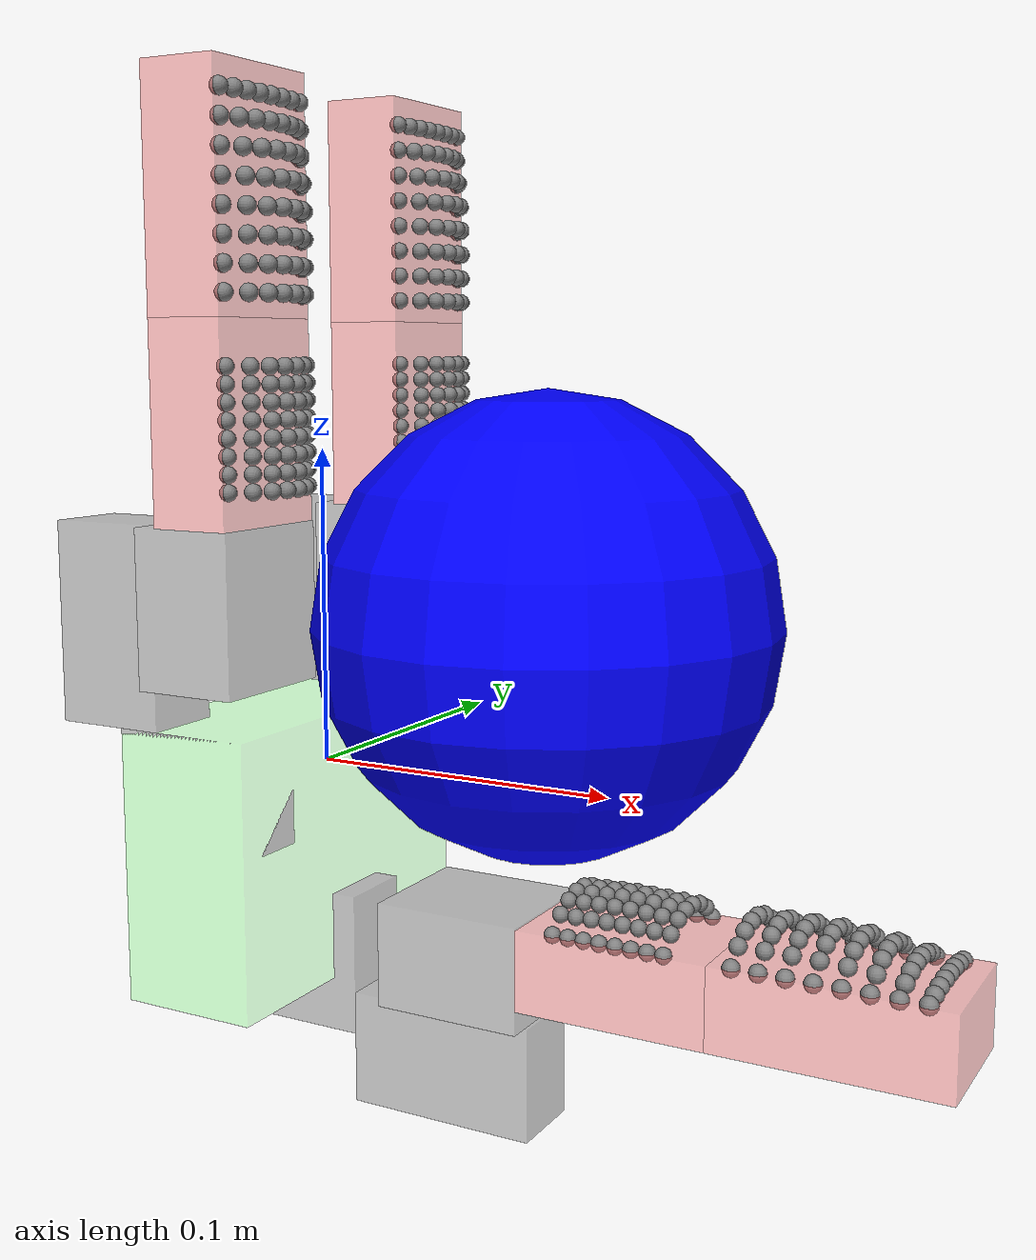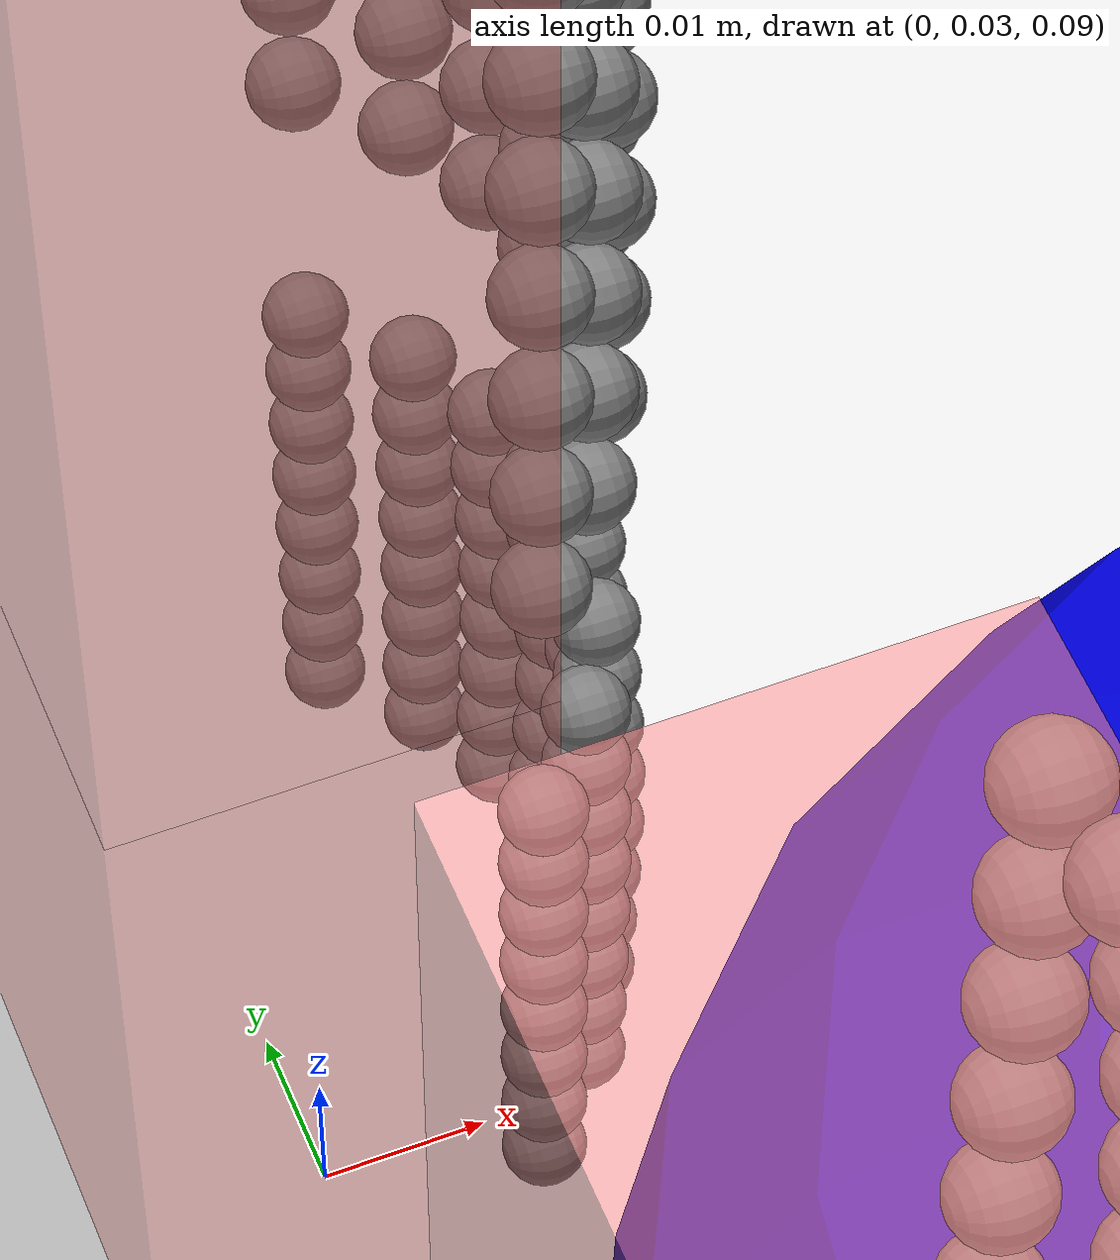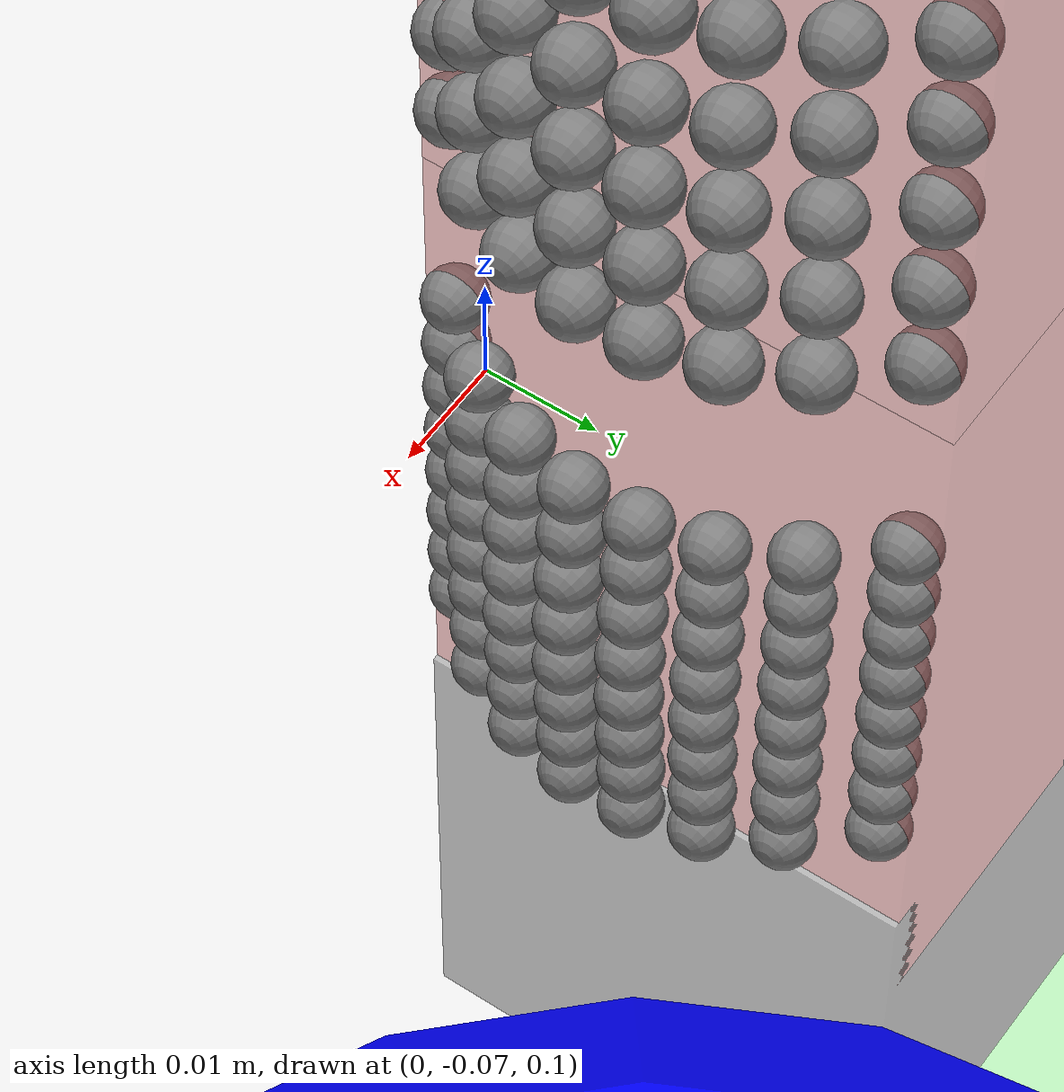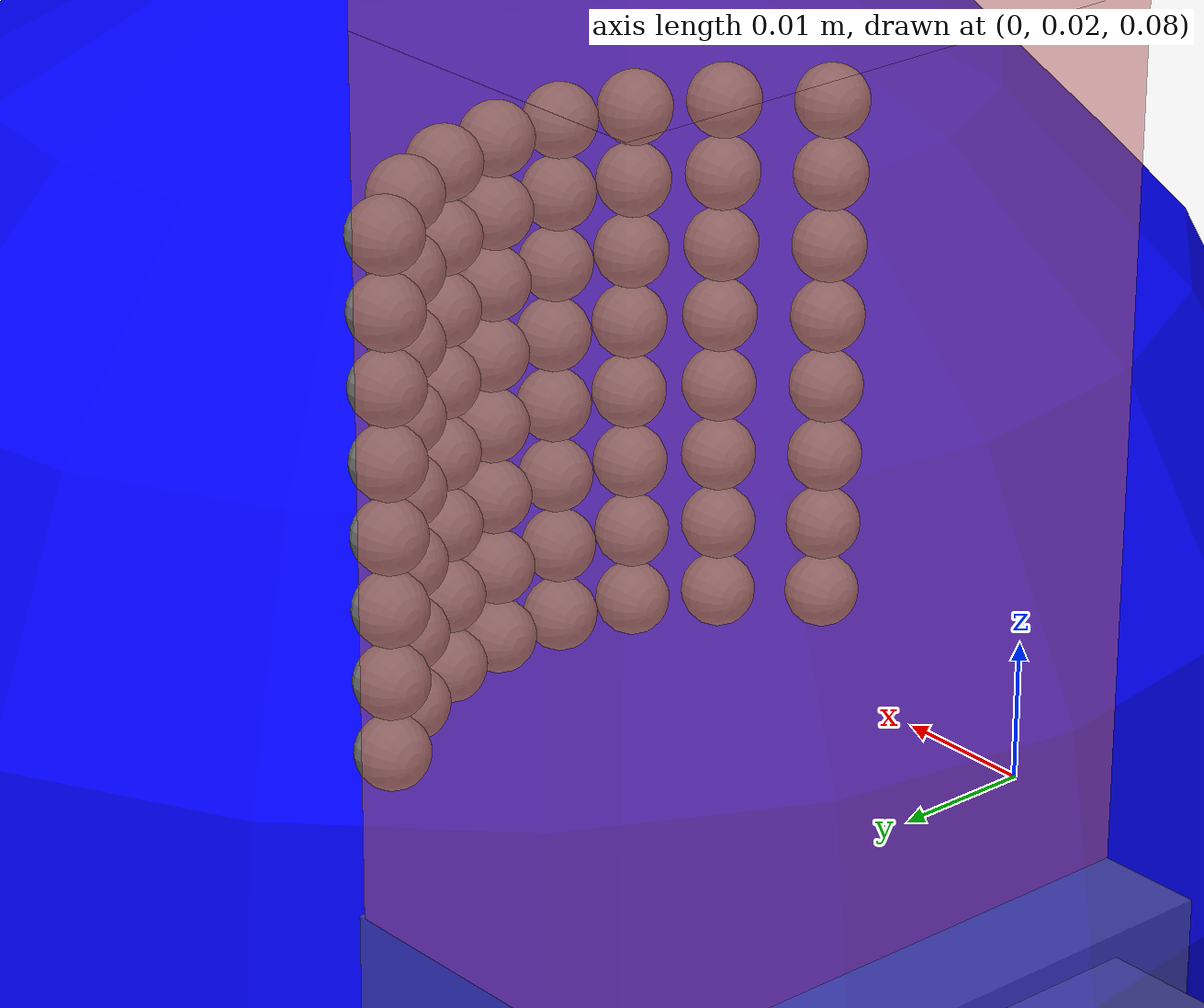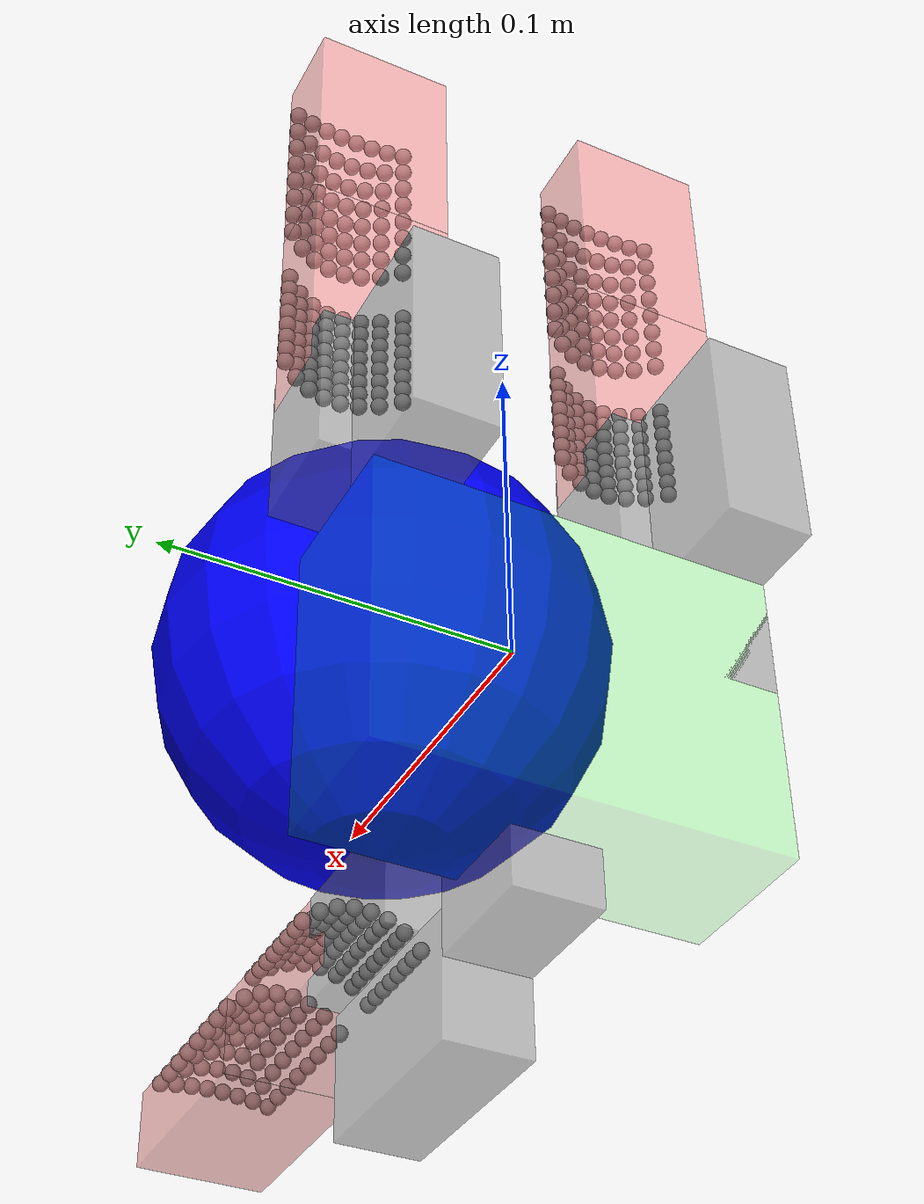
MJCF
<mujoco model="MuJoCo Model">
  <compiler angle="radian"/>

  <option timestep="0.0001" integrator="implicitfast"/>

  <default>
    <joint armature="0.01" frictionloss="0.01"/>
    <geom conaffinity="2" condim="4" friction="0.9 0.2 0.2" solref="0.001"/>

    <equality solref="1e-06 30"/>
    <general ctrllimited="true" biastype="affine" gainprm="1000000" biasprm="0 -1000000"/>
  </default>

  <asset>
    <texture type="skybox" builtin="gradient" rgb1="1 1 1" rgb2="1 1 1" width="265" height="1590"/>
    <texture type="2d" name="grid" builtin="checker" rgb1="0.1 0.2 0.3" rgb2="0.2 0.3 0.4" width="300" height="300"/>
    <material name="grid" texture="grid" texrepeat="10 10" reflectance="0.2"/>
  </asset>

  <worldbody>
    <geom name="fingers_bbox" size="0.0225 0.0575 0.043" pos="-0.0125 0 -0.025" type="box" rgba="0 1 0 0.2"/>
    <light pos="0 0 10" dir="0 0 -1"/>
    <body name="ID1_ROT" pos="0 0.045 0">
      <geom name="ID1_ROT_geom" size="0.0225 0.0125 0.018" pos="-0.0125 0 0" type="box" rgba="0.5 0.5 0.5 0.5"/>
      <body name="ID1_ABD" pos="-0.0395 0 0.07" quat="0.707107 0 0.707107 0">
        <joint name="ID1_ROT_joint" pos="0.07 0 0.0395" axis="-1 0 0" range="-1.5708 0"/>
        <geom name="ID1_ABD_geom" size="0.031 0.0125 0.018" pos="0.021 0 0" type="box" rgba="0.5 0.5 0.5 0.5"/>
        <body name="ID1_PIP" pos="0 0 0.0395" quat="0.707107 -0.707107 0 0">
          <joint name="ID1_ABD_joint" pos="0 0.0395 0" axis="0 -1 0" range="-1.5708 1.5708"/>
          <geom name="ID1_PIP_geom" size="0.024 0.0165 0.021" pos="0.0136 0.0035 0" type="box" rgba="0.5 0.5 0.5 0.5"/>
          <body name="ID1_DIP" pos="-0.07 0 0">
            <joint name="ID1_PIP_joint" pos="0.07 0 0" axis="0 0 1" range="0 1.5708"/>
            <geom name="ID1_DIP_geom" size="0.035 0.0125 0.021" pos="0.035 0 0" type="box" rgba="1 0.5 0.5 0.5"/>
            <body name="ID1_FIN" pos="-0.07 0 0">
              <joint name="ID1_DIP_joint" pos="0.07 0 0" axis="0 0 1" range="0 1.5708"/>
              <geom name="ID1_FIN_geom" size="0.035 0.0125 0.021" pos="0.035 0 0" type="box" rgba="1 0.5 0.5 0.5"/>
              <body name="ID1_pad_root_ID1_FIN" pos="0.036 0 0">
                <body name="pad_1_ID1_FIN_0_0" pos="0 -0.0125 0" quat="0.707107 0.707107 0 0">
                  <joint name="pad_1_ID1_FIN_0_0_joint" pos="0 0 0" axis="0 0 1" type="slide" stiffness="5" damping="0.1"/>
                  <geom name="pad_1_ID1_FIN_0_0_geom" size="0.002625" pos="-0.027375 -0.018375 0" conaffinity="1"/>
                  <site name="pad_1_ID1_FIN_0_0_site" pos="-0.027375 -0.018375 0" size="0.000525" rgba="1 0 0 1"/>
                </body>
                <body name="pad_1_ID1_FIN_0_1" pos="0 -0.0125 0" quat="0.707107 0.707107 0 0">
                  <joint name="pad_1_ID1_FIN_0_1_joint" pos="0 0 0" axis="0 0 1" type="slide" stiffness="5" damping="0.1"/>
                  <geom name="pad_1_ID1_FIN_0_1_geom" size="0.002625" pos="-0.0195536 -0.018375 0" conaffinity="1"/>
                  <site name="pad_1_ID1_FIN_0_1_site" pos="-0.0195536 -0.018375 0" size="0.000525" rgba="1 0 0 1"/>
                </body>
                <body name="pad_1_ID1_FIN_0_2" pos="0 -0.0125 0" quat="0.707107 0.707107 0 0">
                  <joint name="pad_1_ID1_FIN_0_2_joint" pos="0 0 0" axis="0 0 1" type="slide" stiffness="5" damping="0.1"/>
                  <geom name="pad_1_ID1_FIN_0_2_geom" size="0.002625" pos="-0.0117321 -0.018375 0" conaffinity="1"/>
                  <site name="pad_1_ID1_FIN_0_2_site" pos="-0.0117321 -0.018375 0" size="0.000525" rgba="1 0 0 1"/>
                </body>
                <body name="pad_1_ID1_FIN_0_3" pos="0 -0.0125 0" quat="0.707107 0.707107 0 0">
                  <joint name="pad_1_ID1_FIN_0_3_joint" pos="0 0 0" axis="0 0 1" type="slide" stiffness="5" damping="0.1"/>
                  <geom name="pad_1_ID1_FIN_0_3_geom" size="0.002625" pos="-0.00391071 -0.018375 0" conaffinity="1"/>
                  <site name="pad_1_ID1_FIN_0_3_site" pos="-0.00391071 -0.018375 0" size="0.000525" rgba="1 0 0 1"/>
                </body>
                <body name="pad_1_ID1_FIN_0_4" pos="0 -0.0125 0" quat="0.707107 0.707107 0 0">
                  <joint name="pad_1_ID1_FIN_0_4_joint" pos="0 0 0" axis="0 0 1" type="slide" stiffness="5" damping="0.1"/>
                  <geom name="pad_1_ID1_FIN_0_4_geom" size="0.002625" pos="0.00391071 -0.018375 0" conaffinity="1"/>
                  <site name="pad_1_ID1_FIN_0_4_site" pos="0.00391071 -0.018375 0" size="0.000525" rgba="1 0 0 1"/>
                </body>
                <body name="pad_1_ID1_FIN_0_5" pos="0 -0.0125 0" quat="0.707107 0.707107 0 0">
                  <joint name="pad_1_ID1_FIN_0_5_joint" pos="0 0 0" axis="0 0 1" type="slide" stiffness="5" damping="0.1"/>
                  <geom name="pad_1_ID1_FIN_0_5_geom" size="0.002625" pos="0.0117321 -0.018375 0" conaffinity="1"/>
                  <site name="pad_1_ID1_FIN_0_5_site" pos="0.0117321 -0.018375 0" size="0.000525" rgba="1 0 0 1"/>
                </body>
                <body name="pad_1_ID1_FIN_0_6" pos="0 -0.0125 0" quat="0.707107 0.707107 0 0">
                  <joint name="pad_1_ID1_FIN_0_6_joint" pos="0 0 0" axis="0 0 1" type="slide" stiffness="5" damping="0.1"/>
                  <geom name="pad_1_ID1_FIN_0_6_geom" size="0.002625" pos="0.0195536 -0.018375 0" conaffinity="1"/>
                  <site name="pad_1_ID1_FIN_0_6_site" pos="0.0195536 -0.018375 0" size="0.000525" rgba="1 0 0 1"/>
                </body>
                <body name="pad_1_ID1_FIN_0_7" pos="0 -0.0125 0" quat="0.707107 0.707107 0 0">
                  <joint name="pad_1_ID1_FIN_0_7_joint" pos="0 0 0" axis="0 0 1" type="slide" stiffness="5" damping="0.1"/>
                  <geom name="pad_1_ID1_FIN_0_7_geom" size="0.002625" pos="0.027375 -0.018375 0" conaffinity="1"/>
                  <site name="pad_1_ID1_FIN_0_7_site" pos="0.027375 -0.018375 0" size="0.000525" rgba="1 0 0 1"/>
                </body>
                <body name="pad_1_ID1_FIN_1_0" pos="0 -0.0125 0" quat="0.707107 0.707107 0 0">
                  <joint name="pad_1_ID1_FIN_1_0_joint" pos="0 0 0" axis="0 0 1" type="slide" stiffness="5" range="-0.000919617 0" damping="0.1"/>
                  <geom name="pad_1_ID1_FIN_1_0_geom" size="0.002625" pos="-0.027375 -0.013125 0.000919617" conaffinity="1"/>
                  <site name="pad_1_ID1_FIN_1_0_site" pos="-0.027375 -0.013125 0.000919617" size="0.000525" rgba="1 0 0 1"/>
                </body>
                <body name="pad_1_ID1_FIN_1_1" pos="0 -0.0125 0" quat="0.707107 0.707107 0 0">
                  <joint name="pad_1_ID1_FIN_1_1_joint" pos="0 0 0" axis="0 0 1" type="slide" stiffness="5" range="-0.00265301 0" damping="0.1"/>
                  <geom name="pad_1_ID1_FIN_1_1_geom" size="0.002625" pos="-0.0195536 -0.013125 0.00265301" conaffinity="1"/>
                  <site name="pad_1_ID1_FIN_1_1_site" pos="-0.0195536 -0.013125 0.00265301" size="0.000525" rgba="1 0 0 1"/>
                </body>
                <body name="pad_1_ID1_FIN_1_2" pos="0 -0.0125 0" quat="0.707107 0.707107 0 0">
                  <joint name="pad_1_ID1_FIN_1_2_joint" pos="0 0 0" axis="0 0 1" type="slide" stiffness="5" range="-0.00375296 0" damping="0.1"/>
                  <geom name="pad_1_ID1_FIN_1_2_geom" size="0.002625" pos="-0.0117321 -0.013125 0.00375296" conaffinity="1"/>
                  <site name="pad_1_ID1_FIN_1_2_site" pos="-0.0117321 -0.013125 0.00375296" size="0.000525" rgba="1 0 0 1"/>
                </body>
                <body name="pad_1_ID1_FIN_1_3" pos="0 -0.0125 0" quat="0.707107 0.707107 0 0">
                  <joint name="pad_1_ID1_FIN_1_3_joint" pos="0 0 0" axis="0 0 1" type="slide" stiffness="5" range="-0.00436774 0" damping="0.1"/>
                  <geom name="pad_1_ID1_FIN_1_3_geom" size="0.002625" pos="-0.00391071 -0.013125 0.00436774" conaffinity="1"/>
                  <site name="pad_1_ID1_FIN_1_3_site" pos="-0.00391071 -0.013125 0.00436774" size="0.000525" rgba="1 0 0 1"/>
                </body>
                <body name="pad_1_ID1_FIN_1_4" pos="0 -0.0125 0" quat="0.707107 0.707107 0 0">
                  <joint name="pad_1_ID1_FIN_1_4_joint" pos="0 0 0" axis="0 0 1" type="slide" stiffness="5" range="-0.00463585 0" damping="0.1"/>
                  <geom name="pad_1_ID1_FIN_1_4_geom" size="0.002625" pos="0.00391071 -0.013125 0.00463585" conaffinity="1"/>
                  <site name="pad_1_ID1_FIN_1_4_site" pos="0.00391071 -0.013125 0.00463585" size="0.000525" rgba="1 0 0 1"/>
                </body>
                <body name="pad_1_ID1_FIN_1_5" pos="0 -0.0125 0" quat="0.707107 0.707107 0 0">
                  <joint name="pad_1_ID1_FIN_1_5_joint" pos="0 0 0" axis="0 0 1" type="slide" stiffness="5" range="-0.00468598 0" damping="0.1"/>
                  <geom name="pad_1_ID1_FIN_1_5_geom" size="0.002625" pos="0.0117321 -0.013125 0.00468598" conaffinity="1"/>
                  <site name="pad_1_ID1_FIN_1_5_site" pos="0.0117321 -0.013125 0.00468598" size="0.000525" rgba="1 0 0 1"/>
                </body>
                <body name="pad_1_ID1_FIN_1_6" pos="0 -0.0125 0" quat="0.707107 0.707107 0 0">
                  <joint name="pad_1_ID1_FIN_1_6_joint" pos="0 0 0" axis="0 0 1" type="slide" stiffness="5" range="-0.00463702 0" damping="0.1"/>
                  <geom name="pad_1_ID1_FIN_1_6_geom" size="0.002625" pos="0.0195536 -0.013125 0.00463702" conaffinity="1"/>
                  <site name="pad_1_ID1_FIN_1_6_site" pos="0.0195536 -0.013125 0.00463702" size="0.000525" rgba="1 0 0 1"/>
                </body>
                <body name="pad_1_ID1_FIN_1_7" pos="0 -0.0125 0" quat="0.707107 0.707107 0 0">
                  <joint name="pad_1_ID1_FIN_1_7_joint" pos="0 0 0" axis="0 0 1" type="slide" stiffness="5" range="-0.00459808 0" damping="0.1"/>
                  <geom name="pad_1_ID1_FIN_1_7_geom" size="0.002625" pos="0.027375 -0.013125 0.00459808" conaffinity="1"/>
                  <site name="pad_1_ID1_FIN_1_7_site" pos="0.027375 -0.013125 0.00459808" size="0.000525" rgba="1 0 0 1"/>
                </body>
                <body name="pad_1_ID1_FIN_2_0" pos="0 -0.0125 0" quat="0.707107 0.707107 0 0">
                  <joint name="pad_1_ID1_FIN_2_0_joint" pos="0 0 0" axis="0 0 1" type="slide" stiffness="5" range="-0.00146606 0" damping="0.1"/>
                  <geom name="pad_1_ID1_FIN_2_0_geom" size="0.002625" pos="-0.027375 -0.007875 0.00146606" conaffinity="1"/>
                  <site name="pad_1_ID1_FIN_2_0_site" pos="-0.027375 -0.007875 0.00146606" size="0.000525" rgba="1 0 0 1"/>
                </body>
                <body name="pad_1_ID1_FIN_2_1" pos="0 -0.0125 0" quat="0.707107 0.707107 0 0">
                  <joint name="pad_1_ID1_FIN_2_1_joint" pos="0 0 0" axis="0 0 1" type="slide" stiffness="5" range="-0.00427732 0" damping="0.1"/>
                  <geom name="pad_1_ID1_FIN_2_1_geom" size="0.002625" pos="-0.0195536 -0.007875 0.00427732" conaffinity="1"/>
                  <site name="pad_1_ID1_FIN_2_1_site" pos="-0.0195536 -0.007875 0.00427732" size="0.000525" rgba="1 0 0 1"/>
                </body>
                <body name="pad_1_ID1_FIN_2_2" pos="0 -0.0125 0" quat="0.707107 0.707107 0 0">
                  <joint name="pad_1_ID1_FIN_2_2_joint" pos="0 0 0" axis="0 0 1" type="slide" stiffness="5" range="-0.00611601 0" damping="0.1"/>
                  <geom name="pad_1_ID1_FIN_2_2_geom" size="0.002625" pos="-0.0117321 -0.007875 0.00611601" conaffinity="1"/>
                  <site name="pad_1_ID1_FIN_2_2_site" pos="-0.0117321 -0.007875 0.00611601" size="0.000525" rgba="1 0 0 1"/>
                </body>
                <body name="pad_1_ID1_FIN_2_3" pos="0 -0.0125 0" quat="0.707107 0.707107 0 0">
                  <joint name="pad_1_ID1_FIN_2_3_joint" pos="0 0 0" axis="0 0 1" type="slide" stiffness="5" range="-0.00715465 0" damping="0.1"/>
                  <geom name="pad_1_ID1_FIN_2_3_geom" size="0.002625" pos="-0.00391071 -0.007875 0.00715465" conaffinity="1"/>
                  <site name="pad_1_ID1_FIN_2_3_site" pos="-0.00391071 -0.007875 0.00715465" size="0.000525" rgba="1 0 0 1"/>
                </body>
                <body name="pad_1_ID1_FIN_2_4" pos="0 -0.0125 0" quat="0.707107 0.707107 0 0">
                  <joint name="pad_1_ID1_FIN_2_4_joint" pos="0 0 0" axis="0 0 1" type="slide" stiffness="5" range="-0.00758207 0" damping="0.1"/>
                  <geom name="pad_1_ID1_FIN_2_4_geom" size="0.002625" pos="0.00391071 -0.007875 0.00758207" conaffinity="1"/>
                  <site name="pad_1_ID1_FIN_2_4_site" pos="0.00391071 -0.007875 0.00758207" size="0.000525" rgba="1 0 0 1"/>
                </body>
                <body name="pad_1_ID1_FIN_2_5" pos="0 -0.0125 0" quat="0.707107 0.707107 0 0">
                  <joint name="pad_1_ID1_FIN_2_5_joint" pos="0 0 0" axis="0 0 1" type="slide" stiffness="5" range="-0.00760344 0" damping="0.1"/>
                  <geom name="pad_1_ID1_FIN_2_5_geom" size="0.002625" pos="0.0117321 -0.007875 0.00760344" conaffinity="1"/>
                  <site name="pad_1_ID1_FIN_2_5_site" pos="0.0117321 -0.007875 0.00760344" size="0.000525" rgba="1 0 0 1"/>
                </body>
                <body name="pad_1_ID1_FIN_2_6" pos="0 -0.0125 0" quat="0.707107 0.707107 0 0">
                  <joint name="pad_1_ID1_FIN_2_6_joint" pos="0 0 0" axis="0 0 1" type="slide" stiffness="5" range="-0.00744024 0" damping="0.1"/>
                  <geom name="pad_1_ID1_FIN_2_6_geom" size="0.002625" pos="0.0195536 -0.007875 0.00744024" conaffinity="1"/>
                  <site name="pad_1_ID1_FIN_2_6_site" pos="0.0195536 -0.007875 0.00744024" size="0.000525" rgba="1 0 0 1"/>
                </body>
                <body name="pad_1_ID1_FIN_2_7" pos="0 -0.0125 0" quat="0.707107 0.707107 0 0">
                  <joint name="pad_1_ID1_FIN_2_7_joint" pos="0 0 0" axis="0 0 1" type="slide" stiffness="5" range="-0.00733028 0" damping="0.1"/>
                  <geom name="pad_1_ID1_FIN_2_7_geom" size="0.002625" pos="0.027375 -0.007875 0.00733028" conaffinity="1"/>
                  <site name="pad_1_ID1_FIN_2_7_site" pos="0.027375 -0.007875 0.00733028" size="0.000525" rgba="1 0 0 1"/>
                </body>
                <body name="pad_1_ID1_FIN_3_0" pos="0 -0.0125 0" quat="0.707107 0.707107 0 0">
                  <joint name="pad_1_ID1_FIN_3_0_joint" pos="0 0 0" axis="0 0 1" type="slide" stiffness="5" range="-0.00171928 0" damping="0.1"/>
                  <geom name="pad_1_ID1_FIN_3_0_geom" size="0.002625" pos="-0.027375 -0.002625 0.00171928" conaffinity="1"/>
                  <site name="pad_1_ID1_FIN_3_0_site" pos="-0.027375 -0.002625 0.00171928" size="0.000525" rgba="1 0 0 1"/>
                </body>
                <body name="pad_1_ID1_FIN_3_1" pos="0 -0.0125 0" quat="0.707107 0.707107 0 0">
                  <joint name="pad_1_ID1_FIN_3_1_joint" pos="0 0 0" axis="0 0 1" type="slide" stiffness="5" range="-0.00504618 0" damping="0.1"/>
                  <geom name="pad_1_ID1_FIN_3_1_geom" size="0.002625" pos="-0.0195536 -0.002625 0.00504618" conaffinity="1"/>
                  <site name="pad_1_ID1_FIN_3_1_site" pos="-0.0195536 -0.002625 0.00504618" size="0.000525" rgba="1 0 0 1"/>
                </body>
                <body name="pad_1_ID1_FIN_3_2" pos="0 -0.0125 0" quat="0.707107 0.707107 0 0">
                  <joint name="pad_1_ID1_FIN_3_2_joint" pos="0 0 0" axis="0 0 1" type="slide" stiffness="5" range="-0.00725587 0" damping="0.1"/>
                  <geom name="pad_1_ID1_FIN_3_2_geom" size="0.002625" pos="-0.0117321 -0.002625 0.00725587" conaffinity="1"/>
                  <site name="pad_1_ID1_FIN_3_2_site" pos="-0.0117321 -0.002625 0.00725587" size="0.000525" rgba="1 0 0 1"/>
                </body>
                <body name="pad_1_ID1_FIN_3_3" pos="0 -0.0125 0" quat="0.707107 0.707107 0 0">
                  <joint name="pad_1_ID1_FIN_3_3_joint" pos="0 0 0" axis="0 0 1" type="slide" stiffness="5" range="-0.00851062 0" damping="0.1"/>
                  <geom name="pad_1_ID1_FIN_3_3_geom" size="0.002625" pos="-0.00391071 -0.002625 0.00851062" conaffinity="1"/>
                  <site name="pad_1_ID1_FIN_3_3_site" pos="-0.00391071 -0.002625 0.00851062" size="0.000525" rgba="1 0 0 1"/>
                </body>
                <body name="pad_1_ID1_FIN_3_4" pos="0 -0.0125 0" quat="0.707107 0.707107 0 0">
                  <joint name="pad_1_ID1_FIN_3_4_joint" pos="0 0 0" axis="0 0 1" type="slide" stiffness="5" range="-0.00901187 0" damping="0.1"/>
                  <geom name="pad_1_ID1_FIN_3_4_geom" size="0.002625" pos="0.00391071 -0.002625 0.00901187" conaffinity="1"/>
                  <site name="pad_1_ID1_FIN_3_4_site" pos="0.00391071 -0.002625 0.00901187" size="0.000525" rgba="1 0 0 1"/>
                </body>
                <body name="pad_1_ID1_FIN_3_5" pos="0 -0.0125 0" quat="0.707107 0.707107 0 0">
                  <joint name="pad_1_ID1_FIN_3_5_joint" pos="0 0 0" axis="0 0 1" type="slide" stiffness="5" range="-0.00900021 0" damping="0.1"/>
                  <geom name="pad_1_ID1_FIN_3_5_geom" size="0.002625" pos="0.0117321 -0.002625 0.00900021" conaffinity="1"/>
                  <site name="pad_1_ID1_FIN_3_5_site" pos="0.0117321 -0.002625 0.00900021" size="0.000525" rgba="1 0 0 1"/>
                </body>
                <body name="pad_1_ID1_FIN_3_6" pos="0 -0.0125 0" quat="0.707107 0.707107 0 0">
                  <joint name="pad_1_ID1_FIN_3_6_joint" pos="0 0 0" axis="0 0 1" type="slide" stiffness="5" range="-0.00875542 0" damping="0.1"/>
                  <geom name="pad_1_ID1_FIN_3_6_geom" size="0.002625" pos="0.0195536 -0.002625 0.00875542" conaffinity="1"/>
                  <site name="pad_1_ID1_FIN_3_6_site" pos="0.0195536 -0.002625 0.00875542" size="0.000525" rgba="1 0 0 1"/>
                </body>
                <body name="pad_1_ID1_FIN_3_7" pos="0 -0.0125 0" quat="0.707107 0.707107 0 0">
                  <joint name="pad_1_ID1_FIN_3_7_joint" pos="0 0 0" axis="0 0 1" type="slide" stiffness="5" range="-0.00859642 0" damping="0.1"/>
                  <geom name="pad_1_ID1_FIN_3_7_geom" size="0.002625" pos="0.027375 -0.002625 0.00859642" conaffinity="1"/>
                  <site name="pad_1_ID1_FIN_3_7_site" pos="0.027375 -0.002625 0.00859642" size="0.000525" rgba="1 0 0 1"/>
                </body>
                <body name="pad_1_ID1_FIN_4_0" pos="0 -0.0125 0" quat="0.707107 0.707107 0 0">
                  <joint name="pad_1_ID1_FIN_4_0_joint" pos="0 0 0" axis="0 0 1" type="slide" stiffness="5" range="-0.00171928 0" damping="0.1"/>
                  <geom name="pad_1_ID1_FIN_4_0_geom" size="0.002625" pos="-0.027375 0.002625 0.00171928" conaffinity="1"/>
                  <site name="pad_1_ID1_FIN_4_0_site" pos="-0.027375 0.002625 0.00171928" size="0.000525" rgba="1 0 0 1"/>
                </body>
                <body name="pad_1_ID1_FIN_4_1" pos="0 -0.0125 0" quat="0.707107 0.707107 0 0">
                  <joint name="pad_1_ID1_FIN_4_1_joint" pos="0 0 0" axis="0 0 1" type="slide" stiffness="5" range="-0.00504618 0" damping="0.1"/>
                  <geom name="pad_1_ID1_FIN_4_1_geom" size="0.002625" pos="-0.0195536 0.002625 0.00504618" conaffinity="1"/>
                  <site name="pad_1_ID1_FIN_4_1_site" pos="-0.0195536 0.002625 0.00504618" size="0.000525" rgba="1 0 0 1"/>
                </body>
                <body name="pad_1_ID1_FIN_4_2" pos="0 -0.0125 0" quat="0.707107 0.707107 0 0">
                  <joint name="pad_1_ID1_FIN_4_2_joint" pos="0 0 0" axis="0 0 1" type="slide" stiffness="5" range="-0.00725587 0" damping="0.1"/>
                  <geom name="pad_1_ID1_FIN_4_2_geom" size="0.002625" pos="-0.0117321 0.002625 0.00725587" conaffinity="1"/>
                  <site name="pad_1_ID1_FIN_4_2_site" pos="-0.0117321 0.002625 0.00725587" size="0.000525" rgba="1 0 0 1"/>
                </body>
                <body name="pad_1_ID1_FIN_4_3" pos="0 -0.0125 0" quat="0.707107 0.707107 0 0">
                  <joint name="pad_1_ID1_FIN_4_3_joint" pos="0 0 0" axis="0 0 1" type="slide" stiffness="5" range="-0.00851062 0" damping="0.1"/>
                  <geom name="pad_1_ID1_FIN_4_3_geom" size="0.002625" pos="-0.00391071 0.002625 0.00851062" conaffinity="1"/>
                  <site name="pad_1_ID1_FIN_4_3_site" pos="-0.00391071 0.002625 0.00851062" size="0.000525" rgba="1 0 0 1"/>
                </body>
                <body name="pad_1_ID1_FIN_4_4" pos="0 -0.0125 0" quat="0.707107 0.707107 0 0">
                  <joint name="pad_1_ID1_FIN_4_4_joint" pos="0 0 0" axis="0 0 1" type="slide" stiffness="5" range="-0.00901187 0" damping="0.1"/>
                  <geom name="pad_1_ID1_FIN_4_4_geom" size="0.002625" pos="0.00391071 0.002625 0.00901187" conaffinity="1"/>
                  <site name="pad_1_ID1_FIN_4_4_site" pos="0.00391071 0.002625 0.00901187" size="0.000525" rgba="1 0 0 1"/>
                </body>
                <body name="pad_1_ID1_FIN_4_5" pos="0 -0.0125 0" quat="0.707107 0.707107 0 0">
                  <joint name="pad_1_ID1_FIN_4_5_joint" pos="0 0 0" axis="0 0 1" type="slide" stiffness="5" range="-0.00900021 0" damping="0.1"/>
                  <geom name="pad_1_ID1_FIN_4_5_geom" size="0.002625" pos="0.0117321 0.002625 0.00900021" conaffinity="1"/>
                  <site name="pad_1_ID1_FIN_4_5_site" pos="0.0117321 0.002625 0.00900021" size="0.000525" rgba="1 0 0 1"/>
                </body>
                <body name="pad_1_ID1_FIN_4_6" pos="0 -0.0125 0" quat="0.707107 0.707107 0 0">
                  <joint name="pad_1_ID1_FIN_4_6_joint" pos="0 0 0" axis="0 0 1" type="slide" stiffness="5" range="-0.00875542 0" damping="0.1"/>
                  <geom name="pad_1_ID1_FIN_4_6_geom" size="0.002625" pos="0.0195536 0.002625 0.00875542" conaffinity="1"/>
                  <site name="pad_1_ID1_FIN_4_6_site" pos="0.0195536 0.002625 0.00875542" size="0.000525" rgba="1 0 0 1"/>
                </body>
                <body name="pad_1_ID1_FIN_4_7" pos="0 -0.0125 0" quat="0.707107 0.707107 0 0">
                  <joint name="pad_1_ID1_FIN_4_7_joint" pos="0 0 0" axis="0 0 1" type="slide" stiffness="5" range="-0.00859642 0" damping="0.1"/>
                  <geom name="pad_1_ID1_FIN_4_7_geom" size="0.002625" pos="0.027375 0.002625 0.00859642" conaffinity="1"/>
                  <site name="pad_1_ID1_FIN_4_7_site" pos="0.027375 0.002625 0.00859642" size="0.000525" rgba="1 0 0 1"/>
                </body>
                <body name="pad_1_ID1_FIN_5_0" pos="0 -0.0125 0" quat="0.707107 0.707107 0 0">
                  <joint name="pad_1_ID1_FIN_5_0_joint" pos="0 0 0" axis="0 0 1" type="slide" stiffness="5" range="-0.00146606 0" damping="0.1"/>
                  <geom name="pad_1_ID1_FIN_5_0_geom" size="0.002625" pos="-0.027375 0.007875 0.00146606" conaffinity="1"/>
                  <site name="pad_1_ID1_FIN_5_0_site" pos="-0.027375 0.007875 0.00146606" size="0.000525" rgba="1 0 0 1"/>
                </body>
                <body name="pad_1_ID1_FIN_5_1" pos="0 -0.0125 0" quat="0.707107 0.707107 0 0">
                  <joint name="pad_1_ID1_FIN_5_1_joint" pos="0 0 0" axis="0 0 1" type="slide" stiffness="5" range="-0.00427732 0" damping="0.1"/>
                  <geom name="pad_1_ID1_FIN_5_1_geom" size="0.002625" pos="-0.0195536 0.007875 0.00427732" conaffinity="1"/>
                  <site name="pad_1_ID1_FIN_5_1_site" pos="-0.0195536 0.007875 0.00427732" size="0.000525" rgba="1 0 0 1"/>
                </body>
                <body name="pad_1_ID1_FIN_5_2" pos="0 -0.0125 0" quat="0.707107 0.707107 0 0">
                  <joint name="pad_1_ID1_FIN_5_2_joint" pos="0 0 0" axis="0 0 1" type="slide" stiffness="5" range="-0.00611601 0" damping="0.1"/>
                  <geom name="pad_1_ID1_FIN_5_2_geom" size="0.002625" pos="-0.0117321 0.007875 0.00611601" conaffinity="1"/>
                  <site name="pad_1_ID1_FIN_5_2_site" pos="-0.0117321 0.007875 0.00611601" size="0.000525" rgba="1 0 0 1"/>
                </body>
                <body name="pad_1_ID1_FIN_5_3" pos="0 -0.0125 0" quat="0.707107 0.707107 0 0">
                  <joint name="pad_1_ID1_FIN_5_3_joint" pos="0 0 0" axis="0 0 1" type="slide" stiffness="5" range="-0.00715465 0" damping="0.1"/>
                  <geom name="pad_1_ID1_FIN_5_3_geom" size="0.002625" pos="-0.00391071 0.007875 0.00715465" conaffinity="1"/>
                  <site name="pad_1_ID1_FIN_5_3_site" pos="-0.00391071 0.007875 0.00715465" size="0.000525" rgba="1 0 0 1"/>
                </body>
                <body name="pad_1_ID1_FIN_5_4" pos="0 -0.0125 0" quat="0.707107 0.707107 0 0">
                  <joint name="pad_1_ID1_FIN_5_4_joint" pos="0 0 0" axis="0 0 1" type="slide" stiffness="5" range="-0.00758207 0" damping="0.1"/>
                  <geom name="pad_1_ID1_FIN_5_4_geom" size="0.002625" pos="0.00391071 0.007875 0.00758207" conaffinity="1"/>
                  <site name="pad_1_ID1_FIN_5_4_site" pos="0.00391071 0.007875 0.00758207" size="0.000525" rgba="1 0 0 1"/>
                </body>
                <body name="pad_1_ID1_FIN_5_5" pos="0 -0.0125 0" quat="0.707107 0.707107 0 0">
                  <joint name="pad_1_ID1_FIN_5_5_joint" pos="0 0 0" axis="0 0 1" type="slide" stiffness="5" range="-0.00760344 0" damping="0.1"/>
                  <geom name="pad_1_ID1_FIN_5_5_geom" size="0.002625" pos="0.0117321 0.007875 0.00760344" conaffinity="1"/>
                  <site name="pad_1_ID1_FIN_5_5_site" pos="0.0117321 0.007875 0.00760344" size="0.000525" rgba="1 0 0 1"/>
                </body>
                <body name="pad_1_ID1_FIN_5_6" pos="0 -0.0125 0" quat="0.707107 0.707107 0 0">
                  <joint name="pad_1_ID1_FIN_5_6_joint" pos="0 0 0" axis="0 0 1" type="slide" stiffness="5" range="-0.00744024 0" damping="0.1"/>
                  <geom name="pad_1_ID1_FIN_5_6_geom" size="0.002625" pos="0.0195536 0.007875 0.00744024" conaffinity="1"/>
                  <site name="pad_1_ID1_FIN_5_6_site" pos="0.0195536 0.007875 0.00744024" size="0.000525" rgba="1 0 0 1"/>
                </body>
                <body name="pad_1_ID1_FIN_5_7" pos="0 -0.0125 0" quat="0.707107 0.707107 0 0">
                  <joint name="pad_1_ID1_FIN_5_7_joint" pos="0 0 0" axis="0 0 1" type="slide" stiffness="5" range="-0.00733028 0" damping="0.1"/>
                  <geom name="pad_1_ID1_FIN_5_7_geom" size="0.002625" pos="0.027375 0.007875 0.00733028" conaffinity="1"/>
                  <site name="pad_1_ID1_FIN_5_7_site" pos="0.027375 0.007875 0.00733028" size="0.000525" rgba="1 0 0 1"/>
                </body>
                <body name="pad_1_ID1_FIN_6_0" pos="0 -0.0125 0" quat="0.707107 0.707107 0 0">
                  <joint name="pad_1_ID1_FIN_6_0_joint" pos="0 0 0" axis="0 0 1" type="slide" stiffness="5" range="-0.000919617 0" damping="0.1"/>
                  <geom name="pad_1_ID1_FIN_6_0_geom" size="0.002625" pos="-0.027375 0.013125 0.000919617" conaffinity="1"/>
                  <site name="pad_1_ID1_FIN_6_0_site" pos="-0.027375 0.013125 0.000919617" size="0.000525" rgba="1 0 0 1"/>
                </body>
                <body name="pad_1_ID1_FIN_6_1" pos="0 -0.0125 0" quat="0.707107 0.707107 0 0">
                  <joint name="pad_1_ID1_FIN_6_1_joint" pos="0 0 0" axis="0 0 1" type="slide" stiffness="5" range="-0.00265301 0" damping="0.1"/>
                  <geom name="pad_1_ID1_FIN_6_1_geom" size="0.002625" pos="-0.0195536 0.013125 0.00265301" conaffinity="1"/>
                  <site name="pad_1_ID1_FIN_6_1_site" pos="-0.0195536 0.013125 0.00265301" size="0.000525" rgba="1 0 0 1"/>
                </body>
                <body name="pad_1_ID1_FIN_6_2" pos="0 -0.0125 0" quat="0.707107 0.707107 0 0">
                  <joint name="pad_1_ID1_FIN_6_2_joint" pos="0 0 0" axis="0 0 1" type="slide" stiffness="5" range="-0.00375296 0" damping="0.1"/>
                  <geom name="pad_1_ID1_FIN_6_2_geom" size="0.002625" pos="-0.0117321 0.013125 0.00375296" conaffinity="1"/>
                  <site name="pad_1_ID1_FIN_6_2_site" pos="-0.0117321 0.013125 0.00375296" size="0.000525" rgba="1 0 0 1"/>
                </body>
                <body name="pad_1_ID1_FIN_6_3" pos="0 -0.0125 0" quat="0.707107 0.707107 0 0">
                  <joint name="pad_1_ID1_FIN_6_3_joint" pos="0 0 0" axis="0 0 1" type="slide" stiffness="5" range="-0.00436774 0" damping="0.1"/>
                  <geom name="pad_1_ID1_FIN_6_3_geom" size="0.002625" pos="-0.00391071 0.013125 0.00436774" conaffinity="1"/>
                  <site name="pad_1_ID1_FIN_6_3_site" pos="-0.00391071 0.013125 0.00436774" size="0.000525" rgba="1 0 0 1"/>
                </body>
                <body name="pad_1_ID1_FIN_6_4" pos="0 -0.0125 0" quat="0.707107 0.707107 0 0">
                  <joint name="pad_1_ID1_FIN_6_4_joint" pos="0 0 0" axis="0 0 1" type="slide" stiffness="5" range="-0.00463585 0" damping="0.1"/>
                  <geom name="pad_1_ID1_FIN_6_4_geom" size="0.002625" pos="0.00391071 0.013125 0.00463585" conaffinity="1"/>
                  <site name="pad_1_ID1_FIN_6_4_site" pos="0.00391071 0.013125 0.00463585" size="0.000525" rgba="1 0 0 1"/>
                </body>
                <body name="pad_1_ID1_FIN_6_5" pos="0 -0.0125 0" quat="0.707107 0.707107 0 0">
                  <joint name="pad_1_ID1_FIN_6_5_joint" pos="0 0 0" axis="0 0 1" type="slide" stiffness="5" range="-0.00468598 0" damping="0.1"/>
                  <geom name="pad_1_ID1_FIN_6_5_geom" size="0.002625" pos="0.0117321 0.013125 0.00468598" conaffinity="1"/>
                  <site name="pad_1_ID1_FIN_6_5_site" pos="0.0117321 0.013125 0.00468598" size="0.000525" rgba="1 0 0 1"/>
                </body>
                <body name="pad_1_ID1_FIN_6_6" pos="0 -0.0125 0" quat="0.707107 0.707107 0 0">
                  <joint name="pad_1_ID1_FIN_6_6_joint" pos="0 0 0" axis="0 0 1" type="slide" stiffness="5" range="-0.00463702 0" damping="0.1"/>
                  <geom name="pad_1_ID1_FIN_6_6_geom" size="0.002625" pos="0.0195536 0.013125 0.00463702" conaffinity="1"/>
                  <site name="pad_1_ID1_FIN_6_6_site" pos="0.0195536 0.013125 0.00463702" size="0.000525" rgba="1 0 0 1"/>
                </body>
                <body name="pad_1_ID1_FIN_6_7" pos="0 -0.0125 0" quat="0.707107 0.707107 0 0">
                  <joint name="pad_1_ID1_FIN_6_7_joint" pos="0 0 0" axis="0 0 1" type="slide" stiffness="5" range="-0.00459808 0" damping="0.1"/>
                  <geom name="pad_1_ID1_FIN_6_7_geom" size="0.002625" pos="0.027375 0.013125 0.00459808" conaffinity="1"/>
                  <site name="pad_1_ID1_FIN_6_7_site" pos="0.027375 0.013125 0.00459808" size="0.000525" rgba="1 0 0 1"/>
                </body>
                <body name="pad_1_ID1_FIN_7_0" pos="0 -0.0125 0" quat="0.707107 0.707107 0 0">
                  <joint name="pad_1_ID1_FIN_7_0_joint" pos="0 0 0" axis="0 0 1" type="slide" stiffness="5" damping="0.1"/>
                  <geom name="pad_1_ID1_FIN_7_0_geom" size="0.002625" pos="-0.027375 0.018375 0" conaffinity="1"/>
                  <site name="pad_1_ID1_FIN_7_0_site" pos="-0.027375 0.018375 0" size="0.000525" rgba="1 0 0 1"/>
                </body>
                <body name="pad_1_ID1_FIN_7_1" pos="0 -0.0125 0" quat="0.707107 0.707107 0 0">
                  <joint name="pad_1_ID1_FIN_7_1_joint" pos="0 0 0" axis="0 0 1" type="slide" stiffness="5" damping="0.1"/>
                  <geom name="pad_1_ID1_FIN_7_1_geom" size="0.002625" pos="-0.0195536 0.018375 0" conaffinity="1"/>
                  <site name="pad_1_ID1_FIN_7_1_site" pos="-0.0195536 0.018375 0" size="0.000525" rgba="1 0 0 1"/>
                </body>
                <body name="pad_1_ID1_FIN_7_2" pos="0 -0.0125 0" quat="0.707107 0.707107 0 0">
                  <joint name="pad_1_ID1_FIN_7_2_joint" pos="0 0 0" axis="0 0 1" type="slide" stiffness="5" damping="0.1"/>
                  <geom name="pad_1_ID1_FIN_7_2_geom" size="0.002625" pos="-0.0117321 0.018375 0" conaffinity="1"/>
                  <site name="pad_1_ID1_FIN_7_2_site" pos="-0.0117321 0.018375 0" size="0.000525" rgba="1 0 0 1"/>
                </body>
                <body name="pad_1_ID1_FIN_7_3" pos="0 -0.0125 0" quat="0.707107 0.707107 0 0">
                  <joint name="pad_1_ID1_FIN_7_3_joint" pos="0 0 0" axis="0 0 1" type="slide" stiffness="5" damping="0.1"/>
                  <geom name="pad_1_ID1_FIN_7_3_geom" size="0.002625" pos="-0.00391071 0.018375 0" conaffinity="1"/>
                  <site name="pad_1_ID1_FIN_7_3_site" pos="-0.00391071 0.018375 0" size="0.000525" rgba="1 0 0 1"/>
                </body>
                <body name="pad_1_ID1_FIN_7_4" pos="0 -0.0125 0" quat="0.707107 0.707107 0 0">
                  <joint name="pad_1_ID1_FIN_7_4_joint" pos="0 0 0" axis="0 0 1" type="slide" stiffness="5" damping="0.1"/>
                  <geom name="pad_1_ID1_FIN_7_4_geom" size="0.002625" pos="0.00391071 0.018375 0" conaffinity="1"/>
                  <site name="pad_1_ID1_FIN_7_4_site" pos="0.00391071 0.018375 0" size="0.000525" rgba="1 0 0 1"/>
                </body>
                <body name="pad_1_ID1_FIN_7_5" pos="0 -0.0125 0" quat="0.707107 0.707107 0 0">
                  <joint name="pad_1_ID1_FIN_7_5_joint" pos="0 0 0" axis="0 0 1" type="slide" stiffness="5" damping="0.1"/>
                  <geom name="pad_1_ID1_FIN_7_5_geom" size="0.002625" pos="0.0117321 0.018375 0" conaffinity="1"/>
                  <site name="pad_1_ID1_FIN_7_5_site" pos="0.0117321 0.018375 0" size="0.000525" rgba="1 0 0 1"/>
                </body>
                <body name="pad_1_ID1_FIN_7_6" pos="0 -0.0125 0" quat="0.707107 0.707107 0 0">
                  <joint name="pad_1_ID1_FIN_7_6_joint" pos="0 0 0" axis="0 0 1" type="slide" stiffness="5" damping="0.1"/>
                  <geom name="pad_1_ID1_FIN_7_6_geom" size="0.002625" pos="0.0195536 0.018375 0" conaffinity="1"/>
                  <site name="pad_1_ID1_FIN_7_6_site" pos="0.0195536 0.018375 0" size="0.000525" rgba="1 0 0 1"/>
                </body>
                <body name="pad_1_ID1_FIN_7_7" pos="0 -0.0125 0" quat="0.707107 0.707107 0 0">
                  <joint name="pad_1_ID1_FIN_7_7_joint" pos="0 0 0" axis="0 0 1" type="slide" stiffness="5" damping="0.1"/>
                  <geom name="pad_1_ID1_FIN_7_7_geom" size="0.002625" pos="0.027375 0.018375 0" conaffinity="1"/>
                  <site name="pad_1_ID1_FIN_7_7_site" pos="0.027375 0.018375 0" size="0.000525" rgba="1 0 0 1"/>
                </body>
              </body>
            </body>
            <body name="ID1_pad_root_ID1_DIP" pos="0.036 0 0">
              <body name="pad_1_ID1_DIP_0_0" pos="-0.005 -0.0125 0" quat="0.707107 0.707107 0 0">
                <joint name="pad_1_ID1_DIP_0_0_joint" pos="0 0 0" axis="0 0 1" type="slide" stiffness="5" damping="0.1"/>
                <geom name="pad_1_ID1_DIP_0_0_geom" size="0.0025" pos="-0.0175 -0.0185 0" conaffinity="1"/>
                <site name="pad_1_ID1_DIP_0_0_site" pos="-0.0175 -0.0185 0" size="0.0005" rgba="1 0 0 1"/>
              </body>
              <body name="pad_1_ID1_DIP_0_1" pos="-0.005 -0.0125 0" quat="0.707107 0.707107 0 0">
                <joint name="pad_1_ID1_DIP_0_1_joint" pos="0 0 0" axis="0 0 1" type="slide" stiffness="5" damping="0.1"/>
                <geom name="pad_1_ID1_DIP_0_1_geom" size="0.0025" pos="-0.0125 -0.0185 0" conaffinity="1"/>
                <site name="pad_1_ID1_DIP_0_1_site" pos="-0.0125 -0.0185 0" size="0.0005" rgba="1 0 0 1"/>
              </body>
              <body name="pad_1_ID1_DIP_0_2" pos="-0.005 -0.0125 0" quat="0.707107 0.707107 0 0">
                <joint name="pad_1_ID1_DIP_0_2_joint" pos="0 0 0" axis="0 0 1" type="slide" stiffness="5" damping="0.1"/>
                <geom name="pad_1_ID1_DIP_0_2_geom" size="0.0025" pos="-0.0075 -0.0185 0" conaffinity="1"/>
                <site name="pad_1_ID1_DIP_0_2_site" pos="-0.0075 -0.0185 0" size="0.0005" rgba="1 0 0 1"/>
              </body>
              <body name="pad_1_ID1_DIP_0_3" pos="-0.005 -0.0125 0" quat="0.707107 0.707107 0 0">
                <joint name="pad_1_ID1_DIP_0_3_joint" pos="0 0 0" axis="0 0 1" type="slide" stiffness="5" damping="0.1"/>
                <geom name="pad_1_ID1_DIP_0_3_geom" size="0.0025" pos="-0.0025 -0.0185 0" conaffinity="1"/>
                <site name="pad_1_ID1_DIP_0_3_site" pos="-0.0025 -0.0185 0" size="0.0005" rgba="1 0 0 1"/>
              </body>
              <body name="pad_1_ID1_DIP_0_4" pos="-0.005 -0.0125 0" quat="0.707107 0.707107 0 0">
                <joint name="pad_1_ID1_DIP_0_4_joint" pos="0 0 0" axis="0 0 1" type="slide" stiffness="5" damping="0.1"/>
                <geom name="pad_1_ID1_DIP_0_4_geom" size="0.0025" pos="0.0025 -0.0185 0" conaffinity="1"/>
                <site name="pad_1_ID1_DIP_0_4_site" pos="0.0025 -0.0185 0" size="0.0005" rgba="1 0 0 1"/>
              </body>
              <body name="pad_1_ID1_DIP_0_5" pos="-0.005 -0.0125 0" quat="0.707107 0.707107 0 0">
                <joint name="pad_1_ID1_DIP_0_5_joint" pos="0 0 0" axis="0 0 1" type="slide" stiffness="5" damping="0.1"/>
                <geom name="pad_1_ID1_DIP_0_5_geom" size="0.0025" pos="0.0075 -0.0185 0" conaffinity="1"/>
                <site name="pad_1_ID1_DIP_0_5_site" pos="0.0075 -0.0185 0" size="0.0005" rgba="1 0 0 1"/>
              </body>
              <body name="pad_1_ID1_DIP_0_6" pos="-0.005 -0.0125 0" quat="0.707107 0.707107 0 0">
                <joint name="pad_1_ID1_DIP_0_6_joint" pos="0 0 0" axis="0 0 1" type="slide" stiffness="5" damping="0.1"/>
                <geom name="pad_1_ID1_DIP_0_6_geom" size="0.0025" pos="0.0125 -0.0185 0" conaffinity="1"/>
                <site name="pad_1_ID1_DIP_0_6_site" pos="0.0125 -0.0185 0" size="0.0005" rgba="1 0 0 1"/>
              </body>
              <body name="pad_1_ID1_DIP_0_7" pos="-0.005 -0.0125 0" quat="0.707107 0.707107 0 0">
                <joint name="pad_1_ID1_DIP_0_7_joint" pos="0 0 0" axis="0 0 1" type="slide" stiffness="5" damping="0.1"/>
                <geom name="pad_1_ID1_DIP_0_7_geom" size="0.0025" pos="0.0175 -0.0185 0" conaffinity="1"/>
                <site name="pad_1_ID1_DIP_0_7_site" pos="0.0175 -0.0185 0" size="0.0005" rgba="1 0 0 1"/>
              </body>
              <body name="pad_1_ID1_DIP_1_0" pos="-0.005 -0.0125 0" quat="0.707107 0.707107 0 0">
                <joint name="pad_1_ID1_DIP_1_0_joint" pos="0 0 0" axis="0 0 1" type="slide" stiffness="5" range="-0.00459808 0" damping="0.1"/>
                <geom name="pad_1_ID1_DIP_1_0_geom" size="0.0025" pos="-0.0175 -0.0132143 0.00459808" conaffinity="1"/>
                <site name="pad_1_ID1_DIP_1_0_site" pos="-0.0175 -0.0132143 0.00459808" size="0.0005" rgba="1 0 0 1"/>
              </body>
              <body name="pad_1_ID1_DIP_1_1" pos="-0.005 -0.0125 0" quat="0.707107 0.707107 0 0">
                <joint name="pad_1_ID1_DIP_1_1_joint" pos="0 0 0" axis="0 0 1" type="slide" stiffness="5" range="-0.00463855 0" damping="0.1"/>
                <geom name="pad_1_ID1_DIP_1_1_geom" size="0.0025" pos="-0.0125 -0.0132143 0.00463855" conaffinity="1"/>
                <site name="pad_1_ID1_DIP_1_1_site" pos="-0.0125 -0.0132143 0.00463855" size="0.0005" rgba="1 0 0 1"/>
              </body>
              <body name="pad_1_ID1_DIP_1_2" pos="-0.005 -0.0125 0" quat="0.707107 0.707107 0 0">
                <joint name="pad_1_ID1_DIP_1_2_joint" pos="0 0 0" axis="0 0 1" type="slide" stiffness="5" range="-0.00471049 0" damping="0.1"/>
                <geom name="pad_1_ID1_DIP_1_2_geom" size="0.0025" pos="-0.0075 -0.0132143 0.00471049" conaffinity="1"/>
                <site name="pad_1_ID1_DIP_1_2_site" pos="-0.0075 -0.0132143 0.00471049" size="0.0005" rgba="1 0 0 1"/>
              </body>
              <body name="pad_1_ID1_DIP_1_3" pos="-0.005 -0.0125 0" quat="0.707107 0.707107 0 0">
                <joint name="pad_1_ID1_DIP_1_3_joint" pos="0 0 0" axis="0 0 1" type="slide" stiffness="5" range="-0.00475995 0" damping="0.1"/>
                <geom name="pad_1_ID1_DIP_1_3_geom" size="0.0025" pos="-0.0025 -0.0132143 0.00475995" conaffinity="1"/>
                <site name="pad_1_ID1_DIP_1_3_site" pos="-0.0025 -0.0132143 0.00475995" size="0.0005" rgba="1 0 0 1"/>
              </body>
              <body name="pad_1_ID1_DIP_1_4" pos="-0.005 -0.0125 0" quat="0.707107 0.707107 0 0">
                <joint name="pad_1_ID1_DIP_1_4_joint" pos="0 0 0" axis="0 0 1" type="slide" stiffness="5" range="-0.00475995 0" damping="0.1"/>
                <geom name="pad_1_ID1_DIP_1_4_geom" size="0.0025" pos="0.0025 -0.0132143 0.00475995" conaffinity="1"/>
                <site name="pad_1_ID1_DIP_1_4_site" pos="0.0025 -0.0132143 0.00475995" size="0.0005" rgba="1 0 0 1"/>
              </body>
              <body name="pad_1_ID1_DIP_1_5" pos="-0.005 -0.0125 0" quat="0.707107 0.707107 0 0">
                <joint name="pad_1_ID1_DIP_1_5_joint" pos="0 0 0" axis="0 0 1" type="slide" stiffness="5" range="-0.00471049 0" damping="0.1"/>
                <geom name="pad_1_ID1_DIP_1_5_geom" size="0.0025" pos="0.0075 -0.0132143 0.00471049" conaffinity="1"/>
                <site name="pad_1_ID1_DIP_1_5_site" pos="0.0075 -0.0132143 0.00471049" size="0.0005" rgba="1 0 0 1"/>
              </body>
              <body name="pad_1_ID1_DIP_1_6" pos="-0.005 -0.0125 0" quat="0.707107 0.707107 0 0">
                <joint name="pad_1_ID1_DIP_1_6_joint" pos="0 0 0" axis="0 0 1" type="slide" stiffness="5" range="-0.00463855 0" damping="0.1"/>
                <geom name="pad_1_ID1_DIP_1_6_geom" size="0.0025" pos="0.0125 -0.0132143 0.00463855" conaffinity="1"/>
                <site name="pad_1_ID1_DIP_1_6_site" pos="0.0125 -0.0132143 0.00463855" size="0.0005" rgba="1 0 0 1"/>
              </body>
              <body name="pad_1_ID1_DIP_1_7" pos="-0.005 -0.0125 0" quat="0.707107 0.707107 0 0">
                <joint name="pad_1_ID1_DIP_1_7_joint" pos="0 0 0" axis="0 0 1" type="slide" stiffness="5" range="-0.00459808 0" damping="0.1"/>
                <geom name="pad_1_ID1_DIP_1_7_geom" size="0.0025" pos="0.0175 -0.0132143 0.00459808" conaffinity="1"/>
                <site name="pad_1_ID1_DIP_1_7_site" pos="0.0175 -0.0132143 0.00459808" size="0.0005" rgba="1 0 0 1"/>
              </body>
              <body name="pad_1_ID1_DIP_2_0" pos="-0.005 -0.0125 0" quat="0.707107 0.707107 0 0">
                <joint name="pad_1_ID1_DIP_2_0_joint" pos="0 0 0" axis="0 0 1" type="slide" stiffness="5" range="-0.00733028 0" damping="0.1"/>
                <geom name="pad_1_ID1_DIP_2_0_geom" size="0.0025" pos="-0.0175 -0.00792857 0.00733028" conaffinity="1"/>
                <site name="pad_1_ID1_DIP_2_0_site" pos="-0.0175 -0.00792857 0.00733028" size="0.0005" rgba="1 0 0 1"/>
              </body>
              <body name="pad_1_ID1_DIP_2_1" pos="-0.005 -0.0125 0" quat="0.707107 0.707107 0 0">
                <joint name="pad_1_ID1_DIP_2_1_joint" pos="0 0 0" axis="0 0 1" type="slide" stiffness="5" range="-0.00744269 0" damping="0.1"/>
                <geom name="pad_1_ID1_DIP_2_1_geom" size="0.0025" pos="-0.0125 -0.00792857 0.00744269" conaffinity="1"/>
                <site name="pad_1_ID1_DIP_2_1_site" pos="-0.0125 -0.00792857 0.00744269" size="0.0005" rgba="1 0 0 1"/>
              </body>
              <body name="pad_1_ID1_DIP_2_2" pos="-0.005 -0.0125 0" quat="0.707107 0.707107 0 0">
                <joint name="pad_1_ID1_DIP_2_2_joint" pos="0 0 0" axis="0 0 1" type="slide" stiffness="5" range="-0.00764252 0" damping="0.1"/>
                <geom name="pad_1_ID1_DIP_2_2_geom" size="0.0025" pos="-0.0075 -0.00792857 0.00764252" conaffinity="1"/>
                <site name="pad_1_ID1_DIP_2_2_site" pos="-0.0075 -0.00792857 0.00764252" size="0.0005" rgba="1 0 0 1"/>
              </body>
              <body name="pad_1_ID1_DIP_2_3" pos="-0.005 -0.0125 0" quat="0.707107 0.707107 0 0">
                <joint name="pad_1_ID1_DIP_2_3_joint" pos="0 0 0" axis="0 0 1" type="slide" stiffness="5" range="-0.0077799 0" damping="0.1"/>
                <geom name="pad_1_ID1_DIP_2_3_geom" size="0.0025" pos="-0.0025 -0.00792857 0.0077799" conaffinity="1"/>
                <site name="pad_1_ID1_DIP_2_3_site" pos="-0.0025 -0.00792857 0.0077799" size="0.0005" rgba="1 0 0 1"/>
              </body>
              <body name="pad_1_ID1_DIP_2_4" pos="-0.005 -0.0125 0" quat="0.707107 0.707107 0 0">
                <joint name="pad_1_ID1_DIP_2_4_joint" pos="0 0 0" axis="0 0 1" type="slide" stiffness="5" range="-0.0077799 0" damping="0.1"/>
                <geom name="pad_1_ID1_DIP_2_4_geom" size="0.0025" pos="0.0025 -0.00792857 0.0077799" conaffinity="1"/>
                <site name="pad_1_ID1_DIP_2_4_site" pos="0.0025 -0.00792857 0.0077799" size="0.0005" rgba="1 0 0 1"/>
              </body>
              <body name="pad_1_ID1_DIP_2_5" pos="-0.005 -0.0125 0" quat="0.707107 0.707107 0 0">
                <joint name="pad_1_ID1_DIP_2_5_joint" pos="0 0 0" axis="0 0 1" type="slide" stiffness="5" range="-0.00764252 0" damping="0.1"/>
                <geom name="pad_1_ID1_DIP_2_5_geom" size="0.0025" pos="0.0075 -0.00792857 0.00764252" conaffinity="1"/>
                <site name="pad_1_ID1_DIP_2_5_site" pos="0.0075 -0.00792857 0.00764252" size="0.0005" rgba="1 0 0 1"/>
              </body>
              <body name="pad_1_ID1_DIP_2_6" pos="-0.005 -0.0125 0" quat="0.707107 0.707107 0 0">
                <joint name="pad_1_ID1_DIP_2_6_joint" pos="0 0 0" axis="0 0 1" type="slide" stiffness="5" range="-0.00744269 0" damping="0.1"/>
                <geom name="pad_1_ID1_DIP_2_6_geom" size="0.0025" pos="0.0125 -0.00792857 0.00744269" conaffinity="1"/>
                <site name="pad_1_ID1_DIP_2_6_site" pos="0.0125 -0.00792857 0.00744269" size="0.0005" rgba="1 0 0 1"/>
              </body>
              <body name="pad_1_ID1_DIP_2_7" pos="-0.005 -0.0125 0" quat="0.707107 0.707107 0 0">
                <joint name="pad_1_ID1_DIP_2_7_joint" pos="0 0 0" axis="0 0 1" type="slide" stiffness="5" range="-0.00733028 0" damping="0.1"/>
                <geom name="pad_1_ID1_DIP_2_7_geom" size="0.0025" pos="0.0175 -0.00792857 0.00733028" conaffinity="1"/>
                <site name="pad_1_ID1_DIP_2_7_site" pos="0.0175 -0.00792857 0.00733028" size="0.0005" rgba="1 0 0 1"/>
              </body>
              <body name="pad_1_ID1_DIP_3_0" pos="-0.005 -0.0125 0" quat="0.707107 0.707107 0 0">
                <joint name="pad_1_ID1_DIP_3_0_joint" pos="0 0 0" axis="0 0 1" type="slide" stiffness="5" range="-0.00859642 0" damping="0.1"/>
                <geom name="pad_1_ID1_DIP_3_0_geom" size="0.0025" pos="-0.0175 -0.00264286 0.00859642" conaffinity="1"/>
                <site name="pad_1_ID1_DIP_3_0_site" pos="-0.0175 -0.00264286 0.00859642" size="0.0005" rgba="1 0 0 1"/>
              </body>
              <body name="pad_1_ID1_DIP_3_1" pos="-0.005 -0.0125 0" quat="0.707107 0.707107 0 0">
                <joint name="pad_1_ID1_DIP_3_1_joint" pos="0 0 0" axis="0 0 1" type="slide" stiffness="5" range="-0.00875828 0" damping="0.1"/>
                <geom name="pad_1_ID1_DIP_3_1_geom" size="0.0025" pos="-0.0125 -0.00264286 0.00875828" conaffinity="1"/>
                <site name="pad_1_ID1_DIP_3_1_site" pos="-0.0125 -0.00264286 0.00875828" size="0.0005" rgba="1 0 0 1"/>
              </body>
              <body name="pad_1_ID1_DIP_3_2" pos="-0.005 -0.0125 0" quat="0.707107 0.707107 0 0">
                <joint name="pad_1_ID1_DIP_3_2_joint" pos="0 0 0" axis="0 0 1" type="slide" stiffness="5" range="-0.00904604 0" damping="0.1"/>
                <geom name="pad_1_ID1_DIP_3_2_geom" size="0.0025" pos="-0.0075 -0.00264286 0.00904604" conaffinity="1"/>
                <site name="pad_1_ID1_DIP_3_2_site" pos="-0.0075 -0.00264286 0.00904604" size="0.0005" rgba="1 0 0 1"/>
              </body>
              <body name="pad_1_ID1_DIP_3_3" pos="-0.005 -0.0125 0" quat="0.707107 0.707107 0 0">
                <joint name="pad_1_ID1_DIP_3_3_joint" pos="0 0 0" axis="0 0 1" type="slide" stiffness="5" range="-0.00924388 0" damping="0.1"/>
                <geom name="pad_1_ID1_DIP_3_3_geom" size="0.0025" pos="-0.0025 -0.00264286 0.00924388" conaffinity="1"/>
                <site name="pad_1_ID1_DIP_3_3_site" pos="-0.0025 -0.00264286 0.00924388" size="0.0005" rgba="1 0 0 1"/>
              </body>
              <body name="pad_1_ID1_DIP_3_4" pos="-0.005 -0.0125 0" quat="0.707107 0.707107 0 0">
                <joint name="pad_1_ID1_DIP_3_4_joint" pos="0 0 0" axis="0 0 1" type="slide" stiffness="5" range="-0.00924388 0" damping="0.1"/>
                <geom name="pad_1_ID1_DIP_3_4_geom" size="0.0025" pos="0.0025 -0.00264286 0.00924388" conaffinity="1"/>
                <site name="pad_1_ID1_DIP_3_4_site" pos="0.0025 -0.00264286 0.00924388" size="0.0005" rgba="1 0 0 1"/>
              </body>
              <body name="pad_1_ID1_DIP_3_5" pos="-0.005 -0.0125 0" quat="0.707107 0.707107 0 0">
                <joint name="pad_1_ID1_DIP_3_5_joint" pos="0 0 0" axis="0 0 1" type="slide" stiffness="5" range="-0.00904604 0" damping="0.1"/>
                <geom name="pad_1_ID1_DIP_3_5_geom" size="0.0025" pos="0.0075 -0.00264286 0.00904604" conaffinity="1"/>
                <site name="pad_1_ID1_DIP_3_5_site" pos="0.0075 -0.00264286 0.00904604" size="0.0005" rgba="1 0 0 1"/>
              </body>
              <body name="pad_1_ID1_DIP_3_6" pos="-0.005 -0.0125 0" quat="0.707107 0.707107 0 0">
                <joint name="pad_1_ID1_DIP_3_6_joint" pos="0 0 0" axis="0 0 1" type="slide" stiffness="5" range="-0.00875828 0" damping="0.1"/>
                <geom name="pad_1_ID1_DIP_3_6_geom" size="0.0025" pos="0.0125 -0.00264286 0.00875828" conaffinity="1"/>
                <site name="pad_1_ID1_DIP_3_6_site" pos="0.0125 -0.00264286 0.00875828" size="0.0005" rgba="1 0 0 1"/>
              </body>
              <body name="pad_1_ID1_DIP_3_7" pos="-0.005 -0.0125 0" quat="0.707107 0.707107 0 0">
                <joint name="pad_1_ID1_DIP_3_7_joint" pos="0 0 0" axis="0 0 1" type="slide" stiffness="5" range="-0.00859642 0" damping="0.1"/>
                <geom name="pad_1_ID1_DIP_3_7_geom" size="0.0025" pos="0.0175 -0.00264286 0.00859642" conaffinity="1"/>
                <site name="pad_1_ID1_DIP_3_7_site" pos="0.0175 -0.00264286 0.00859642" size="0.0005" rgba="1 0 0 1"/>
              </body>
              <body name="pad_1_ID1_DIP_4_0" pos="-0.005 -0.0125 0" quat="0.707107 0.707107 0 0">
                <joint name="pad_1_ID1_DIP_4_0_joint" pos="0 0 0" axis="0 0 1" type="slide" stiffness="5" range="-0.00859642 0" damping="0.1"/>
                <geom name="pad_1_ID1_DIP_4_0_geom" size="0.0025" pos="-0.0175 0.00264286 0.00859642" conaffinity="1"/>
                <site name="pad_1_ID1_DIP_4_0_site" pos="-0.0175 0.00264286 0.00859642" size="0.0005" rgba="1 0 0 1"/>
              </body>
              <body name="pad_1_ID1_DIP_4_1" pos="-0.005 -0.0125 0" quat="0.707107 0.707107 0 0">
                <joint name="pad_1_ID1_DIP_4_1_joint" pos="0 0 0" axis="0 0 1" type="slide" stiffness="5" range="-0.00875828 0" damping="0.1"/>
                <geom name="pad_1_ID1_DIP_4_1_geom" size="0.0025" pos="-0.0125 0.00264286 0.00875828" conaffinity="1"/>
                <site name="pad_1_ID1_DIP_4_1_site" pos="-0.0125 0.00264286 0.00875828" size="0.0005" rgba="1 0 0 1"/>
              </body>
              <body name="pad_1_ID1_DIP_4_2" pos="-0.005 -0.0125 0" quat="0.707107 0.707107 0 0">
                <joint name="pad_1_ID1_DIP_4_2_joint" pos="0 0 0" axis="0 0 1" type="slide" stiffness="5" range="-0.00904604 0" damping="0.1"/>
                <geom name="pad_1_ID1_DIP_4_2_geom" size="0.0025" pos="-0.0075 0.00264286 0.00904604" conaffinity="1"/>
                <site name="pad_1_ID1_DIP_4_2_site" pos="-0.0075 0.00264286 0.00904604" size="0.0005" rgba="1 0 0 1"/>
              </body>
              <body name="pad_1_ID1_DIP_4_3" pos="-0.005 -0.0125 0" quat="0.707107 0.707107 0 0">
                <joint name="pad_1_ID1_DIP_4_3_joint" pos="0 0 0" axis="0 0 1" type="slide" stiffness="5" range="-0.00924388 0" damping="0.1"/>
                <geom name="pad_1_ID1_DIP_4_3_geom" size="0.0025" pos="-0.0025 0.00264286 0.00924388" conaffinity="1"/>
                <site name="pad_1_ID1_DIP_4_3_site" pos="-0.0025 0.00264286 0.00924388" size="0.0005" rgba="1 0 0 1"/>
              </body>
              <body name="pad_1_ID1_DIP_4_4" pos="-0.005 -0.0125 0" quat="0.707107 0.707107 0 0">
                <joint name="pad_1_ID1_DIP_4_4_joint" pos="0 0 0" axis="0 0 1" type="slide" stiffness="5" range="-0.00924388 0" damping="0.1"/>
                <geom name="pad_1_ID1_DIP_4_4_geom" size="0.0025" pos="0.0025 0.00264286 0.00924388" conaffinity="1"/>
                <site name="pad_1_ID1_DIP_4_4_site" pos="0.0025 0.00264286 0.00924388" size="0.0005" rgba="1 0 0 1"/>
              </body>
              <body name="pad_1_ID1_DIP_4_5" pos="-0.005 -0.0125 0" quat="0.707107 0.707107 0 0">
                <joint name="pad_1_ID1_DIP_4_5_joint" pos="0 0 0" axis="0 0 1" type="slide" stiffness="5" range="-0.00904604 0" damping="0.1"/>
                <geom name="pad_1_ID1_DIP_4_5_geom" size="0.0025" pos="0.0075 0.00264286 0.00904604" conaffinity="1"/>
                <site name="pad_1_ID1_DIP_4_5_site" pos="0.0075 0.00264286 0.00904604" size="0.0005" rgba="1 0 0 1"/>
              </body>
              <body name="pad_1_ID1_DIP_4_6" pos="-0.005 -0.0125 0" quat="0.707107 0.707107 0 0">
                <joint name="pad_1_ID1_DIP_4_6_joint" pos="0 0 0" axis="0 0 1" type="slide" stiffness="5" range="-0.00875828 0" damping="0.1"/>
                <geom name="pad_1_ID1_DIP_4_6_geom" size="0.0025" pos="0.0125 0.00264286 0.00875828" conaffinity="1"/>
                <site name="pad_1_ID1_DIP_4_6_site" pos="0.0125 0.00264286 0.00875828" size="0.0005" rgba="1 0 0 1"/>
              </body>
              <body name="pad_1_ID1_DIP_4_7" pos="-0.005 -0.0125 0" quat="0.707107 0.707107 0 0">
                <joint name="pad_1_ID1_DIP_4_7_joint" pos="0 0 0" axis="0 0 1" type="slide" stiffness="5" range="-0.00859642 0" damping="0.1"/>
                <geom name="pad_1_ID1_DIP_4_7_geom" size="0.0025" pos="0.0175 0.00264286 0.00859642" conaffinity="1"/>
                <site name="pad_1_ID1_DIP_4_7_site" pos="0.0175 0.00264286 0.00859642" size="0.0005" rgba="1 0 0 1"/>
              </body>
              <body name="pad_1_ID1_DIP_5_0" pos="-0.005 -0.0125 0" quat="0.707107 0.707107 0 0">
                <joint name="pad_1_ID1_DIP_5_0_joint" pos="0 0 0" axis="0 0 1" type="slide" stiffness="5" range="-0.00733028 0" damping="0.1"/>
                <geom name="pad_1_ID1_DIP_5_0_geom" size="0.0025" pos="-0.0175 0.00792857 0.00733028" conaffinity="1"/>
                <site name="pad_1_ID1_DIP_5_0_site" pos="-0.0175 0.00792857 0.00733028" size="0.0005" rgba="1 0 0 1"/>
              </body>
              <body name="pad_1_ID1_DIP_5_1" pos="-0.005 -0.0125 0" quat="0.707107 0.707107 0 0">
                <joint name="pad_1_ID1_DIP_5_1_joint" pos="0 0 0" axis="0 0 1" type="slide" stiffness="5" range="-0.00744269 0" damping="0.1"/>
                <geom name="pad_1_ID1_DIP_5_1_geom" size="0.0025" pos="-0.0125 0.00792857 0.00744269" conaffinity="1"/>
                <site name="pad_1_ID1_DIP_5_1_site" pos="-0.0125 0.00792857 0.00744269" size="0.0005" rgba="1 0 0 1"/>
              </body>
              <body name="pad_1_ID1_DIP_5_2" pos="-0.005 -0.0125 0" quat="0.707107 0.707107 0 0">
                <joint name="pad_1_ID1_DIP_5_2_joint" pos="0 0 0" axis="0 0 1" type="slide" stiffness="5" range="-0.00764252 0" damping="0.1"/>
                <geom name="pad_1_ID1_DIP_5_2_geom" size="0.0025" pos="-0.0075 0.00792857 0.00764252" conaffinity="1"/>
                <site name="pad_1_ID1_DIP_5_2_site" pos="-0.0075 0.00792857 0.00764252" size="0.0005" rgba="1 0 0 1"/>
              </body>
              <body name="pad_1_ID1_DIP_5_3" pos="-0.005 -0.0125 0" quat="0.707107 0.707107 0 0">
                <joint name="pad_1_ID1_DIP_5_3_joint" pos="0 0 0" axis="0 0 1" type="slide" stiffness="5" range="-0.0077799 0" damping="0.1"/>
                <geom name="pad_1_ID1_DIP_5_3_geom" size="0.0025" pos="-0.0025 0.00792857 0.0077799" conaffinity="1"/>
                <site name="pad_1_ID1_DIP_5_3_site" pos="-0.0025 0.00792857 0.0077799" size="0.0005" rgba="1 0 0 1"/>
              </body>
              <body name="pad_1_ID1_DIP_5_4" pos="-0.005 -0.0125 0" quat="0.707107 0.707107 0 0">
                <joint name="pad_1_ID1_DIP_5_4_joint" pos="0 0 0" axis="0 0 1" type="slide" stiffness="5" range="-0.0077799 0" damping="0.1"/>
                <geom name="pad_1_ID1_DIP_5_4_geom" size="0.0025" pos="0.0025 0.00792857 0.0077799" conaffinity="1"/>
                <site name="pad_1_ID1_DIP_5_4_site" pos="0.0025 0.00792857 0.0077799" size="0.0005" rgba="1 0 0 1"/>
              </body>
              <body name="pad_1_ID1_DIP_5_5" pos="-0.005 -0.0125 0" quat="0.707107 0.707107 0 0">
                <joint name="pad_1_ID1_DIP_5_5_joint" pos="0 0 0" axis="0 0 1" type="slide" stiffness="5" range="-0.00764252 0" damping="0.1"/>
                <geom name="pad_1_ID1_DIP_5_5_geom" size="0.0025" pos="0.0075 0.00792857 0.00764252" conaffinity="1"/>
                <site name="pad_1_ID1_DIP_5_5_site" pos="0.0075 0.00792857 0.00764252" size="0.0005" rgba="1 0 0 1"/>
              </body>
              <body name="pad_1_ID1_DIP_5_6" pos="-0.005 -0.0125 0" quat="0.707107 0.707107 0 0">
                <joint name="pad_1_ID1_DIP_5_6_joint" pos="0 0 0" axis="0 0 1" type="slide" stiffness="5" range="-0.00744269 0" damping="0.1"/>
                <geom name="pad_1_ID1_DIP_5_6_geom" size="0.0025" pos="0.0125 0.00792857 0.00744269" conaffinity="1"/>
                <site name="pad_1_ID1_DIP_5_6_site" pos="0.0125 0.00792857 0.00744269" size="0.0005" rgba="1 0 0 1"/>
              </body>
              <body name="pad_1_ID1_DIP_5_7" pos="-0.005 -0.0125 0" quat="0.707107 0.707107 0 0">
                <joint name="pad_1_ID1_DIP_5_7_joint" pos="0 0 0" axis="0 0 1" type="slide" stiffness="5" range="-0.00733028 0" damping="0.1"/>
                <geom name="pad_1_ID1_DIP_5_7_geom" size="0.0025" pos="0.0175 0.00792857 0.00733028" conaffinity="1"/>
                <site name="pad_1_ID1_DIP_5_7_site" pos="0.0175 0.00792857 0.00733028" size="0.0005" rgba="1 0 0 1"/>
              </body>
              <body name="pad_1_ID1_DIP_6_0" pos="-0.005 -0.0125 0" quat="0.707107 0.707107 0 0">
                <joint name="pad_1_ID1_DIP_6_0_joint" pos="0 0 0" axis="0 0 1" type="slide" stiffness="5" range="-0.00459808 0" damping="0.1"/>
                <geom name="pad_1_ID1_DIP_6_0_geom" size="0.0025" pos="-0.0175 0.0132143 0.00459808" conaffinity="1"/>
                <site name="pad_1_ID1_DIP_6_0_site" pos="-0.0175 0.0132143 0.00459808" size="0.0005" rgba="1 0 0 1"/>
              </body>
              <body name="pad_1_ID1_DIP_6_1" pos="-0.005 -0.0125 0" quat="0.707107 0.707107 0 0">
                <joint name="pad_1_ID1_DIP_6_1_joint" pos="0 0 0" axis="0 0 1" type="slide" stiffness="5" range="-0.00463855 0" damping="0.1"/>
                <geom name="pad_1_ID1_DIP_6_1_geom" size="0.0025" pos="-0.0125 0.0132143 0.00463855" conaffinity="1"/>
                <site name="pad_1_ID1_DIP_6_1_site" pos="-0.0125 0.0132143 0.00463855" size="0.0005" rgba="1 0 0 1"/>
              </body>
              <body name="pad_1_ID1_DIP_6_2" pos="-0.005 -0.0125 0" quat="0.707107 0.707107 0 0">
                <joint name="pad_1_ID1_DIP_6_2_joint" pos="0 0 0" axis="0 0 1" type="slide" stiffness="5" range="-0.00471049 0" damping="0.1"/>
                <geom name="pad_1_ID1_DIP_6_2_geom" size="0.0025" pos="-0.0075 0.0132143 0.00471049" conaffinity="1"/>
                <site name="pad_1_ID1_DIP_6_2_site" pos="-0.0075 0.0132143 0.00471049" size="0.0005" rgba="1 0 0 1"/>
              </body>
              <body name="pad_1_ID1_DIP_6_3" pos="-0.005 -0.0125 0" quat="0.707107 0.707107 0 0">
                <joint name="pad_1_ID1_DIP_6_3_joint" pos="0 0 0" axis="0 0 1" type="slide" stiffness="5" range="-0.00475995 0" damping="0.1"/>
                <geom name="pad_1_ID1_DIP_6_3_geom" size="0.0025" pos="-0.0025 0.0132143 0.00475995" conaffinity="1"/>
                <site name="pad_1_ID1_DIP_6_3_site" pos="-0.0025 0.0132143 0.00475995" size="0.0005" rgba="1 0 0 1"/>
              </body>
              <body name="pad_1_ID1_DIP_6_4" pos="-0.005 -0.0125 0" quat="0.707107 0.707107 0 0">
                <joint name="pad_1_ID1_DIP_6_4_joint" pos="0 0 0" axis="0 0 1" type="slide" stiffness="5" range="-0.00475995 0" damping="0.1"/>
                <geom name="pad_1_ID1_DIP_6_4_geom" size="0.0025" pos="0.0025 0.0132143 0.00475995" conaffinity="1"/>
                <site name="pad_1_ID1_DIP_6_4_site" pos="0.0025 0.0132143 0.00475995" size="0.0005" rgba="1 0 0 1"/>
              </body>
              <body name="pad_1_ID1_DIP_6_5" pos="-0.005 -0.0125 0" quat="0.707107 0.707107 0 0">
                <joint name="pad_1_ID1_DIP_6_5_joint" pos="0 0 0" axis="0 0 1" type="slide" stiffness="5" range="-0.00471049 0" damping="0.1"/>
                <geom name="pad_1_ID1_DIP_6_5_geom" size="0.0025" pos="0.0075 0.0132143 0.00471049" conaffinity="1"/>
                <site name="pad_1_ID1_DIP_6_5_site" pos="0.0075 0.0132143 0.00471049" size="0.0005" rgba="1 0 0 1"/>
              </body>
              <body name="pad_1_ID1_DIP_6_6" pos="-0.005 -0.0125 0" quat="0.707107 0.707107 0 0">
                <joint name="pad_1_ID1_DIP_6_6_joint" pos="0 0 0" axis="0 0 1" type="slide" stiffness="5" range="-0.00463855 0" damping="0.1"/>
                <geom name="pad_1_ID1_DIP_6_6_geom" size="0.0025" pos="0.0125 0.0132143 0.00463855" conaffinity="1"/>
                <site name="pad_1_ID1_DIP_6_6_site" pos="0.0125 0.0132143 0.00463855" size="0.0005" rgba="1 0 0 1"/>
              </body>
              <body name="pad_1_ID1_DIP_6_7" pos="-0.005 -0.0125 0" quat="0.707107 0.707107 0 0">
                <joint name="pad_1_ID1_DIP_6_7_joint" pos="0 0 0" axis="0 0 1" type="slide" stiffness="5" range="-0.00459808 0" damping="0.1"/>
                <geom name="pad_1_ID1_DIP_6_7_geom" size="0.0025" pos="0.0175 0.0132143 0.00459808" conaffinity="1"/>
                <site name="pad_1_ID1_DIP_6_7_site" pos="0.0175 0.0132143 0.00459808" size="0.0005" rgba="1 0 0 1"/>
              </body>
              <body name="pad_1_ID1_DIP_7_0" pos="-0.005 -0.0125 0" quat="0.707107 0.707107 0 0">
                <joint name="pad_1_ID1_DIP_7_0_joint" pos="0 0 0" axis="0 0 1" type="slide" stiffness="5" damping="0.1"/>
                <geom name="pad_1_ID1_DIP_7_0_geom" size="0.0025" pos="-0.0175 0.0185 0" conaffinity="1"/>
                <site name="pad_1_ID1_DIP_7_0_site" pos="-0.0175 0.0185 0" size="0.0005" rgba="1 0 0 1"/>
              </body>
              <body name="pad_1_ID1_DIP_7_1" pos="-0.005 -0.0125 0" quat="0.707107 0.707107 0 0">
                <joint name="pad_1_ID1_DIP_7_1_joint" pos="0 0 0" axis="0 0 1" type="slide" stiffness="5" damping="0.1"/>
                <geom name="pad_1_ID1_DIP_7_1_geom" size="0.0025" pos="-0.0125 0.0185 0" conaffinity="1"/>
                <site name="pad_1_ID1_DIP_7_1_site" pos="-0.0125 0.0185 0" size="0.0005" rgba="1 0 0 1"/>
              </body>
              <body name="pad_1_ID1_DIP_7_2" pos="-0.005 -0.0125 0" quat="0.707107 0.707107 0 0">
                <joint name="pad_1_ID1_DIP_7_2_joint" pos="0 0 0" axis="0 0 1" type="slide" stiffness="5" damping="0.1"/>
                <geom name="pad_1_ID1_DIP_7_2_geom" size="0.0025" pos="-0.0075 0.0185 0" conaffinity="1"/>
                <site name="pad_1_ID1_DIP_7_2_site" pos="-0.0075 0.0185 0" size="0.0005" rgba="1 0 0 1"/>
              </body>
              <body name="pad_1_ID1_DIP_7_3" pos="-0.005 -0.0125 0" quat="0.707107 0.707107 0 0">
                <joint name="pad_1_ID1_DIP_7_3_joint" pos="0 0 0" axis="0 0 1" type="slide" stiffness="5" damping="0.1"/>
                <geom name="pad_1_ID1_DIP_7_3_geom" size="0.0025" pos="-0.0025 0.0185 0" conaffinity="1"/>
                <site name="pad_1_ID1_DIP_7_3_site" pos="-0.0025 0.0185 0" size="0.0005" rgba="1 0 0 1"/>
              </body>
              <body name="pad_1_ID1_DIP_7_4" pos="-0.005 -0.0125 0" quat="0.707107 0.707107 0 0">
                <joint name="pad_1_ID1_DIP_7_4_joint" pos="0 0 0" axis="0 0 1" type="slide" stiffness="5" damping="0.1"/>
                <geom name="pad_1_ID1_DIP_7_4_geom" size="0.0025" pos="0.0025 0.0185 0" conaffinity="1"/>
                <site name="pad_1_ID1_DIP_7_4_site" pos="0.0025 0.0185 0" size="0.0005" rgba="1 0 0 1"/>
              </body>
              <body name="pad_1_ID1_DIP_7_5" pos="-0.005 -0.0125 0" quat="0.707107 0.707107 0 0">
                <joint name="pad_1_ID1_DIP_7_5_joint" pos="0 0 0" axis="0 0 1" type="slide" stiffness="5" damping="0.1"/>
                <geom name="pad_1_ID1_DIP_7_5_geom" size="0.0025" pos="0.0075 0.0185 0" conaffinity="1"/>
                <site name="pad_1_ID1_DIP_7_5_site" pos="0.0075 0.0185 0" size="0.0005" rgba="1 0 0 1"/>
              </body>
              <body name="pad_1_ID1_DIP_7_6" pos="-0.005 -0.0125 0" quat="0.707107 0.707107 0 0">
                <joint name="pad_1_ID1_DIP_7_6_joint" pos="0 0 0" axis="0 0 1" type="slide" stiffness="5" damping="0.1"/>
                <geom name="pad_1_ID1_DIP_7_6_geom" size="0.0025" pos="0.0125 0.0185 0" conaffinity="1"/>
                <site name="pad_1_ID1_DIP_7_6_site" pos="0.0125 0.0185 0" size="0.0005" rgba="1 0 0 1"/>
              </body>
              <body name="pad_1_ID1_DIP_7_7" pos="-0.005 -0.0125 0" quat="0.707107 0.707107 0 0">
                <joint name="pad_1_ID1_DIP_7_7_joint" pos="0 0 0" axis="0 0 1" type="slide" stiffness="5" damping="0.1"/>
                <geom name="pad_1_ID1_DIP_7_7_geom" size="0.0025" pos="0.0175 0.0185 0" conaffinity="1"/>
                <site name="pad_1_ID1_DIP_7_7_site" pos="0.0175 0.0185 0" size="0.0005" rgba="1 0 0 1"/>
              </body>
            </body>
          </body>
        </body>
      </body>
    </body>
    <body name="ID2_ROT" pos="0 -0.045 0">
      <geom name="ID2_ROT_geom" size="0.0225 0.0125 0.018" pos="-0.0125 0 0" type="box" rgba="0.5 0.5 0.5 0.5"/>
      <body name="ID2_ABD" pos="-0.0395 0 0.07" quat="0.707107 0 0.707107 0">
        <joint name="ID2_ROT_joint" pos="0.07 0 0.0395" axis="-1 0 0" range="-1.5708 0"/>
        <geom name="ID2_ABD_geom" size="0.031 0.0125 0.018" pos="0.021 0 0" type="box" rgba="0.5 0.5 0.5 0.5"/>
        <body name="ID2_PIP" pos="0 0 0.0395" quat="0.707107 -0.707107 0 0">
          <joint name="ID2_ABD_joint" pos="0 0.0395 0" axis="0 -1 0" range="-1.5708 1.5708"/>
          <geom name="ID2_PIP_geom" size="0.024 0.0165 0.021" pos="0.0136 0.0035 0" type="box" rgba="0.5 0.5 0.5 0.5"/>
          <body name="ID2_DIP" pos="-0.07 0 0">
            <joint name="ID2_PIP_joint" pos="0.07 0 0" axis="0 0 1" range="0 1.5708"/>
            <geom name="ID2_DIP_geom" size="0.035 0.0125 0.021" pos="0.035 0 0" type="box" rgba="1 0.5 0.5 0.5"/>
            <body name="ID2_FIN" pos="-0.07 0 0">
              <joint name="ID2_DIP_joint" pos="0.07 0 0" axis="0 0 1" range="0 1.5708"/>
              <geom name="ID2_FIN_geom" size="0.035 0.0125 0.021" pos="0.035 0 0" type="box" rgba="1 0.5 0.5 0.5"/>
              <body name="ID2_pad_root_ID2_FIN" pos="0.036 0 0">
                <body name="pad_2_ID2_FIN_0_0" pos="0 -0.0125 0" quat="0.707107 0.707107 0 0">
                  <joint name="pad_2_ID2_FIN_0_0_joint" pos="0 0 0" axis="0 0 1" type="slide" stiffness="5" damping="0.1"/>
                  <geom name="pad_2_ID2_FIN_0_0_geom" size="0.002625" pos="-0.027375 -0.018375 0" conaffinity="1"/>
                  <site name="pad_2_ID2_FIN_0_0_site" pos="-0.027375 -0.018375 0" size="0.000525" rgba="1 0 0 1"/>
                </body>
                <body name="pad_2_ID2_FIN_0_1" pos="0 -0.0125 0" quat="0.707107 0.707107 0 0">
                  <joint name="pad_2_ID2_FIN_0_1_joint" pos="0 0 0" axis="0 0 1" type="slide" stiffness="5" damping="0.1"/>
                  <geom name="pad_2_ID2_FIN_0_1_geom" size="0.002625" pos="-0.0195536 -0.018375 0" conaffinity="1"/>
                  <site name="pad_2_ID2_FIN_0_1_site" pos="-0.0195536 -0.018375 0" size="0.000525" rgba="1 0 0 1"/>
                </body>
                <body name="pad_2_ID2_FIN_0_2" pos="0 -0.0125 0" quat="0.707107 0.707107 0 0">
                  <joint name="pad_2_ID2_FIN_0_2_joint" pos="0 0 0" axis="0 0 1" type="slide" stiffness="5" damping="0.1"/>
                  <geom name="pad_2_ID2_FIN_0_2_geom" size="0.002625" pos="-0.0117321 -0.018375 0" conaffinity="1"/>
                  <site name="pad_2_ID2_FIN_0_2_site" pos="-0.0117321 -0.018375 0" size="0.000525" rgba="1 0 0 1"/>
                </body>
                <body name="pad_2_ID2_FIN_0_3" pos="0 -0.0125 0" quat="0.707107 0.707107 0 0">
                  <joint name="pad_2_ID2_FIN_0_3_joint" pos="0 0 0" axis="0 0 1" type="slide" stiffness="5" damping="0.1"/>
                  <geom name="pad_2_ID2_FIN_0_3_geom" size="0.002625" pos="-0.00391071 -0.018375 0" conaffinity="1"/>
                  <site name="pad_2_ID2_FIN_0_3_site" pos="-0.00391071 -0.018375 0" size="0.000525" rgba="1 0 0 1"/>
                </body>
                <body name="pad_2_ID2_FIN_0_4" pos="0 -0.0125 0" quat="0.707107 0.707107 0 0">
                  <joint name="pad_2_ID2_FIN_0_4_joint" pos="0 0 0" axis="0 0 1" type="slide" stiffness="5" damping="0.1"/>
                  <geom name="pad_2_ID2_FIN_0_4_geom" size="0.002625" pos="0.00391071 -0.018375 0" conaffinity="1"/>
                  <site name="pad_2_ID2_FIN_0_4_site" pos="0.00391071 -0.018375 0" size="0.000525" rgba="1 0 0 1"/>
                </body>
                <body name="pad_2_ID2_FIN_0_5" pos="0 -0.0125 0" quat="0.707107 0.707107 0 0">
                  <joint name="pad_2_ID2_FIN_0_5_joint" pos="0 0 0" axis="0 0 1" type="slide" stiffness="5" damping="0.1"/>
                  <geom name="pad_2_ID2_FIN_0_5_geom" size="0.002625" pos="0.0117321 -0.018375 0" conaffinity="1"/>
                  <site name="pad_2_ID2_FIN_0_5_site" pos="0.0117321 -0.018375 0" size="0.000525" rgba="1 0 0 1"/>
                </body>
                <body name="pad_2_ID2_FIN_0_6" pos="0 -0.0125 0" quat="0.707107 0.707107 0 0">
                  <joint name="pad_2_ID2_FIN_0_6_joint" pos="0 0 0" axis="0 0 1" type="slide" stiffness="5" damping="0.1"/>
                  <geom name="pad_2_ID2_FIN_0_6_geom" size="0.002625" pos="0.0195536 -0.018375 0" conaffinity="1"/>
                  <site name="pad_2_ID2_FIN_0_6_site" pos="0.0195536 -0.018375 0" size="0.000525" rgba="1 0 0 1"/>
                </body>
                <body name="pad_2_ID2_FIN_0_7" pos="0 -0.0125 0" quat="0.707107 0.707107 0 0">
                  <joint name="pad_2_ID2_FIN_0_7_joint" pos="0 0 0" axis="0 0 1" type="slide" stiffness="5" damping="0.1"/>
                  <geom name="pad_2_ID2_FIN_0_7_geom" size="0.002625" pos="0.027375 -0.018375 0" conaffinity="1"/>
                  <site name="pad_2_ID2_FIN_0_7_site" pos="0.027375 -0.018375 0" size="0.000525" rgba="1 0 0 1"/>
                </body>
                <body name="pad_2_ID2_FIN_1_0" pos="0 -0.0125 0" quat="0.707107 0.707107 0 0">
                  <joint name="pad_2_ID2_FIN_1_0_joint" pos="0 0 0" axis="0 0 1" type="slide" stiffness="5" range="-0.000919617 0" damping="0.1"/>
                  <geom name="pad_2_ID2_FIN_1_0_geom" size="0.002625" pos="-0.027375 -0.013125 0.000919617" conaffinity="1"/>
                  <site name="pad_2_ID2_FIN_1_0_site" pos="-0.027375 -0.013125 0.000919617" size="0.000525" rgba="1 0 0 1"/>
                </body>
                <body name="pad_2_ID2_FIN_1_1" pos="0 -0.0125 0" quat="0.707107 0.707107 0 0">
                  <joint name="pad_2_ID2_FIN_1_1_joint" pos="0 0 0" axis="0 0 1" type="slide" stiffness="5" range="-0.00265301 0" damping="0.1"/>
                  <geom name="pad_2_ID2_FIN_1_1_geom" size="0.002625" pos="-0.0195536 -0.013125 0.00265301" conaffinity="1"/>
                  <site name="pad_2_ID2_FIN_1_1_site" pos="-0.0195536 -0.013125 0.00265301" size="0.000525" rgba="1 0 0 1"/>
                </body>
                <body name="pad_2_ID2_FIN_1_2" pos="0 -0.0125 0" quat="0.707107 0.707107 0 0">
                  <joint name="pad_2_ID2_FIN_1_2_joint" pos="0 0 0" axis="0 0 1" type="slide" stiffness="5" range="-0.00375296 0" damping="0.1"/>
                  <geom name="pad_2_ID2_FIN_1_2_geom" size="0.002625" pos="-0.0117321 -0.013125 0.00375296" conaffinity="1"/>
                  <site name="pad_2_ID2_FIN_1_2_site" pos="-0.0117321 -0.013125 0.00375296" size="0.000525" rgba="1 0 0 1"/>
                </body>
                <body name="pad_2_ID2_FIN_1_3" pos="0 -0.0125 0" quat="0.707107 0.707107 0 0">
                  <joint name="pad_2_ID2_FIN_1_3_joint" pos="0 0 0" axis="0 0 1" type="slide" stiffness="5" range="-0.00436774 0" damping="0.1"/>
                  <geom name="pad_2_ID2_FIN_1_3_geom" size="0.002625" pos="-0.00391071 -0.013125 0.00436774" conaffinity="1"/>
                  <site name="pad_2_ID2_FIN_1_3_site" pos="-0.00391071 -0.013125 0.00436774" size="0.000525" rgba="1 0 0 1"/>
                </body>
                <body name="pad_2_ID2_FIN_1_4" pos="0 -0.0125 0" quat="0.707107 0.707107 0 0">
                  <joint name="pad_2_ID2_FIN_1_4_joint" pos="0 0 0" axis="0 0 1" type="slide" stiffness="5" range="-0.00463585 0" damping="0.1"/>
                  <geom name="pad_2_ID2_FIN_1_4_geom" size="0.002625" pos="0.00391071 -0.013125 0.00463585" conaffinity="1"/>
                  <site name="pad_2_ID2_FIN_1_4_site" pos="0.00391071 -0.013125 0.00463585" size="0.000525" rgba="1 0 0 1"/>
                </body>
                <body name="pad_2_ID2_FIN_1_5" pos="0 -0.0125 0" quat="0.707107 0.707107 0 0">
                  <joint name="pad_2_ID2_FIN_1_5_joint" pos="0 0 0" axis="0 0 1" type="slide" stiffness="5" range="-0.00468598 0" damping="0.1"/>
                  <geom name="pad_2_ID2_FIN_1_5_geom" size="0.002625" pos="0.0117321 -0.013125 0.00468598" conaffinity="1"/>
                  <site name="pad_2_ID2_FIN_1_5_site" pos="0.0117321 -0.013125 0.00468598" size="0.000525" rgba="1 0 0 1"/>
                </body>
                <body name="pad_2_ID2_FIN_1_6" pos="0 -0.0125 0" quat="0.707107 0.707107 0 0">
                  <joint name="pad_2_ID2_FIN_1_6_joint" pos="0 0 0" axis="0 0 1" type="slide" stiffness="5" range="-0.00463702 0" damping="0.1"/>
                  <geom name="pad_2_ID2_FIN_1_6_geom" size="0.002625" pos="0.0195536 -0.013125 0.00463702" conaffinity="1"/>
                  <site name="pad_2_ID2_FIN_1_6_site" pos="0.0195536 -0.013125 0.00463702" size="0.000525" rgba="1 0 0 1"/>
                </body>
                <body name="pad_2_ID2_FIN_1_7" pos="0 -0.0125 0" quat="0.707107 0.707107 0 0">
                  <joint name="pad_2_ID2_FIN_1_7_joint" pos="0 0 0" axis="0 0 1" type="slide" stiffness="5" range="-0.00459808 0" damping="0.1"/>
                  <geom name="pad_2_ID2_FIN_1_7_geom" size="0.002625" pos="0.027375 -0.013125 0.00459808" conaffinity="1"/>
                  <site name="pad_2_ID2_FIN_1_7_site" pos="0.027375 -0.013125 0.00459808" size="0.000525" rgba="1 0 0 1"/>
                </body>
                <body name="pad_2_ID2_FIN_2_0" pos="0 -0.0125 0" quat="0.707107 0.707107 0 0">
                  <joint name="pad_2_ID2_FIN_2_0_joint" pos="0 0 0" axis="0 0 1" type="slide" stiffness="5" range="-0.00146606 0" damping="0.1"/>
                  <geom name="pad_2_ID2_FIN_2_0_geom" size="0.002625" pos="-0.027375 -0.007875 0.00146606" conaffinity="1"/>
                  <site name="pad_2_ID2_FIN_2_0_site" pos="-0.027375 -0.007875 0.00146606" size="0.000525" rgba="1 0 0 1"/>
                </body>
                <body name="pad_2_ID2_FIN_2_1" pos="0 -0.0125 0" quat="0.707107 0.707107 0 0">
                  <joint name="pad_2_ID2_FIN_2_1_joint" pos="0 0 0" axis="0 0 1" type="slide" stiffness="5" range="-0.00427732 0" damping="0.1"/>
                  <geom name="pad_2_ID2_FIN_2_1_geom" size="0.002625" pos="-0.0195536 -0.007875 0.00427732" conaffinity="1"/>
                  <site name="pad_2_ID2_FIN_2_1_site" pos="-0.0195536 -0.007875 0.00427732" size="0.000525" rgba="1 0 0 1"/>
                </body>
                <body name="pad_2_ID2_FIN_2_2" pos="0 -0.0125 0" quat="0.707107 0.707107 0 0">
                  <joint name="pad_2_ID2_FIN_2_2_joint" pos="0 0 0" axis="0 0 1" type="slide" stiffness="5" range="-0.00611601 0" damping="0.1"/>
                  <geom name="pad_2_ID2_FIN_2_2_geom" size="0.002625" pos="-0.0117321 -0.007875 0.00611601" conaffinity="1"/>
                  <site name="pad_2_ID2_FIN_2_2_site" pos="-0.0117321 -0.007875 0.00611601" size="0.000525" rgba="1 0 0 1"/>
                </body>
                <body name="pad_2_ID2_FIN_2_3" pos="0 -0.0125 0" quat="0.707107 0.707107 0 0">
                  <joint name="pad_2_ID2_FIN_2_3_joint" pos="0 0 0" axis="0 0 1" type="slide" stiffness="5" range="-0.00715465 0" damping="0.1"/>
                  <geom name="pad_2_ID2_FIN_2_3_geom" size="0.002625" pos="-0.00391071 -0.007875 0.00715465" conaffinity="1"/>
                  <site name="pad_2_ID2_FIN_2_3_site" pos="-0.00391071 -0.007875 0.00715465" size="0.000525" rgba="1 0 0 1"/>
                </body>
                <body name="pad_2_ID2_FIN_2_4" pos="0 -0.0125 0" quat="0.707107 0.707107 0 0">
                  <joint name="pad_2_ID2_FIN_2_4_joint" pos="0 0 0" axis="0 0 1" type="slide" stiffness="5" range="-0.00758207 0" damping="0.1"/>
                  <geom name="pad_2_ID2_FIN_2_4_geom" size="0.002625" pos="0.00391071 -0.007875 0.00758207" conaffinity="1"/>
                  <site name="pad_2_ID2_FIN_2_4_site" pos="0.00391071 -0.007875 0.00758207" size="0.000525" rgba="1 0 0 1"/>
                </body>
                <body name="pad_2_ID2_FIN_2_5" pos="0 -0.0125 0" quat="0.707107 0.707107 0 0">
                  <joint name="pad_2_ID2_FIN_2_5_joint" pos="0 0 0" axis="0 0 1" type="slide" stiffness="5" range="-0.00760344 0" damping="0.1"/>
                  <geom name="pad_2_ID2_FIN_2_5_geom" size="0.002625" pos="0.0117321 -0.007875 0.00760344" conaffinity="1"/>
                  <site name="pad_2_ID2_FIN_2_5_site" pos="0.0117321 -0.007875 0.00760344" size="0.000525" rgba="1 0 0 1"/>
                </body>
                <body name="pad_2_ID2_FIN_2_6" pos="0 -0.0125 0" quat="0.707107 0.707107 0 0">
                  <joint name="pad_2_ID2_FIN_2_6_joint" pos="0 0 0" axis="0 0 1" type="slide" stiffness="5" range="-0.00744024 0" damping="0.1"/>
                  <geom name="pad_2_ID2_FIN_2_6_geom" size="0.002625" pos="0.0195536 -0.007875 0.00744024" conaffinity="1"/>
                  <site name="pad_2_ID2_FIN_2_6_site" pos="0.0195536 -0.007875 0.00744024" size="0.000525" rgba="1 0 0 1"/>
                </body>
                <body name="pad_2_ID2_FIN_2_7" pos="0 -0.0125 0" quat="0.707107 0.707107 0 0">
                  <joint name="pad_2_ID2_FIN_2_7_joint" pos="0 0 0" axis="0 0 1" type="slide" stiffness="5" range="-0.00733028 0" damping="0.1"/>
                  <geom name="pad_2_ID2_FIN_2_7_geom" size="0.002625" pos="0.027375 -0.007875 0.00733028" conaffinity="1"/>
                  <site name="pad_2_ID2_FIN_2_7_site" pos="0.027375 -0.007875 0.00733028" size="0.000525" rgba="1 0 0 1"/>
                </body>
                <body name="pad_2_ID2_FIN_3_0" pos="0 -0.0125 0" quat="0.707107 0.707107 0 0">
                  <joint name="pad_2_ID2_FIN_3_0_joint" pos="0 0 0" axis="0 0 1" type="slide" stiffness="5" range="-0.00171928 0" damping="0.1"/>
                  <geom name="pad_2_ID2_FIN_3_0_geom" size="0.002625" pos="-0.027375 -0.002625 0.00171928" conaffinity="1"/>
                  <site name="pad_2_ID2_FIN_3_0_site" pos="-0.027375 -0.002625 0.00171928" size="0.000525" rgba="1 0 0 1"/>
                </body>
                <body name="pad_2_ID2_FIN_3_1" pos="0 -0.0125 0" quat="0.707107 0.707107 0 0">
                  <joint name="pad_2_ID2_FIN_3_1_joint" pos="0 0 0" axis="0 0 1" type="slide" stiffness="5" range="-0.00504618 0" damping="0.1"/>
                  <geom name="pad_2_ID2_FIN_3_1_geom" size="0.002625" pos="-0.0195536 -0.002625 0.00504618" conaffinity="1"/>
                  <site name="pad_2_ID2_FIN_3_1_site" pos="-0.0195536 -0.002625 0.00504618" size="0.000525" rgba="1 0 0 1"/>
                </body>
                <body name="pad_2_ID2_FIN_3_2" pos="0 -0.0125 0" quat="0.707107 0.707107 0 0">
                  <joint name="pad_2_ID2_FIN_3_2_joint" pos="0 0 0" axis="0 0 1" type="slide" stiffness="5" range="-0.00725587 0" damping="0.1"/>
                  <geom name="pad_2_ID2_FIN_3_2_geom" size="0.002625" pos="-0.0117321 -0.002625 0.00725587" conaffinity="1"/>
                  <site name="pad_2_ID2_FIN_3_2_site" pos="-0.0117321 -0.002625 0.00725587" size="0.000525" rgba="1 0 0 1"/>
                </body>
                <body name="pad_2_ID2_FIN_3_3" pos="0 -0.0125 0" quat="0.707107 0.707107 0 0">
                  <joint name="pad_2_ID2_FIN_3_3_joint" pos="0 0 0" axis="0 0 1" type="slide" stiffness="5" range="-0.00851062 0" damping="0.1"/>
                  <geom name="pad_2_ID2_FIN_3_3_geom" size="0.002625" pos="-0.00391071 -0.002625 0.00851062" conaffinity="1"/>
                  <site name="pad_2_ID2_FIN_3_3_site" pos="-0.00391071 -0.002625 0.00851062" size="0.000525" rgba="1 0 0 1"/>
                </body>
                <body name="pad_2_ID2_FIN_3_4" pos="0 -0.0125 0" quat="0.707107 0.707107 0 0">
                  <joint name="pad_2_ID2_FIN_3_4_joint" pos="0 0 0" axis="0 0 1" type="slide" stiffness="5" range="-0.00901187 0" damping="0.1"/>
                  <geom name="pad_2_ID2_FIN_3_4_geom" size="0.002625" pos="0.00391071 -0.002625 0.00901187" conaffinity="1"/>
                  <site name="pad_2_ID2_FIN_3_4_site" pos="0.00391071 -0.002625 0.00901187" size="0.000525" rgba="1 0 0 1"/>
                </body>
                <body name="pad_2_ID2_FIN_3_5" pos="0 -0.0125 0" quat="0.707107 0.707107 0 0">
                  <joint name="pad_2_ID2_FIN_3_5_joint" pos="0 0 0" axis="0 0 1" type="slide" stiffness="5" range="-0.00900021 0" damping="0.1"/>
                  <geom name="pad_2_ID2_FIN_3_5_geom" size="0.002625" pos="0.0117321 -0.002625 0.00900021" conaffinity="1"/>
                  <site name="pad_2_ID2_FIN_3_5_site" pos="0.0117321 -0.002625 0.00900021" size="0.000525" rgba="1 0 0 1"/>
                </body>
                <body name="pad_2_ID2_FIN_3_6" pos="0 -0.0125 0" quat="0.707107 0.707107 0 0">
                  <joint name="pad_2_ID2_FIN_3_6_joint" pos="0 0 0" axis="0 0 1" type="slide" stiffness="5" range="-0.00875542 0" damping="0.1"/>
                  <geom name="pad_2_ID2_FIN_3_6_geom" size="0.002625" pos="0.0195536 -0.002625 0.00875542" conaffinity="1"/>
                  <site name="pad_2_ID2_FIN_3_6_site" pos="0.0195536 -0.002625 0.00875542" size="0.000525" rgba="1 0 0 1"/>
                </body>
                <body name="pad_2_ID2_FIN_3_7" pos="0 -0.0125 0" quat="0.707107 0.707107 0 0">
                  <joint name="pad_2_ID2_FIN_3_7_joint" pos="0 0 0" axis="0 0 1" type="slide" stiffness="5" range="-0.00859642 0" damping="0.1"/>
                  <geom name="pad_2_ID2_FIN_3_7_geom" size="0.002625" pos="0.027375 -0.002625 0.00859642" conaffinity="1"/>
                  <site name="pad_2_ID2_FIN_3_7_site" pos="0.027375 -0.002625 0.00859642" size="0.000525" rgba="1 0 0 1"/>
                </body>
                <body name="pad_2_ID2_FIN_4_0" pos="0 -0.0125 0" quat="0.707107 0.707107 0 0">
                  <joint name="pad_2_ID2_FIN_4_0_joint" pos="0 0 0" axis="0 0 1" type="slide" stiffness="5" range="-0.00171928 0" damping="0.1"/>
                  <geom name="pad_2_ID2_FIN_4_0_geom" size="0.002625" pos="-0.027375 0.002625 0.00171928" conaffinity="1"/>
                  <site name="pad_2_ID2_FIN_4_0_site" pos="-0.027375 0.002625 0.00171928" size="0.000525" rgba="1 0 0 1"/>
                </body>
                <body name="pad_2_ID2_FIN_4_1" pos="0 -0.0125 0" quat="0.707107 0.707107 0 0">
                  <joint name="pad_2_ID2_FIN_4_1_joint" pos="0 0 0" axis="0 0 1" type="slide" stiffness="5" range="-0.00504618 0" damping="0.1"/>
                  <geom name="pad_2_ID2_FIN_4_1_geom" size="0.002625" pos="-0.0195536 0.002625 0.00504618" conaffinity="1"/>
                  <site name="pad_2_ID2_FIN_4_1_site" pos="-0.0195536 0.002625 0.00504618" size="0.000525" rgba="1 0 0 1"/>
                </body>
                <body name="pad_2_ID2_FIN_4_2" pos="0 -0.0125 0" quat="0.707107 0.707107 0 0">
                  <joint name="pad_2_ID2_FIN_4_2_joint" pos="0 0 0" axis="0 0 1" type="slide" stiffness="5" range="-0.00725587 0" damping="0.1"/>
                  <geom name="pad_2_ID2_FIN_4_2_geom" size="0.002625" pos="-0.0117321 0.002625 0.00725587" conaffinity="1"/>
                  <site name="pad_2_ID2_FIN_4_2_site" pos="-0.0117321 0.002625 0.00725587" size="0.000525" rgba="1 0 0 1"/>
                </body>
                <body name="pad_2_ID2_FIN_4_3" pos="0 -0.0125 0" quat="0.707107 0.707107 0 0">
                  <joint name="pad_2_ID2_FIN_4_3_joint" pos="0 0 0" axis="0 0 1" type="slide" stiffness="5" range="-0.00851062 0" damping="0.1"/>
                  <geom name="pad_2_ID2_FIN_4_3_geom" size="0.002625" pos="-0.00391071 0.002625 0.00851062" conaffinity="1"/>
                  <site name="pad_2_ID2_FIN_4_3_site" pos="-0.00391071 0.002625 0.00851062" size="0.000525" rgba="1 0 0 1"/>
                </body>
                <body name="pad_2_ID2_FIN_4_4" pos="0 -0.0125 0" quat="0.707107 0.707107 0 0">
                  <joint name="pad_2_ID2_FIN_4_4_joint" pos="0 0 0" axis="0 0 1" type="slide" stiffness="5" range="-0.00901187 0" damping="0.1"/>
                  <geom name="pad_2_ID2_FIN_4_4_geom" size="0.002625" pos="0.00391071 0.002625 0.00901187" conaffinity="1"/>
                  <site name="pad_2_ID2_FIN_4_4_site" pos="0.00391071 0.002625 0.00901187" size="0.000525" rgba="1 0 0 1"/>
                </body>
                <body name="pad_2_ID2_FIN_4_5" pos="0 -0.0125 0" quat="0.707107 0.707107 0 0">
                  <joint name="pad_2_ID2_FIN_4_5_joint" pos="0 0 0" axis="0 0 1" type="slide" stiffness="5" range="-0.00900021 0" damping="0.1"/>
                  <geom name="pad_2_ID2_FIN_4_5_geom" size="0.002625" pos="0.0117321 0.002625 0.00900021" conaffinity="1"/>
                  <site name="pad_2_ID2_FIN_4_5_site" pos="0.0117321 0.002625 0.00900021" size="0.000525" rgba="1 0 0 1"/>
                </body>
                <body name="pad_2_ID2_FIN_4_6" pos="0 -0.0125 0" quat="0.707107 0.707107 0 0">
                  <joint name="pad_2_ID2_FIN_4_6_joint" pos="0 0 0" axis="0 0 1" type="slide" stiffness="5" range="-0.00875542 0" damping="0.1"/>
                  <geom name="pad_2_ID2_FIN_4_6_geom" size="0.002625" pos="0.0195536 0.002625 0.00875542" conaffinity="1"/>
                  <site name="pad_2_ID2_FIN_4_6_site" pos="0.0195536 0.002625 0.00875542" size="0.000525" rgba="1 0 0 1"/>
                </body>
                <body name="pad_2_ID2_FIN_4_7" pos="0 -0.0125 0" quat="0.707107 0.707107 0 0">
                  <joint name="pad_2_ID2_FIN_4_7_joint" pos="0 0 0" axis="0 0 1" type="slide" stiffness="5" range="-0.00859642 0" damping="0.1"/>
                  <geom name="pad_2_ID2_FIN_4_7_geom" size="0.002625" pos="0.027375 0.002625 0.00859642" conaffinity="1"/>
                  <site name="pad_2_ID2_FIN_4_7_site" pos="0.027375 0.002625 0.00859642" size="0.000525" rgba="1 0 0 1"/>
                </body>
                <body name="pad_2_ID2_FIN_5_0" pos="0 -0.0125 0" quat="0.707107 0.707107 0 0">
                  <joint name="pad_2_ID2_FIN_5_0_joint" pos="0 0 0" axis="0 0 1" type="slide" stiffness="5" range="-0.00146606 0" damping="0.1"/>
                  <geom name="pad_2_ID2_FIN_5_0_geom" size="0.002625" pos="-0.027375 0.007875 0.00146606" conaffinity="1"/>
                  <site name="pad_2_ID2_FIN_5_0_site" pos="-0.027375 0.007875 0.00146606" size="0.000525" rgba="1 0 0 1"/>
                </body>
                <body name="pad_2_ID2_FIN_5_1" pos="0 -0.0125 0" quat="0.707107 0.707107 0 0">
                  <joint name="pad_2_ID2_FIN_5_1_joint" pos="0 0 0" axis="0 0 1" type="slide" stiffness="5" range="-0.00427732 0" damping="0.1"/>
                  <geom name="pad_2_ID2_FIN_5_1_geom" size="0.002625" pos="-0.0195536 0.007875 0.00427732" conaffinity="1"/>
                  <site name="pad_2_ID2_FIN_5_1_site" pos="-0.0195536 0.007875 0.00427732" size="0.000525" rgba="1 0 0 1"/>
                </body>
                <body name="pad_2_ID2_FIN_5_2" pos="0 -0.0125 0" quat="0.707107 0.707107 0 0">
                  <joint name="pad_2_ID2_FIN_5_2_joint" pos="0 0 0" axis="0 0 1" type="slide" stiffness="5" range="-0.00611601 0" damping="0.1"/>
                  <geom name="pad_2_ID2_FIN_5_2_geom" size="0.002625" pos="-0.0117321 0.007875 0.00611601" conaffinity="1"/>
                  <site name="pad_2_ID2_FIN_5_2_site" pos="-0.0117321 0.007875 0.00611601" size="0.000525" rgba="1 0 0 1"/>
                </body>
                <body name="pad_2_ID2_FIN_5_3" pos="0 -0.0125 0" quat="0.707107 0.707107 0 0">
                  <joint name="pad_2_ID2_FIN_5_3_joint" pos="0 0 0" axis="0 0 1" type="slide" stiffness="5" range="-0.00715465 0" damping="0.1"/>
                  <geom name="pad_2_ID2_FIN_5_3_geom" size="0.002625" pos="-0.00391071 0.007875 0.00715465" conaffinity="1"/>
                  <site name="pad_2_ID2_FIN_5_3_site" pos="-0.00391071 0.007875 0.00715465" size="0.000525" rgba="1 0 0 1"/>
                </body>
                <body name="pad_2_ID2_FIN_5_4" pos="0 -0.0125 0" quat="0.707107 0.707107 0 0">
                  <joint name="pad_2_ID2_FIN_5_4_joint" pos="0 0 0" axis="0 0 1" type="slide" stiffness="5" range="-0.00758207 0" damping="0.1"/>
                  <geom name="pad_2_ID2_FIN_5_4_geom" size="0.002625" pos="0.00391071 0.007875 0.00758207" conaffinity="1"/>
                  <site name="pad_2_ID2_FIN_5_4_site" pos="0.00391071 0.007875 0.00758207" size="0.000525" rgba="1 0 0 1"/>
                </body>
                <body name="pad_2_ID2_FIN_5_5" pos="0 -0.0125 0" quat="0.707107 0.707107 0 0">
                  <joint name="pad_2_ID2_FIN_5_5_joint" pos="0 0 0" axis="0 0 1" type="slide" stiffness="5" range="-0.00760344 0" damping="0.1"/>
                  <geom name="pad_2_ID2_FIN_5_5_geom" size="0.002625" pos="0.0117321 0.007875 0.00760344" conaffinity="1"/>
                  <site name="pad_2_ID2_FIN_5_5_site" pos="0.0117321 0.007875 0.00760344" size="0.000525" rgba="1 0 0 1"/>
                </body>
                <body name="pad_2_ID2_FIN_5_6" pos="0 -0.0125 0" quat="0.707107 0.707107 0 0">
                  <joint name="pad_2_ID2_FIN_5_6_joint" pos="0 0 0" axis="0 0 1" type="slide" stiffness="5" range="-0.00744024 0" damping="0.1"/>
                  <geom name="pad_2_ID2_FIN_5_6_geom" size="0.002625" pos="0.0195536 0.007875 0.00744024" conaffinity="1"/>
                  <site name="pad_2_ID2_FIN_5_6_site" pos="0.0195536 0.007875 0.00744024" size="0.000525" rgba="1 0 0 1"/>
                </body>
                <body name="pad_2_ID2_FIN_5_7" pos="0 -0.0125 0" quat="0.707107 0.707107 0 0">
                  <joint name="pad_2_ID2_FIN_5_7_joint" pos="0 0 0" axis="0 0 1" type="slide" stiffness="5" range="-0.00733028 0" damping="0.1"/>
                  <geom name="pad_2_ID2_FIN_5_7_geom" size="0.002625" pos="0.027375 0.007875 0.00733028" conaffinity="1"/>
                  <site name="pad_2_ID2_FIN_5_7_site" pos="0.027375 0.007875 0.00733028" size="0.000525" rgba="1 0 0 1"/>
                </body>
                <body name="pad_2_ID2_FIN_6_0" pos="0 -0.0125 0" quat="0.707107 0.707107 0 0">
                  <joint name="pad_2_ID2_FIN_6_0_joint" pos="0 0 0" axis="0 0 1" type="slide" stiffness="5" range="-0.000919617 0" damping="0.1"/>
                  <geom name="pad_2_ID2_FIN_6_0_geom" size="0.002625" pos="-0.027375 0.013125 0.000919617" conaffinity="1"/>
                  <site name="pad_2_ID2_FIN_6_0_site" pos="-0.027375 0.013125 0.000919617" size="0.000525" rgba="1 0 0 1"/>
                </body>
                <body name="pad_2_ID2_FIN_6_1" pos="0 -0.0125 0" quat="0.707107 0.707107 0 0">
                  <joint name="pad_2_ID2_FIN_6_1_joint" pos="0 0 0" axis="0 0 1" type="slide" stiffness="5" range="-0.00265301 0" damping="0.1"/>
                  <geom name="pad_2_ID2_FIN_6_1_geom" size="0.002625" pos="-0.0195536 0.013125 0.00265301" conaffinity="1"/>
                  <site name="pad_2_ID2_FIN_6_1_site" pos="-0.0195536 0.013125 0.00265301" size="0.000525" rgba="1 0 0 1"/>
                </body>
                <body name="pad_2_ID2_FIN_6_2" pos="0 -0.0125 0" quat="0.707107 0.707107 0 0">
                  <joint name="pad_2_ID2_FIN_6_2_joint" pos="0 0 0" axis="0 0 1" type="slide" stiffness="5" range="-0.00375296 0" damping="0.1"/>
                  <geom name="pad_2_ID2_FIN_6_2_geom" size="0.002625" pos="-0.0117321 0.013125 0.00375296" conaffinity="1"/>
                  <site name="pad_2_ID2_FIN_6_2_site" pos="-0.0117321 0.013125 0.00375296" size="0.000525" rgba="1 0 0 1"/>
                </body>
                <body name="pad_2_ID2_FIN_6_3" pos="0 -0.0125 0" quat="0.707107 0.707107 0 0">
                  <joint name="pad_2_ID2_FIN_6_3_joint" pos="0 0 0" axis="0 0 1" type="slide" stiffness="5" range="-0.00436774 0" damping="0.1"/>
                  <geom name="pad_2_ID2_FIN_6_3_geom" size="0.002625" pos="-0.00391071 0.013125 0.00436774" conaffinity="1"/>
                  <site name="pad_2_ID2_FIN_6_3_site" pos="-0.00391071 0.013125 0.00436774" size="0.000525" rgba="1 0 0 1"/>
                </body>
                <body name="pad_2_ID2_FIN_6_4" pos="0 -0.0125 0" quat="0.707107 0.707107 0 0">
                  <joint name="pad_2_ID2_FIN_6_4_joint" pos="0 0 0" axis="0 0 1" type="slide" stiffness="5" range="-0.00463585 0" damping="0.1"/>
                  <geom name="pad_2_ID2_FIN_6_4_geom" size="0.002625" pos="0.00391071 0.013125 0.00463585" conaffinity="1"/>
                  <site name="pad_2_ID2_FIN_6_4_site" pos="0.00391071 0.013125 0.00463585" size="0.000525" rgba="1 0 0 1"/>
                </body>
                <body name="pad_2_ID2_FIN_6_5" pos="0 -0.0125 0" quat="0.707107 0.707107 0 0">
                  <joint name="pad_2_ID2_FIN_6_5_joint" pos="0 0 0" axis="0 0 1" type="slide" stiffness="5" range="-0.00468598 0" damping="0.1"/>
                  <geom name="pad_2_ID2_FIN_6_5_geom" size="0.002625" pos="0.0117321 0.013125 0.00468598" conaffinity="1"/>
                  <site name="pad_2_ID2_FIN_6_5_site" pos="0.0117321 0.013125 0.00468598" size="0.000525" rgba="1 0 0 1"/>
                </body>
                <body name="pad_2_ID2_FIN_6_6" pos="0 -0.0125 0" quat="0.707107 0.707107 0 0">
                  <joint name="pad_2_ID2_FIN_6_6_joint" pos="0 0 0" axis="0 0 1" type="slide" stiffness="5" range="-0.00463702 0" damping="0.1"/>
                  <geom name="pad_2_ID2_FIN_6_6_geom" size="0.002625" pos="0.0195536 0.013125 0.00463702" conaffinity="1"/>
                  <site name="pad_2_ID2_FIN_6_6_site" pos="0.0195536 0.013125 0.00463702" size="0.000525" rgba="1 0 0 1"/>
                </body>
                <body name="pad_2_ID2_FIN_6_7" pos="0 -0.0125 0" quat="0.707107 0.707107 0 0">
                  <joint name="pad_2_ID2_FIN_6_7_joint" pos="0 0 0" axis="0 0 1" type="slide" stiffness="5" range="-0.00459808 0" damping="0.1"/>
                  <geom name="pad_2_ID2_FIN_6_7_geom" size="0.002625" pos="0.027375 0.013125 0.00459808" conaffinity="1"/>
                  <site name="pad_2_ID2_FIN_6_7_site" pos="0.027375 0.013125 0.00459808" size="0.000525" rgba="1 0 0 1"/>
                </body>
                <body name="pad_2_ID2_FIN_7_0" pos="0 -0.0125 0" quat="0.707107 0.707107 0 0">
                  <joint name="pad_2_ID2_FIN_7_0_joint" pos="0 0 0" axis="0 0 1" type="slide" stiffness="5" damping="0.1"/>
                  <geom name="pad_2_ID2_FIN_7_0_geom" size="0.002625" pos="-0.027375 0.018375 0" conaffinity="1"/>
                  <site name="pad_2_ID2_FIN_7_0_site" pos="-0.027375 0.018375 0" size="0.000525" rgba="1 0 0 1"/>
                </body>
                <body name="pad_2_ID2_FIN_7_1" pos="0 -0.0125 0" quat="0.707107 0.707107 0 0">
                  <joint name="pad_2_ID2_FIN_7_1_joint" pos="0 0 0" axis="0 0 1" type="slide" stiffness="5" damping="0.1"/>
                  <geom name="pad_2_ID2_FIN_7_1_geom" size="0.002625" pos="-0.0195536 0.018375 0" conaffinity="1"/>
                  <site name="pad_2_ID2_FIN_7_1_site" pos="-0.0195536 0.018375 0" size="0.000525" rgba="1 0 0 1"/>
                </body>
                <body name="pad_2_ID2_FIN_7_2" pos="0 -0.0125 0" quat="0.707107 0.707107 0 0">
                  <joint name="pad_2_ID2_FIN_7_2_joint" pos="0 0 0" axis="0 0 1" type="slide" stiffness="5" damping="0.1"/>
                  <geom name="pad_2_ID2_FIN_7_2_geom" size="0.002625" pos="-0.0117321 0.018375 0" conaffinity="1"/>
                  <site name="pad_2_ID2_FIN_7_2_site" pos="-0.0117321 0.018375 0" size="0.000525" rgba="1 0 0 1"/>
                </body>
                <body name="pad_2_ID2_FIN_7_3" pos="0 -0.0125 0" quat="0.707107 0.707107 0 0">
                  <joint name="pad_2_ID2_FIN_7_3_joint" pos="0 0 0" axis="0 0 1" type="slide" stiffness="5" damping="0.1"/>
                  <geom name="pad_2_ID2_FIN_7_3_geom" size="0.002625" pos="-0.00391071 0.018375 0" conaffinity="1"/>
                  <site name="pad_2_ID2_FIN_7_3_site" pos="-0.00391071 0.018375 0" size="0.000525" rgba="1 0 0 1"/>
                </body>
                <body name="pad_2_ID2_FIN_7_4" pos="0 -0.0125 0" quat="0.707107 0.707107 0 0">
                  <joint name="pad_2_ID2_FIN_7_4_joint" pos="0 0 0" axis="0 0 1" type="slide" stiffness="5" damping="0.1"/>
                  <geom name="pad_2_ID2_FIN_7_4_geom" size="0.002625" pos="0.00391071 0.018375 0" conaffinity="1"/>
                  <site name="pad_2_ID2_FIN_7_4_site" pos="0.00391071 0.018375 0" size="0.000525" rgba="1 0 0 1"/>
                </body>
                <body name="pad_2_ID2_FIN_7_5" pos="0 -0.0125 0" quat="0.707107 0.707107 0 0">
                  <joint name="pad_2_ID2_FIN_7_5_joint" pos="0 0 0" axis="0 0 1" type="slide" stiffness="5" damping="0.1"/>
                  <geom name="pad_2_ID2_FIN_7_5_geom" size="0.002625" pos="0.0117321 0.018375 0" conaffinity="1"/>
                  <site name="pad_2_ID2_FIN_7_5_site" pos="0.0117321 0.018375 0" size="0.000525" rgba="1 0 0 1"/>
                </body>
                <body name="pad_2_ID2_FIN_7_6" pos="0 -0.0125 0" quat="0.707107 0.707107 0 0">
                  <joint name="pad_2_ID2_FIN_7_6_joint" pos="0 0 0" axis="0 0 1" type="slide" stiffness="5" damping="0.1"/>
                  <geom name="pad_2_ID2_FIN_7_6_geom" size="0.002625" pos="0.0195536 0.018375 0" conaffinity="1"/>
                  <site name="pad_2_ID2_FIN_7_6_site" pos="0.0195536 0.018375 0" size="0.000525" rgba="1 0 0 1"/>
                </body>
                <body name="pad_2_ID2_FIN_7_7" pos="0 -0.0125 0" quat="0.707107 0.707107 0 0">
                  <joint name="pad_2_ID2_FIN_7_7_joint" pos="0 0 0" axis="0 0 1" type="slide" stiffness="5" damping="0.1"/>
                  <geom name="pad_2_ID2_FIN_7_7_geom" size="0.002625" pos="0.027375 0.018375 0" conaffinity="1"/>
                  <site name="pad_2_ID2_FIN_7_7_site" pos="0.027375 0.018375 0" size="0.000525" rgba="1 0 0 1"/>
                </body>
              </body>
            </body>
            <body name="ID2_pad_root_ID2_DIP" pos="0.036 0 0">
              <body name="pad_2_ID2_DIP_0_0" pos="-0.005 -0.0125 0" quat="0.707107 0.707107 0 0">
                <joint name="pad_2_ID2_DIP_0_0_joint" pos="0 0 0" axis="0 0 1" type="slide" stiffness="5" damping="0.1"/>
                <geom name="pad_2_ID2_DIP_0_0_geom" size="0.0025" pos="-0.0175 -0.0185 0" conaffinity="1"/>
                <site name="pad_2_ID2_DIP_0_0_site" pos="-0.0175 -0.0185 0" size="0.0005" rgba="1 0 0 1"/>
              </body>
              <body name="pad_2_ID2_DIP_0_1" pos="-0.005 -0.0125 0" quat="0.707107 0.707107 0 0">
                <joint name="pad_2_ID2_DIP_0_1_joint" pos="0 0 0" axis="0 0 1" type="slide" stiffness="5" damping="0.1"/>
                <geom name="pad_2_ID2_DIP_0_1_geom" size="0.0025" pos="-0.0125 -0.0185 0" conaffinity="1"/>
                <site name="pad_2_ID2_DIP_0_1_site" pos="-0.0125 -0.0185 0" size="0.0005" rgba="1 0 0 1"/>
              </body>
              <body name="pad_2_ID2_DIP_0_2" pos="-0.005 -0.0125 0" quat="0.707107 0.707107 0 0">
                <joint name="pad_2_ID2_DIP_0_2_joint" pos="0 0 0" axis="0 0 1" type="slide" stiffness="5" damping="0.1"/>
                <geom name="pad_2_ID2_DIP_0_2_geom" size="0.0025" pos="-0.0075 -0.0185 0" conaffinity="1"/>
                <site name="pad_2_ID2_DIP_0_2_site" pos="-0.0075 -0.0185 0" size="0.0005" rgba="1 0 0 1"/>
              </body>
              <body name="pad_2_ID2_DIP_0_3" pos="-0.005 -0.0125 0" quat="0.707107 0.707107 0 0">
                <joint name="pad_2_ID2_DIP_0_3_joint" pos="0 0 0" axis="0 0 1" type="slide" stiffness="5" damping="0.1"/>
                <geom name="pad_2_ID2_DIP_0_3_geom" size="0.0025" pos="-0.0025 -0.0185 0" conaffinity="1"/>
                <site name="pad_2_ID2_DIP_0_3_site" pos="-0.0025 -0.0185 0" size="0.0005" rgba="1 0 0 1"/>
              </body>
              <body name="pad_2_ID2_DIP_0_4" pos="-0.005 -0.0125 0" quat="0.707107 0.707107 0 0">
                <joint name="pad_2_ID2_DIP_0_4_joint" pos="0 0 0" axis="0 0 1" type="slide" stiffness="5" damping="0.1"/>
                <geom name="pad_2_ID2_DIP_0_4_geom" size="0.0025" pos="0.0025 -0.0185 0" conaffinity="1"/>
                <site name="pad_2_ID2_DIP_0_4_site" pos="0.0025 -0.0185 0" size="0.0005" rgba="1 0 0 1"/>
              </body>
              <body name="pad_2_ID2_DIP_0_5" pos="-0.005 -0.0125 0" quat="0.707107 0.707107 0 0">
                <joint name="pad_2_ID2_DIP_0_5_joint" pos="0 0 0" axis="0 0 1" type="slide" stiffness="5" damping="0.1"/>
                <geom name="pad_2_ID2_DIP_0_5_geom" size="0.0025" pos="0.0075 -0.0185 0" conaffinity="1"/>
                <site name="pad_2_ID2_DIP_0_5_site" pos="0.0075 -0.0185 0" size="0.0005" rgba="1 0 0 1"/>
              </body>
              <body name="pad_2_ID2_DIP_0_6" pos="-0.005 -0.0125 0" quat="0.707107 0.707107 0 0">
                <joint name="pad_2_ID2_DIP_0_6_joint" pos="0 0 0" axis="0 0 1" type="slide" stiffness="5" damping="0.1"/>
                <geom name="pad_2_ID2_DIP_0_6_geom" size="0.0025" pos="0.0125 -0.0185 0" conaffinity="1"/>
                <site name="pad_2_ID2_DIP_0_6_site" pos="0.0125 -0.0185 0" size="0.0005" rgba="1 0 0 1"/>
              </body>
              <body name="pad_2_ID2_DIP_0_7" pos="-0.005 -0.0125 0" quat="0.707107 0.707107 0 0">
                <joint name="pad_2_ID2_DIP_0_7_joint" pos="0 0 0" axis="0 0 1" type="slide" stiffness="5" damping="0.1"/>
                <geom name="pad_2_ID2_DIP_0_7_geom" size="0.0025" pos="0.0175 -0.0185 0" conaffinity="1"/>
                <site name="pad_2_ID2_DIP_0_7_site" pos="0.0175 -0.0185 0" size="0.0005" rgba="1 0 0 1"/>
              </body>
              <body name="pad_2_ID2_DIP_1_0" pos="-0.005 -0.0125 0" quat="0.707107 0.707107 0 0">
                <joint name="pad_2_ID2_DIP_1_0_joint" pos="0 0 0" axis="0 0 1" type="slide" stiffness="5" range="-0.00459808 0" damping="0.1"/>
                <geom name="pad_2_ID2_DIP_1_0_geom" size="0.0025" pos="-0.0175 -0.0132143 0.00459808" conaffinity="1"/>
                <site name="pad_2_ID2_DIP_1_0_site" pos="-0.0175 -0.0132143 0.00459808" size="0.0005" rgba="1 0 0 1"/>
              </body>
              <body name="pad_2_ID2_DIP_1_1" pos="-0.005 -0.0125 0" quat="0.707107 0.707107 0 0">
                <joint name="pad_2_ID2_DIP_1_1_joint" pos="0 0 0" axis="0 0 1" type="slide" stiffness="5" range="-0.00463855 0" damping="0.1"/>
                <geom name="pad_2_ID2_DIP_1_1_geom" size="0.0025" pos="-0.0125 -0.0132143 0.00463855" conaffinity="1"/>
                <site name="pad_2_ID2_DIP_1_1_site" pos="-0.0125 -0.0132143 0.00463855" size="0.0005" rgba="1 0 0 1"/>
              </body>
              <body name="pad_2_ID2_DIP_1_2" pos="-0.005 -0.0125 0" quat="0.707107 0.707107 0 0">
                <joint name="pad_2_ID2_DIP_1_2_joint" pos="0 0 0" axis="0 0 1" type="slide" stiffness="5" range="-0.00471049 0" damping="0.1"/>
                <geom name="pad_2_ID2_DIP_1_2_geom" size="0.0025" pos="-0.0075 -0.0132143 0.00471049" conaffinity="1"/>
                <site name="pad_2_ID2_DIP_1_2_site" pos="-0.0075 -0.0132143 0.00471049" size="0.0005" rgba="1 0 0 1"/>
              </body>
              <body name="pad_2_ID2_DIP_1_3" pos="-0.005 -0.0125 0" quat="0.707107 0.707107 0 0">
                <joint name="pad_2_ID2_DIP_1_3_joint" pos="0 0 0" axis="0 0 1" type="slide" stiffness="5" range="-0.00475995 0" damping="0.1"/>
                <geom name="pad_2_ID2_DIP_1_3_geom" size="0.0025" pos="-0.0025 -0.0132143 0.00475995" conaffinity="1"/>
                <site name="pad_2_ID2_DIP_1_3_site" pos="-0.0025 -0.0132143 0.00475995" size="0.0005" rgba="1 0 0 1"/>
              </body>
              <body name="pad_2_ID2_DIP_1_4" pos="-0.005 -0.0125 0" quat="0.707107 0.707107 0 0">
                <joint name="pad_2_ID2_DIP_1_4_joint" pos="0 0 0" axis="0 0 1" type="slide" stiffness="5" range="-0.00475995 0" damping="0.1"/>
                <geom name="pad_2_ID2_DIP_1_4_geom" size="0.0025" pos="0.0025 -0.0132143 0.00475995" conaffinity="1"/>
                <site name="pad_2_ID2_DIP_1_4_site" pos="0.0025 -0.0132143 0.00475995" size="0.0005" rgba="1 0 0 1"/>
              </body>
              <body name="pad_2_ID2_DIP_1_5" pos="-0.005 -0.0125 0" quat="0.707107 0.707107 0 0">
                <joint name="pad_2_ID2_DIP_1_5_joint" pos="0 0 0" axis="0 0 1" type="slide" stiffness="5" range="-0.00471049 0" damping="0.1"/>
                <geom name="pad_2_ID2_DIP_1_5_geom" size="0.0025" pos="0.0075 -0.0132143 0.00471049" conaffinity="1"/>
                <site name="pad_2_ID2_DIP_1_5_site" pos="0.0075 -0.0132143 0.00471049" size="0.0005" rgba="1 0 0 1"/>
              </body>
              <body name="pad_2_ID2_DIP_1_6" pos="-0.005 -0.0125 0" quat="0.707107 0.707107 0 0">
                <joint name="pad_2_ID2_DIP_1_6_joint" pos="0 0 0" axis="0 0 1" type="slide" stiffness="5" range="-0.00463855 0" damping="0.1"/>
                <geom name="pad_2_ID2_DIP_1_6_geom" size="0.0025" pos="0.0125 -0.0132143 0.00463855" conaffinity="1"/>
                <site name="pad_2_ID2_DIP_1_6_site" pos="0.0125 -0.0132143 0.00463855" size="0.0005" rgba="1 0 0 1"/>
              </body>
              <body name="pad_2_ID2_DIP_1_7" pos="-0.005 -0.0125 0" quat="0.707107 0.707107 0 0">
                <joint name="pad_2_ID2_DIP_1_7_joint" pos="0 0 0" axis="0 0 1" type="slide" stiffness="5" range="-0.00459808 0" damping="0.1"/>
                <geom name="pad_2_ID2_DIP_1_7_geom" size="0.0025" pos="0.0175 -0.0132143 0.00459808" conaffinity="1"/>
                <site name="pad_2_ID2_DIP_1_7_site" pos="0.0175 -0.0132143 0.00459808" size="0.0005" rgba="1 0 0 1"/>
              </body>
              <body name="pad_2_ID2_DIP_2_0" pos="-0.005 -0.0125 0" quat="0.707107 0.707107 0 0">
                <joint name="pad_2_ID2_DIP_2_0_joint" pos="0 0 0" axis="0 0 1" type="slide" stiffness="5" range="-0.00733028 0" damping="0.1"/>
                <geom name="pad_2_ID2_DIP_2_0_geom" size="0.0025" pos="-0.0175 -0.00792857 0.00733028" conaffinity="1"/>
                <site name="pad_2_ID2_DIP_2_0_site" pos="-0.0175 -0.00792857 0.00733028" size="0.0005" rgba="1 0 0 1"/>
              </body>
              <body name="pad_2_ID2_DIP_2_1" pos="-0.005 -0.0125 0" quat="0.707107 0.707107 0 0">
                <joint name="pad_2_ID2_DIP_2_1_joint" pos="0 0 0" axis="0 0 1" type="slide" stiffness="5" range="-0.00744269 0" damping="0.1"/>
                <geom name="pad_2_ID2_DIP_2_1_geom" size="0.0025" pos="-0.0125 -0.00792857 0.00744269" conaffinity="1"/>
                <site name="pad_2_ID2_DIP_2_1_site" pos="-0.0125 -0.00792857 0.00744269" size="0.0005" rgba="1 0 0 1"/>
              </body>
              <body name="pad_2_ID2_DIP_2_2" pos="-0.005 -0.0125 0" quat="0.707107 0.707107 0 0">
                <joint name="pad_2_ID2_DIP_2_2_joint" pos="0 0 0" axis="0 0 1" type="slide" stiffness="5" range="-0.00764252 0" damping="0.1"/>
                <geom name="pad_2_ID2_DIP_2_2_geom" size="0.0025" pos="-0.0075 -0.00792857 0.00764252" conaffinity="1"/>
                <site name="pad_2_ID2_DIP_2_2_site" pos="-0.0075 -0.00792857 0.00764252" size="0.0005" rgba="1 0 0 1"/>
              </body>
              <body name="pad_2_ID2_DIP_2_3" pos="-0.005 -0.0125 0" quat="0.707107 0.707107 0 0">
                <joint name="pad_2_ID2_DIP_2_3_joint" pos="0 0 0" axis="0 0 1" type="slide" stiffness="5" range="-0.0077799 0" damping="0.1"/>
                <geom name="pad_2_ID2_DIP_2_3_geom" size="0.0025" pos="-0.0025 -0.00792857 0.0077799" conaffinity="1"/>
                <site name="pad_2_ID2_DIP_2_3_site" pos="-0.0025 -0.00792857 0.0077799" size="0.0005" rgba="1 0 0 1"/>
              </body>
              <body name="pad_2_ID2_DIP_2_4" pos="-0.005 -0.0125 0" quat="0.707107 0.707107 0 0">
                <joint name="pad_2_ID2_DIP_2_4_joint" pos="0 0 0" axis="0 0 1" type="slide" stiffness="5" range="-0.0077799 0" damping="0.1"/>
                <geom name="pad_2_ID2_DIP_2_4_geom" size="0.0025" pos="0.0025 -0.00792857 0.0077799" conaffinity="1"/>
                <site name="pad_2_ID2_DIP_2_4_site" pos="0.0025 -0.00792857 0.0077799" size="0.0005" rgba="1 0 0 1"/>
              </body>
              <body name="pad_2_ID2_DIP_2_5" pos="-0.005 -0.0125 0" quat="0.707107 0.707107 0 0">
                <joint name="pad_2_ID2_DIP_2_5_joint" pos="0 0 0" axis="0 0 1" type="slide" stiffness="5" range="-0.00764252 0" damping="0.1"/>
                <geom name="pad_2_ID2_DIP_2_5_geom" size="0.0025" pos="0.0075 -0.00792857 0.00764252" conaffinity="1"/>
                <site name="pad_2_ID2_DIP_2_5_site" pos="0.0075 -0.00792857 0.00764252" size="0.0005" rgba="1 0 0 1"/>
              </body>
              <body name="pad_2_ID2_DIP_2_6" pos="-0.005 -0.0125 0" quat="0.707107 0.707107 0 0">
                <joint name="pad_2_ID2_DIP_2_6_joint" pos="0 0 0" axis="0 0 1" type="slide" stiffness="5" range="-0.00744269 0" damping="0.1"/>
                <geom name="pad_2_ID2_DIP_2_6_geom" size="0.0025" pos="0.0125 -0.00792857 0.00744269" conaffinity="1"/>
                <site name="pad_2_ID2_DIP_2_6_site" pos="0.0125 -0.00792857 0.00744269" size="0.0005" rgba="1 0 0 1"/>
              </body>
              <body name="pad_2_ID2_DIP_2_7" pos="-0.005 -0.0125 0" quat="0.707107 0.707107 0 0">
                <joint name="pad_2_ID2_DIP_2_7_joint" pos="0 0 0" axis="0 0 1" type="slide" stiffness="5" range="-0.00733028 0" damping="0.1"/>
                <geom name="pad_2_ID2_DIP_2_7_geom" size="0.0025" pos="0.0175 -0.00792857 0.00733028" conaffinity="1"/>
                <site name="pad_2_ID2_DIP_2_7_site" pos="0.0175 -0.00792857 0.00733028" size="0.0005" rgba="1 0 0 1"/>
              </body>
              <body name="pad_2_ID2_DIP_3_0" pos="-0.005 -0.0125 0" quat="0.707107 0.707107 0 0">
                <joint name="pad_2_ID2_DIP_3_0_joint" pos="0 0 0" axis="0 0 1" type="slide" stiffness="5" range="-0.00859642 0" damping="0.1"/>
                <geom name="pad_2_ID2_DIP_3_0_geom" size="0.0025" pos="-0.0175 -0.00264286 0.00859642" conaffinity="1"/>
                <site name="pad_2_ID2_DIP_3_0_site" pos="-0.0175 -0.00264286 0.00859642" size="0.0005" rgba="1 0 0 1"/>
              </body>
              <body name="pad_2_ID2_DIP_3_1" pos="-0.005 -0.0125 0" quat="0.707107 0.707107 0 0">
                <joint name="pad_2_ID2_DIP_3_1_joint" pos="0 0 0" axis="0 0 1" type="slide" stiffness="5" range="-0.00875828 0" damping="0.1"/>
                <geom name="pad_2_ID2_DIP_3_1_geom" size="0.0025" pos="-0.0125 -0.00264286 0.00875828" conaffinity="1"/>
                <site name="pad_2_ID2_DIP_3_1_site" pos="-0.0125 -0.00264286 0.00875828" size="0.0005" rgba="1 0 0 1"/>
              </body>
              <body name="pad_2_ID2_DIP_3_2" pos="-0.005 -0.0125 0" quat="0.707107 0.707107 0 0">
                <joint name="pad_2_ID2_DIP_3_2_joint" pos="0 0 0" axis="0 0 1" type="slide" stiffness="5" range="-0.00904604 0" damping="0.1"/>
                <geom name="pad_2_ID2_DIP_3_2_geom" size="0.0025" pos="-0.0075 -0.00264286 0.00904604" conaffinity="1"/>
                <site name="pad_2_ID2_DIP_3_2_site" pos="-0.0075 -0.00264286 0.00904604" size="0.0005" rgba="1 0 0 1"/>
              </body>
              <body name="pad_2_ID2_DIP_3_3" pos="-0.005 -0.0125 0" quat="0.707107 0.707107 0 0">
                <joint name="pad_2_ID2_DIP_3_3_joint" pos="0 0 0" axis="0 0 1" type="slide" stiffness="5" range="-0.00924388 0" damping="0.1"/>
                <geom name="pad_2_ID2_DIP_3_3_geom" size="0.0025" pos="-0.0025 -0.00264286 0.00924388" conaffinity="1"/>
                <site name="pad_2_ID2_DIP_3_3_site" pos="-0.0025 -0.00264286 0.00924388" size="0.0005" rgba="1 0 0 1"/>
              </body>
              <body name="pad_2_ID2_DIP_3_4" pos="-0.005 -0.0125 0" quat="0.707107 0.707107 0 0">
                <joint name="pad_2_ID2_DIP_3_4_joint" pos="0 0 0" axis="0 0 1" type="slide" stiffness="5" range="-0.00924388 0" damping="0.1"/>
                <geom name="pad_2_ID2_DIP_3_4_geom" size="0.0025" pos="0.0025 -0.00264286 0.00924388" conaffinity="1"/>
                <site name="pad_2_ID2_DIP_3_4_site" pos="0.0025 -0.00264286 0.00924388" size="0.0005" rgba="1 0 0 1"/>
              </body>
              <body name="pad_2_ID2_DIP_3_5" pos="-0.005 -0.0125 0" quat="0.707107 0.707107 0 0">
                <joint name="pad_2_ID2_DIP_3_5_joint" pos="0 0 0" axis="0 0 1" type="slide" stiffness="5" range="-0.00904604 0" damping="0.1"/>
                <geom name="pad_2_ID2_DIP_3_5_geom" size="0.0025" pos="0.0075 -0.00264286 0.00904604" conaffinity="1"/>
                <site name="pad_2_ID2_DIP_3_5_site" pos="0.0075 -0.00264286 0.00904604" size="0.0005" rgba="1 0 0 1"/>
              </body>
              <body name="pad_2_ID2_DIP_3_6" pos="-0.005 -0.0125 0" quat="0.707107 0.707107 0 0">
                <joint name="pad_2_ID2_DIP_3_6_joint" pos="0 0 0" axis="0 0 1" type="slide" stiffness="5" range="-0.00875828 0" damping="0.1"/>
                <geom name="pad_2_ID2_DIP_3_6_geom" size="0.0025" pos="0.0125 -0.00264286 0.00875828" conaffinity="1"/>
                <site name="pad_2_ID2_DIP_3_6_site" pos="0.0125 -0.00264286 0.00875828" size="0.0005" rgba="1 0 0 1"/>
              </body>
              <body name="pad_2_ID2_DIP_3_7" pos="-0.005 -0.0125 0" quat="0.707107 0.707107 0 0">
                <joint name="pad_2_ID2_DIP_3_7_joint" pos="0 0 0" axis="0 0 1" type="slide" stiffness="5" range="-0.00859642 0" damping="0.1"/>
                <geom name="pad_2_ID2_DIP_3_7_geom" size="0.0025" pos="0.0175 -0.00264286 0.00859642" conaffinity="1"/>
                <site name="pad_2_ID2_DIP_3_7_site" pos="0.0175 -0.00264286 0.00859642" size="0.0005" rgba="1 0 0 1"/>
              </body>
              <body name="pad_2_ID2_DIP_4_0" pos="-0.005 -0.0125 0" quat="0.707107 0.707107 0 0">
                <joint name="pad_2_ID2_DIP_4_0_joint" pos="0 0 0" axis="0 0 1" type="slide" stiffness="5" range="-0.00859642 0" damping="0.1"/>
                <geom name="pad_2_ID2_DIP_4_0_geom" size="0.0025" pos="-0.0175 0.00264286 0.00859642" conaffinity="1"/>
                <site name="pad_2_ID2_DIP_4_0_site" pos="-0.0175 0.00264286 0.00859642" size="0.0005" rgba="1 0 0 1"/>
              </body>
              <body name="pad_2_ID2_DIP_4_1" pos="-0.005 -0.0125 0" quat="0.707107 0.707107 0 0">
                <joint name="pad_2_ID2_DIP_4_1_joint" pos="0 0 0" axis="0 0 1" type="slide" stiffness="5" range="-0.00875828 0" damping="0.1"/>
                <geom name="pad_2_ID2_DIP_4_1_geom" size="0.0025" pos="-0.0125 0.00264286 0.00875828" conaffinity="1"/>
                <site name="pad_2_ID2_DIP_4_1_site" pos="-0.0125 0.00264286 0.00875828" size="0.0005" rgba="1 0 0 1"/>
              </body>
              <body name="pad_2_ID2_DIP_4_2" pos="-0.005 -0.0125 0" quat="0.707107 0.707107 0 0">
                <joint name="pad_2_ID2_DIP_4_2_joint" pos="0 0 0" axis="0 0 1" type="slide" stiffness="5" range="-0.00904604 0" damping="0.1"/>
                <geom name="pad_2_ID2_DIP_4_2_geom" size="0.0025" pos="-0.0075 0.00264286 0.00904604" conaffinity="1"/>
                <site name="pad_2_ID2_DIP_4_2_site" pos="-0.0075 0.00264286 0.00904604" size="0.0005" rgba="1 0 0 1"/>
              </body>
              <body name="pad_2_ID2_DIP_4_3" pos="-0.005 -0.0125 0" quat="0.707107 0.707107 0 0">
                <joint name="pad_2_ID2_DIP_4_3_joint" pos="0 0 0" axis="0 0 1" type="slide" stiffness="5" range="-0.00924388 0" damping="0.1"/>
                <geom name="pad_2_ID2_DIP_4_3_geom" size="0.0025" pos="-0.0025 0.00264286 0.00924388" conaffinity="1"/>
                <site name="pad_2_ID2_DIP_4_3_site" pos="-0.0025 0.00264286 0.00924388" size="0.0005" rgba="1 0 0 1"/>
              </body>
              <body name="pad_2_ID2_DIP_4_4" pos="-0.005 -0.0125 0" quat="0.707107 0.707107 0 0">
                <joint name="pad_2_ID2_DIP_4_4_joint" pos="0 0 0" axis="0 0 1" type="slide" stiffness="5" range="-0.00924388 0" damping="0.1"/>
                <geom name="pad_2_ID2_DIP_4_4_geom" size="0.0025" pos="0.0025 0.00264286 0.00924388" conaffinity="1"/>
                <site name="pad_2_ID2_DIP_4_4_site" pos="0.0025 0.00264286 0.00924388" size="0.0005" rgba="1 0 0 1"/>
              </body>
              <body name="pad_2_ID2_DIP_4_5" pos="-0.005 -0.0125 0" quat="0.707107 0.707107 0 0">
                <joint name="pad_2_ID2_DIP_4_5_joint" pos="0 0 0" axis="0 0 1" type="slide" stiffness="5" range="-0.00904604 0" damping="0.1"/>
                <geom name="pad_2_ID2_DIP_4_5_geom" size="0.0025" pos="0.0075 0.00264286 0.00904604" conaffinity="1"/>
                <site name="pad_2_ID2_DIP_4_5_site" pos="0.0075 0.00264286 0.00904604" size="0.0005" rgba="1 0 0 1"/>
              </body>
              <body name="pad_2_ID2_DIP_4_6" pos="-0.005 -0.0125 0" quat="0.707107 0.707107 0 0">
                <joint name="pad_2_ID2_DIP_4_6_joint" pos="0 0 0" axis="0 0 1" type="slide" stiffness="5" range="-0.00875828 0" damping="0.1"/>
                <geom name="pad_2_ID2_DIP_4_6_geom" size="0.0025" pos="0.0125 0.00264286 0.00875828" conaffinity="1"/>
                <site name="pad_2_ID2_DIP_4_6_site" pos="0.0125 0.00264286 0.00875828" size="0.0005" rgba="1 0 0 1"/>
              </body>
              <body name="pad_2_ID2_DIP_4_7" pos="-0.005 -0.0125 0" quat="0.707107 0.707107 0 0">
                <joint name="pad_2_ID2_DIP_4_7_joint" pos="0 0 0" axis="0 0 1" type="slide" stiffness="5" range="-0.00859642 0" damping="0.1"/>
                <geom name="pad_2_ID2_DIP_4_7_geom" size="0.0025" pos="0.0175 0.00264286 0.00859642" conaffinity="1"/>
                <site name="pad_2_ID2_DIP_4_7_site" pos="0.0175 0.00264286 0.00859642" size="0.0005" rgba="1 0 0 1"/>
              </body>
              <body name="pad_2_ID2_DIP_5_0" pos="-0.005 -0.0125 0" quat="0.707107 0.707107 0 0">
                <joint name="pad_2_ID2_DIP_5_0_joint" pos="0 0 0" axis="0 0 1" type="slide" stiffness="5" range="-0.00733028 0" damping="0.1"/>
                <geom name="pad_2_ID2_DIP_5_0_geom" size="0.0025" pos="-0.0175 0.00792857 0.00733028" conaffinity="1"/>
                <site name="pad_2_ID2_DIP_5_0_site" pos="-0.0175 0.00792857 0.00733028" size="0.0005" rgba="1 0 0 1"/>
              </body>
              <body name="pad_2_ID2_DIP_5_1" pos="-0.005 -0.0125 0" quat="0.707107 0.707107 0 0">
                <joint name="pad_2_ID2_DIP_5_1_joint" pos="0 0 0" axis="0 0 1" type="slide" stiffness="5" range="-0.00744269 0" damping="0.1"/>
                <geom name="pad_2_ID2_DIP_5_1_geom" size="0.0025" pos="-0.0125 0.00792857 0.00744269" conaffinity="1"/>
                <site name="pad_2_ID2_DIP_5_1_site" pos="-0.0125 0.00792857 0.00744269" size="0.0005" rgba="1 0 0 1"/>
              </body>
              <body name="pad_2_ID2_DIP_5_2" pos="-0.005 -0.0125 0" quat="0.707107 0.707107 0 0">
                <joint name="pad_2_ID2_DIP_5_2_joint" pos="0 0 0" axis="0 0 1" type="slide" stiffness="5" range="-0.00764252 0" damping="0.1"/>
                <geom name="pad_2_ID2_DIP_5_2_geom" size="0.0025" pos="-0.0075 0.00792857 0.00764252" conaffinity="1"/>
                <site name="pad_2_ID2_DIP_5_2_site" pos="-0.0075 0.00792857 0.00764252" size="0.0005" rgba="1 0 0 1"/>
              </body>
              <body name="pad_2_ID2_DIP_5_3" pos="-0.005 -0.0125 0" quat="0.707107 0.707107 0 0">
                <joint name="pad_2_ID2_DIP_5_3_joint" pos="0 0 0" axis="0 0 1" type="slide" stiffness="5" range="-0.0077799 0" damping="0.1"/>
                <geom name="pad_2_ID2_DIP_5_3_geom" size="0.0025" pos="-0.0025 0.00792857 0.0077799" conaffinity="1"/>
                <site name="pad_2_ID2_DIP_5_3_site" pos="-0.0025 0.00792857 0.0077799" size="0.0005" rgba="1 0 0 1"/>
              </body>
              <body name="pad_2_ID2_DIP_5_4" pos="-0.005 -0.0125 0" quat="0.707107 0.707107 0 0">
                <joint name="pad_2_ID2_DIP_5_4_joint" pos="0 0 0" axis="0 0 1" type="slide" stiffness="5" range="-0.0077799 0" damping="0.1"/>
                <geom name="pad_2_ID2_DIP_5_4_geom" size="0.0025" pos="0.0025 0.00792857 0.0077799" conaffinity="1"/>
                <site name="pad_2_ID2_DIP_5_4_site" pos="0.0025 0.00792857 0.0077799" size="0.0005" rgba="1 0 0 1"/>
              </body>
              <body name="pad_2_ID2_DIP_5_5" pos="-0.005 -0.0125 0" quat="0.707107 0.707107 0 0">
                <joint name="pad_2_ID2_DIP_5_5_joint" pos="0 0 0" axis="0 0 1" type="slide" stiffness="5" range="-0.00764252 0" damping="0.1"/>
                <geom name="pad_2_ID2_DIP_5_5_geom" size="0.0025" pos="0.0075 0.00792857 0.00764252" conaffinity="1"/>
                <site name="pad_2_ID2_DIP_5_5_site" pos="0.0075 0.00792857 0.00764252" size="0.0005" rgba="1 0 0 1"/>
              </body>
              <body name="pad_2_ID2_DIP_5_6" pos="-0.005 -0.0125 0" quat="0.707107 0.707107 0 0">
                <joint name="pad_2_ID2_DIP_5_6_joint" pos="0 0 0" axis="0 0 1" type="slide" stiffness="5" range="-0.00744269 0" damping="0.1"/>
                <geom name="pad_2_ID2_DIP_5_6_geom" size="0.0025" pos="0.0125 0.00792857 0.00744269" conaffinity="1"/>
                <site name="pad_2_ID2_DIP_5_6_site" pos="0.0125 0.00792857 0.00744269" size="0.0005" rgba="1 0 0 1"/>
              </body>
              <body name="pad_2_ID2_DIP_5_7" pos="-0.005 -0.0125 0" quat="0.707107 0.707107 0 0">
                <joint name="pad_2_ID2_DIP_5_7_joint" pos="0 0 0" axis="0 0 1" type="slide" stiffness="5" range="-0.00733028 0" damping="0.1"/>
                <geom name="pad_2_ID2_DIP_5_7_geom" size="0.0025" pos="0.0175 0.00792857 0.00733028" conaffinity="1"/>
                <site name="pad_2_ID2_DIP_5_7_site" pos="0.0175 0.00792857 0.00733028" size="0.0005" rgba="1 0 0 1"/>
              </body>
              <body name="pad_2_ID2_DIP_6_0" pos="-0.005 -0.0125 0" quat="0.707107 0.707107 0 0">
                <joint name="pad_2_ID2_DIP_6_0_joint" pos="0 0 0" axis="0 0 1" type="slide" stiffness="5" range="-0.00459808 0" damping="0.1"/>
                <geom name="pad_2_ID2_DIP_6_0_geom" size="0.0025" pos="-0.0175 0.0132143 0.00459808" conaffinity="1"/>
                <site name="pad_2_ID2_DIP_6_0_site" pos="-0.0175 0.0132143 0.00459808" size="0.0005" rgba="1 0 0 1"/>
              </body>
              <body name="pad_2_ID2_DIP_6_1" pos="-0.005 -0.0125 0" quat="0.707107 0.707107 0 0">
                <joint name="pad_2_ID2_DIP_6_1_joint" pos="0 0 0" axis="0 0 1" type="slide" stiffness="5" range="-0.00463855 0" damping="0.1"/>
                <geom name="pad_2_ID2_DIP_6_1_geom" size="0.0025" pos="-0.0125 0.0132143 0.00463855" conaffinity="1"/>
                <site name="pad_2_ID2_DIP_6_1_site" pos="-0.0125 0.0132143 0.00463855" size="0.0005" rgba="1 0 0 1"/>
              </body>
              <body name="pad_2_ID2_DIP_6_2" pos="-0.005 -0.0125 0" quat="0.707107 0.707107 0 0">
                <joint name="pad_2_ID2_DIP_6_2_joint" pos="0 0 0" axis="0 0 1" type="slide" stiffness="5" range="-0.00471049 0" damping="0.1"/>
                <geom name="pad_2_ID2_DIP_6_2_geom" size="0.0025" pos="-0.0075 0.0132143 0.00471049" conaffinity="1"/>
                <site name="pad_2_ID2_DIP_6_2_site" pos="-0.0075 0.0132143 0.00471049" size="0.0005" rgba="1 0 0 1"/>
              </body>
              <body name="pad_2_ID2_DIP_6_3" pos="-0.005 -0.0125 0" quat="0.707107 0.707107 0 0">
                <joint name="pad_2_ID2_DIP_6_3_joint" pos="0 0 0" axis="0 0 1" type="slide" stiffness="5" range="-0.00475995 0" damping="0.1"/>
                <geom name="pad_2_ID2_DIP_6_3_geom" size="0.0025" pos="-0.0025 0.0132143 0.00475995" conaffinity="1"/>
                <site name="pad_2_ID2_DIP_6_3_site" pos="-0.0025 0.0132143 0.00475995" size="0.0005" rgba="1 0 0 1"/>
              </body>
              <body name="pad_2_ID2_DIP_6_4" pos="-0.005 -0.0125 0" quat="0.707107 0.707107 0 0">
                <joint name="pad_2_ID2_DIP_6_4_joint" pos="0 0 0" axis="0 0 1" type="slide" stiffness="5" range="-0.00475995 0" damping="0.1"/>
                <geom name="pad_2_ID2_DIP_6_4_geom" size="0.0025" pos="0.0025 0.0132143 0.00475995" conaffinity="1"/>
                <site name="pad_2_ID2_DIP_6_4_site" pos="0.0025 0.0132143 0.00475995" size="0.0005" rgba="1 0 0 1"/>
              </body>
              <body name="pad_2_ID2_DIP_6_5" pos="-0.005 -0.0125 0" quat="0.707107 0.707107 0 0">
                <joint name="pad_2_ID2_DIP_6_5_joint" pos="0 0 0" axis="0 0 1" type="slide" stiffness="5" range="-0.00471049 0" damping="0.1"/>
                <geom name="pad_2_ID2_DIP_6_5_geom" size="0.0025" pos="0.0075 0.0132143 0.00471049" conaffinity="1"/>
                <site name="pad_2_ID2_DIP_6_5_site" pos="0.0075 0.0132143 0.00471049" size="0.0005" rgba="1 0 0 1"/>
              </body>
              <body name="pad_2_ID2_DIP_6_6" pos="-0.005 -0.0125 0" quat="0.707107 0.707107 0 0">
                <joint name="pad_2_ID2_DIP_6_6_joint" pos="0 0 0" axis="0 0 1" type="slide" stiffness="5" range="-0.00463855 0" damping="0.1"/>
                <geom name="pad_2_ID2_DIP_6_6_geom" size="0.0025" pos="0.0125 0.0132143 0.00463855" conaffinity="1"/>
                <site name="pad_2_ID2_DIP_6_6_site" pos="0.0125 0.0132143 0.00463855" size="0.0005" rgba="1 0 0 1"/>
              </body>
              <body name="pad_2_ID2_DIP_6_7" pos="-0.005 -0.0125 0" quat="0.707107 0.707107 0 0">
                <joint name="pad_2_ID2_DIP_6_7_joint" pos="0 0 0" axis="0 0 1" type="slide" stiffness="5" range="-0.00459808 0" damping="0.1"/>
                <geom name="pad_2_ID2_DIP_6_7_geom" size="0.0025" pos="0.0175 0.0132143 0.00459808" conaffinity="1"/>
                <site name="pad_2_ID2_DIP_6_7_site" pos="0.0175 0.0132143 0.00459808" size="0.0005" rgba="1 0 0 1"/>
              </body>
              <body name="pad_2_ID2_DIP_7_0" pos="-0.005 -0.0125 0" quat="0.707107 0.707107 0 0">
                <joint name="pad_2_ID2_DIP_7_0_joint" pos="0 0 0" axis="0 0 1" type="slide" stiffness="5" damping="0.1"/>
                <geom name="pad_2_ID2_DIP_7_0_geom" size="0.0025" pos="-0.0175 0.0185 0" conaffinity="1"/>
                <site name="pad_2_ID2_DIP_7_0_site" pos="-0.0175 0.0185 0" size="0.0005" rgba="1 0 0 1"/>
              </body>
              <body name="pad_2_ID2_DIP_7_1" pos="-0.005 -0.0125 0" quat="0.707107 0.707107 0 0">
                <joint name="pad_2_ID2_DIP_7_1_joint" pos="0 0 0" axis="0 0 1" type="slide" stiffness="5" damping="0.1"/>
                <geom name="pad_2_ID2_DIP_7_1_geom" size="0.0025" pos="-0.0125 0.0185 0" conaffinity="1"/>
                <site name="pad_2_ID2_DIP_7_1_site" pos="-0.0125 0.0185 0" size="0.0005" rgba="1 0 0 1"/>
              </body>
              <body name="pad_2_ID2_DIP_7_2" pos="-0.005 -0.0125 0" quat="0.707107 0.707107 0 0">
                <joint name="pad_2_ID2_DIP_7_2_joint" pos="0 0 0" axis="0 0 1" type="slide" stiffness="5" damping="0.1"/>
                <geom name="pad_2_ID2_DIP_7_2_geom" size="0.0025" pos="-0.0075 0.0185 0" conaffinity="1"/>
                <site name="pad_2_ID2_DIP_7_2_site" pos="-0.0075 0.0185 0" size="0.0005" rgba="1 0 0 1"/>
              </body>
              <body name="pad_2_ID2_DIP_7_3" pos="-0.005 -0.0125 0" quat="0.707107 0.707107 0 0">
                <joint name="pad_2_ID2_DIP_7_3_joint" pos="0 0 0" axis="0 0 1" type="slide" stiffness="5" damping="0.1"/>
                <geom name="pad_2_ID2_DIP_7_3_geom" size="0.0025" pos="-0.0025 0.0185 0" conaffinity="1"/>
                <site name="pad_2_ID2_DIP_7_3_site" pos="-0.0025 0.0185 0" size="0.0005" rgba="1 0 0 1"/>
              </body>
              <body name="pad_2_ID2_DIP_7_4" pos="-0.005 -0.0125 0" quat="0.707107 0.707107 0 0">
                <joint name="pad_2_ID2_DIP_7_4_joint" pos="0 0 0" axis="0 0 1" type="slide" stiffness="5" damping="0.1"/>
                <geom name="pad_2_ID2_DIP_7_4_geom" size="0.0025" pos="0.0025 0.0185 0" conaffinity="1"/>
                <site name="pad_2_ID2_DIP_7_4_site" pos="0.0025 0.0185 0" size="0.0005" rgba="1 0 0 1"/>
              </body>
              <body name="pad_2_ID2_DIP_7_5" pos="-0.005 -0.0125 0" quat="0.707107 0.707107 0 0">
                <joint name="pad_2_ID2_DIP_7_5_joint" pos="0 0 0" axis="0 0 1" type="slide" stiffness="5" damping="0.1"/>
                <geom name="pad_2_ID2_DIP_7_5_geom" size="0.0025" pos="0.0075 0.0185 0" conaffinity="1"/>
                <site name="pad_2_ID2_DIP_7_5_site" pos="0.0075 0.0185 0" size="0.0005" rgba="1 0 0 1"/>
              </body>
              <body name="pad_2_ID2_DIP_7_6" pos="-0.005 -0.0125 0" quat="0.707107 0.707107 0 0">
                <joint name="pad_2_ID2_DIP_7_6_joint" pos="0 0 0" axis="0 0 1" type="slide" stiffness="5" damping="0.1"/>
                <geom name="pad_2_ID2_DIP_7_6_geom" size="0.0025" pos="0.0125 0.0185 0" conaffinity="1"/>
                <site name="pad_2_ID2_DIP_7_6_site" pos="0.0125 0.0185 0" size="0.0005" rgba="1 0 0 1"/>
              </body>
              <body name="pad_2_ID2_DIP_7_7" pos="-0.005 -0.0125 0" quat="0.707107 0.707107 0 0">
                <joint name="pad_2_ID2_DIP_7_7_joint" pos="0 0 0" axis="0 0 1" type="slide" stiffness="5" damping="0.1"/>
                <geom name="pad_2_ID2_DIP_7_7_geom" size="0.0025" pos="0.0175 0.0185 0" conaffinity="1"/>
                <site name="pad_2_ID2_DIP_7_7_site" pos="0.0175 0.0185 0" size="0.0005" rgba="1 0 0 1"/>
              </body>
            </body>
          </body>
        </body>
      </body>
    </body>
    <body name="ID3_ROT" pos="0 0 -0.05" quat="0 0.707107 0 0.707107">
      <geom name="ID3_ROT_geom" size="0.0225 0.0125 0.018" pos="-0.0125 0 0" type="box" rgba="0.5 0.5 0.5 0.5"/>
      <body name="ID3_ABD" pos="-0.0395 0 0.07" quat="0.707107 0 0.707107 0">
        <joint name="ID3_ROT_joint" pos="0.07 0 0.0395" axis="-1 0 0" range="-1.5708 0"/>
        <geom name="ID3_ABD_geom" size="0.031 0.0125 0.018" pos="0.021 0 0" type="box" rgba="0.5 0.5 0.5 0.5"/>
        <body name="ID3_PIP" pos="0 0 0.0395" quat="0.707107 -0.707107 0 0">
          <joint name="ID3_ABD_joint" pos="0 0.0395 0" axis="0 -1 0" range="-1.5708 1.5708"/>
          <geom name="ID3_PIP_geom" size="0.024 0.0165 0.021" pos="0.0136 0.0035 0" type="box" rgba="0.5 0.5 0.5 0.5"/>
          <body name="ID3_DIP" pos="-0.07 0 0">
            <joint name="ID3_PIP_joint" pos="0.07 0 0" axis="0 0 1" range="0 1.5708"/>
            <geom name="ID3_DIP_geom" size="0.035 0.0125 0.021" pos="0.035 0 0" type="box" rgba="1 0.5 0.5 0.5"/>
            <body name="ID3_FIN" pos="-0.07 0 0">
              <joint name="ID3_DIP_joint" pos="0.07 0 0" axis="0 0 1" range="0 1.5708"/>
              <geom name="ID3_FIN_geom" size="0.035 0.0125 0.021" pos="0.035 0 0" type="box" rgba="1 0.5 0.5 0.5"/>
              <body name="ID3_pad_root_ID3_FIN" pos="0.036 0 0">
                <body name="pad_3_ID3_FIN_0_0" pos="0 -0.0125 0" quat="0.707107 0.707107 0 0">
                  <joint name="pad_3_ID3_FIN_0_0_joint" pos="0 0 0" axis="0 0 1" type="slide" stiffness="5" damping="0.1"/>
                  <geom name="pad_3_ID3_FIN_0_0_geom" size="0.002625" pos="-0.027375 -0.018375 0" conaffinity="1"/>
                  <site name="pad_3_ID3_FIN_0_0_site" pos="-0.027375 -0.018375 0" size="0.000525" rgba="1 0 0 1"/>
                </body>
                <body name="pad_3_ID3_FIN_0_1" pos="0 -0.0125 0" quat="0.707107 0.707107 0 0">
                  <joint name="pad_3_ID3_FIN_0_1_joint" pos="0 0 0" axis="0 0 1" type="slide" stiffness="5" damping="0.1"/>
                  <geom name="pad_3_ID3_FIN_0_1_geom" size="0.002625" pos="-0.0195536 -0.018375 0" conaffinity="1"/>
                  <site name="pad_3_ID3_FIN_0_1_site" pos="-0.0195536 -0.018375 0" size="0.000525" rgba="1 0 0 1"/>
                </body>
                <body name="pad_3_ID3_FIN_0_2" pos="0 -0.0125 0" quat="0.707107 0.707107 0 0">
                  <joint name="pad_3_ID3_FIN_0_2_joint" pos="0 0 0" axis="0 0 1" type="slide" stiffness="5" damping="0.1"/>
                  <geom name="pad_3_ID3_FIN_0_2_geom" size="0.002625" pos="-0.0117321 -0.018375 0" conaffinity="1"/>
                  <site name="pad_3_ID3_FIN_0_2_site" pos="-0.0117321 -0.018375 0" size="0.000525" rgba="1 0 0 1"/>
                </body>
                <body name="pad_3_ID3_FIN_0_3" pos="0 -0.0125 0" quat="0.707107 0.707107 0 0">
                  <joint name="pad_3_ID3_FIN_0_3_joint" pos="0 0 0" axis="0 0 1" type="slide" stiffness="5" damping="0.1"/>
                  <geom name="pad_3_ID3_FIN_0_3_geom" size="0.002625" pos="-0.00391071 -0.018375 0" conaffinity="1"/>
                  <site name="pad_3_ID3_FIN_0_3_site" pos="-0.00391071 -0.018375 0" size="0.000525" rgba="1 0 0 1"/>
                </body>
                <body name="pad_3_ID3_FIN_0_4" pos="0 -0.0125 0" quat="0.707107 0.707107 0 0">
                  <joint name="pad_3_ID3_FIN_0_4_joint" pos="0 0 0" axis="0 0 1" type="slide" stiffness="5" damping="0.1"/>
                  <geom name="pad_3_ID3_FIN_0_4_geom" size="0.002625" pos="0.00391071 -0.018375 0" conaffinity="1"/>
                  <site name="pad_3_ID3_FIN_0_4_site" pos="0.00391071 -0.018375 0" size="0.000525" rgba="1 0 0 1"/>
                </body>
                <body name="pad_3_ID3_FIN_0_5" pos="0 -0.0125 0" quat="0.707107 0.707107 0 0">
                  <joint name="pad_3_ID3_FIN_0_5_joint" pos="0 0 0" axis="0 0 1" type="slide" stiffness="5" damping="0.1"/>
                  <geom name="pad_3_ID3_FIN_0_5_geom" size="0.002625" pos="0.0117321 -0.018375 0" conaffinity="1"/>
                  <site name="pad_3_ID3_FIN_0_5_site" pos="0.0117321 -0.018375 0" size="0.000525" rgba="1 0 0 1"/>
                </body>
                <body name="pad_3_ID3_FIN_0_6" pos="0 -0.0125 0" quat="0.707107 0.707107 0 0">
                  <joint name="pad_3_ID3_FIN_0_6_joint" pos="0 0 0" axis="0 0 1" type="slide" stiffness="5" damping="0.1"/>
                  <geom name="pad_3_ID3_FIN_0_6_geom" size="0.002625" pos="0.0195536 -0.018375 0" conaffinity="1"/>
                  <site name="pad_3_ID3_FIN_0_6_site" pos="0.0195536 -0.018375 0" size="0.000525" rgba="1 0 0 1"/>
                </body>
                <body name="pad_3_ID3_FIN_0_7" pos="0 -0.0125 0" quat="0.707107 0.707107 0 0">
                  <joint name="pad_3_ID3_FIN_0_7_joint" pos="0 0 0" axis="0 0 1" type="slide" stiffness="5" damping="0.1"/>
                  <geom name="pad_3_ID3_FIN_0_7_geom" size="0.002625" pos="0.027375 -0.018375 0" conaffinity="1"/>
                  <site name="pad_3_ID3_FIN_0_7_site" pos="0.027375 -0.018375 0" size="0.000525" rgba="1 0 0 1"/>
                </body>
                <body name="pad_3_ID3_FIN_1_0" pos="0 -0.0125 0" quat="0.707107 0.707107 0 0">
                  <joint name="pad_3_ID3_FIN_1_0_joint" pos="0 0 0" axis="0 0 1" type="slide" stiffness="5" range="-0.000919617 0" damping="0.1"/>
                  <geom name="pad_3_ID3_FIN_1_0_geom" size="0.002625" pos="-0.027375 -0.013125 0.000919617" conaffinity="1"/>
                  <site name="pad_3_ID3_FIN_1_0_site" pos="-0.027375 -0.013125 0.000919617" size="0.000525" rgba="1 0 0 1"/>
                </body>
                <body name="pad_3_ID3_FIN_1_1" pos="0 -0.0125 0" quat="0.707107 0.707107 0 0">
                  <joint name="pad_3_ID3_FIN_1_1_joint" pos="0 0 0" axis="0 0 1" type="slide" stiffness="5" range="-0.00265301 0" damping="0.1"/>
                  <geom name="pad_3_ID3_FIN_1_1_geom" size="0.002625" pos="-0.0195536 -0.013125 0.00265301" conaffinity="1"/>
                  <site name="pad_3_ID3_FIN_1_1_site" pos="-0.0195536 -0.013125 0.00265301" size="0.000525" rgba="1 0 0 1"/>
                </body>
                <body name="pad_3_ID3_FIN_1_2" pos="0 -0.0125 0" quat="0.707107 0.707107 0 0">
                  <joint name="pad_3_ID3_FIN_1_2_joint" pos="0 0 0" axis="0 0 1" type="slide" stiffness="5" range="-0.00375296 0" damping="0.1"/>
                  <geom name="pad_3_ID3_FIN_1_2_geom" size="0.002625" pos="-0.0117321 -0.013125 0.00375296" conaffinity="1"/>
                  <site name="pad_3_ID3_FIN_1_2_site" pos="-0.0117321 -0.013125 0.00375296" size="0.000525" rgba="1 0 0 1"/>
                </body>
                <body name="pad_3_ID3_FIN_1_3" pos="0 -0.0125 0" quat="0.707107 0.707107 0 0">
                  <joint name="pad_3_ID3_FIN_1_3_joint" pos="0 0 0" axis="0 0 1" type="slide" stiffness="5" range="-0.00436774 0" damping="0.1"/>
                  <geom name="pad_3_ID3_FIN_1_3_geom" size="0.002625" pos="-0.00391071 -0.013125 0.00436774" conaffinity="1"/>
                  <site name="pad_3_ID3_FIN_1_3_site" pos="-0.00391071 -0.013125 0.00436774" size="0.000525" rgba="1 0 0 1"/>
                </body>
                <body name="pad_3_ID3_FIN_1_4" pos="0 -0.0125 0" quat="0.707107 0.707107 0 0">
                  <joint name="pad_3_ID3_FIN_1_4_joint" pos="0 0 0" axis="0 0 1" type="slide" stiffness="5" range="-0.00463585 0" damping="0.1"/>
                  <geom name="pad_3_ID3_FIN_1_4_geom" size="0.002625" pos="0.00391071 -0.013125 0.00463585" conaffinity="1"/>
                  <site name="pad_3_ID3_FIN_1_4_site" pos="0.00391071 -0.013125 0.00463585" size="0.000525" rgba="1 0 0 1"/>
                </body>
                <body name="pad_3_ID3_FIN_1_5" pos="0 -0.0125 0" quat="0.707107 0.707107 0 0">
                  <joint name="pad_3_ID3_FIN_1_5_joint" pos="0 0 0" axis="0 0 1" type="slide" stiffness="5" range="-0.00468598 0" damping="0.1"/>
                  <geom name="pad_3_ID3_FIN_1_5_geom" size="0.002625" pos="0.0117321 -0.013125 0.00468598" conaffinity="1"/>
                  <site name="pad_3_ID3_FIN_1_5_site" pos="0.0117321 -0.013125 0.00468598" size="0.000525" rgba="1 0 0 1"/>
                </body>
                <body name="pad_3_ID3_FIN_1_6" pos="0 -0.0125 0" quat="0.707107 0.707107 0 0">
                  <joint name="pad_3_ID3_FIN_1_6_joint" pos="0 0 0" axis="0 0 1" type="slide" stiffness="5" range="-0.00463702 0" damping="0.1"/>
                  <geom name="pad_3_ID3_FIN_1_6_geom" size="0.002625" pos="0.0195536 -0.013125 0.00463702" conaffinity="1"/>
                  <site name="pad_3_ID3_FIN_1_6_site" pos="0.0195536 -0.013125 0.00463702" size="0.000525" rgba="1 0 0 1"/>
                </body>
                <body name="pad_3_ID3_FIN_1_7" pos="0 -0.0125 0" quat="0.707107 0.707107 0 0">
                  <joint name="pad_3_ID3_FIN_1_7_joint" pos="0 0 0" axis="0 0 1" type="slide" stiffness="5" range="-0.00459808 0" damping="0.1"/>
                  <geom name="pad_3_ID3_FIN_1_7_geom" size="0.002625" pos="0.027375 -0.013125 0.00459808" conaffinity="1"/>
                  <site name="pad_3_ID3_FIN_1_7_site" pos="0.027375 -0.013125 0.00459808" size="0.000525" rgba="1 0 0 1"/>
                </body>
                <body name="pad_3_ID3_FIN_2_0" pos="0 -0.0125 0" quat="0.707107 0.707107 0 0">
                  <joint name="pad_3_ID3_FIN_2_0_joint" pos="0 0 0" axis="0 0 1" type="slide" stiffness="5" range="-0.00146606 0" damping="0.1"/>
                  <geom name="pad_3_ID3_FIN_2_0_geom" size="0.002625" pos="-0.027375 -0.007875 0.00146606" conaffinity="1"/>
                  <site name="pad_3_ID3_FIN_2_0_site" pos="-0.027375 -0.007875 0.00146606" size="0.000525" rgba="1 0 0 1"/>
                </body>
                <body name="pad_3_ID3_FIN_2_1" pos="0 -0.0125 0" quat="0.707107 0.707107 0 0">
                  <joint name="pad_3_ID3_FIN_2_1_joint" pos="0 0 0" axis="0 0 1" type="slide" stiffness="5" range="-0.00427732 0" damping="0.1"/>
                  <geom name="pad_3_ID3_FIN_2_1_geom" size="0.002625" pos="-0.0195536 -0.007875 0.00427732" conaffinity="1"/>
                  <site name="pad_3_ID3_FIN_2_1_site" pos="-0.0195536 -0.007875 0.00427732" size="0.000525" rgba="1 0 0 1"/>
                </body>
                <body name="pad_3_ID3_FIN_2_2" pos="0 -0.0125 0" quat="0.707107 0.707107 0 0">
                  <joint name="pad_3_ID3_FIN_2_2_joint" pos="0 0 0" axis="0 0 1" type="slide" stiffness="5" range="-0.00611601 0" damping="0.1"/>
                  <geom name="pad_3_ID3_FIN_2_2_geom" size="0.002625" pos="-0.0117321 -0.007875 0.00611601" conaffinity="1"/>
                  <site name="pad_3_ID3_FIN_2_2_site" pos="-0.0117321 -0.007875 0.00611601" size="0.000525" rgba="1 0 0 1"/>
                </body>
                <body name="pad_3_ID3_FIN_2_3" pos="0 -0.0125 0" quat="0.707107 0.707107 0 0">
                  <joint name="pad_3_ID3_FIN_2_3_joint" pos="0 0 0" axis="0 0 1" type="slide" stiffness="5" range="-0.00715465 0" damping="0.1"/>
                  <geom name="pad_3_ID3_FIN_2_3_geom" size="0.002625" pos="-0.00391071 -0.007875 0.00715465" conaffinity="1"/>
                  <site name="pad_3_ID3_FIN_2_3_site" pos="-0.00391071 -0.007875 0.00715465" size="0.000525" rgba="1 0 0 1"/>
                </body>
                <body name="pad_3_ID3_FIN_2_4" pos="0 -0.0125 0" quat="0.707107 0.707107 0 0">
                  <joint name="pad_3_ID3_FIN_2_4_joint" pos="0 0 0" axis="0 0 1" type="slide" stiffness="5" range="-0.00758207 0" damping="0.1"/>
                  <geom name="pad_3_ID3_FIN_2_4_geom" size="0.002625" pos="0.00391071 -0.007875 0.00758207" conaffinity="1"/>
                  <site name="pad_3_ID3_FIN_2_4_site" pos="0.00391071 -0.007875 0.00758207" size="0.000525" rgba="1 0 0 1"/>
                </body>
                <body name="pad_3_ID3_FIN_2_5" pos="0 -0.0125 0" quat="0.707107 0.707107 0 0">
                  <joint name="pad_3_ID3_FIN_2_5_joint" pos="0 0 0" axis="0 0 1" type="slide" stiffness="5" range="-0.00760344 0" damping="0.1"/>
                  <geom name="pad_3_ID3_FIN_2_5_geom" size="0.002625" pos="0.0117321 -0.007875 0.00760344" conaffinity="1"/>
                  <site name="pad_3_ID3_FIN_2_5_site" pos="0.0117321 -0.007875 0.00760344" size="0.000525" rgba="1 0 0 1"/>
                </body>
                <body name="pad_3_ID3_FIN_2_6" pos="0 -0.0125 0" quat="0.707107 0.707107 0 0">
                  <joint name="pad_3_ID3_FIN_2_6_joint" pos="0 0 0" axis="0 0 1" type="slide" stiffness="5" range="-0.00744024 0" damping="0.1"/>
                  <geom name="pad_3_ID3_FIN_2_6_geom" size="0.002625" pos="0.0195536 -0.007875 0.00744024" conaffinity="1"/>
                  <site name="pad_3_ID3_FIN_2_6_site" pos="0.0195536 -0.007875 0.00744024" size="0.000525" rgba="1 0 0 1"/>
                </body>
                <body name="pad_3_ID3_FIN_2_7" pos="0 -0.0125 0" quat="0.707107 0.707107 0 0">
                  <joint name="pad_3_ID3_FIN_2_7_joint" pos="0 0 0" axis="0 0 1" type="slide" stiffness="5" range="-0.00733028 0" damping="0.1"/>
                  <geom name="pad_3_ID3_FIN_2_7_geom" size="0.002625" pos="0.027375 -0.007875 0.00733028" conaffinity="1"/>
                  <site name="pad_3_ID3_FIN_2_7_site" pos="0.027375 -0.007875 0.00733028" size="0.000525" rgba="1 0 0 1"/>
                </body>
                <body name="pad_3_ID3_FIN_3_0" pos="0 -0.0125 0" quat="0.707107 0.707107 0 0">
                  <joint name="pad_3_ID3_FIN_3_0_joint" pos="0 0 0" axis="0 0 1" type="slide" stiffness="5" range="-0.00171928 0" damping="0.1"/>
                  <geom name="pad_3_ID3_FIN_3_0_geom" size="0.002625" pos="-0.027375 -0.002625 0.00171928" conaffinity="1"/>
                  <site name="pad_3_ID3_FIN_3_0_site" pos="-0.027375 -0.002625 0.00171928" size="0.000525" rgba="1 0 0 1"/>
                </body>
                <body name="pad_3_ID3_FIN_3_1" pos="0 -0.0125 0" quat="0.707107 0.707107 0 0">
                  <joint name="pad_3_ID3_FIN_3_1_joint" pos="0 0 0" axis="0 0 1" type="slide" stiffness="5" range="-0.00504618 0" damping="0.1"/>
                  <geom name="pad_3_ID3_FIN_3_1_geom" size="0.002625" pos="-0.0195536 -0.002625 0.00504618" conaffinity="1"/>
                  <site name="pad_3_ID3_FIN_3_1_site" pos="-0.0195536 -0.002625 0.00504618" size="0.000525" rgba="1 0 0 1"/>
                </body>
                <body name="pad_3_ID3_FIN_3_2" pos="0 -0.0125 0" quat="0.707107 0.707107 0 0">
                  <joint name="pad_3_ID3_FIN_3_2_joint" pos="0 0 0" axis="0 0 1" type="slide" stiffness="5" range="-0.00725587 0" damping="0.1"/>
                  <geom name="pad_3_ID3_FIN_3_2_geom" size="0.002625" pos="-0.0117321 -0.002625 0.00725587" conaffinity="1"/>
                  <site name="pad_3_ID3_FIN_3_2_site" pos="-0.0117321 -0.002625 0.00725587" size="0.000525" rgba="1 0 0 1"/>
                </body>
                <body name="pad_3_ID3_FIN_3_3" pos="0 -0.0125 0" quat="0.707107 0.707107 0 0">
                  <joint name="pad_3_ID3_FIN_3_3_joint" pos="0 0 0" axis="0 0 1" type="slide" stiffness="5" range="-0.00851062 0" damping="0.1"/>
                  <geom name="pad_3_ID3_FIN_3_3_geom" size="0.002625" pos="-0.00391071 -0.002625 0.00851062" conaffinity="1"/>
                  <site name="pad_3_ID3_FIN_3_3_site" pos="-0.00391071 -0.002625 0.00851062" size="0.000525" rgba="1 0 0 1"/>
                </body>
                <body name="pad_3_ID3_FIN_3_4" pos="0 -0.0125 0" quat="0.707107 0.707107 0 0">
                  <joint name="pad_3_ID3_FIN_3_4_joint" pos="0 0 0" axis="0 0 1" type="slide" stiffness="5" range="-0.00901187 0" damping="0.1"/>
                  <geom name="pad_3_ID3_FIN_3_4_geom" size="0.002625" pos="0.00391071 -0.002625 0.00901187" conaffinity="1"/>
                  <site name="pad_3_ID3_FIN_3_4_site" pos="0.00391071 -0.002625 0.00901187" size="0.000525" rgba="1 0 0 1"/>
                </body>
                <body name="pad_3_ID3_FIN_3_5" pos="0 -0.0125 0" quat="0.707107 0.707107 0 0">
                  <joint name="pad_3_ID3_FIN_3_5_joint" pos="0 0 0" axis="0 0 1" type="slide" stiffness="5" range="-0.00900021 0" damping="0.1"/>
                  <geom name="pad_3_ID3_FIN_3_5_geom" size="0.002625" pos="0.0117321 -0.002625 0.00900021" conaffinity="1"/>
                  <site name="pad_3_ID3_FIN_3_5_site" pos="0.0117321 -0.002625 0.00900021" size="0.000525" rgba="1 0 0 1"/>
                </body>
                <body name="pad_3_ID3_FIN_3_6" pos="0 -0.0125 0" quat="0.707107 0.707107 0 0">
                  <joint name="pad_3_ID3_FIN_3_6_joint" pos="0 0 0" axis="0 0 1" type="slide" stiffness="5" range="-0.00875542 0" damping="0.1"/>
                  <geom name="pad_3_ID3_FIN_3_6_geom" size="0.002625" pos="0.0195536 -0.002625 0.00875542" conaffinity="1"/>
                  <site name="pad_3_ID3_FIN_3_6_site" pos="0.0195536 -0.002625 0.00875542" size="0.000525" rgba="1 0 0 1"/>
                </body>
                <body name="pad_3_ID3_FIN_3_7" pos="0 -0.0125 0" quat="0.707107 0.707107 0 0">
                  <joint name="pad_3_ID3_FIN_3_7_joint" pos="0 0 0" axis="0 0 1" type="slide" stiffness="5" range="-0.00859642 0" damping="0.1"/>
                  <geom name="pad_3_ID3_FIN_3_7_geom" size="0.002625" pos="0.027375 -0.002625 0.00859642" conaffinity="1"/>
                  <site name="pad_3_ID3_FIN_3_7_site" pos="0.027375 -0.002625 0.00859642" size="0.000525" rgba="1 0 0 1"/>
                </body>
                <body name="pad_3_ID3_FIN_4_0" pos="0 -0.0125 0" quat="0.707107 0.707107 0 0">
                  <joint name="pad_3_ID3_FIN_4_0_joint" pos="0 0 0" axis="0 0 1" type="slide" stiffness="5" range="-0.00171928 0" damping="0.1"/>
                  <geom name="pad_3_ID3_FIN_4_0_geom" size="0.002625" pos="-0.027375 0.002625 0.00171928" conaffinity="1"/>
                  <site name="pad_3_ID3_FIN_4_0_site" pos="-0.027375 0.002625 0.00171928" size="0.000525" rgba="1 0 0 1"/>
                </body>
                <body name="pad_3_ID3_FIN_4_1" pos="0 -0.0125 0" quat="0.707107 0.707107 0 0">
                  <joint name="pad_3_ID3_FIN_4_1_joint" pos="0 0 0" axis="0 0 1" type="slide" stiffness="5" range="-0.00504618 0" damping="0.1"/>
                  <geom name="pad_3_ID3_FIN_4_1_geom" size="0.002625" pos="-0.0195536 0.002625 0.00504618" conaffinity="1"/>
                  <site name="pad_3_ID3_FIN_4_1_site" pos="-0.0195536 0.002625 0.00504618" size="0.000525" rgba="1 0 0 1"/>
                </body>
                <body name="pad_3_ID3_FIN_4_2" pos="0 -0.0125 0" quat="0.707107 0.707107 0 0">
                  <joint name="pad_3_ID3_FIN_4_2_joint" pos="0 0 0" axis="0 0 1" type="slide" stiffness="5" range="-0.00725587 0" damping="0.1"/>
                  <geom name="pad_3_ID3_FIN_4_2_geom" size="0.002625" pos="-0.0117321 0.002625 0.00725587" conaffinity="1"/>
                  <site name="pad_3_ID3_FIN_4_2_site" pos="-0.0117321 0.002625 0.00725587" size="0.000525" rgba="1 0 0 1"/>
                </body>
                <body name="pad_3_ID3_FIN_4_3" pos="0 -0.0125 0" quat="0.707107 0.707107 0 0">
                  <joint name="pad_3_ID3_FIN_4_3_joint" pos="0 0 0" axis="0 0 1" type="slide" stiffness="5" range="-0.00851062 0" damping="0.1"/>
                  <geom name="pad_3_ID3_FIN_4_3_geom" size="0.002625" pos="-0.00391071 0.002625 0.00851062" conaffinity="1"/>
                  <site name="pad_3_ID3_FIN_4_3_site" pos="-0.00391071 0.002625 0.00851062" size="0.000525" rgba="1 0 0 1"/>
                </body>
                <body name="pad_3_ID3_FIN_4_4" pos="0 -0.0125 0" quat="0.707107 0.707107 0 0">
                  <joint name="pad_3_ID3_FIN_4_4_joint" pos="0 0 0" axis="0 0 1" type="slide" stiffness="5" range="-0.00901187 0" damping="0.1"/>
                  <geom name="pad_3_ID3_FIN_4_4_geom" size="0.002625" pos="0.00391071 0.002625 0.00901187" conaffinity="1"/>
                  <site name="pad_3_ID3_FIN_4_4_site" pos="0.00391071 0.002625 0.00901187" size="0.000525" rgba="1 0 0 1"/>
                </body>
                <body name="pad_3_ID3_FIN_4_5" pos="0 -0.0125 0" quat="0.707107 0.707107 0 0">
                  <joint name="pad_3_ID3_FIN_4_5_joint" pos="0 0 0" axis="0 0 1" type="slide" stiffness="5" range="-0.00900021 0" damping="0.1"/>
                  <geom name="pad_3_ID3_FIN_4_5_geom" size="0.002625" pos="0.0117321 0.002625 0.00900021" conaffinity="1"/>
                  <site name="pad_3_ID3_FIN_4_5_site" pos="0.0117321 0.002625 0.00900021" size="0.000525" rgba="1 0 0 1"/>
                </body>
                <body name="pad_3_ID3_FIN_4_6" pos="0 -0.0125 0" quat="0.707107 0.707107 0 0">
                  <joint name="pad_3_ID3_FIN_4_6_joint" pos="0 0 0" axis="0 0 1" type="slide" stiffness="5" range="-0.00875542 0" damping="0.1"/>
                  <geom name="pad_3_ID3_FIN_4_6_geom" size="0.002625" pos="0.0195536 0.002625 0.00875542" conaffinity="1"/>
                  <site name="pad_3_ID3_FIN_4_6_site" pos="0.0195536 0.002625 0.00875542" size="0.000525" rgba="1 0 0 1"/>
                </body>
                <body name="pad_3_ID3_FIN_4_7" pos="0 -0.0125 0" quat="0.707107 0.707107 0 0">
                  <joint name="pad_3_ID3_FIN_4_7_joint" pos="0 0 0" axis="0 0 1" type="slide" stiffness="5" range="-0.00859642 0" damping="0.1"/>
                  <geom name="pad_3_ID3_FIN_4_7_geom" size="0.002625" pos="0.027375 0.002625 0.00859642" conaffinity="1"/>
                  <site name="pad_3_ID3_FIN_4_7_site" pos="0.027375 0.002625 0.00859642" size="0.000525" rgba="1 0 0 1"/>
                </body>
                <body name="pad_3_ID3_FIN_5_0" pos="0 -0.0125 0" quat="0.707107 0.707107 0 0">
                  <joint name="pad_3_ID3_FIN_5_0_joint" pos="0 0 0" axis="0 0 1" type="slide" stiffness="5" range="-0.00146606 0" damping="0.1"/>
                  <geom name="pad_3_ID3_FIN_5_0_geom" size="0.002625" pos="-0.027375 0.007875 0.00146606" conaffinity="1"/>
                  <site name="pad_3_ID3_FIN_5_0_site" pos="-0.027375 0.007875 0.00146606" size="0.000525" rgba="1 0 0 1"/>
                </body>
                <body name="pad_3_ID3_FIN_5_1" pos="0 -0.0125 0" quat="0.707107 0.707107 0 0">
                  <joint name="pad_3_ID3_FIN_5_1_joint" pos="0 0 0" axis="0 0 1" type="slide" stiffness="5" range="-0.00427732 0" damping="0.1"/>
                  <geom name="pad_3_ID3_FIN_5_1_geom" size="0.002625" pos="-0.0195536 0.007875 0.00427732" conaffinity="1"/>
                  <site name="pad_3_ID3_FIN_5_1_site" pos="-0.0195536 0.007875 0.00427732" size="0.000525" rgba="1 0 0 1"/>
                </body>
                <body name="pad_3_ID3_FIN_5_2" pos="0 -0.0125 0" quat="0.707107 0.707107 0 0">
                  <joint name="pad_3_ID3_FIN_5_2_joint" pos="0 0 0" axis="0 0 1" type="slide" stiffness="5" range="-0.00611601 0" damping="0.1"/>
                  <geom name="pad_3_ID3_FIN_5_2_geom" size="0.002625" pos="-0.0117321 0.007875 0.00611601" conaffinity="1"/>
                  <site name="pad_3_ID3_FIN_5_2_site" pos="-0.0117321 0.007875 0.00611601" size="0.000525" rgba="1 0 0 1"/>
                </body>
                <body name="pad_3_ID3_FIN_5_3" pos="0 -0.0125 0" quat="0.707107 0.707107 0 0">
                  <joint name="pad_3_ID3_FIN_5_3_joint" pos="0 0 0" axis="0 0 1" type="slide" stiffness="5" range="-0.00715465 0" damping="0.1"/>
                  <geom name="pad_3_ID3_FIN_5_3_geom" size="0.002625" pos="-0.00391071 0.007875 0.00715465" conaffinity="1"/>
                  <site name="pad_3_ID3_FIN_5_3_site" pos="-0.00391071 0.007875 0.00715465" size="0.000525" rgba="1 0 0 1"/>
                </body>
                <body name="pad_3_ID3_FIN_5_4" pos="0 -0.0125 0" quat="0.707107 0.707107 0 0">
                  <joint name="pad_3_ID3_FIN_5_4_joint" pos="0 0 0" axis="0 0 1" type="slide" stiffness="5" range="-0.00758207 0" damping="0.1"/>
                  <geom name="pad_3_ID3_FIN_5_4_geom" size="0.002625" pos="0.00391071 0.007875 0.00758207" conaffinity="1"/>
                  <site name="pad_3_ID3_FIN_5_4_site" pos="0.00391071 0.007875 0.00758207" size="0.000525" rgba="1 0 0 1"/>
                </body>
                <body name="pad_3_ID3_FIN_5_5" pos="0 -0.0125 0" quat="0.707107 0.707107 0 0">
                  <joint name="pad_3_ID3_FIN_5_5_joint" pos="0 0 0" axis="0 0 1" type="slide" stiffness="5" range="-0.00760344 0" damping="0.1"/>
                  <geom name="pad_3_ID3_FIN_5_5_geom" size="0.002625" pos="0.0117321 0.007875 0.00760344" conaffinity="1"/>
                  <site name="pad_3_ID3_FIN_5_5_site" pos="0.0117321 0.007875 0.00760344" size="0.000525" rgba="1 0 0 1"/>
                </body>
                <body name="pad_3_ID3_FIN_5_6" pos="0 -0.0125 0" quat="0.707107 0.707107 0 0">
                  <joint name="pad_3_ID3_FIN_5_6_joint" pos="0 0 0" axis="0 0 1" type="slide" stiffness="5" range="-0.00744024 0" damping="0.1"/>
                  <geom name="pad_3_ID3_FIN_5_6_geom" size="0.002625" pos="0.0195536 0.007875 0.00744024" conaffinity="1"/>
                  <site name="pad_3_ID3_FIN_5_6_site" pos="0.0195536 0.007875 0.00744024" size="0.000525" rgba="1 0 0 1"/>
                </body>
                <body name="pad_3_ID3_FIN_5_7" pos="0 -0.0125 0" quat="0.707107 0.707107 0 0">
                  <joint name="pad_3_ID3_FIN_5_7_joint" pos="0 0 0" axis="0 0 1" type="slide" stiffness="5" range="-0.00733028 0" damping="0.1"/>
                  <geom name="pad_3_ID3_FIN_5_7_geom" size="0.002625" pos="0.027375 0.007875 0.00733028" conaffinity="1"/>
                  <site name="pad_3_ID3_FIN_5_7_site" pos="0.027375 0.007875 0.00733028" size="0.000525" rgba="1 0 0 1"/>
                </body>
                <body name="pad_3_ID3_FIN_6_0" pos="0 -0.0125 0" quat="0.707107 0.707107 0 0">
                  <joint name="pad_3_ID3_FIN_6_0_joint" pos="0 0 0" axis="0 0 1" type="slide" stiffness="5" range="-0.000919617 0" damping="0.1"/>
                  <geom name="pad_3_ID3_FIN_6_0_geom" size="0.002625" pos="-0.027375 0.013125 0.000919617" conaffinity="1"/>
                  <site name="pad_3_ID3_FIN_6_0_site" pos="-0.027375 0.013125 0.000919617" size="0.000525" rgba="1 0 0 1"/>
                </body>
                <body name="pad_3_ID3_FIN_6_1" pos="0 -0.0125 0" quat="0.707107 0.707107 0 0">
                  <joint name="pad_3_ID3_FIN_6_1_joint" pos="0 0 0" axis="0 0 1" type="slide" stiffness="5" range="-0.00265301 0" damping="0.1"/>
                  <geom name="pad_3_ID3_FIN_6_1_geom" size="0.002625" pos="-0.0195536 0.013125 0.00265301" conaffinity="1"/>
                  <site name="pad_3_ID3_FIN_6_1_site" pos="-0.0195536 0.013125 0.00265301" size="0.000525" rgba="1 0 0 1"/>
                </body>
                <body name="pad_3_ID3_FIN_6_2" pos="0 -0.0125 0" quat="0.707107 0.707107 0 0">
                  <joint name="pad_3_ID3_FIN_6_2_joint" pos="0 0 0" axis="0 0 1" type="slide" stiffness="5" range="-0.00375296 0" damping="0.1"/>
                  <geom name="pad_3_ID3_FIN_6_2_geom" size="0.002625" pos="-0.0117321 0.013125 0.00375296" conaffinity="1"/>
                  <site name="pad_3_ID3_FIN_6_2_site" pos="-0.0117321 0.013125 0.00375296" size="0.000525" rgba="1 0 0 1"/>
                </body>
                <body name="pad_3_ID3_FIN_6_3" pos="0 -0.0125 0" quat="0.707107 0.707107 0 0">
                  <joint name="pad_3_ID3_FIN_6_3_joint" pos="0 0 0" axis="0 0 1" type="slide" stiffness="5" range="-0.00436774 0" damping="0.1"/>
                  <geom name="pad_3_ID3_FIN_6_3_geom" size="0.002625" pos="-0.00391071 0.013125 0.00436774" conaffinity="1"/>
                  <site name="pad_3_ID3_FIN_6_3_site" pos="-0.00391071 0.013125 0.00436774" size="0.000525" rgba="1 0 0 1"/>
                </body>
                <body name="pad_3_ID3_FIN_6_4" pos="0 -0.0125 0" quat="0.707107 0.707107 0 0">
                  <joint name="pad_3_ID3_FIN_6_4_joint" pos="0 0 0" axis="0 0 1" type="slide" stiffness="5" range="-0.00463585 0" damping="0.1"/>
                  <geom name="pad_3_ID3_FIN_6_4_geom" size="0.002625" pos="0.00391071 0.013125 0.00463585" conaffinity="1"/>
                  <site name="pad_3_ID3_FIN_6_4_site" pos="0.00391071 0.013125 0.00463585" size="0.000525" rgba="1 0 0 1"/>
                </body>
                <body name="pad_3_ID3_FIN_6_5" pos="0 -0.0125 0" quat="0.707107 0.707107 0 0">
                  <joint name="pad_3_ID3_FIN_6_5_joint" pos="0 0 0" axis="0 0 1" type="slide" stiffness="5" range="-0.00468598 0" damping="0.1"/>
                  <geom name="pad_3_ID3_FIN_6_5_geom" size="0.002625" pos="0.0117321 0.013125 0.00468598" conaffinity="1"/>
                  <site name="pad_3_ID3_FIN_6_5_site" pos="0.0117321 0.013125 0.00468598" size="0.000525" rgba="1 0 0 1"/>
                </body>
                <body name="pad_3_ID3_FIN_6_6" pos="0 -0.0125 0" quat="0.707107 0.707107 0 0">
                  <joint name="pad_3_ID3_FIN_6_6_joint" pos="0 0 0" axis="0 0 1" type="slide" stiffness="5" range="-0.00463702 0" damping="0.1"/>
                  <geom name="pad_3_ID3_FIN_6_6_geom" size="0.002625" pos="0.0195536 0.013125 0.00463702" conaffinity="1"/>
                  <site name="pad_3_ID3_FIN_6_6_site" pos="0.0195536 0.013125 0.00463702" size="0.000525" rgba="1 0 0 1"/>
                </body>
                <body name="pad_3_ID3_FIN_6_7" pos="0 -0.0125 0" quat="0.707107 0.707107 0 0">
                  <joint name="pad_3_ID3_FIN_6_7_joint" pos="0 0 0" axis="0 0 1" type="slide" stiffness="5" range="-0.00459808 0" damping="0.1"/>
                  <geom name="pad_3_ID3_FIN_6_7_geom" size="0.002625" pos="0.027375 0.013125 0.00459808" conaffinity="1"/>
                  <site name="pad_3_ID3_FIN_6_7_site" pos="0.027375 0.013125 0.00459808" size="0.000525" rgba="1 0 0 1"/>
                </body>
                <body name="pad_3_ID3_FIN_7_0" pos="0 -0.0125 0" quat="0.707107 0.707107 0 0">
                  <joint name="pad_3_ID3_FIN_7_0_joint" pos="0 0 0" axis="0 0 1" type="slide" stiffness="5" damping="0.1"/>
                  <geom name="pad_3_ID3_FIN_7_0_geom" size="0.002625" pos="-0.027375 0.018375 0" conaffinity="1"/>
                  <site name="pad_3_ID3_FIN_7_0_site" pos="-0.027375 0.018375 0" size="0.000525" rgba="1 0 0 1"/>
                </body>
                <body name="pad_3_ID3_FIN_7_1" pos="0 -0.0125 0" quat="0.707107 0.707107 0 0">
                  <joint name="pad_3_ID3_FIN_7_1_joint" pos="0 0 0" axis="0 0 1" type="slide" stiffness="5" damping="0.1"/>
                  <geom name="pad_3_ID3_FIN_7_1_geom" size="0.002625" pos="-0.0195536 0.018375 0" conaffinity="1"/>
                  <site name="pad_3_ID3_FIN_7_1_site" pos="-0.0195536 0.018375 0" size="0.000525" rgba="1 0 0 1"/>
                </body>
                <body name="pad_3_ID3_FIN_7_2" pos="0 -0.0125 0" quat="0.707107 0.707107 0 0">
                  <joint name="pad_3_ID3_FIN_7_2_joint" pos="0 0 0" axis="0 0 1" type="slide" stiffness="5" damping="0.1"/>
                  <geom name="pad_3_ID3_FIN_7_2_geom" size="0.002625" pos="-0.0117321 0.018375 0" conaffinity="1"/>
                  <site name="pad_3_ID3_FIN_7_2_site" pos="-0.0117321 0.018375 0" size="0.000525" rgba="1 0 0 1"/>
                </body>
                <body name="pad_3_ID3_FIN_7_3" pos="0 -0.0125 0" quat="0.707107 0.707107 0 0">
                  <joint name="pad_3_ID3_FIN_7_3_joint" pos="0 0 0" axis="0 0 1" type="slide" stiffness="5" damping="0.1"/>
                  <geom name="pad_3_ID3_FIN_7_3_geom" size="0.002625" pos="-0.00391071 0.018375 0" conaffinity="1"/>
                  <site name="pad_3_ID3_FIN_7_3_site" pos="-0.00391071 0.018375 0" size="0.000525" rgba="1 0 0 1"/>
                </body>
                <body name="pad_3_ID3_FIN_7_4" pos="0 -0.0125 0" quat="0.707107 0.707107 0 0">
                  <joint name="pad_3_ID3_FIN_7_4_joint" pos="0 0 0" axis="0 0 1" type="slide" stiffness="5" damping="0.1"/>
                  <geom name="pad_3_ID3_FIN_7_4_geom" size="0.002625" pos="0.00391071 0.018375 0" conaffinity="1"/>
                  <site name="pad_3_ID3_FIN_7_4_site" pos="0.00391071 0.018375 0" size="0.000525" rgba="1 0 0 1"/>
                </body>
                <body name="pad_3_ID3_FIN_7_5" pos="0 -0.0125 0" quat="0.707107 0.707107 0 0">
                  <joint name="pad_3_ID3_FIN_7_5_joint" pos="0 0 0" axis="0 0 1" type="slide" stiffness="5" damping="0.1"/>
                  <geom name="pad_3_ID3_FIN_7_5_geom" size="0.002625" pos="0.0117321 0.018375 0" conaffinity="1"/>
                  <site name="pad_3_ID3_FIN_7_5_site" pos="0.0117321 0.018375 0" size="0.000525" rgba="1 0 0 1"/>
                </body>
                <body name="pad_3_ID3_FIN_7_6" pos="0 -0.0125 0" quat="0.707107 0.707107 0 0">
                  <joint name="pad_3_ID3_FIN_7_6_joint" pos="0 0 0" axis="0 0 1" type="slide" stiffness="5" damping="0.1"/>
                  <geom name="pad_3_ID3_FIN_7_6_geom" size="0.002625" pos="0.0195536 0.018375 0" conaffinity="1"/>
                  <site name="pad_3_ID3_FIN_7_6_site" pos="0.0195536 0.018375 0" size="0.000525" rgba="1 0 0 1"/>
                </body>
                <body name="pad_3_ID3_FIN_7_7" pos="0 -0.0125 0" quat="0.707107 0.707107 0 0">
                  <joint name="pad_3_ID3_FIN_7_7_joint" pos="0 0 0" axis="0 0 1" type="slide" stiffness="5" damping="0.1"/>
                  <geom name="pad_3_ID3_FIN_7_7_geom" size="0.002625" pos="0.027375 0.018375 0" conaffinity="1"/>
                  <site name="pad_3_ID3_FIN_7_7_site" pos="0.027375 0.018375 0" size="0.000525" rgba="1 0 0 1"/>
                </body>
              </body>
            </body>
            <body name="ID3_pad_root_ID3_DIP" pos="0.036 0 0">
              <body name="pad_3_ID3_DIP_0_0" pos="-0.005 -0.0125 0" quat="0.707107 0.707107 0 0">
                <joint name="pad_3_ID3_DIP_0_0_joint" pos="0 0 0" axis="0 0 1" type="slide" stiffness="5" damping="0.1"/>
                <geom name="pad_3_ID3_DIP_0_0_geom" size="0.0025" pos="-0.0175 -0.0185 0" conaffinity="1"/>
                <site name="pad_3_ID3_DIP_0_0_site" pos="-0.0175 -0.0185 0" size="0.0005" rgba="1 0 0 1"/>
              </body>
              <body name="pad_3_ID3_DIP_0_1" pos="-0.005 -0.0125 0" quat="0.707107 0.707107 0 0">
                <joint name="pad_3_ID3_DIP_0_1_joint" pos="0 0 0" axis="0 0 1" type="slide" stiffness="5" damping="0.1"/>
                <geom name="pad_3_ID3_DIP_0_1_geom" size="0.0025" pos="-0.0125 -0.0185 0" conaffinity="1"/>
                <site name="pad_3_ID3_DIP_0_1_site" pos="-0.0125 -0.0185 0" size="0.0005" rgba="1 0 0 1"/>
              </body>
              <body name="pad_3_ID3_DIP_0_2" pos="-0.005 -0.0125 0" quat="0.707107 0.707107 0 0">
                <joint name="pad_3_ID3_DIP_0_2_joint" pos="0 0 0" axis="0 0 1" type="slide" stiffness="5" damping="0.1"/>
                <geom name="pad_3_ID3_DIP_0_2_geom" size="0.0025" pos="-0.0075 -0.0185 0" conaffinity="1"/>
                <site name="pad_3_ID3_DIP_0_2_site" pos="-0.0075 -0.0185 0" size="0.0005" rgba="1 0 0 1"/>
              </body>
              <body name="pad_3_ID3_DIP_0_3" pos="-0.005 -0.0125 0" quat="0.707107 0.707107 0 0">
                <joint name="pad_3_ID3_DIP_0_3_joint" pos="0 0 0" axis="0 0 1" type="slide" stiffness="5" damping="0.1"/>
                <geom name="pad_3_ID3_DIP_0_3_geom" size="0.0025" pos="-0.0025 -0.0185 0" conaffinity="1"/>
                <site name="pad_3_ID3_DIP_0_3_site" pos="-0.0025 -0.0185 0" size="0.0005" rgba="1 0 0 1"/>
              </body>
              <body name="pad_3_ID3_DIP_0_4" pos="-0.005 -0.0125 0" quat="0.707107 0.707107 0 0">
                <joint name="pad_3_ID3_DIP_0_4_joint" pos="0 0 0" axis="0 0 1" type="slide" stiffness="5" damping="0.1"/>
                <geom name="pad_3_ID3_DIP_0_4_geom" size="0.0025" pos="0.0025 -0.0185 0" conaffinity="1"/>
                <site name="pad_3_ID3_DIP_0_4_site" pos="0.0025 -0.0185 0" size="0.0005" rgba="1 0 0 1"/>
              </body>
              <body name="pad_3_ID3_DIP_0_5" pos="-0.005 -0.0125 0" quat="0.707107 0.707107 0 0">
                <joint name="pad_3_ID3_DIP_0_5_joint" pos="0 0 0" axis="0 0 1" type="slide" stiffness="5" damping="0.1"/>
                <geom name="pad_3_ID3_DIP_0_5_geom" size="0.0025" pos="0.0075 -0.0185 0" conaffinity="1"/>
                <site name="pad_3_ID3_DIP_0_5_site" pos="0.0075 -0.0185 0" size="0.0005" rgba="1 0 0 1"/>
              </body>
              <body name="pad_3_ID3_DIP_0_6" pos="-0.005 -0.0125 0" quat="0.707107 0.707107 0 0">
                <joint name="pad_3_ID3_DIP_0_6_joint" pos="0 0 0" axis="0 0 1" type="slide" stiffness="5" damping="0.1"/>
                <geom name="pad_3_ID3_DIP_0_6_geom" size="0.0025" pos="0.0125 -0.0185 0" conaffinity="1"/>
                <site name="pad_3_ID3_DIP_0_6_site" pos="0.0125 -0.0185 0" size="0.0005" rgba="1 0 0 1"/>
              </body>
              <body name="pad_3_ID3_DIP_0_7" pos="-0.005 -0.0125 0" quat="0.707107 0.707107 0 0">
                <joint name="pad_3_ID3_DIP_0_7_joint" pos="0 0 0" axis="0 0 1" type="slide" stiffness="5" damping="0.1"/>
                <geom name="pad_3_ID3_DIP_0_7_geom" size="0.0025" pos="0.0175 -0.0185 0" conaffinity="1"/>
                <site name="pad_3_ID3_DIP_0_7_site" pos="0.0175 -0.0185 0" size="0.0005" rgba="1 0 0 1"/>
              </body>
              <body name="pad_3_ID3_DIP_1_0" pos="-0.005 -0.0125 0" quat="0.707107 0.707107 0 0">
                <joint name="pad_3_ID3_DIP_1_0_joint" pos="0 0 0" axis="0 0 1" type="slide" stiffness="5" range="-0.00459808 0" damping="0.1"/>
                <geom name="pad_3_ID3_DIP_1_0_geom" size="0.0025" pos="-0.0175 -0.0132143 0.00459808" conaffinity="1"/>
                <site name="pad_3_ID3_DIP_1_0_site" pos="-0.0175 -0.0132143 0.00459808" size="0.0005" rgba="1 0 0 1"/>
              </body>
              <body name="pad_3_ID3_DIP_1_1" pos="-0.005 -0.0125 0" quat="0.707107 0.707107 0 0">
                <joint name="pad_3_ID3_DIP_1_1_joint" pos="0 0 0" axis="0 0 1" type="slide" stiffness="5" range="-0.00463855 0" damping="0.1"/>
                <geom name="pad_3_ID3_DIP_1_1_geom" size="0.0025" pos="-0.0125 -0.0132143 0.00463855" conaffinity="1"/>
                <site name="pad_3_ID3_DIP_1_1_site" pos="-0.0125 -0.0132143 0.00463855" size="0.0005" rgba="1 0 0 1"/>
              </body>
              <body name="pad_3_ID3_DIP_1_2" pos="-0.005 -0.0125 0" quat="0.707107 0.707107 0 0">
                <joint name="pad_3_ID3_DIP_1_2_joint" pos="0 0 0" axis="0 0 1" type="slide" stiffness="5" range="-0.00471049 0" damping="0.1"/>
                <geom name="pad_3_ID3_DIP_1_2_geom" size="0.0025" pos="-0.0075 -0.0132143 0.00471049" conaffinity="1"/>
                <site name="pad_3_ID3_DIP_1_2_site" pos="-0.0075 -0.0132143 0.00471049" size="0.0005" rgba="1 0 0 1"/>
              </body>
              <body name="pad_3_ID3_DIP_1_3" pos="-0.005 -0.0125 0" quat="0.707107 0.707107 0 0">
                <joint name="pad_3_ID3_DIP_1_3_joint" pos="0 0 0" axis="0 0 1" type="slide" stiffness="5" range="-0.00475995 0" damping="0.1"/>
                <geom name="pad_3_ID3_DIP_1_3_geom" size="0.0025" pos="-0.0025 -0.0132143 0.00475995" conaffinity="1"/>
                <site name="pad_3_ID3_DIP_1_3_site" pos="-0.0025 -0.0132143 0.00475995" size="0.0005" rgba="1 0 0 1"/>
              </body>
              <body name="pad_3_ID3_DIP_1_4" pos="-0.005 -0.0125 0" quat="0.707107 0.707107 0 0">
                <joint name="pad_3_ID3_DIP_1_4_joint" pos="0 0 0" axis="0 0 1" type="slide" stiffness="5" range="-0.00475995 0" damping="0.1"/>
                <geom name="pad_3_ID3_DIP_1_4_geom" size="0.0025" pos="0.0025 -0.0132143 0.00475995" conaffinity="1"/>
                <site name="pad_3_ID3_DIP_1_4_site" pos="0.0025 -0.0132143 0.00475995" size="0.0005" rgba="1 0 0 1"/>
              </body>
              <body name="pad_3_ID3_DIP_1_5" pos="-0.005 -0.0125 0" quat="0.707107 0.707107 0 0">
                <joint name="pad_3_ID3_DIP_1_5_joint" pos="0 0 0" axis="0 0 1" type="slide" stiffness="5" range="-0.00471049 0" damping="0.1"/>
                <geom name="pad_3_ID3_DIP_1_5_geom" size="0.0025" pos="0.0075 -0.0132143 0.00471049" conaffinity="1"/>
                <site name="pad_3_ID3_DIP_1_5_site" pos="0.0075 -0.0132143 0.00471049" size="0.0005" rgba="1 0 0 1"/>
              </body>
              <body name="pad_3_ID3_DIP_1_6" pos="-0.005 -0.0125 0" quat="0.707107 0.707107 0 0">
                <joint name="pad_3_ID3_DIP_1_6_joint" pos="0 0 0" axis="0 0 1" type="slide" stiffness="5" range="-0.00463855 0" damping="0.1"/>
                <geom name="pad_3_ID3_DIP_1_6_geom" size="0.0025" pos="0.0125 -0.0132143 0.00463855" conaffinity="1"/>
                <site name="pad_3_ID3_DIP_1_6_site" pos="0.0125 -0.0132143 0.00463855" size="0.0005" rgba="1 0 0 1"/>
              </body>
              <body name="pad_3_ID3_DIP_1_7" pos="-0.005 -0.0125 0" quat="0.707107 0.707107 0 0">
                <joint name="pad_3_ID3_DIP_1_7_joint" pos="0 0 0" axis="0 0 1" type="slide" stiffness="5" range="-0.00459808 0" damping="0.1"/>
                <geom name="pad_3_ID3_DIP_1_7_geom" size="0.0025" pos="0.0175 -0.0132143 0.00459808" conaffinity="1"/>
                <site name="pad_3_ID3_DIP_1_7_site" pos="0.0175 -0.0132143 0.00459808" size="0.0005" rgba="1 0 0 1"/>
              </body>
              <body name="pad_3_ID3_DIP_2_0" pos="-0.005 -0.0125 0" quat="0.707107 0.707107 0 0">
                <joint name="pad_3_ID3_DIP_2_0_joint" pos="0 0 0" axis="0 0 1" type="slide" stiffness="5" range="-0.00733028 0" damping="0.1"/>
                <geom name="pad_3_ID3_DIP_2_0_geom" size="0.0025" pos="-0.0175 -0.00792857 0.00733028" conaffinity="1"/>
                <site name="pad_3_ID3_DIP_2_0_site" pos="-0.0175 -0.00792857 0.00733028" size="0.0005" rgba="1 0 0 1"/>
              </body>
              <body name="pad_3_ID3_DIP_2_1" pos="-0.005 -0.0125 0" quat="0.707107 0.707107 0 0">
                <joint name="pad_3_ID3_DIP_2_1_joint" pos="0 0 0" axis="0 0 1" type="slide" stiffness="5" range="-0.00744269 0" damping="0.1"/>
                <geom name="pad_3_ID3_DIP_2_1_geom" size="0.0025" pos="-0.0125 -0.00792857 0.00744269" conaffinity="1"/>
                <site name="pad_3_ID3_DIP_2_1_site" pos="-0.0125 -0.00792857 0.00744269" size="0.0005" rgba="1 0 0 1"/>
              </body>
              <body name="pad_3_ID3_DIP_2_2" pos="-0.005 -0.0125 0" quat="0.707107 0.707107 0 0">
                <joint name="pad_3_ID3_DIP_2_2_joint" pos="0 0 0" axis="0 0 1" type="slide" stiffness="5" range="-0.00764252 0" damping="0.1"/>
                <geom name="pad_3_ID3_DIP_2_2_geom" size="0.0025" pos="-0.0075 -0.00792857 0.00764252" conaffinity="1"/>
                <site name="pad_3_ID3_DIP_2_2_site" pos="-0.0075 -0.00792857 0.00764252" size="0.0005" rgba="1 0 0 1"/>
              </body>
              <body name="pad_3_ID3_DIP_2_3" pos="-0.005 -0.0125 0" quat="0.707107 0.707107 0 0">
                <joint name="pad_3_ID3_DIP_2_3_joint" pos="0 0 0" axis="0 0 1" type="slide" stiffness="5" range="-0.0077799 0" damping="0.1"/>
                <geom name="pad_3_ID3_DIP_2_3_geom" size="0.0025" pos="-0.0025 -0.00792857 0.0077799" conaffinity="1"/>
                <site name="pad_3_ID3_DIP_2_3_site" pos="-0.0025 -0.00792857 0.0077799" size="0.0005" rgba="1 0 0 1"/>
              </body>
              <body name="pad_3_ID3_DIP_2_4" pos="-0.005 -0.0125 0" quat="0.707107 0.707107 0 0">
                <joint name="pad_3_ID3_DIP_2_4_joint" pos="0 0 0" axis="0 0 1" type="slide" stiffness="5" range="-0.0077799 0" damping="0.1"/>
                <geom name="pad_3_ID3_DIP_2_4_geom" size="0.0025" pos="0.0025 -0.00792857 0.0077799" conaffinity="1"/>
                <site name="pad_3_ID3_DIP_2_4_site" pos="0.0025 -0.00792857 0.0077799" size="0.0005" rgba="1 0 0 1"/>
              </body>
              <body name="pad_3_ID3_DIP_2_5" pos="-0.005 -0.0125 0" quat="0.707107 0.707107 0 0">
                <joint name="pad_3_ID3_DIP_2_5_joint" pos="0 0 0" axis="0 0 1" type="slide" stiffness="5" range="-0.00764252 0" damping="0.1"/>
                <geom name="pad_3_ID3_DIP_2_5_geom" size="0.0025" pos="0.0075 -0.00792857 0.00764252" conaffinity="1"/>
                <site name="pad_3_ID3_DIP_2_5_site" pos="0.0075 -0.00792857 0.00764252" size="0.0005" rgba="1 0 0 1"/>
              </body>
              <body name="pad_3_ID3_DIP_2_6" pos="-0.005 -0.0125 0" quat="0.707107 0.707107 0 0">
                <joint name="pad_3_ID3_DIP_2_6_joint" pos="0 0 0" axis="0 0 1" type="slide" stiffness="5" range="-0.00744269 0" damping="0.1"/>
                <geom name="pad_3_ID3_DIP_2_6_geom" size="0.0025" pos="0.0125 -0.00792857 0.00744269" conaffinity="1"/>
                <site name="pad_3_ID3_DIP_2_6_site" pos="0.0125 -0.00792857 0.00744269" size="0.0005" rgba="1 0 0 1"/>
              </body>
              <body name="pad_3_ID3_DIP_2_7" pos="-0.005 -0.0125 0" quat="0.707107 0.707107 0 0">
                <joint name="pad_3_ID3_DIP_2_7_joint" pos="0 0 0" axis="0 0 1" type="slide" stiffness="5" range="-0.00733028 0" damping="0.1"/>
                <geom name="pad_3_ID3_DIP_2_7_geom" size="0.0025" pos="0.0175 -0.00792857 0.00733028" conaffinity="1"/>
                <site name="pad_3_ID3_DIP_2_7_site" pos="0.0175 -0.00792857 0.00733028" size="0.0005" rgba="1 0 0 1"/>
              </body>
              <body name="pad_3_ID3_DIP_3_0" pos="-0.005 -0.0125 0" quat="0.707107 0.707107 0 0">
                <joint name="pad_3_ID3_DIP_3_0_joint" pos="0 0 0" axis="0 0 1" type="slide" stiffness="5" range="-0.00859642 0" damping="0.1"/>
                <geom name="pad_3_ID3_DIP_3_0_geom" size="0.0025" pos="-0.0175 -0.00264286 0.00859642" conaffinity="1"/>
                <site name="pad_3_ID3_DIP_3_0_site" pos="-0.0175 -0.00264286 0.00859642" size="0.0005" rgba="1 0 0 1"/>
              </body>
              <body name="pad_3_ID3_DIP_3_1" pos="-0.005 -0.0125 0" quat="0.707107 0.707107 0 0">
                <joint name="pad_3_ID3_DIP_3_1_joint" pos="0 0 0" axis="0 0 1" type="slide" stiffness="5" range="-0.00875828 0" damping="0.1"/>
                <geom name="pad_3_ID3_DIP_3_1_geom" size="0.0025" pos="-0.0125 -0.00264286 0.00875828" conaffinity="1"/>
                <site name="pad_3_ID3_DIP_3_1_site" pos="-0.0125 -0.00264286 0.00875828" size="0.0005" rgba="1 0 0 1"/>
              </body>
              <body name="pad_3_ID3_DIP_3_2" pos="-0.005 -0.0125 0" quat="0.707107 0.707107 0 0">
                <joint name="pad_3_ID3_DIP_3_2_joint" pos="0 0 0" axis="0 0 1" type="slide" stiffness="5" range="-0.00904604 0" damping="0.1"/>
                <geom name="pad_3_ID3_DIP_3_2_geom" size="0.0025" pos="-0.0075 -0.00264286 0.00904604" conaffinity="1"/>
                <site name="pad_3_ID3_DIP_3_2_site" pos="-0.0075 -0.00264286 0.00904604" size="0.0005" rgba="1 0 0 1"/>
              </body>
              <body name="pad_3_ID3_DIP_3_3" pos="-0.005 -0.0125 0" quat="0.707107 0.707107 0 0">
                <joint name="pad_3_ID3_DIP_3_3_joint" pos="0 0 0" axis="0 0 1" type="slide" stiffness="5" range="-0.00924388 0" damping="0.1"/>
                <geom name="pad_3_ID3_DIP_3_3_geom" size="0.0025" pos="-0.0025 -0.00264286 0.00924388" conaffinity="1"/>
                <site name="pad_3_ID3_DIP_3_3_site" pos="-0.0025 -0.00264286 0.00924388" size="0.0005" rgba="1 0 0 1"/>
              </body>
              <body name="pad_3_ID3_DIP_3_4" pos="-0.005 -0.0125 0" quat="0.707107 0.707107 0 0">
                <joint name="pad_3_ID3_DIP_3_4_joint" pos="0 0 0" axis="0 0 1" type="slide" stiffness="5" range="-0.00924388 0" damping="0.1"/>
                <geom name="pad_3_ID3_DIP_3_4_geom" size="0.0025" pos="0.0025 -0.00264286 0.00924388" conaffinity="1"/>
                <site name="pad_3_ID3_DIP_3_4_site" pos="0.0025 -0.00264286 0.00924388" size="0.0005" rgba="1 0 0 1"/>
              </body>
              <body name="pad_3_ID3_DIP_3_5" pos="-0.005 -0.0125 0" quat="0.707107 0.707107 0 0">
                <joint name="pad_3_ID3_DIP_3_5_joint" pos="0 0 0" axis="0 0 1" type="slide" stiffness="5" range="-0.00904604 0" damping="0.1"/>
                <geom name="pad_3_ID3_DIP_3_5_geom" size="0.0025" pos="0.0075 -0.00264286 0.00904604" conaffinity="1"/>
                <site name="pad_3_ID3_DIP_3_5_site" pos="0.0075 -0.00264286 0.00904604" size="0.0005" rgba="1 0 0 1"/>
              </body>
              <body name="pad_3_ID3_DIP_3_6" pos="-0.005 -0.0125 0" quat="0.707107 0.707107 0 0">
                <joint name="pad_3_ID3_DIP_3_6_joint" pos="0 0 0" axis="0 0 1" type="slide" stiffness="5" range="-0.00875828 0" damping="0.1"/>
                <geom name="pad_3_ID3_DIP_3_6_geom" size="0.0025" pos="0.0125 -0.00264286 0.00875828" conaffinity="1"/>
                <site name="pad_3_ID3_DIP_3_6_site" pos="0.0125 -0.00264286 0.00875828" size="0.0005" rgba="1 0 0 1"/>
              </body>
              <body name="pad_3_ID3_DIP_3_7" pos="-0.005 -0.0125 0" quat="0.707107 0.707107 0 0">
                <joint name="pad_3_ID3_DIP_3_7_joint" pos="0 0 0" axis="0 0 1" type="slide" stiffness="5" range="-0.00859642 0" damping="0.1"/>
                <geom name="pad_3_ID3_DIP_3_7_geom" size="0.0025" pos="0.0175 -0.00264286 0.00859642" conaffinity="1"/>
                <site name="pad_3_ID3_DIP_3_7_site" pos="0.0175 -0.00264286 0.00859642" size="0.0005" rgba="1 0 0 1"/>
              </body>
              <body name="pad_3_ID3_DIP_4_0" pos="-0.005 -0.0125 0" quat="0.707107 0.707107 0 0">
                <joint name="pad_3_ID3_DIP_4_0_joint" pos="0 0 0" axis="0 0 1" type="slide" stiffness="5" range="-0.00859642 0" damping="0.1"/>
                <geom name="pad_3_ID3_DIP_4_0_geom" size="0.0025" pos="-0.0175 0.00264286 0.00859642" conaffinity="1"/>
                <site name="pad_3_ID3_DIP_4_0_site" pos="-0.0175 0.00264286 0.00859642" size="0.0005" rgba="1 0 0 1"/>
              </body>
              <body name="pad_3_ID3_DIP_4_1" pos="-0.005 -0.0125 0" quat="0.707107 0.707107 0 0">
                <joint name="pad_3_ID3_DIP_4_1_joint" pos="0 0 0" axis="0 0 1" type="slide" stiffness="5" range="-0.00875828 0" damping="0.1"/>
                <geom name="pad_3_ID3_DIP_4_1_geom" size="0.0025" pos="-0.0125 0.00264286 0.00875828" conaffinity="1"/>
                <site name="pad_3_ID3_DIP_4_1_site" pos="-0.0125 0.00264286 0.00875828" size="0.0005" rgba="1 0 0 1"/>
              </body>
              <body name="pad_3_ID3_DIP_4_2" pos="-0.005 -0.0125 0" quat="0.707107 0.707107 0 0">
                <joint name="pad_3_ID3_DIP_4_2_joint" pos="0 0 0" axis="0 0 1" type="slide" stiffness="5" range="-0.00904604 0" damping="0.1"/>
                <geom name="pad_3_ID3_DIP_4_2_geom" size="0.0025" pos="-0.0075 0.00264286 0.00904604" conaffinity="1"/>
                <site name="pad_3_ID3_DIP_4_2_site" pos="-0.0075 0.00264286 0.00904604" size="0.0005" rgba="1 0 0 1"/>
              </body>
              <body name="pad_3_ID3_DIP_4_3" pos="-0.005 -0.0125 0" quat="0.707107 0.707107 0 0">
                <joint name="pad_3_ID3_DIP_4_3_joint" pos="0 0 0" axis="0 0 1" type="slide" stiffness="5" range="-0.00924388 0" damping="0.1"/>
                <geom name="pad_3_ID3_DIP_4_3_geom" size="0.0025" pos="-0.0025 0.00264286 0.00924388" conaffinity="1"/>
                <site name="pad_3_ID3_DIP_4_3_site" pos="-0.0025 0.00264286 0.00924388" size="0.0005" rgba="1 0 0 1"/>
              </body>
              <body name="pad_3_ID3_DIP_4_4" pos="-0.005 -0.0125 0" quat="0.707107 0.707107 0 0">
                <joint name="pad_3_ID3_DIP_4_4_joint" pos="0 0 0" axis="0 0 1" type="slide" stiffness="5" range="-0.00924388 0" damping="0.1"/>
                <geom name="pad_3_ID3_DIP_4_4_geom" size="0.0025" pos="0.0025 0.00264286 0.00924388" conaffinity="1"/>
                <site name="pad_3_ID3_DIP_4_4_site" pos="0.0025 0.00264286 0.00924388" size="0.0005" rgba="1 0 0 1"/>
              </body>
              <body name="pad_3_ID3_DIP_4_5" pos="-0.005 -0.0125 0" quat="0.707107 0.707107 0 0">
                <joint name="pad_3_ID3_DIP_4_5_joint" pos="0 0 0" axis="0 0 1" type="slide" stiffness="5" range="-0.00904604 0" damping="0.1"/>
                <geom name="pad_3_ID3_DIP_4_5_geom" size="0.0025" pos="0.0075 0.00264286 0.00904604" conaffinity="1"/>
                <site name="pad_3_ID3_DIP_4_5_site" pos="0.0075 0.00264286 0.00904604" size="0.0005" rgba="1 0 0 1"/>
              </body>
              <body name="pad_3_ID3_DIP_4_6" pos="-0.005 -0.0125 0" quat="0.707107 0.707107 0 0">
                <joint name="pad_3_ID3_DIP_4_6_joint" pos="0 0 0" axis="0 0 1" type="slide" stiffness="5" range="-0.00875828 0" damping="0.1"/>
                <geom name="pad_3_ID3_DIP_4_6_geom" size="0.0025" pos="0.0125 0.00264286 0.00875828" conaffinity="1"/>
                <site name="pad_3_ID3_DIP_4_6_site" pos="0.0125 0.00264286 0.00875828" size="0.0005" rgba="1 0 0 1"/>
              </body>
              <body name="pad_3_ID3_DIP_4_7" pos="-0.005 -0.0125 0" quat="0.707107 0.707107 0 0">
                <joint name="pad_3_ID3_DIP_4_7_joint" pos="0 0 0" axis="0 0 1" type="slide" stiffness="5" range="-0.00859642 0" damping="0.1"/>
                <geom name="pad_3_ID3_DIP_4_7_geom" size="0.0025" pos="0.0175 0.00264286 0.00859642" conaffinity="1"/>
                <site name="pad_3_ID3_DIP_4_7_site" pos="0.0175 0.00264286 0.00859642" size="0.0005" rgba="1 0 0 1"/>
              </body>
              <body name="pad_3_ID3_DIP_5_0" pos="-0.005 -0.0125 0" quat="0.707107 0.707107 0 0">
                <joint name="pad_3_ID3_DIP_5_0_joint" pos="0 0 0" axis="0 0 1" type="slide" stiffness="5" range="-0.00733028 0" damping="0.1"/>
                <geom name="pad_3_ID3_DIP_5_0_geom" size="0.0025" pos="-0.0175 0.00792857 0.00733028" conaffinity="1"/>
                <site name="pad_3_ID3_DIP_5_0_site" pos="-0.0175 0.00792857 0.00733028" size="0.0005" rgba="1 0 0 1"/>
              </body>
              <body name="pad_3_ID3_DIP_5_1" pos="-0.005 -0.0125 0" quat="0.707107 0.707107 0 0">
                <joint name="pad_3_ID3_DIP_5_1_joint" pos="0 0 0" axis="0 0 1" type="slide" stiffness="5" range="-0.00744269 0" damping="0.1"/>
                <geom name="pad_3_ID3_DIP_5_1_geom" size="0.0025" pos="-0.0125 0.00792857 0.00744269" conaffinity="1"/>
                <site name="pad_3_ID3_DIP_5_1_site" pos="-0.0125 0.00792857 0.00744269" size="0.0005" rgba="1 0 0 1"/>
              </body>
              <body name="pad_3_ID3_DIP_5_2" pos="-0.005 -0.0125 0" quat="0.707107 0.707107 0 0">
                <joint name="pad_3_ID3_DIP_5_2_joint" pos="0 0 0" axis="0 0 1" type="slide" stiffness="5" range="-0.00764252 0" damping="0.1"/>
                <geom name="pad_3_ID3_DIP_5_2_geom" size="0.0025" pos="-0.0075 0.00792857 0.00764252" conaffinity="1"/>
                <site name="pad_3_ID3_DIP_5_2_site" pos="-0.0075 0.00792857 0.00764252" size="0.0005" rgba="1 0 0 1"/>
              </body>
              <body name="pad_3_ID3_DIP_5_3" pos="-0.005 -0.0125 0" quat="0.707107 0.707107 0 0">
                <joint name="pad_3_ID3_DIP_5_3_joint" pos="0 0 0" axis="0 0 1" type="slide" stiffness="5" range="-0.0077799 0" damping="0.1"/>
                <geom name="pad_3_ID3_DIP_5_3_geom" size="0.0025" pos="-0.0025 0.00792857 0.0077799" conaffinity="1"/>
                <site name="pad_3_ID3_DIP_5_3_site" pos="-0.0025 0.00792857 0.0077799" size="0.0005" rgba="1 0 0 1"/>
              </body>
              <body name="pad_3_ID3_DIP_5_4" pos="-0.005 -0.0125 0" quat="0.707107 0.707107 0 0">
                <joint name="pad_3_ID3_DIP_5_4_joint" pos="0 0 0" axis="0 0 1" type="slide" stiffness="5" range="-0.0077799 0" damping="0.1"/>
                <geom name="pad_3_ID3_DIP_5_4_geom" size="0.0025" pos="0.0025 0.00792857 0.0077799" conaffinity="1"/>
                <site name="pad_3_ID3_DIP_5_4_site" pos="0.0025 0.00792857 0.0077799" size="0.0005" rgba="1 0 0 1"/>
              </body>
              <body name="pad_3_ID3_DIP_5_5" pos="-0.005 -0.0125 0" quat="0.707107 0.707107 0 0">
                <joint name="pad_3_ID3_DIP_5_5_joint" pos="0 0 0" axis="0 0 1" type="slide" stiffness="5" range="-0.00764252 0" damping="0.1"/>
                <geom name="pad_3_ID3_DIP_5_5_geom" size="0.0025" pos="0.0075 0.00792857 0.00764252" conaffinity="1"/>
                <site name="pad_3_ID3_DIP_5_5_site" pos="0.0075 0.00792857 0.00764252" size="0.0005" rgba="1 0 0 1"/>
              </body>
              <body name="pad_3_ID3_DIP_5_6" pos="-0.005 -0.0125 0" quat="0.707107 0.707107 0 0">
                <joint name="pad_3_ID3_DIP_5_6_joint" pos="0 0 0" axis="0 0 1" type="slide" stiffness="5" range="-0.00744269 0" damping="0.1"/>
                <geom name="pad_3_ID3_DIP_5_6_geom" size="0.0025" pos="0.0125 0.00792857 0.00744269" conaffinity="1"/>
                <site name="pad_3_ID3_DIP_5_6_site" pos="0.0125 0.00792857 0.00744269" size="0.0005" rgba="1 0 0 1"/>
              </body>
              <body name="pad_3_ID3_DIP_5_7" pos="-0.005 -0.0125 0" quat="0.707107 0.707107 0 0">
                <joint name="pad_3_ID3_DIP_5_7_joint" pos="0 0 0" axis="0 0 1" type="slide" stiffness="5" range="-0.00733028 0" damping="0.1"/>
                <geom name="pad_3_ID3_DIP_5_7_geom" size="0.0025" pos="0.0175 0.00792857 0.00733028" conaffinity="1"/>
                <site name="pad_3_ID3_DIP_5_7_site" pos="0.0175 0.00792857 0.00733028" size="0.0005" rgba="1 0 0 1"/>
              </body>
              <body name="pad_3_ID3_DIP_6_0" pos="-0.005 -0.0125 0" quat="0.707107 0.707107 0 0">
                <joint name="pad_3_ID3_DIP_6_0_joint" pos="0 0 0" axis="0 0 1" type="slide" stiffness="5" range="-0.00459808 0" damping="0.1"/>
                <geom name="pad_3_ID3_DIP_6_0_geom" size="0.0025" pos="-0.0175 0.0132143 0.00459808" conaffinity="1"/>
                <site name="pad_3_ID3_DIP_6_0_site" pos="-0.0175 0.0132143 0.00459808" size="0.0005" rgba="1 0 0 1"/>
              </body>
              <body name="pad_3_ID3_DIP_6_1" pos="-0.005 -0.0125 0" quat="0.707107 0.707107 0 0">
                <joint name="pad_3_ID3_DIP_6_1_joint" pos="0 0 0" axis="0 0 1" type="slide" stiffness="5" range="-0.00463855 0" damping="0.1"/>
                <geom name="pad_3_ID3_DIP_6_1_geom" size="0.0025" pos="-0.0125 0.0132143 0.00463855" conaffinity="1"/>
                <site name="pad_3_ID3_DIP_6_1_site" pos="-0.0125 0.0132143 0.00463855" size="0.0005" rgba="1 0 0 1"/>
              </body>
              <body name="pad_3_ID3_DIP_6_2" pos="-0.005 -0.0125 0" quat="0.707107 0.707107 0 0">
                <joint name="pad_3_ID3_DIP_6_2_joint" pos="0 0 0" axis="0 0 1" type="slide" stiffness="5" range="-0.00471049 0" damping="0.1"/>
                <geom name="pad_3_ID3_DIP_6_2_geom" size="0.0025" pos="-0.0075 0.0132143 0.00471049" conaffinity="1"/>
                <site name="pad_3_ID3_DIP_6_2_site" pos="-0.0075 0.0132143 0.00471049" size="0.0005" rgba="1 0 0 1"/>
              </body>
              <body name="pad_3_ID3_DIP_6_3" pos="-0.005 -0.0125 0" quat="0.707107 0.707107 0 0">
                <joint name="pad_3_ID3_DIP_6_3_joint" pos="0 0 0" axis="0 0 1" type="slide" stiffness="5" range="-0.00475995 0" damping="0.1"/>
                <geom name="pad_3_ID3_DIP_6_3_geom" size="0.0025" pos="-0.0025 0.0132143 0.00475995" conaffinity="1"/>
                <site name="pad_3_ID3_DIP_6_3_site" pos="-0.0025 0.0132143 0.00475995" size="0.0005" rgba="1 0 0 1"/>
              </body>
              <body name="pad_3_ID3_DIP_6_4" pos="-0.005 -0.0125 0" quat="0.707107 0.707107 0 0">
                <joint name="pad_3_ID3_DIP_6_4_joint" pos="0 0 0" axis="0 0 1" type="slide" stiffness="5" range="-0.00475995 0" damping="0.1"/>
                <geom name="pad_3_ID3_DIP_6_4_geom" size="0.0025" pos="0.0025 0.0132143 0.00475995" conaffinity="1"/>
                <site name="pad_3_ID3_DIP_6_4_site" pos="0.0025 0.0132143 0.00475995" size="0.0005" rgba="1 0 0 1"/>
              </body>
              <body name="pad_3_ID3_DIP_6_5" pos="-0.005 -0.0125 0" quat="0.707107 0.707107 0 0">
                <joint name="pad_3_ID3_DIP_6_5_joint" pos="0 0 0" axis="0 0 1" type="slide" stiffness="5" range="-0.00471049 0" damping="0.1"/>
                <geom name="pad_3_ID3_DIP_6_5_geom" size="0.0025" pos="0.0075 0.0132143 0.00471049" conaffinity="1"/>
                <site name="pad_3_ID3_DIP_6_5_site" pos="0.0075 0.0132143 0.00471049" size="0.0005" rgba="1 0 0 1"/>
              </body>
              <body name="pad_3_ID3_DIP_6_6" pos="-0.005 -0.0125 0" quat="0.707107 0.707107 0 0">
                <joint name="pad_3_ID3_DIP_6_6_joint" pos="0 0 0" axis="0 0 1" type="slide" stiffness="5" range="-0.00463855 0" damping="0.1"/>
                <geom name="pad_3_ID3_DIP_6_6_geom" size="0.0025" pos="0.0125 0.0132143 0.00463855" conaffinity="1"/>
                <site name="pad_3_ID3_DIP_6_6_site" pos="0.0125 0.0132143 0.00463855" size="0.0005" rgba="1 0 0 1"/>
              </body>
              <body name="pad_3_ID3_DIP_6_7" pos="-0.005 -0.0125 0" quat="0.707107 0.707107 0 0">
                <joint name="pad_3_ID3_DIP_6_7_joint" pos="0 0 0" axis="0 0 1" type="slide" stiffness="5" range="-0.00459808 0" damping="0.1"/>
                <geom name="pad_3_ID3_DIP_6_7_geom" size="0.0025" pos="0.0175 0.0132143 0.00459808" conaffinity="1"/>
                <site name="pad_3_ID3_DIP_6_7_site" pos="0.0175 0.0132143 0.00459808" size="0.0005" rgba="1 0 0 1"/>
              </body>
              <body name="pad_3_ID3_DIP_7_0" pos="-0.005 -0.0125 0" quat="0.707107 0.707107 0 0">
                <joint name="pad_3_ID3_DIP_7_0_joint" pos="0 0 0" axis="0 0 1" type="slide" stiffness="5" damping="0.1"/>
                <geom name="pad_3_ID3_DIP_7_0_geom" size="0.0025" pos="-0.0175 0.0185 0" conaffinity="1"/>
                <site name="pad_3_ID3_DIP_7_0_site" pos="-0.0175 0.0185 0" size="0.0005" rgba="1 0 0 1"/>
              </body>
              <body name="pad_3_ID3_DIP_7_1" pos="-0.005 -0.0125 0" quat="0.707107 0.707107 0 0">
                <joint name="pad_3_ID3_DIP_7_1_joint" pos="0 0 0" axis="0 0 1" type="slide" stiffness="5" damping="0.1"/>
                <geom name="pad_3_ID3_DIP_7_1_geom" size="0.0025" pos="-0.0125 0.0185 0" conaffinity="1"/>
                <site name="pad_3_ID3_DIP_7_1_site" pos="-0.0125 0.0185 0" size="0.0005" rgba="1 0 0 1"/>
              </body>
              <body name="pad_3_ID3_DIP_7_2" pos="-0.005 -0.0125 0" quat="0.707107 0.707107 0 0">
                <joint name="pad_3_ID3_DIP_7_2_joint" pos="0 0 0" axis="0 0 1" type="slide" stiffness="5" damping="0.1"/>
                <geom name="pad_3_ID3_DIP_7_2_geom" size="0.0025" pos="-0.0075 0.0185 0" conaffinity="1"/>
                <site name="pad_3_ID3_DIP_7_2_site" pos="-0.0075 0.0185 0" size="0.0005" rgba="1 0 0 1"/>
              </body>
              <body name="pad_3_ID3_DIP_7_3" pos="-0.005 -0.0125 0" quat="0.707107 0.707107 0 0">
                <joint name="pad_3_ID3_DIP_7_3_joint" pos="0 0 0" axis="0 0 1" type="slide" stiffness="5" damping="0.1"/>
                <geom name="pad_3_ID3_DIP_7_3_geom" size="0.0025" pos="-0.0025 0.0185 0" conaffinity="1"/>
                <site name="pad_3_ID3_DIP_7_3_site" pos="-0.0025 0.0185 0" size="0.0005" rgba="1 0 0 1"/>
              </body>
              <body name="pad_3_ID3_DIP_7_4" pos="-0.005 -0.0125 0" quat="0.707107 0.707107 0 0">
                <joint name="pad_3_ID3_DIP_7_4_joint" pos="0 0 0" axis="0 0 1" type="slide" stiffness="5" damping="0.1"/>
                <geom name="pad_3_ID3_DIP_7_4_geom" size="0.0025" pos="0.0025 0.0185 0" conaffinity="1"/>
                <site name="pad_3_ID3_DIP_7_4_site" pos="0.0025 0.0185 0" size="0.0005" rgba="1 0 0 1"/>
              </body>
              <body name="pad_3_ID3_DIP_7_5" pos="-0.005 -0.0125 0" quat="0.707107 0.707107 0 0">
                <joint name="pad_3_ID3_DIP_7_5_joint" pos="0 0 0" axis="0 0 1" type="slide" stiffness="5" damping="0.1"/>
                <geom name="pad_3_ID3_DIP_7_5_geom" size="0.0025" pos="0.0075 0.0185 0" conaffinity="1"/>
                <site name="pad_3_ID3_DIP_7_5_site" pos="0.0075 0.0185 0" size="0.0005" rgba="1 0 0 1"/>
              </body>
              <body name="pad_3_ID3_DIP_7_6" pos="-0.005 -0.0125 0" quat="0.707107 0.707107 0 0">
                <joint name="pad_3_ID3_DIP_7_6_joint" pos="0 0 0" axis="0 0 1" type="slide" stiffness="5" damping="0.1"/>
                <geom name="pad_3_ID3_DIP_7_6_geom" size="0.0025" pos="0.0125 0.0185 0" conaffinity="1"/>
                <site name="pad_3_ID3_DIP_7_6_site" pos="0.0125 0.0185 0" size="0.0005" rgba="1 0 0 1"/>
              </body>
              <body name="pad_3_ID3_DIP_7_7" pos="-0.005 -0.0125 0" quat="0.707107 0.707107 0 0">
                <joint name="pad_3_ID3_DIP_7_7_joint" pos="0 0 0" axis="0 0 1" type="slide" stiffness="5" damping="0.1"/>
                <geom name="pad_3_ID3_DIP_7_7_geom" size="0.0025" pos="0.0175 0.0185 0" conaffinity="1"/>
                <site name="pad_3_ID3_DIP_7_7_site" pos="0.0175 0.0185 0" size="0.0005" rgba="1 0 0 1"/>
              </body>
            </body>
          </body>
        </body>
      </body>
    </body>
    <body name="movable_sphere_body" pos="0.08 0 0.05">
      <joint name="movable_sphere_freejoint" type="free" limited="false" actuatorfrclimited="false"/>
      <geom name="movable_sphere_geom" size="0.07" conaffinity="1" rgba="0 0 1 1"/>
    </body>
  </worldbody>

  <tendon>
    <spatial name='pad_rope_FIN_1_0_0__1_0' stiffness='50' damping='0.01' width='0.001' rgba='0 0 0 0'><site site='pad_1_ID1_FIN_0_0_site'/><site site='pad_1_ID1_FIN_1_0_site'/></spatial>
    <spatial name='pad_rope_FIN_1_0_0__0_1' stiffness='50' damping='0.01' width='0.001' rgba='0 0 0 0'><site site='pad_1_ID1_FIN_0_0_site'/><site site='pad_1_ID1_FIN_0_1_site'/></spatial>
    <spatial name='pad_rope_FIN_1_0_0__1_1' stiffness='50' damping='0.01' width='0.001' rgba='0 0 0 0'><site site='pad_1_ID1_FIN_0_0_site'/><site site='pad_1_ID1_FIN_1_1_site'/></spatial>
    <spatial name='pad_rope_FIN_1_0_1__1_1' stiffness='50' damping='0.01' width='0.001' rgba='0 0 0 0'><site site='pad_1_ID1_FIN_0_1_site'/><site site='pad_1_ID1_FIN_1_1_site'/></spatial>
    <spatial name='pad_rope_FIN_1_0_1__0_2' stiffness='50' damping='0.01' width='0.001' rgba='0 0 0 0'><site site='pad_1_ID1_FIN_0_1_site'/><site site='pad_1_ID1_FIN_0_2_site'/></spatial>
    <spatial name='pad_rope_FIN_1_0_1__1_0' stiffness='50' damping='0.01' width='0.001' rgba='0 0 0 0'><site site='pad_1_ID1_FIN_0_1_site'/><site site='pad_1_ID1_FIN_1_0_site'/></spatial>
    <spatial name='pad_rope_FIN_1_0_1__1_2' stiffness='50' damping='0.01' width='0.001' rgba='0 0 0 0'><site site='pad_1_ID1_FIN_0_1_site'/><site site='pad_1_ID1_FIN_1_2_site'/></spatial>
    <spatial name='pad_rope_FIN_1_0_2__1_2' stiffness='50' damping='0.01' width='0.001' rgba='0 0 0 0'><site site='pad_1_ID1_FIN_0_2_site'/><site site='pad_1_ID1_FIN_1_2_site'/></spatial>
    <spatial name='pad_rope_FIN_1_0_2__0_3' stiffness='50' damping='0.01' width='0.001' rgba='0 0 0 0'><site site='pad_1_ID1_FIN_0_2_site'/><site site='pad_1_ID1_FIN_0_3_site'/></spatial>
    <spatial name='pad_rope_FIN_1_0_2__1_1' stiffness='50' damping='0.01' width='0.001' rgba='0 0 0 0'><site site='pad_1_ID1_FIN_0_2_site'/><site site='pad_1_ID1_FIN_1_1_site'/></spatial>
    <spatial name='pad_rope_FIN_1_0_2__1_3' stiffness='50' damping='0.01' width='0.001' rgba='0 0 0 0'><site site='pad_1_ID1_FIN_0_2_site'/><site site='pad_1_ID1_FIN_1_3_site'/></spatial>
    <spatial name='pad_rope_FIN_1_0_3__1_3' stiffness='50' damping='0.01' width='0.001' rgba='0 0 0 0'><site site='pad_1_ID1_FIN_0_3_site'/><site site='pad_1_ID1_FIN_1_3_site'/></spatial>
    <spatial name='pad_rope_FIN_1_0_3__0_4' stiffness='50' damping='0.01' width='0.001' rgba='0 0 0 0'><site site='pad_1_ID1_FIN_0_3_site'/><site site='pad_1_ID1_FIN_0_4_site'/></spatial>
    <spatial name='pad_rope_FIN_1_0_3__1_2' stiffness='50' damping='0.01' width='0.001' rgba='0 0 0 0'><site site='pad_1_ID1_FIN_0_3_site'/><site site='pad_1_ID1_FIN_1_2_site'/></spatial>
    <spatial name='pad_rope_FIN_1_0_3__1_4' stiffness='50' damping='0.01' width='0.001' rgba='0 0 0 0'><site site='pad_1_ID1_FIN_0_3_site'/><site site='pad_1_ID1_FIN_1_4_site'/></spatial>
    <spatial name='pad_rope_FIN_1_0_4__1_4' stiffness='50' damping='0.01' width='0.001' rgba='0 0 0 0'><site site='pad_1_ID1_FIN_0_4_site'/><site site='pad_1_ID1_FIN_1_4_site'/></spatial>
    <spatial name='pad_rope_FIN_1_0_4__0_5' stiffness='50' damping='0.01' width='0.001' rgba='0 0 0 0'><site site='pad_1_ID1_FIN_0_4_site'/><site site='pad_1_ID1_FIN_0_5_site'/></spatial>
    <spatial name='pad_rope_FIN_1_0_4__1_3' stiffness='50' damping='0.01' width='0.001' rgba='0 0 0 0'><site site='pad_1_ID1_FIN_0_4_site'/><site site='pad_1_ID1_FIN_1_3_site'/></spatial>
    <spatial name='pad_rope_FIN_1_0_4__1_5' stiffness='50' damping='0.01' width='0.001' rgba='0 0 0 0'><site site='pad_1_ID1_FIN_0_4_site'/><site site='pad_1_ID1_FIN_1_5_site'/></spatial>
    <spatial name='pad_rope_FIN_1_0_5__1_5' stiffness='50' damping='0.01' width='0.001' rgba='0 0 0 0'><site site='pad_1_ID1_FIN_0_5_site'/><site site='pad_1_ID1_FIN_1_5_site'/></spatial>
    <spatial name='pad_rope_FIN_1_0_5__0_6' stiffness='50' damping='0.01' width='0.001' rgba='0 0 0 0'><site site='pad_1_ID1_FIN_0_5_site'/><site site='pad_1_ID1_FIN_0_6_site'/></spatial>
    <spatial name='pad_rope_FIN_1_0_5__1_4' stiffness='50' damping='0.01' width='0.001' rgba='0 0 0 0'><site site='pad_1_ID1_FIN_0_5_site'/><site site='pad_1_ID1_FIN_1_4_site'/></spatial>
    <spatial name='pad_rope_FIN_1_0_5__1_6' stiffness='50' damping='0.01' width='0.001' rgba='0 0 0 0'><site site='pad_1_ID1_FIN_0_5_site'/><site site='pad_1_ID1_FIN_1_6_site'/></spatial>
    <spatial name='pad_rope_FIN_1_0_6__1_6' stiffness='50' damping='0.01' width='0.001' rgba='0 0 0 0'><site site='pad_1_ID1_FIN_0_6_site'/><site site='pad_1_ID1_FIN_1_6_site'/></spatial>
    <spatial name='pad_rope_FIN_1_0_6__0_7' stiffness='50' damping='0.01' width='0.001' rgba='0 0 0 0'><site site='pad_1_ID1_FIN_0_6_site'/><site site='pad_1_ID1_FIN_0_7_site'/></spatial>
    <spatial name='pad_rope_FIN_1_0_6__1_5' stiffness='50' damping='0.01' width='0.001' rgba='0 0 0 0'><site site='pad_1_ID1_FIN_0_6_site'/><site site='pad_1_ID1_FIN_1_5_site'/></spatial>
    <spatial name='pad_rope_FIN_1_0_6__1_7' stiffness='50' damping='0.01' width='0.001' rgba='0 0 0 0'><site site='pad_1_ID1_FIN_0_6_site'/><site site='pad_1_ID1_FIN_1_7_site'/></spatial>
    <spatial name='pad_rope_FIN_1_0_7__1_7' stiffness='50' damping='0.01' width='0.001' rgba='0 0 0 0'><site site='pad_1_ID1_FIN_0_7_site'/><site site='pad_1_ID1_FIN_1_7_site'/></spatial>
    <spatial name='pad_rope_FIN_1_0_7__1_6' stiffness='50' damping='0.01' width='0.001' rgba='0 0 0 0'><site site='pad_1_ID1_FIN_0_7_site'/><site site='pad_1_ID1_FIN_1_6_site'/></spatial>
    <spatial name='pad_rope_FIN_1_1_0__2_0' stiffness='50' damping='0.01' width='0.001' rgba='0 0 0 0'><site site='pad_1_ID1_FIN_1_0_site'/><site site='pad_1_ID1_FIN_2_0_site'/></spatial>
    <spatial name='pad_rope_FIN_1_1_0__1_1' stiffness='50' damping='0.01' width='0.001' rgba='0 0 0 0'><site site='pad_1_ID1_FIN_1_0_site'/><site site='pad_1_ID1_FIN_1_1_site'/></spatial>
    <spatial name='pad_rope_FIN_1_1_0__2_1' stiffness='50' damping='0.01' width='0.001' rgba='0 0 0 0'><site site='pad_1_ID1_FIN_1_0_site'/><site site='pad_1_ID1_FIN_2_1_site'/></spatial>
    <spatial name='pad_rope_FIN_1_1_1__2_1' stiffness='50' damping='0.01' width='0.001' rgba='0 0 0 0'><site site='pad_1_ID1_FIN_1_1_site'/><site site='pad_1_ID1_FIN_2_1_site'/></spatial>
    <spatial name='pad_rope_FIN_1_1_1__1_2' stiffness='50' damping='0.01' width='0.001' rgba='0 0 0 0'><site site='pad_1_ID1_FIN_1_1_site'/><site site='pad_1_ID1_FIN_1_2_site'/></spatial>
    <spatial name='pad_rope_FIN_1_1_1__2_0' stiffness='50' damping='0.01' width='0.001' rgba='0 0 0 0'><site site='pad_1_ID1_FIN_1_1_site'/><site site='pad_1_ID1_FIN_2_0_site'/></spatial>
    <spatial name='pad_rope_FIN_1_1_1__2_2' stiffness='50' damping='0.01' width='0.001' rgba='0 0 0 0'><site site='pad_1_ID1_FIN_1_1_site'/><site site='pad_1_ID1_FIN_2_2_site'/></spatial>
    <spatial name='pad_rope_FIN_1_1_2__2_2' stiffness='50' damping='0.01' width='0.001' rgba='0 0 0 0'><site site='pad_1_ID1_FIN_1_2_site'/><site site='pad_1_ID1_FIN_2_2_site'/></spatial>
    <spatial name='pad_rope_FIN_1_1_2__1_3' stiffness='50' damping='0.01' width='0.001' rgba='0 0 0 0'><site site='pad_1_ID1_FIN_1_2_site'/><site site='pad_1_ID1_FIN_1_3_site'/></spatial>
    <spatial name='pad_rope_FIN_1_1_2__2_1' stiffness='50' damping='0.01' width='0.001' rgba='0 0 0 0'><site site='pad_1_ID1_FIN_1_2_site'/><site site='pad_1_ID1_FIN_2_1_site'/></spatial>
    <spatial name='pad_rope_FIN_1_1_2__2_3' stiffness='50' damping='0.01' width='0.001' rgba='0 0 0 0'><site site='pad_1_ID1_FIN_1_2_site'/><site site='pad_1_ID1_FIN_2_3_site'/></spatial>
    <spatial name='pad_rope_FIN_1_1_3__2_3' stiffness='50' damping='0.01' width='0.001' rgba='0 0 0 0'><site site='pad_1_ID1_FIN_1_3_site'/><site site='pad_1_ID1_FIN_2_3_site'/></spatial>
    <spatial name='pad_rope_FIN_1_1_3__1_4' stiffness='50' damping='0.01' width='0.001' rgba='0 0 0 0'><site site='pad_1_ID1_FIN_1_3_site'/><site site='pad_1_ID1_FIN_1_4_site'/></spatial>
    <spatial name='pad_rope_FIN_1_1_3__2_2' stiffness='50' damping='0.01' width='0.001' rgba='0 0 0 0'><site site='pad_1_ID1_FIN_1_3_site'/><site site='pad_1_ID1_FIN_2_2_site'/></spatial>
    <spatial name='pad_rope_FIN_1_1_3__2_4' stiffness='50' damping='0.01' width='0.001' rgba='0 0 0 0'><site site='pad_1_ID1_FIN_1_3_site'/><site site='pad_1_ID1_FIN_2_4_site'/></spatial>
    <spatial name='pad_rope_FIN_1_1_4__2_4' stiffness='50' damping='0.01' width='0.001' rgba='0 0 0 0'><site site='pad_1_ID1_FIN_1_4_site'/><site site='pad_1_ID1_FIN_2_4_site'/></spatial>
    <spatial name='pad_rope_FIN_1_1_4__1_5' stiffness='50' damping='0.01' width='0.001' rgba='0 0 0 0'><site site='pad_1_ID1_FIN_1_4_site'/><site site='pad_1_ID1_FIN_1_5_site'/></spatial>
    <spatial name='pad_rope_FIN_1_1_4__2_3' stiffness='50' damping='0.01' width='0.001' rgba='0 0 0 0'><site site='pad_1_ID1_FIN_1_4_site'/><site site='pad_1_ID1_FIN_2_3_site'/></spatial>
    <spatial name='pad_rope_FIN_1_1_4__2_5' stiffness='50' damping='0.01' width='0.001' rgba='0 0 0 0'><site site='pad_1_ID1_FIN_1_4_site'/><site site='pad_1_ID1_FIN_2_5_site'/></spatial>
    <spatial name='pad_rope_FIN_1_1_5__2_5' stiffness='50' damping='0.01' width='0.001' rgba='0 0 0 0'><site site='pad_1_ID1_FIN_1_5_site'/><site site='pad_1_ID1_FIN_2_5_site'/></spatial>
    <spatial name='pad_rope_FIN_1_1_5__1_6' stiffness='50' damping='0.01' width='0.001' rgba='0 0 0 0'><site site='pad_1_ID1_FIN_1_5_site'/><site site='pad_1_ID1_FIN_1_6_site'/></spatial>
    <spatial name='pad_rope_FIN_1_1_5__2_4' stiffness='50' damping='0.01' width='0.001' rgba='0 0 0 0'><site site='pad_1_ID1_FIN_1_5_site'/><site site='pad_1_ID1_FIN_2_4_site'/></spatial>
    <spatial name='pad_rope_FIN_1_1_5__2_6' stiffness='50' damping='0.01' width='0.001' rgba='0 0 0 0'><site site='pad_1_ID1_FIN_1_5_site'/><site site='pad_1_ID1_FIN_2_6_site'/></spatial>
    <spatial name='pad_rope_FIN_1_1_6__2_6' stiffness='50' damping='0.01' width='0.001' rgba='0 0 0 0'><site site='pad_1_ID1_FIN_1_6_site'/><site site='pad_1_ID1_FIN_2_6_site'/></spatial>
    <spatial name='pad_rope_FIN_1_1_6__1_7' stiffness='50' damping='0.01' width='0.001' rgba='0 0 0 0'><site site='pad_1_ID1_FIN_1_6_site'/><site site='pad_1_ID1_FIN_1_7_site'/></spatial>
    <spatial name='pad_rope_FIN_1_1_6__2_5' stiffness='50' damping='0.01' width='0.001' rgba='0 0 0 0'><site site='pad_1_ID1_FIN_1_6_site'/><site site='pad_1_ID1_FIN_2_5_site'/></spatial>
    <spatial name='pad_rope_FIN_1_1_6__2_7' stiffness='50' damping='0.01' width='0.001' rgba='0 0 0 0'><site site='pad_1_ID1_FIN_1_6_site'/><site site='pad_1_ID1_FIN_2_7_site'/></spatial>
    <spatial name='pad_rope_FIN_1_1_7__2_7' stiffness='50' damping='0.01' width='0.001' rgba='0 0 0 0'><site site='pad_1_ID1_FIN_1_7_site'/><site site='pad_1_ID1_FIN_2_7_site'/></spatial>
    <spatial name='pad_rope_FIN_1_1_7__2_6' stiffness='50' damping='0.01' width='0.001' rgba='0 0 0 0'><site site='pad_1_ID1_FIN_1_7_site'/><site site='pad_1_ID1_FIN_2_6_site'/></spatial>
    <spatial name='pad_rope_FIN_1_2_0__3_0' stiffness='50' damping='0.01' width='0.001' rgba='0 0 0 0'><site site='pad_1_ID1_FIN_2_0_site'/><site site='pad_1_ID1_FIN_3_0_site'/></spatial>
    <spatial name='pad_rope_FIN_1_2_0__2_1' stiffness='50' damping='0.01' width='0.001' rgba='0 0 0 0'><site site='pad_1_ID1_FIN_2_0_site'/><site site='pad_1_ID1_FIN_2_1_site'/></spatial>
    <spatial name='pad_rope_FIN_1_2_0__3_1' stiffness='50' damping='0.01' width='0.001' rgba='0 0 0 0'><site site='pad_1_ID1_FIN_2_0_site'/><site site='pad_1_ID1_FIN_3_1_site'/></spatial>
    <spatial name='pad_rope_FIN_1_2_1__3_1' stiffness='50' damping='0.01' width='0.001' rgba='0 0 0 0'><site site='pad_1_ID1_FIN_2_1_site'/><site site='pad_1_ID1_FIN_3_1_site'/></spatial>
    <spatial name='pad_rope_FIN_1_2_1__2_2' stiffness='50' damping='0.01' width='0.001' rgba='0 0 0 0'><site site='pad_1_ID1_FIN_2_1_site'/><site site='pad_1_ID1_FIN_2_2_site'/></spatial>
    <spatial name='pad_rope_FIN_1_2_1__3_0' stiffness='50' damping='0.01' width='0.001' rgba='0 0 0 0'><site site='pad_1_ID1_FIN_2_1_site'/><site site='pad_1_ID1_FIN_3_0_site'/></spatial>
    <spatial name='pad_rope_FIN_1_2_1__3_2' stiffness='50' damping='0.01' width='0.001' rgba='0 0 0 0'><site site='pad_1_ID1_FIN_2_1_site'/><site site='pad_1_ID1_FIN_3_2_site'/></spatial>
    <spatial name='pad_rope_FIN_1_2_2__3_2' stiffness='50' damping='0.01' width='0.001' rgba='0 0 0 0'><site site='pad_1_ID1_FIN_2_2_site'/><site site='pad_1_ID1_FIN_3_2_site'/></spatial>
    <spatial name='pad_rope_FIN_1_2_2__2_3' stiffness='50' damping='0.01' width='0.001' rgba='0 0 0 0'><site site='pad_1_ID1_FIN_2_2_site'/><site site='pad_1_ID1_FIN_2_3_site'/></spatial>
    <spatial name='pad_rope_FIN_1_2_2__3_1' stiffness='50' damping='0.01' width='0.001' rgba='0 0 0 0'><site site='pad_1_ID1_FIN_2_2_site'/><site site='pad_1_ID1_FIN_3_1_site'/></spatial>
    <spatial name='pad_rope_FIN_1_2_2__3_3' stiffness='50' damping='0.01' width='0.001' rgba='0 0 0 0'><site site='pad_1_ID1_FIN_2_2_site'/><site site='pad_1_ID1_FIN_3_3_site'/></spatial>
    <spatial name='pad_rope_FIN_1_2_3__3_3' stiffness='50' damping='0.01' width='0.001' rgba='0 0 0 0'><site site='pad_1_ID1_FIN_2_3_site'/><site site='pad_1_ID1_FIN_3_3_site'/></spatial>
    <spatial name='pad_rope_FIN_1_2_3__2_4' stiffness='50' damping='0.01' width='0.001' rgba='0 0 0 0'><site site='pad_1_ID1_FIN_2_3_site'/><site site='pad_1_ID1_FIN_2_4_site'/></spatial>
    <spatial name='pad_rope_FIN_1_2_3__3_2' stiffness='50' damping='0.01' width='0.001' rgba='0 0 0 0'><site site='pad_1_ID1_FIN_2_3_site'/><site site='pad_1_ID1_FIN_3_2_site'/></spatial>
    <spatial name='pad_rope_FIN_1_2_3__3_4' stiffness='50' damping='0.01' width='0.001' rgba='0 0 0 0'><site site='pad_1_ID1_FIN_2_3_site'/><site site='pad_1_ID1_FIN_3_4_site'/></spatial>
    <spatial name='pad_rope_FIN_1_2_4__3_4' stiffness='50' damping='0.01' width='0.001' rgba='0 0 0 0'><site site='pad_1_ID1_FIN_2_4_site'/><site site='pad_1_ID1_FIN_3_4_site'/></spatial>
    <spatial name='pad_rope_FIN_1_2_4__2_5' stiffness='50' damping='0.01' width='0.001' rgba='0 0 0 0'><site site='pad_1_ID1_FIN_2_4_site'/><site site='pad_1_ID1_FIN_2_5_site'/></spatial>
    <spatial name='pad_rope_FIN_1_2_4__3_3' stiffness='50' damping='0.01' width='0.001' rgba='0 0 0 0'><site site='pad_1_ID1_FIN_2_4_site'/><site site='pad_1_ID1_FIN_3_3_site'/></spatial>
    <spatial name='pad_rope_FIN_1_2_4__3_5' stiffness='50' damping='0.01' width='0.001' rgba='0 0 0 0'><site site='pad_1_ID1_FIN_2_4_site'/><site site='pad_1_ID1_FIN_3_5_site'/></spatial>
    <spatial name='pad_rope_FIN_1_2_5__3_5' stiffness='50' damping='0.01' width='0.001' rgba='0 0 0 0'><site site='pad_1_ID1_FIN_2_5_site'/><site site='pad_1_ID1_FIN_3_5_site'/></spatial>
    <spatial name='pad_rope_FIN_1_2_5__2_6' stiffness='50' damping='0.01' width='0.001' rgba='0 0 0 0'><site site='pad_1_ID1_FIN_2_5_site'/><site site='pad_1_ID1_FIN_2_6_site'/></spatial>
    <spatial name='pad_rope_FIN_1_2_5__3_4' stiffness='50' damping='0.01' width='0.001' rgba='0 0 0 0'><site site='pad_1_ID1_FIN_2_5_site'/><site site='pad_1_ID1_FIN_3_4_site'/></spatial>
    <spatial name='pad_rope_FIN_1_2_5__3_6' stiffness='50' damping='0.01' width='0.001' rgba='0 0 0 0'><site site='pad_1_ID1_FIN_2_5_site'/><site site='pad_1_ID1_FIN_3_6_site'/></spatial>
    <spatial name='pad_rope_FIN_1_2_6__3_6' stiffness='50' damping='0.01' width='0.001' rgba='0 0 0 0'><site site='pad_1_ID1_FIN_2_6_site'/><site site='pad_1_ID1_FIN_3_6_site'/></spatial>
    <spatial name='pad_rope_FIN_1_2_6__2_7' stiffness='50' damping='0.01' width='0.001' rgba='0 0 0 0'><site site='pad_1_ID1_FIN_2_6_site'/><site site='pad_1_ID1_FIN_2_7_site'/></spatial>
    <spatial name='pad_rope_FIN_1_2_6__3_5' stiffness='50' damping='0.01' width='0.001' rgba='0 0 0 0'><site site='pad_1_ID1_FIN_2_6_site'/><site site='pad_1_ID1_FIN_3_5_site'/></spatial>
    <spatial name='pad_rope_FIN_1_2_6__3_7' stiffness='50' damping='0.01' width='0.001' rgba='0 0 0 0'><site site='pad_1_ID1_FIN_2_6_site'/><site site='pad_1_ID1_FIN_3_7_site'/></spatial>
    <spatial name='pad_rope_FIN_1_2_7__3_7' stiffness='50' damping='0.01' width='0.001' rgba='0 0 0 0'><site site='pad_1_ID1_FIN_2_7_site'/><site site='pad_1_ID1_FIN_3_7_site'/></spatial>
    <spatial name='pad_rope_FIN_1_2_7__3_6' stiffness='50' damping='0.01' width='0.001' rgba='0 0 0 0'><site site='pad_1_ID1_FIN_2_7_site'/><site site='pad_1_ID1_FIN_3_6_site'/></spatial>
    <spatial name='pad_rope_FIN_1_3_0__4_0' stiffness='50' damping='0.01' width='0.001' rgba='0 0 0 0'><site site='pad_1_ID1_FIN_3_0_site'/><site site='pad_1_ID1_FIN_4_0_site'/></spatial>
    <spatial name='pad_rope_FIN_1_3_0__3_1' stiffness='50' damping='0.01' width='0.001' rgba='0 0 0 0'><site site='pad_1_ID1_FIN_3_0_site'/><site site='pad_1_ID1_FIN_3_1_site'/></spatial>
    <spatial name='pad_rope_FIN_1_3_0__4_1' stiffness='50' damping='0.01' width='0.001' rgba='0 0 0 0'><site site='pad_1_ID1_FIN_3_0_site'/><site site='pad_1_ID1_FIN_4_1_site'/></spatial>
    <spatial name='pad_rope_FIN_1_3_1__4_1' stiffness='50' damping='0.01' width='0.001' rgba='0 0 0 0'><site site='pad_1_ID1_FIN_3_1_site'/><site site='pad_1_ID1_FIN_4_1_site'/></spatial>
    <spatial name='pad_rope_FIN_1_3_1__3_2' stiffness='50' damping='0.01' width='0.001' rgba='0 0 0 0'><site site='pad_1_ID1_FIN_3_1_site'/><site site='pad_1_ID1_FIN_3_2_site'/></spatial>
    <spatial name='pad_rope_FIN_1_3_1__4_0' stiffness='50' damping='0.01' width='0.001' rgba='0 0 0 0'><site site='pad_1_ID1_FIN_3_1_site'/><site site='pad_1_ID1_FIN_4_0_site'/></spatial>
    <spatial name='pad_rope_FIN_1_3_1__4_2' stiffness='50' damping='0.01' width='0.001' rgba='0 0 0 0'><site site='pad_1_ID1_FIN_3_1_site'/><site site='pad_1_ID1_FIN_4_2_site'/></spatial>
    <spatial name='pad_rope_FIN_1_3_2__4_2' stiffness='50' damping='0.01' width='0.001' rgba='0 0 0 0'><site site='pad_1_ID1_FIN_3_2_site'/><site site='pad_1_ID1_FIN_4_2_site'/></spatial>
    <spatial name='pad_rope_FIN_1_3_2__3_3' stiffness='50' damping='0.01' width='0.001' rgba='0 0 0 0'><site site='pad_1_ID1_FIN_3_2_site'/><site site='pad_1_ID1_FIN_3_3_site'/></spatial>
    <spatial name='pad_rope_FIN_1_3_2__4_1' stiffness='50' damping='0.01' width='0.001' rgba='0 0 0 0'><site site='pad_1_ID1_FIN_3_2_site'/><site site='pad_1_ID1_FIN_4_1_site'/></spatial>
    <spatial name='pad_rope_FIN_1_3_2__4_3' stiffness='50' damping='0.01' width='0.001' rgba='0 0 0 0'><site site='pad_1_ID1_FIN_3_2_site'/><site site='pad_1_ID1_FIN_4_3_site'/></spatial>
    <spatial name='pad_rope_FIN_1_3_3__4_3' stiffness='50' damping='0.01' width='0.001' rgba='0 0 0 0'><site site='pad_1_ID1_FIN_3_3_site'/><site site='pad_1_ID1_FIN_4_3_site'/></spatial>
    <spatial name='pad_rope_FIN_1_3_3__3_4' stiffness='50' damping='0.01' width='0.001' rgba='0 0 0 0'><site site='pad_1_ID1_FIN_3_3_site'/><site site='pad_1_ID1_FIN_3_4_site'/></spatial>
    <spatial name='pad_rope_FIN_1_3_3__4_2' stiffness='50' damping='0.01' width='0.001' rgba='0 0 0 0'><site site='pad_1_ID1_FIN_3_3_site'/><site site='pad_1_ID1_FIN_4_2_site'/></spatial>
    <spatial name='pad_rope_FIN_1_3_3__4_4' stiffness='50' damping='0.01' width='0.001' rgba='0 0 0 0'><site site='pad_1_ID1_FIN_3_3_site'/><site site='pad_1_ID1_FIN_4_4_site'/></spatial>
    <spatial name='pad_rope_FIN_1_3_4__4_4' stiffness='50' damping='0.01' width='0.001' rgba='0 0 0 0'><site site='pad_1_ID1_FIN_3_4_site'/><site site='pad_1_ID1_FIN_4_4_site'/></spatial>
    <spatial name='pad_rope_FIN_1_3_4__3_5' stiffness='50' damping='0.01' width='0.001' rgba='0 0 0 0'><site site='pad_1_ID1_FIN_3_4_site'/><site site='pad_1_ID1_FIN_3_5_site'/></spatial>
    <spatial name='pad_rope_FIN_1_3_4__4_3' stiffness='50' damping='0.01' width='0.001' rgba='0 0 0 0'><site site='pad_1_ID1_FIN_3_4_site'/><site site='pad_1_ID1_FIN_4_3_site'/></spatial>
    <spatial name='pad_rope_FIN_1_3_4__4_5' stiffness='50' damping='0.01' width='0.001' rgba='0 0 0 0'><site site='pad_1_ID1_FIN_3_4_site'/><site site='pad_1_ID1_FIN_4_5_site'/></spatial>
    <spatial name='pad_rope_FIN_1_3_5__4_5' stiffness='50' damping='0.01' width='0.001' rgba='0 0 0 0'><site site='pad_1_ID1_FIN_3_5_site'/><site site='pad_1_ID1_FIN_4_5_site'/></spatial>
    <spatial name='pad_rope_FIN_1_3_5__3_6' stiffness='50' damping='0.01' width='0.001' rgba='0 0 0 0'><site site='pad_1_ID1_FIN_3_5_site'/><site site='pad_1_ID1_FIN_3_6_site'/></spatial>
    <spatial name='pad_rope_FIN_1_3_5__4_4' stiffness='50' damping='0.01' width='0.001' rgba='0 0 0 0'><site site='pad_1_ID1_FIN_3_5_site'/><site site='pad_1_ID1_FIN_4_4_site'/></spatial>
    <spatial name='pad_rope_FIN_1_3_5__4_6' stiffness='50' damping='0.01' width='0.001' rgba='0 0 0 0'><site site='pad_1_ID1_FIN_3_5_site'/><site site='pad_1_ID1_FIN_4_6_site'/></spatial>
    <spatial name='pad_rope_FIN_1_3_6__4_6' stiffness='50' damping='0.01' width='0.001' rgba='0 0 0 0'><site site='pad_1_ID1_FIN_3_6_site'/><site site='pad_1_ID1_FIN_4_6_site'/></spatial>
    <spatial name='pad_rope_FIN_1_3_6__3_7' stiffness='50' damping='0.01' width='0.001' rgba='0 0 0 0'><site site='pad_1_ID1_FIN_3_6_site'/><site site='pad_1_ID1_FIN_3_7_site'/></spatial>
    <spatial name='pad_rope_FIN_1_3_6__4_5' stiffness='50' damping='0.01' width='0.001' rgba='0 0 0 0'><site site='pad_1_ID1_FIN_3_6_site'/><site site='pad_1_ID1_FIN_4_5_site'/></spatial>
    <spatial name='pad_rope_FIN_1_3_6__4_7' stiffness='50' damping='0.01' width='0.001' rgba='0 0 0 0'><site site='pad_1_ID1_FIN_3_6_site'/><site site='pad_1_ID1_FIN_4_7_site'/></spatial>
    <spatial name='pad_rope_FIN_1_3_7__4_7' stiffness='50' damping='0.01' width='0.001' rgba='0 0 0 0'><site site='pad_1_ID1_FIN_3_7_site'/><site site='pad_1_ID1_FIN_4_7_site'/></spatial>
    <spatial name='pad_rope_FIN_1_3_7__4_6' stiffness='50' damping='0.01' width='0.001' rgba='0 0 0 0'><site site='pad_1_ID1_FIN_3_7_site'/><site site='pad_1_ID1_FIN_4_6_site'/></spatial>
    <spatial name='pad_rope_FIN_1_4_0__5_0' stiffness='50' damping='0.01' width='0.001' rgba='0 0 0 0'><site site='pad_1_ID1_FIN_4_0_site'/><site site='pad_1_ID1_FIN_5_0_site'/></spatial>
    <spatial name='pad_rope_FIN_1_4_0__4_1' stiffness='50' damping='0.01' width='0.001' rgba='0 0 0 0'><site site='pad_1_ID1_FIN_4_0_site'/><site site='pad_1_ID1_FIN_4_1_site'/></spatial>
    <spatial name='pad_rope_FIN_1_4_0__5_1' stiffness='50' damping='0.01' width='0.001' rgba='0 0 0 0'><site site='pad_1_ID1_FIN_4_0_site'/><site site='pad_1_ID1_FIN_5_1_site'/></spatial>
    <spatial name='pad_rope_FIN_1_4_1__5_1' stiffness='50' damping='0.01' width='0.001' rgba='0 0 0 0'><site site='pad_1_ID1_FIN_4_1_site'/><site site='pad_1_ID1_FIN_5_1_site'/></spatial>
    <spatial name='pad_rope_FIN_1_4_1__4_2' stiffness='50' damping='0.01' width='0.001' rgba='0 0 0 0'><site site='pad_1_ID1_FIN_4_1_site'/><site site='pad_1_ID1_FIN_4_2_site'/></spatial>
    <spatial name='pad_rope_FIN_1_4_1__5_0' stiffness='50' damping='0.01' width='0.001' rgba='0 0 0 0'><site site='pad_1_ID1_FIN_4_1_site'/><site site='pad_1_ID1_FIN_5_0_site'/></spatial>
    <spatial name='pad_rope_FIN_1_4_1__5_2' stiffness='50' damping='0.01' width='0.001' rgba='0 0 0 0'><site site='pad_1_ID1_FIN_4_1_site'/><site site='pad_1_ID1_FIN_5_2_site'/></spatial>
    <spatial name='pad_rope_FIN_1_4_2__5_2' stiffness='50' damping='0.01' width='0.001' rgba='0 0 0 0'><site site='pad_1_ID1_FIN_4_2_site'/><site site='pad_1_ID1_FIN_5_2_site'/></spatial>
    <spatial name='pad_rope_FIN_1_4_2__4_3' stiffness='50' damping='0.01' width='0.001' rgba='0 0 0 0'><site site='pad_1_ID1_FIN_4_2_site'/><site site='pad_1_ID1_FIN_4_3_site'/></spatial>
    <spatial name='pad_rope_FIN_1_4_2__5_1' stiffness='50' damping='0.01' width='0.001' rgba='0 0 0 0'><site site='pad_1_ID1_FIN_4_2_site'/><site site='pad_1_ID1_FIN_5_1_site'/></spatial>
    <spatial name='pad_rope_FIN_1_4_2__5_3' stiffness='50' damping='0.01' width='0.001' rgba='0 0 0 0'><site site='pad_1_ID1_FIN_4_2_site'/><site site='pad_1_ID1_FIN_5_3_site'/></spatial>
    <spatial name='pad_rope_FIN_1_4_3__5_3' stiffness='50' damping='0.01' width='0.001' rgba='0 0 0 0'><site site='pad_1_ID1_FIN_4_3_site'/><site site='pad_1_ID1_FIN_5_3_site'/></spatial>
    <spatial name='pad_rope_FIN_1_4_3__4_4' stiffness='50' damping='0.01' width='0.001' rgba='0 0 0 0'><site site='pad_1_ID1_FIN_4_3_site'/><site site='pad_1_ID1_FIN_4_4_site'/></spatial>
    <spatial name='pad_rope_FIN_1_4_3__5_2' stiffness='50' damping='0.01' width='0.001' rgba='0 0 0 0'><site site='pad_1_ID1_FIN_4_3_site'/><site site='pad_1_ID1_FIN_5_2_site'/></spatial>
    <spatial name='pad_rope_FIN_1_4_3__5_4' stiffness='50' damping='0.01' width='0.001' rgba='0 0 0 0'><site site='pad_1_ID1_FIN_4_3_site'/><site site='pad_1_ID1_FIN_5_4_site'/></spatial>
    <spatial name='pad_rope_FIN_1_4_4__5_4' stiffness='50' damping='0.01' width='0.001' rgba='0 0 0 0'><site site='pad_1_ID1_FIN_4_4_site'/><site site='pad_1_ID1_FIN_5_4_site'/></spatial>
    <spatial name='pad_rope_FIN_1_4_4__4_5' stiffness='50' damping='0.01' width='0.001' rgba='0 0 0 0'><site site='pad_1_ID1_FIN_4_4_site'/><site site='pad_1_ID1_FIN_4_5_site'/></spatial>
    <spatial name='pad_rope_FIN_1_4_4__5_3' stiffness='50' damping='0.01' width='0.001' rgba='0 0 0 0'><site site='pad_1_ID1_FIN_4_4_site'/><site site='pad_1_ID1_FIN_5_3_site'/></spatial>
    <spatial name='pad_rope_FIN_1_4_4__5_5' stiffness='50' damping='0.01' width='0.001' rgba='0 0 0 0'><site site='pad_1_ID1_FIN_4_4_site'/><site site='pad_1_ID1_FIN_5_5_site'/></spatial>
    <spatial name='pad_rope_FIN_1_4_5__5_5' stiffness='50' damping='0.01' width='0.001' rgba='0 0 0 0'><site site='pad_1_ID1_FIN_4_5_site'/><site site='pad_1_ID1_FIN_5_5_site'/></spatial>
    <spatial name='pad_rope_FIN_1_4_5__4_6' stiffness='50' damping='0.01' width='0.001' rgba='0 0 0 0'><site site='pad_1_ID1_FIN_4_5_site'/><site site='pad_1_ID1_FIN_4_6_site'/></spatial>
    <spatial name='pad_rope_FIN_1_4_5__5_4' stiffness='50' damping='0.01' width='0.001' rgba='0 0 0 0'><site site='pad_1_ID1_FIN_4_5_site'/><site site='pad_1_ID1_FIN_5_4_site'/></spatial>
    <spatial name='pad_rope_FIN_1_4_5__5_6' stiffness='50' damping='0.01' width='0.001' rgba='0 0 0 0'><site site='pad_1_ID1_FIN_4_5_site'/><site site='pad_1_ID1_FIN_5_6_site'/></spatial>
    <spatial name='pad_rope_FIN_1_4_6__5_6' stiffness='50' damping='0.01' width='0.001' rgba='0 0 0 0'><site site='pad_1_ID1_FIN_4_6_site'/><site site='pad_1_ID1_FIN_5_6_site'/></spatial>
    <spatial name='pad_rope_FIN_1_4_6__4_7' stiffness='50' damping='0.01' width='0.001' rgba='0 0 0 0'><site site='pad_1_ID1_FIN_4_6_site'/><site site='pad_1_ID1_FIN_4_7_site'/></spatial>
    <spatial name='pad_rope_FIN_1_4_6__5_5' stiffness='50' damping='0.01' width='0.001' rgba='0 0 0 0'><site site='pad_1_ID1_FIN_4_6_site'/><site site='pad_1_ID1_FIN_5_5_site'/></spatial>
    <spatial name='pad_rope_FIN_1_4_6__5_7' stiffness='50' damping='0.01' width='0.001' rgba='0 0 0 0'><site site='pad_1_ID1_FIN_4_6_site'/><site site='pad_1_ID1_FIN_5_7_site'/></spatial>
    <spatial name='pad_rope_FIN_1_4_7__5_7' stiffness='50' damping='0.01' width='0.001' rgba='0 0 0 0'><site site='pad_1_ID1_FIN_4_7_site'/><site site='pad_1_ID1_FIN_5_7_site'/></spatial>
    <spatial name='pad_rope_FIN_1_4_7__5_6' stiffness='50' damping='0.01' width='0.001' rgba='0 0 0 0'><site site='pad_1_ID1_FIN_4_7_site'/><site site='pad_1_ID1_FIN_5_6_site'/></spatial>
    <spatial name='pad_rope_FIN_1_5_0__6_0' stiffness='50' damping='0.01' width='0.001' rgba='0 0 0 0'><site site='pad_1_ID1_FIN_5_0_site'/><site site='pad_1_ID1_FIN_6_0_site'/></spatial>
    <spatial name='pad_rope_FIN_1_5_0__5_1' stiffness='50' damping='0.01' width='0.001' rgba='0 0 0 0'><site site='pad_1_ID1_FIN_5_0_site'/><site site='pad_1_ID1_FIN_5_1_site'/></spatial>
    <spatial name='pad_rope_FIN_1_5_0__6_1' stiffness='50' damping='0.01' width='0.001' rgba='0 0 0 0'><site site='pad_1_ID1_FIN_5_0_site'/><site site='pad_1_ID1_FIN_6_1_site'/></spatial>
    <spatial name='pad_rope_FIN_1_5_1__6_1' stiffness='50' damping='0.01' width='0.001' rgba='0 0 0 0'><site site='pad_1_ID1_FIN_5_1_site'/><site site='pad_1_ID1_FIN_6_1_site'/></spatial>
    <spatial name='pad_rope_FIN_1_5_1__5_2' stiffness='50' damping='0.01' width='0.001' rgba='0 0 0 0'><site site='pad_1_ID1_FIN_5_1_site'/><site site='pad_1_ID1_FIN_5_2_site'/></spatial>
    <spatial name='pad_rope_FIN_1_5_1__6_0' stiffness='50' damping='0.01' width='0.001' rgba='0 0 0 0'><site site='pad_1_ID1_FIN_5_1_site'/><site site='pad_1_ID1_FIN_6_0_site'/></spatial>
    <spatial name='pad_rope_FIN_1_5_1__6_2' stiffness='50' damping='0.01' width='0.001' rgba='0 0 0 0'><site site='pad_1_ID1_FIN_5_1_site'/><site site='pad_1_ID1_FIN_6_2_site'/></spatial>
    <spatial name='pad_rope_FIN_1_5_2__6_2' stiffness='50' damping='0.01' width='0.001' rgba='0 0 0 0'><site site='pad_1_ID1_FIN_5_2_site'/><site site='pad_1_ID1_FIN_6_2_site'/></spatial>
    <spatial name='pad_rope_FIN_1_5_2__5_3' stiffness='50' damping='0.01' width='0.001' rgba='0 0 0 0'><site site='pad_1_ID1_FIN_5_2_site'/><site site='pad_1_ID1_FIN_5_3_site'/></spatial>
    <spatial name='pad_rope_FIN_1_5_2__6_1' stiffness='50' damping='0.01' width='0.001' rgba='0 0 0 0'><site site='pad_1_ID1_FIN_5_2_site'/><site site='pad_1_ID1_FIN_6_1_site'/></spatial>
    <spatial name='pad_rope_FIN_1_5_2__6_3' stiffness='50' damping='0.01' width='0.001' rgba='0 0 0 0'><site site='pad_1_ID1_FIN_5_2_site'/><site site='pad_1_ID1_FIN_6_3_site'/></spatial>
    <spatial name='pad_rope_FIN_1_5_3__6_3' stiffness='50' damping='0.01' width='0.001' rgba='0 0 0 0'><site site='pad_1_ID1_FIN_5_3_site'/><site site='pad_1_ID1_FIN_6_3_site'/></spatial>
    <spatial name='pad_rope_FIN_1_5_3__5_4' stiffness='50' damping='0.01' width='0.001' rgba='0 0 0 0'><site site='pad_1_ID1_FIN_5_3_site'/><site site='pad_1_ID1_FIN_5_4_site'/></spatial>
    <spatial name='pad_rope_FIN_1_5_3__6_2' stiffness='50' damping='0.01' width='0.001' rgba='0 0 0 0'><site site='pad_1_ID1_FIN_5_3_site'/><site site='pad_1_ID1_FIN_6_2_site'/></spatial>
    <spatial name='pad_rope_FIN_1_5_3__6_4' stiffness='50' damping='0.01' width='0.001' rgba='0 0 0 0'><site site='pad_1_ID1_FIN_5_3_site'/><site site='pad_1_ID1_FIN_6_4_site'/></spatial>
    <spatial name='pad_rope_FIN_1_5_4__6_4' stiffness='50' damping='0.01' width='0.001' rgba='0 0 0 0'><site site='pad_1_ID1_FIN_5_4_site'/><site site='pad_1_ID1_FIN_6_4_site'/></spatial>
    <spatial name='pad_rope_FIN_1_5_4__5_5' stiffness='50' damping='0.01' width='0.001' rgba='0 0 0 0'><site site='pad_1_ID1_FIN_5_4_site'/><site site='pad_1_ID1_FIN_5_5_site'/></spatial>
    <spatial name='pad_rope_FIN_1_5_4__6_3' stiffness='50' damping='0.01' width='0.001' rgba='0 0 0 0'><site site='pad_1_ID1_FIN_5_4_site'/><site site='pad_1_ID1_FIN_6_3_site'/></spatial>
    <spatial name='pad_rope_FIN_1_5_4__6_5' stiffness='50' damping='0.01' width='0.001' rgba='0 0 0 0'><site site='pad_1_ID1_FIN_5_4_site'/><site site='pad_1_ID1_FIN_6_5_site'/></spatial>
    <spatial name='pad_rope_FIN_1_5_5__6_5' stiffness='50' damping='0.01' width='0.001' rgba='0 0 0 0'><site site='pad_1_ID1_FIN_5_5_site'/><site site='pad_1_ID1_FIN_6_5_site'/></spatial>
    <spatial name='pad_rope_FIN_1_5_5__5_6' stiffness='50' damping='0.01' width='0.001' rgba='0 0 0 0'><site site='pad_1_ID1_FIN_5_5_site'/><site site='pad_1_ID1_FIN_5_6_site'/></spatial>
    <spatial name='pad_rope_FIN_1_5_5__6_4' stiffness='50' damping='0.01' width='0.001' rgba='0 0 0 0'><site site='pad_1_ID1_FIN_5_5_site'/><site site='pad_1_ID1_FIN_6_4_site'/></spatial>
    <spatial name='pad_rope_FIN_1_5_5__6_6' stiffness='50' damping='0.01' width='0.001' rgba='0 0 0 0'><site site='pad_1_ID1_FIN_5_5_site'/><site site='pad_1_ID1_FIN_6_6_site'/></spatial>
    <spatial name='pad_rope_FIN_1_5_6__6_6' stiffness='50' damping='0.01' width='0.001' rgba='0 0 0 0'><site site='pad_1_ID1_FIN_5_6_site'/><site site='pad_1_ID1_FIN_6_6_site'/></spatial>
    <spatial name='pad_rope_FIN_1_5_6__5_7' stiffness='50' damping='0.01' width='0.001' rgba='0 0 0 0'><site site='pad_1_ID1_FIN_5_6_site'/><site site='pad_1_ID1_FIN_5_7_site'/></spatial>
    <spatial name='pad_rope_FIN_1_5_6__6_5' stiffness='50' damping='0.01' width='0.001' rgba='0 0 0 0'><site site='pad_1_ID1_FIN_5_6_site'/><site site='pad_1_ID1_FIN_6_5_site'/></spatial>
    <spatial name='pad_rope_FIN_1_5_6__6_7' stiffness='50' damping='0.01' width='0.001' rgba='0 0 0 0'><site site='pad_1_ID1_FIN_5_6_site'/><site site='pad_1_ID1_FIN_6_7_site'/></spatial>
    <spatial name='pad_rope_FIN_1_5_7__6_7' stiffness='50' damping='0.01' width='0.001' rgba='0 0 0 0'><site site='pad_1_ID1_FIN_5_7_site'/><site site='pad_1_ID1_FIN_6_7_site'/></spatial>
    <spatial name='pad_rope_FIN_1_5_7__6_6' stiffness='50' damping='0.01' width='0.001' rgba='0 0 0 0'><site site='pad_1_ID1_FIN_5_7_site'/><site site='pad_1_ID1_FIN_6_6_site'/></spatial>
    <spatial name='pad_rope_FIN_1_6_0__7_0' stiffness='50' damping='0.01' width='0.001' rgba='0 0 0 0'><site site='pad_1_ID1_FIN_6_0_site'/><site site='pad_1_ID1_FIN_7_0_site'/></spatial>
    <spatial name='pad_rope_FIN_1_6_0__6_1' stiffness='50' damping='0.01' width='0.001' rgba='0 0 0 0'><site site='pad_1_ID1_FIN_6_0_site'/><site site='pad_1_ID1_FIN_6_1_site'/></spatial>
    <spatial name='pad_rope_FIN_1_6_0__7_1' stiffness='50' damping='0.01' width='0.001' rgba='0 0 0 0'><site site='pad_1_ID1_FIN_6_0_site'/><site site='pad_1_ID1_FIN_7_1_site'/></spatial>
    <spatial name='pad_rope_FIN_1_6_1__7_1' stiffness='50' damping='0.01' width='0.001' rgba='0 0 0 0'><site site='pad_1_ID1_FIN_6_1_site'/><site site='pad_1_ID1_FIN_7_1_site'/></spatial>
    <spatial name='pad_rope_FIN_1_6_1__6_2' stiffness='50' damping='0.01' width='0.001' rgba='0 0 0 0'><site site='pad_1_ID1_FIN_6_1_site'/><site site='pad_1_ID1_FIN_6_2_site'/></spatial>
    <spatial name='pad_rope_FIN_1_6_1__7_0' stiffness='50' damping='0.01' width='0.001' rgba='0 0 0 0'><site site='pad_1_ID1_FIN_6_1_site'/><site site='pad_1_ID1_FIN_7_0_site'/></spatial>
    <spatial name='pad_rope_FIN_1_6_1__7_2' stiffness='50' damping='0.01' width='0.001' rgba='0 0 0 0'><site site='pad_1_ID1_FIN_6_1_site'/><site site='pad_1_ID1_FIN_7_2_site'/></spatial>
    <spatial name='pad_rope_FIN_1_6_2__7_2' stiffness='50' damping='0.01' width='0.001' rgba='0 0 0 0'><site site='pad_1_ID1_FIN_6_2_site'/><site site='pad_1_ID1_FIN_7_2_site'/></spatial>
    <spatial name='pad_rope_FIN_1_6_2__6_3' stiffness='50' damping='0.01' width='0.001' rgba='0 0 0 0'><site site='pad_1_ID1_FIN_6_2_site'/><site site='pad_1_ID1_FIN_6_3_site'/></spatial>
    <spatial name='pad_rope_FIN_1_6_2__7_1' stiffness='50' damping='0.01' width='0.001' rgba='0 0 0 0'><site site='pad_1_ID1_FIN_6_2_site'/><site site='pad_1_ID1_FIN_7_1_site'/></spatial>
    <spatial name='pad_rope_FIN_1_6_2__7_3' stiffness='50' damping='0.01' width='0.001' rgba='0 0 0 0'><site site='pad_1_ID1_FIN_6_2_site'/><site site='pad_1_ID1_FIN_7_3_site'/></spatial>
    <spatial name='pad_rope_FIN_1_6_3__7_3' stiffness='50' damping='0.01' width='0.001' rgba='0 0 0 0'><site site='pad_1_ID1_FIN_6_3_site'/><site site='pad_1_ID1_FIN_7_3_site'/></spatial>
    <spatial name='pad_rope_FIN_1_6_3__6_4' stiffness='50' damping='0.01' width='0.001' rgba='0 0 0 0'><site site='pad_1_ID1_FIN_6_3_site'/><site site='pad_1_ID1_FIN_6_4_site'/></spatial>
    <spatial name='pad_rope_FIN_1_6_3__7_2' stiffness='50' damping='0.01' width='0.001' rgba='0 0 0 0'><site site='pad_1_ID1_FIN_6_3_site'/><site site='pad_1_ID1_FIN_7_2_site'/></spatial>
    <spatial name='pad_rope_FIN_1_6_3__7_4' stiffness='50' damping='0.01' width='0.001' rgba='0 0 0 0'><site site='pad_1_ID1_FIN_6_3_site'/><site site='pad_1_ID1_FIN_7_4_site'/></spatial>
    <spatial name='pad_rope_FIN_1_6_4__7_4' stiffness='50' damping='0.01' width='0.001' rgba='0 0 0 0'><site site='pad_1_ID1_FIN_6_4_site'/><site site='pad_1_ID1_FIN_7_4_site'/></spatial>
    <spatial name='pad_rope_FIN_1_6_4__6_5' stiffness='50' damping='0.01' width='0.001' rgba='0 0 0 0'><site site='pad_1_ID1_FIN_6_4_site'/><site site='pad_1_ID1_FIN_6_5_site'/></spatial>
    <spatial name='pad_rope_FIN_1_6_4__7_3' stiffness='50' damping='0.01' width='0.001' rgba='0 0 0 0'><site site='pad_1_ID1_FIN_6_4_site'/><site site='pad_1_ID1_FIN_7_3_site'/></spatial>
    <spatial name='pad_rope_FIN_1_6_4__7_5' stiffness='50' damping='0.01' width='0.001' rgba='0 0 0 0'><site site='pad_1_ID1_FIN_6_4_site'/><site site='pad_1_ID1_FIN_7_5_site'/></spatial>
    <spatial name='pad_rope_FIN_1_6_5__7_5' stiffness='50' damping='0.01' width='0.001' rgba='0 0 0 0'><site site='pad_1_ID1_FIN_6_5_site'/><site site='pad_1_ID1_FIN_7_5_site'/></spatial>
    <spatial name='pad_rope_FIN_1_6_5__6_6' stiffness='50' damping='0.01' width='0.001' rgba='0 0 0 0'><site site='pad_1_ID1_FIN_6_5_site'/><site site='pad_1_ID1_FIN_6_6_site'/></spatial>
    <spatial name='pad_rope_FIN_1_6_5__7_4' stiffness='50' damping='0.01' width='0.001' rgba='0 0 0 0'><site site='pad_1_ID1_FIN_6_5_site'/><site site='pad_1_ID1_FIN_7_4_site'/></spatial>
    <spatial name='pad_rope_FIN_1_6_5__7_6' stiffness='50' damping='0.01' width='0.001' rgba='0 0 0 0'><site site='pad_1_ID1_FIN_6_5_site'/><site site='pad_1_ID1_FIN_7_6_site'/></spatial>
    <spatial name='pad_rope_FIN_1_6_6__7_6' stiffness='50' damping='0.01' width='0.001' rgba='0 0 0 0'><site site='pad_1_ID1_FIN_6_6_site'/><site site='pad_1_ID1_FIN_7_6_site'/></spatial>
    <spatial name='pad_rope_FIN_1_6_6__6_7' stiffness='50' damping='0.01' width='0.001' rgba='0 0 0 0'><site site='pad_1_ID1_FIN_6_6_site'/><site site='pad_1_ID1_FIN_6_7_site'/></spatial>
    <spatial name='pad_rope_FIN_1_6_6__7_5' stiffness='50' damping='0.01' width='0.001' rgba='0 0 0 0'><site site='pad_1_ID1_FIN_6_6_site'/><site site='pad_1_ID1_FIN_7_5_site'/></spatial>
    <spatial name='pad_rope_FIN_1_6_6__7_7' stiffness='50' damping='0.01' width='0.001' rgba='0 0 0 0'><site site='pad_1_ID1_FIN_6_6_site'/><site site='pad_1_ID1_FIN_7_7_site'/></spatial>
    <spatial name='pad_rope_FIN_1_6_7__7_7' stiffness='50' damping='0.01' width='0.001' rgba='0 0 0 0'><site site='pad_1_ID1_FIN_6_7_site'/><site site='pad_1_ID1_FIN_7_7_site'/></spatial>
    <spatial name='pad_rope_FIN_1_6_7__7_6' stiffness='50' damping='0.01' width='0.001' rgba='0 0 0 0'><site site='pad_1_ID1_FIN_6_7_site'/><site site='pad_1_ID1_FIN_7_6_site'/></spatial>
    <spatial name='pad_rope_FIN_1_7_0__7_1' stiffness='50' damping='0.01' width='0.001' rgba='0 0 0 0'><site site='pad_1_ID1_FIN_7_0_site'/><site site='pad_1_ID1_FIN_7_1_site'/></spatial>
    <spatial name='pad_rope_FIN_1_7_1__7_2' stiffness='50' damping='0.01' width='0.001' rgba='0 0 0 0'><site site='pad_1_ID1_FIN_7_1_site'/><site site='pad_1_ID1_FIN_7_2_site'/></spatial>
    <spatial name='pad_rope_FIN_1_7_2__7_3' stiffness='50' damping='0.01' width='0.001' rgba='0 0 0 0'><site site='pad_1_ID1_FIN_7_2_site'/><site site='pad_1_ID1_FIN_7_3_site'/></spatial>
    <spatial name='pad_rope_FIN_1_7_3__7_4' stiffness='50' damping='0.01' width='0.001' rgba='0 0 0 0'><site site='pad_1_ID1_FIN_7_3_site'/><site site='pad_1_ID1_FIN_7_4_site'/></spatial>
    <spatial name='pad_rope_FIN_1_7_4__7_5' stiffness='50' damping='0.01' width='0.001' rgba='0 0 0 0'><site site='pad_1_ID1_FIN_7_4_site'/><site site='pad_1_ID1_FIN_7_5_site'/></spatial>
    <spatial name='pad_rope_FIN_1_7_5__7_6' stiffness='50' damping='0.01' width='0.001' rgba='0 0 0 0'><site site='pad_1_ID1_FIN_7_5_site'/><site site='pad_1_ID1_FIN_7_6_site'/></spatial>
    <spatial name='pad_rope_FIN_1_7_6__7_7' stiffness='50' damping='0.01' width='0.001' rgba='0 0 0 0'><site site='pad_1_ID1_FIN_7_6_site'/><site site='pad_1_ID1_FIN_7_7_site'/></spatial>
    <spatial name='pad_rope_FIN_2_0_0__1_0' stiffness='50' damping='0.01' width='0.001' rgba='0 0 0 0'><site site='pad_2_ID2_FIN_0_0_site'/><site site='pad_2_ID2_FIN_1_0_site'/></spatial>
    <spatial name='pad_rope_FIN_2_0_0__0_1' stiffness='50' damping='0.01' width='0.001' rgba='0 0 0 0'><site site='pad_2_ID2_FIN_0_0_site'/><site site='pad_2_ID2_FIN_0_1_site'/></spatial>
    <spatial name='pad_rope_FIN_2_0_0__1_1' stiffness='50' damping='0.01' width='0.001' rgba='0 0 0 0'><site site='pad_2_ID2_FIN_0_0_site'/><site site='pad_2_ID2_FIN_1_1_site'/></spatial>
    <spatial name='pad_rope_FIN_2_0_1__1_1' stiffness='50' damping='0.01' width='0.001' rgba='0 0 0 0'><site site='pad_2_ID2_FIN_0_1_site'/><site site='pad_2_ID2_FIN_1_1_site'/></spatial>
    <spatial name='pad_rope_FIN_2_0_1__0_2' stiffness='50' damping='0.01' width='0.001' rgba='0 0 0 0'><site site='pad_2_ID2_FIN_0_1_site'/><site site='pad_2_ID2_FIN_0_2_site'/></spatial>
    <spatial name='pad_rope_FIN_2_0_1__1_0' stiffness='50' damping='0.01' width='0.001' rgba='0 0 0 0'><site site='pad_2_ID2_FIN_0_1_site'/><site site='pad_2_ID2_FIN_1_0_site'/></spatial>
    <spatial name='pad_rope_FIN_2_0_1__1_2' stiffness='50' damping='0.01' width='0.001' rgba='0 0 0 0'><site site='pad_2_ID2_FIN_0_1_site'/><site site='pad_2_ID2_FIN_1_2_site'/></spatial>
    <spatial name='pad_rope_FIN_2_0_2__1_2' stiffness='50' damping='0.01' width='0.001' rgba='0 0 0 0'><site site='pad_2_ID2_FIN_0_2_site'/><site site='pad_2_ID2_FIN_1_2_site'/></spatial>
    <spatial name='pad_rope_FIN_2_0_2__0_3' stiffness='50' damping='0.01' width='0.001' rgba='0 0 0 0'><site site='pad_2_ID2_FIN_0_2_site'/><site site='pad_2_ID2_FIN_0_3_site'/></spatial>
    <spatial name='pad_rope_FIN_2_0_2__1_1' stiffness='50' damping='0.01' width='0.001' rgba='0 0 0 0'><site site='pad_2_ID2_FIN_0_2_site'/><site site='pad_2_ID2_FIN_1_1_site'/></spatial>
    <spatial name='pad_rope_FIN_2_0_2__1_3' stiffness='50' damping='0.01' width='0.001' rgba='0 0 0 0'><site site='pad_2_ID2_FIN_0_2_site'/><site site='pad_2_ID2_FIN_1_3_site'/></spatial>
    <spatial name='pad_rope_FIN_2_0_3__1_3' stiffness='50' damping='0.01' width='0.001' rgba='0 0 0 0'><site site='pad_2_ID2_FIN_0_3_site'/><site site='pad_2_ID2_FIN_1_3_site'/></spatial>
    <spatial name='pad_rope_FIN_2_0_3__0_4' stiffness='50' damping='0.01' width='0.001' rgba='0 0 0 0'><site site='pad_2_ID2_FIN_0_3_site'/><site site='pad_2_ID2_FIN_0_4_site'/></spatial>
    <spatial name='pad_rope_FIN_2_0_3__1_2' stiffness='50' damping='0.01' width='0.001' rgba='0 0 0 0'><site site='pad_2_ID2_FIN_0_3_site'/><site site='pad_2_ID2_FIN_1_2_site'/></spatial>
    <spatial name='pad_rope_FIN_2_0_3__1_4' stiffness='50' damping='0.01' width='0.001' rgba='0 0 0 0'><site site='pad_2_ID2_FIN_0_3_site'/><site site='pad_2_ID2_FIN_1_4_site'/></spatial>
    <spatial name='pad_rope_FIN_2_0_4__1_4' stiffness='50' damping='0.01' width='0.001' rgba='0 0 0 0'><site site='pad_2_ID2_FIN_0_4_site'/><site site='pad_2_ID2_FIN_1_4_site'/></spatial>
    <spatial name='pad_rope_FIN_2_0_4__0_5' stiffness='50' damping='0.01' width='0.001' rgba='0 0 0 0'><site site='pad_2_ID2_FIN_0_4_site'/><site site='pad_2_ID2_FIN_0_5_site'/></spatial>
    <spatial name='pad_rope_FIN_2_0_4__1_3' stiffness='50' damping='0.01' width='0.001' rgba='0 0 0 0'><site site='pad_2_ID2_FIN_0_4_site'/><site site='pad_2_ID2_FIN_1_3_site'/></spatial>
    <spatial name='pad_rope_FIN_2_0_4__1_5' stiffness='50' damping='0.01' width='0.001' rgba='0 0 0 0'><site site='pad_2_ID2_FIN_0_4_site'/><site site='pad_2_ID2_FIN_1_5_site'/></spatial>
    <spatial name='pad_rope_FIN_2_0_5__1_5' stiffness='50' damping='0.01' width='0.001' rgba='0 0 0 0'><site site='pad_2_ID2_FIN_0_5_site'/><site site='pad_2_ID2_FIN_1_5_site'/></spatial>
    <spatial name='pad_rope_FIN_2_0_5__0_6' stiffness='50' damping='0.01' width='0.001' rgba='0 0 0 0'><site site='pad_2_ID2_FIN_0_5_site'/><site site='pad_2_ID2_FIN_0_6_site'/></spatial>
    <spatial name='pad_rope_FIN_2_0_5__1_4' stiffness='50' damping='0.01' width='0.001' rgba='0 0 0 0'><site site='pad_2_ID2_FIN_0_5_site'/><site site='pad_2_ID2_FIN_1_4_site'/></spatial>
    <spatial name='pad_rope_FIN_2_0_5__1_6' stiffness='50' damping='0.01' width='0.001' rgba='0 0 0 0'><site site='pad_2_ID2_FIN_0_5_site'/><site site='pad_2_ID2_FIN_1_6_site'/></spatial>
    <spatial name='pad_rope_FIN_2_0_6__1_6' stiffness='50' damping='0.01' width='0.001' rgba='0 0 0 0'><site site='pad_2_ID2_FIN_0_6_site'/><site site='pad_2_ID2_FIN_1_6_site'/></spatial>
    <spatial name='pad_rope_FIN_2_0_6__0_7' stiffness='50' damping='0.01' width='0.001' rgba='0 0 0 0'><site site='pad_2_ID2_FIN_0_6_site'/><site site='pad_2_ID2_FIN_0_7_site'/></spatial>
    <spatial name='pad_rope_FIN_2_0_6__1_5' stiffness='50' damping='0.01' width='0.001' rgba='0 0 0 0'><site site='pad_2_ID2_FIN_0_6_site'/><site site='pad_2_ID2_FIN_1_5_site'/></spatial>
    <spatial name='pad_rope_FIN_2_0_6__1_7' stiffness='50' damping='0.01' width='0.001' rgba='0 0 0 0'><site site='pad_2_ID2_FIN_0_6_site'/><site site='pad_2_ID2_FIN_1_7_site'/></spatial>
    <spatial name='pad_rope_FIN_2_0_7__1_7' stiffness='50' damping='0.01' width='0.001' rgba='0 0 0 0'><site site='pad_2_ID2_FIN_0_7_site'/><site site='pad_2_ID2_FIN_1_7_site'/></spatial>
    <spatial name='pad_rope_FIN_2_0_7__1_6' stiffness='50' damping='0.01' width='0.001' rgba='0 0 0 0'><site site='pad_2_ID2_FIN_0_7_site'/><site site='pad_2_ID2_FIN_1_6_site'/></spatial>
    <spatial name='pad_rope_FIN_2_1_0__2_0' stiffness='50' damping='0.01' width='0.001' rgba='0 0 0 0'><site site='pad_2_ID2_FIN_1_0_site'/><site site='pad_2_ID2_FIN_2_0_site'/></spatial>
    <spatial name='pad_rope_FIN_2_1_0__1_1' stiffness='50' damping='0.01' width='0.001' rgba='0 0 0 0'><site site='pad_2_ID2_FIN_1_0_site'/><site site='pad_2_ID2_FIN_1_1_site'/></spatial>
    <spatial name='pad_rope_FIN_2_1_0__2_1' stiffness='50' damping='0.01' width='0.001' rgba='0 0 0 0'><site site='pad_2_ID2_FIN_1_0_site'/><site site='pad_2_ID2_FIN_2_1_site'/></spatial>
    <spatial name='pad_rope_FIN_2_1_1__2_1' stiffness='50' damping='0.01' width='0.001' rgba='0 0 0 0'><site site='pad_2_ID2_FIN_1_1_site'/><site site='pad_2_ID2_FIN_2_1_site'/></spatial>
    <spatial name='pad_rope_FIN_2_1_1__1_2' stiffness='50' damping='0.01' width='0.001' rgba='0 0 0 0'><site site='pad_2_ID2_FIN_1_1_site'/><site site='pad_2_ID2_FIN_1_2_site'/></spatial>
    <spatial name='pad_rope_FIN_2_1_1__2_0' stiffness='50' damping='0.01' width='0.001' rgba='0 0 0 0'><site site='pad_2_ID2_FIN_1_1_site'/><site site='pad_2_ID2_FIN_2_0_site'/></spatial>
    <spatial name='pad_rope_FIN_2_1_1__2_2' stiffness='50' damping='0.01' width='0.001' rgba='0 0 0 0'><site site='pad_2_ID2_FIN_1_1_site'/><site site='pad_2_ID2_FIN_2_2_site'/></spatial>
    <spatial name='pad_rope_FIN_2_1_2__2_2' stiffness='50' damping='0.01' width='0.001' rgba='0 0 0 0'><site site='pad_2_ID2_FIN_1_2_site'/><site site='pad_2_ID2_FIN_2_2_site'/></spatial>
    <spatial name='pad_rope_FIN_2_1_2__1_3' stiffness='50' damping='0.01' width='0.001' rgba='0 0 0 0'><site site='pad_2_ID2_FIN_1_2_site'/><site site='pad_2_ID2_FIN_1_3_site'/></spatial>
    <spatial name='pad_rope_FIN_2_1_2__2_1' stiffness='50' damping='0.01' width='0.001' rgba='0 0 0 0'><site site='pad_2_ID2_FIN_1_2_site'/><site site='pad_2_ID2_FIN_2_1_site'/></spatial>
    <spatial name='pad_rope_FIN_2_1_2__2_3' stiffness='50' damping='0.01' width='0.001' rgba='0 0 0 0'><site site='pad_2_ID2_FIN_1_2_site'/><site site='pad_2_ID2_FIN_2_3_site'/></spatial>
    <spatial name='pad_rope_FIN_2_1_3__2_3' stiffness='50' damping='0.01' width='0.001' rgba='0 0 0 0'><site site='pad_2_ID2_FIN_1_3_site'/><site site='pad_2_ID2_FIN_2_3_site'/></spatial>
    <spatial name='pad_rope_FIN_2_1_3__1_4' stiffness='50' damping='0.01' width='0.001' rgba='0 0 0 0'><site site='pad_2_ID2_FIN_1_3_site'/><site site='pad_2_ID2_FIN_1_4_site'/></spatial>
    <spatial name='pad_rope_FIN_2_1_3__2_2' stiffness='50' damping='0.01' width='0.001' rgba='0 0 0 0'><site site='pad_2_ID2_FIN_1_3_site'/><site site='pad_2_ID2_FIN_2_2_site'/></spatial>
    <spatial name='pad_rope_FIN_2_1_3__2_4' stiffness='50' damping='0.01' width='0.001' rgba='0 0 0 0'><site site='pad_2_ID2_FIN_1_3_site'/><site site='pad_2_ID2_FIN_2_4_site'/></spatial>
    <spatial name='pad_rope_FIN_2_1_4__2_4' stiffness='50' damping='0.01' width='0.001' rgba='0 0 0 0'><site site='pad_2_ID2_FIN_1_4_site'/><site site='pad_2_ID2_FIN_2_4_site'/></spatial>
    <spatial name='pad_rope_FIN_2_1_4__1_5' stiffness='50' damping='0.01' width='0.001' rgba='0 0 0 0'><site site='pad_2_ID2_FIN_1_4_site'/><site site='pad_2_ID2_FIN_1_5_site'/></spatial>
    <spatial name='pad_rope_FIN_2_1_4__2_3' stiffness='50' damping='0.01' width='0.001' rgba='0 0 0 0'><site site='pad_2_ID2_FIN_1_4_site'/><site site='pad_2_ID2_FIN_2_3_site'/></spatial>
    <spatial name='pad_rope_FIN_2_1_4__2_5' stiffness='50' damping='0.01' width='0.001' rgba='0 0 0 0'><site site='pad_2_ID2_FIN_1_4_site'/><site site='pad_2_ID2_FIN_2_5_site'/></spatial>
    <spatial name='pad_rope_FIN_2_1_5__2_5' stiffness='50' damping='0.01' width='0.001' rgba='0 0 0 0'><site site='pad_2_ID2_FIN_1_5_site'/><site site='pad_2_ID2_FIN_2_5_site'/></spatial>
    <spatial name='pad_rope_FIN_2_1_5__1_6' stiffness='50' damping='0.01' width='0.001' rgba='0 0 0 0'><site site='pad_2_ID2_FIN_1_5_site'/><site site='pad_2_ID2_FIN_1_6_site'/></spatial>
    <spatial name='pad_rope_FIN_2_1_5__2_4' stiffness='50' damping='0.01' width='0.001' rgba='0 0 0 0'><site site='pad_2_ID2_FIN_1_5_site'/><site site='pad_2_ID2_FIN_2_4_site'/></spatial>
    <spatial name='pad_rope_FIN_2_1_5__2_6' stiffness='50' damping='0.01' width='0.001' rgba='0 0 0 0'><site site='pad_2_ID2_FIN_1_5_site'/><site site='pad_2_ID2_FIN_2_6_site'/></spatial>
    <spatial name='pad_rope_FIN_2_1_6__2_6' stiffness='50' damping='0.01' width='0.001' rgba='0 0 0 0'><site site='pad_2_ID2_FIN_1_6_site'/><site site='pad_2_ID2_FIN_2_6_site'/></spatial>
    <spatial name='pad_rope_FIN_2_1_6__1_7' stiffness='50' damping='0.01' width='0.001' rgba='0 0 0 0'><site site='pad_2_ID2_FIN_1_6_site'/><site site='pad_2_ID2_FIN_1_7_site'/></spatial>
    <spatial name='pad_rope_FIN_2_1_6__2_5' stiffness='50' damping='0.01' width='0.001' rgba='0 0 0 0'><site site='pad_2_ID2_FIN_1_6_site'/><site site='pad_2_ID2_FIN_2_5_site'/></spatial>
    <spatial name='pad_rope_FIN_2_1_6__2_7' stiffness='50' damping='0.01' width='0.001' rgba='0 0 0 0'><site site='pad_2_ID2_FIN_1_6_site'/><site site='pad_2_ID2_FIN_2_7_site'/></spatial>
    <spatial name='pad_rope_FIN_2_1_7__2_7' stiffness='50' damping='0.01' width='0.001' rgba='0 0 0 0'><site site='pad_2_ID2_FIN_1_7_site'/><site site='pad_2_ID2_FIN_2_7_site'/></spatial>
    <spatial name='pad_rope_FIN_2_1_7__2_6' stiffness='50' damping='0.01' width='0.001' rgba='0 0 0 0'><site site='pad_2_ID2_FIN_1_7_site'/><site site='pad_2_ID2_FIN_2_6_site'/></spatial>
    <spatial name='pad_rope_FIN_2_2_0__3_0' stiffness='50' damping='0.01' width='0.001' rgba='0 0 0 0'><site site='pad_2_ID2_FIN_2_0_site'/><site site='pad_2_ID2_FIN_3_0_site'/></spatial>
    <spatial name='pad_rope_FIN_2_2_0__2_1' stiffness='50' damping='0.01' width='0.001' rgba='0 0 0 0'><site site='pad_2_ID2_FIN_2_0_site'/><site site='pad_2_ID2_FIN_2_1_site'/></spatial>
    <spatial name='pad_rope_FIN_2_2_0__3_1' stiffness='50' damping='0.01' width='0.001' rgba='0 0 0 0'><site site='pad_2_ID2_FIN_2_0_site'/><site site='pad_2_ID2_FIN_3_1_site'/></spatial>
    <spatial name='pad_rope_FIN_2_2_1__3_1' stiffness='50' damping='0.01' width='0.001' rgba='0 0 0 0'><site site='pad_2_ID2_FIN_2_1_site'/><site site='pad_2_ID2_FIN_3_1_site'/></spatial>
    <spatial name='pad_rope_FIN_2_2_1__2_2' stiffness='50' damping='0.01' width='0.001' rgba='0 0 0 0'><site site='pad_2_ID2_FIN_2_1_site'/><site site='pad_2_ID2_FIN_2_2_site'/></spatial>
    <spatial name='pad_rope_FIN_2_2_1__3_0' stiffness='50' damping='0.01' width='0.001' rgba='0 0 0 0'><site site='pad_2_ID2_FIN_2_1_site'/><site site='pad_2_ID2_FIN_3_0_site'/></spatial>
    <spatial name='pad_rope_FIN_2_2_1__3_2' stiffness='50' damping='0.01' width='0.001' rgba='0 0 0 0'><site site='pad_2_ID2_FIN_2_1_site'/><site site='pad_2_ID2_FIN_3_2_site'/></spatial>
    <spatial name='pad_rope_FIN_2_2_2__3_2' stiffness='50' damping='0.01' width='0.001' rgba='0 0 0 0'><site site='pad_2_ID2_FIN_2_2_site'/><site site='pad_2_ID2_FIN_3_2_site'/></spatial>
    <spatial name='pad_rope_FIN_2_2_2__2_3' stiffness='50' damping='0.01' width='0.001' rgba='0 0 0 0'><site site='pad_2_ID2_FIN_2_2_site'/><site site='pad_2_ID2_FIN_2_3_site'/></spatial>
    <spatial name='pad_rope_FIN_2_2_2__3_1' stiffness='50' damping='0.01' width='0.001' rgba='0 0 0 0'><site site='pad_2_ID2_FIN_2_2_site'/><site site='pad_2_ID2_FIN_3_1_site'/></spatial>
    <spatial name='pad_rope_FIN_2_2_2__3_3' stiffness='50' damping='0.01' width='0.001' rgba='0 0 0 0'><site site='pad_2_ID2_FIN_2_2_site'/><site site='pad_2_ID2_FIN_3_3_site'/></spatial>
    <spatial name='pad_rope_FIN_2_2_3__3_3' stiffness='50' damping='0.01' width='0.001' rgba='0 0 0 0'><site site='pad_2_ID2_FIN_2_3_site'/><site site='pad_2_ID2_FIN_3_3_site'/></spatial>
    <spatial name='pad_rope_FIN_2_2_3__2_4' stiffness='50' damping='0.01' width='0.001' rgba='0 0 0 0'><site site='pad_2_ID2_FIN_2_3_site'/><site site='pad_2_ID2_FIN_2_4_site'/></spatial>
    <spatial name='pad_rope_FIN_2_2_3__3_2' stiffness='50' damping='0.01' width='0.001' rgba='0 0 0 0'><site site='pad_2_ID2_FIN_2_3_site'/><site site='pad_2_ID2_FIN_3_2_site'/></spatial>
    <spatial name='pad_rope_FIN_2_2_3__3_4' stiffness='50' damping='0.01' width='0.001' rgba='0 0 0 0'><site site='pad_2_ID2_FIN_2_3_site'/><site site='pad_2_ID2_FIN_3_4_site'/></spatial>
    <spatial name='pad_rope_FIN_2_2_4__3_4' stiffness='50' damping='0.01' width='0.001' rgba='0 0 0 0'><site site='pad_2_ID2_FIN_2_4_site'/><site site='pad_2_ID2_FIN_3_4_site'/></spatial>
    <spatial name='pad_rope_FIN_2_2_4__2_5' stiffness='50' damping='0.01' width='0.001' rgba='0 0 0 0'><site site='pad_2_ID2_FIN_2_4_site'/><site site='pad_2_ID2_FIN_2_5_site'/></spatial>
    <spatial name='pad_rope_FIN_2_2_4__3_3' stiffness='50' damping='0.01' width='0.001' rgba='0 0 0 0'><site site='pad_2_ID2_FIN_2_4_site'/><site site='pad_2_ID2_FIN_3_3_site'/></spatial>
    <spatial name='pad_rope_FIN_2_2_4__3_5' stiffness='50' damping='0.01' width='0.001' rgba='0 0 0 0'><site site='pad_2_ID2_FIN_2_4_site'/><site site='pad_2_ID2_FIN_3_5_site'/></spatial>
    <spatial name='pad_rope_FIN_2_2_5__3_5' stiffness='50' damping='0.01' width='0.001' rgba='0 0 0 0'><site site='pad_2_ID2_FIN_2_5_site'/><site site='pad_2_ID2_FIN_3_5_site'/></spatial>
    <spatial name='pad_rope_FIN_2_2_5__2_6' stiffness='50' damping='0.01' width='0.001' rgba='0 0 0 0'><site site='pad_2_ID2_FIN_2_5_site'/><site site='pad_2_ID2_FIN_2_6_site'/></spatial>
    <spatial name='pad_rope_FIN_2_2_5__3_4' stiffness='50' damping='0.01' width='0.001' rgba='0 0 0 0'><site site='pad_2_ID2_FIN_2_5_site'/><site site='pad_2_ID2_FIN_3_4_site'/></spatial>
    <spatial name='pad_rope_FIN_2_2_5__3_6' stiffness='50' damping='0.01' width='0.001' rgba='0 0 0 0'><site site='pad_2_ID2_FIN_2_5_site'/><site site='pad_2_ID2_FIN_3_6_site'/></spatial>
    <spatial name='pad_rope_FIN_2_2_6__3_6' stiffness='50' damping='0.01' width='0.001' rgba='0 0 0 0'><site site='pad_2_ID2_FIN_2_6_site'/><site site='pad_2_ID2_FIN_3_6_site'/></spatial>
    <spatial name='pad_rope_FIN_2_2_6__2_7' stiffness='50' damping='0.01' width='0.001' rgba='0 0 0 0'><site site='pad_2_ID2_FIN_2_6_site'/><site site='pad_2_ID2_FIN_2_7_site'/></spatial>
    <spatial name='pad_rope_FIN_2_2_6__3_5' stiffness='50' damping='0.01' width='0.001' rgba='0 0 0 0'><site site='pad_2_ID2_FIN_2_6_site'/><site site='pad_2_ID2_FIN_3_5_site'/></spatial>
    <spatial name='pad_rope_FIN_2_2_6__3_7' stiffness='50' damping='0.01' width='0.001' rgba='0 0 0 0'><site site='pad_2_ID2_FIN_2_6_site'/><site site='pad_2_ID2_FIN_3_7_site'/></spatial>
    <spatial name='pad_rope_FIN_2_2_7__3_7' stiffness='50' damping='0.01' width='0.001' rgba='0 0 0 0'><site site='pad_2_ID2_FIN_2_7_site'/><site site='pad_2_ID2_FIN_3_7_site'/></spatial>
    <spatial name='pad_rope_FIN_2_2_7__3_6' stiffness='50' damping='0.01' width='0.001' rgba='0 0 0 0'><site site='pad_2_ID2_FIN_2_7_site'/><site site='pad_2_ID2_FIN_3_6_site'/></spatial>
    <spatial name='pad_rope_FIN_2_3_0__4_0' stiffness='50' damping='0.01' width='0.001' rgba='0 0 0 0'><site site='pad_2_ID2_FIN_3_0_site'/><site site='pad_2_ID2_FIN_4_0_site'/></spatial>
    <spatial name='pad_rope_FIN_2_3_0__3_1' stiffness='50' damping='0.01' width='0.001' rgba='0 0 0 0'><site site='pad_2_ID2_FIN_3_0_site'/><site site='pad_2_ID2_FIN_3_1_site'/></spatial>
    <spatial name='pad_rope_FIN_2_3_0__4_1' stiffness='50' damping='0.01' width='0.001' rgba='0 0 0 0'><site site='pad_2_ID2_FIN_3_0_site'/><site site='pad_2_ID2_FIN_4_1_site'/></spatial>
    <spatial name='pad_rope_FIN_2_3_1__4_1' stiffness='50' damping='0.01' width='0.001' rgba='0 0 0 0'><site site='pad_2_ID2_FIN_3_1_site'/><site site='pad_2_ID2_FIN_4_1_site'/></spatial>
    <spatial name='pad_rope_FIN_2_3_1__3_2' stiffness='50' damping='0.01' width='0.001' rgba='0 0 0 0'><site site='pad_2_ID2_FIN_3_1_site'/><site site='pad_2_ID2_FIN_3_2_site'/></spatial>
    <spatial name='pad_rope_FIN_2_3_1__4_0' stiffness='50' damping='0.01' width='0.001' rgba='0 0 0 0'><site site='pad_2_ID2_FIN_3_1_site'/><site site='pad_2_ID2_FIN_4_0_site'/></spatial>
    <spatial name='pad_rope_FIN_2_3_1__4_2' stiffness='50' damping='0.01' width='0.001' rgba='0 0 0 0'><site site='pad_2_ID2_FIN_3_1_site'/><site site='pad_2_ID2_FIN_4_2_site'/></spatial>
    <spatial name='pad_rope_FIN_2_3_2__4_2' stiffness='50' damping='0.01' width='0.001' rgba='0 0 0 0'><site site='pad_2_ID2_FIN_3_2_site'/><site site='pad_2_ID2_FIN_4_2_site'/></spatial>
    <spatial name='pad_rope_FIN_2_3_2__3_3' stiffness='50' damping='0.01' width='0.001' rgba='0 0 0 0'><site site='pad_2_ID2_FIN_3_2_site'/><site site='pad_2_ID2_FIN_3_3_site'/></spatial>
    <spatial name='pad_rope_FIN_2_3_2__4_1' stiffness='50' damping='0.01' width='0.001' rgba='0 0 0 0'><site site='pad_2_ID2_FIN_3_2_site'/><site site='pad_2_ID2_FIN_4_1_site'/></spatial>
    <spatial name='pad_rope_FIN_2_3_2__4_3' stiffness='50' damping='0.01' width='0.001' rgba='0 0 0 0'><site site='pad_2_ID2_FIN_3_2_site'/><site site='pad_2_ID2_FIN_4_3_site'/></spatial>
    <spatial name='pad_rope_FIN_2_3_3__4_3' stiffness='50' damping='0.01' width='0.001' rgba='0 0 0 0'><site site='pad_2_ID2_FIN_3_3_site'/><site site='pad_2_ID2_FIN_4_3_site'/></spatial>
    <spatial name='pad_rope_FIN_2_3_3__3_4' stiffness='50' damping='0.01' width='0.001' rgba='0 0 0 0'><site site='pad_2_ID2_FIN_3_3_site'/><site site='pad_2_ID2_FIN_3_4_site'/></spatial>
    <spatial name='pad_rope_FIN_2_3_3__4_2' stiffness='50' damping='0.01' width='0.001' rgba='0 0 0 0'><site site='pad_2_ID2_FIN_3_3_site'/><site site='pad_2_ID2_FIN_4_2_site'/></spatial>
    <spatial name='pad_rope_FIN_2_3_3__4_4' stiffness='50' damping='0.01' width='0.001' rgba='0 0 0 0'><site site='pad_2_ID2_FIN_3_3_site'/><site site='pad_2_ID2_FIN_4_4_site'/></spatial>
    <spatial name='pad_rope_FIN_2_3_4__4_4' stiffness='50' damping='0.01' width='0.001' rgba='0 0 0 0'><site site='pad_2_ID2_FIN_3_4_site'/><site site='pad_2_ID2_FIN_4_4_site'/></spatial>
    <spatial name='pad_rope_FIN_2_3_4__3_5' stiffness='50' damping='0.01' width='0.001' rgba='0 0 0 0'><site site='pad_2_ID2_FIN_3_4_site'/><site site='pad_2_ID2_FIN_3_5_site'/></spatial>
    <spatial name='pad_rope_FIN_2_3_4__4_3' stiffness='50' damping='0.01' width='0.001' rgba='0 0 0 0'><site site='pad_2_ID2_FIN_3_4_site'/><site site='pad_2_ID2_FIN_4_3_site'/></spatial>
    <spatial name='pad_rope_FIN_2_3_4__4_5' stiffness='50' damping='0.01' width='0.001' rgba='0 0 0 0'><site site='pad_2_ID2_FIN_3_4_site'/><site site='pad_2_ID2_FIN_4_5_site'/></spatial>
    <spatial name='pad_rope_FIN_2_3_5__4_5' stiffness='50' damping='0.01' width='0.001' rgba='0 0 0 0'><site site='pad_2_ID2_FIN_3_5_site'/><site site='pad_2_ID2_FIN_4_5_site'/></spatial>
    <spatial name='pad_rope_FIN_2_3_5__3_6' stiffness='50' damping='0.01' width='0.001' rgba='0 0 0 0'><site site='pad_2_ID2_FIN_3_5_site'/><site site='pad_2_ID2_FIN_3_6_site'/></spatial>
    <spatial name='pad_rope_FIN_2_3_5__4_4' stiffness='50' damping='0.01' width='0.001' rgba='0 0 0 0'><site site='pad_2_ID2_FIN_3_5_site'/><site site='pad_2_ID2_FIN_4_4_site'/></spatial>
    <spatial name='pad_rope_FIN_2_3_5__4_6' stiffness='50' damping='0.01' width='0.001' rgba='0 0 0 0'><site site='pad_2_ID2_FIN_3_5_site'/><site site='pad_2_ID2_FIN_4_6_site'/></spatial>
    <spatial name='pad_rope_FIN_2_3_6__4_6' stiffness='50' damping='0.01' width='0.001' rgba='0 0 0 0'><site site='pad_2_ID2_FIN_3_6_site'/><site site='pad_2_ID2_FIN_4_6_site'/></spatial>
    <spatial name='pad_rope_FIN_2_3_6__3_7' stiffness='50' damping='0.01' width='0.001' rgba='0 0 0 0'><site site='pad_2_ID2_FIN_3_6_site'/><site site='pad_2_ID2_FIN_3_7_site'/></spatial>
    <spatial name='pad_rope_FIN_2_3_6__4_5' stiffness='50' damping='0.01' width='0.001' rgba='0 0 0 0'><site site='pad_2_ID2_FIN_3_6_site'/><site site='pad_2_ID2_FIN_4_5_site'/></spatial>
    <spatial name='pad_rope_FIN_2_3_6__4_7' stiffness='50' damping='0.01' width='0.001' rgba='0 0 0 0'><site site='pad_2_ID2_FIN_3_6_site'/><site site='pad_2_ID2_FIN_4_7_site'/></spatial>
    <spatial name='pad_rope_FIN_2_3_7__4_7' stiffness='50' damping='0.01' width='0.001' rgba='0 0 0 0'><site site='pad_2_ID2_FIN_3_7_site'/><site site='pad_2_ID2_FIN_4_7_site'/></spatial>
    <spatial name='pad_rope_FIN_2_3_7__4_6' stiffness='50' damping='0.01' width='0.001' rgba='0 0 0 0'><site site='pad_2_ID2_FIN_3_7_site'/><site site='pad_2_ID2_FIN_4_6_site'/></spatial>
    <spatial name='pad_rope_FIN_2_4_0__5_0' stiffness='50' damping='0.01' width='0.001' rgba='0 0 0 0'><site site='pad_2_ID2_FIN_4_0_site'/><site site='pad_2_ID2_FIN_5_0_site'/></spatial>
    <spatial name='pad_rope_FIN_2_4_0__4_1' stiffness='50' damping='0.01' width='0.001' rgba='0 0 0 0'><site site='pad_2_ID2_FIN_4_0_site'/><site site='pad_2_ID2_FIN_4_1_site'/></spatial>
    <spatial name='pad_rope_FIN_2_4_0__5_1' stiffness='50' damping='0.01' width='0.001' rgba='0 0 0 0'><site site='pad_2_ID2_FIN_4_0_site'/><site site='pad_2_ID2_FIN_5_1_site'/></spatial>
    <spatial name='pad_rope_FIN_2_4_1__5_1' stiffness='50' damping='0.01' width='0.001' rgba='0 0 0 0'><site site='pad_2_ID2_FIN_4_1_site'/><site site='pad_2_ID2_FIN_5_1_site'/></spatial>
    <spatial name='pad_rope_FIN_2_4_1__4_2' stiffness='50' damping='0.01' width='0.001' rgba='0 0 0 0'><site site='pad_2_ID2_FIN_4_1_site'/><site site='pad_2_ID2_FIN_4_2_site'/></spatial>
    <spatial name='pad_rope_FIN_2_4_1__5_0' stiffness='50' damping='0.01' width='0.001' rgba='0 0 0 0'><site site='pad_2_ID2_FIN_4_1_site'/><site site='pad_2_ID2_FIN_5_0_site'/></spatial>
    <spatial name='pad_rope_FIN_2_4_1__5_2' stiffness='50' damping='0.01' width='0.001' rgba='0 0 0 0'><site site='pad_2_ID2_FIN_4_1_site'/><site site='pad_2_ID2_FIN_5_2_site'/></spatial>
    <spatial name='pad_rope_FIN_2_4_2__5_2' stiffness='50' damping='0.01' width='0.001' rgba='0 0 0 0'><site site='pad_2_ID2_FIN_4_2_site'/><site site='pad_2_ID2_FIN_5_2_site'/></spatial>
    <spatial name='pad_rope_FIN_2_4_2__4_3' stiffness='50' damping='0.01' width='0.001' rgba='0 0 0 0'><site site='pad_2_ID2_FIN_4_2_site'/><site site='pad_2_ID2_FIN_4_3_site'/></spatial>
    <spatial name='pad_rope_FIN_2_4_2__5_1' stiffness='50' damping='0.01' width='0.001' rgba='0 0 0 0'><site site='pad_2_ID2_FIN_4_2_site'/><site site='pad_2_ID2_FIN_5_1_site'/></spatial>
    <spatial name='pad_rope_FIN_2_4_2__5_3' stiffness='50' damping='0.01' width='0.001' rgba='0 0 0 0'><site site='pad_2_ID2_FIN_4_2_site'/><site site='pad_2_ID2_FIN_5_3_site'/></spatial>
    <spatial name='pad_rope_FIN_2_4_3__5_3' stiffness='50' damping='0.01' width='0.001' rgba='0 0 0 0'><site site='pad_2_ID2_FIN_4_3_site'/><site site='pad_2_ID2_FIN_5_3_site'/></spatial>
    <spatial name='pad_rope_FIN_2_4_3__4_4' stiffness='50' damping='0.01' width='0.001' rgba='0 0 0 0'><site site='pad_2_ID2_FIN_4_3_site'/><site site='pad_2_ID2_FIN_4_4_site'/></spatial>
    <spatial name='pad_rope_FIN_2_4_3__5_2' stiffness='50' damping='0.01' width='0.001' rgba='0 0 0 0'><site site='pad_2_ID2_FIN_4_3_site'/><site site='pad_2_ID2_FIN_5_2_site'/></spatial>
    <spatial name='pad_rope_FIN_2_4_3__5_4' stiffness='50' damping='0.01' width='0.001' rgba='0 0 0 0'><site site='pad_2_ID2_FIN_4_3_site'/><site site='pad_2_ID2_FIN_5_4_site'/></spatial>
    <spatial name='pad_rope_FIN_2_4_4__5_4' stiffness='50' damping='0.01' width='0.001' rgba='0 0 0 0'><site site='pad_2_ID2_FIN_4_4_site'/><site site='pad_2_ID2_FIN_5_4_site'/></spatial>
    <spatial name='pad_rope_FIN_2_4_4__4_5' stiffness='50' damping='0.01' width='0.001' rgba='0 0 0 0'><site site='pad_2_ID2_FIN_4_4_site'/><site site='pad_2_ID2_FIN_4_5_site'/></spatial>
    <spatial name='pad_rope_FIN_2_4_4__5_3' stiffness='50' damping='0.01' width='0.001' rgba='0 0 0 0'><site site='pad_2_ID2_FIN_4_4_site'/><site site='pad_2_ID2_FIN_5_3_site'/></spatial>
    <spatial name='pad_rope_FIN_2_4_4__5_5' stiffness='50' damping='0.01' width='0.001' rgba='0 0 0 0'><site site='pad_2_ID2_FIN_4_4_site'/><site site='pad_2_ID2_FIN_5_5_site'/></spatial>
    <spatial name='pad_rope_FIN_2_4_5__5_5' stiffness='50' damping='0.01' width='0.001' rgba='0 0 0 0'><site site='pad_2_ID2_FIN_4_5_site'/><site site='pad_2_ID2_FIN_5_5_site'/></spatial>
    <spatial name='pad_rope_FIN_2_4_5__4_6' stiffness='50' damping='0.01' width='0.001' rgba='0 0 0 0'><site site='pad_2_ID2_FIN_4_5_site'/><site site='pad_2_ID2_FIN_4_6_site'/></spatial>
    <spatial name='pad_rope_FIN_2_4_5__5_4' stiffness='50' damping='0.01' width='0.001' rgba='0 0 0 0'><site site='pad_2_ID2_FIN_4_5_site'/><site site='pad_2_ID2_FIN_5_4_site'/></spatial>
    <spatial name='pad_rope_FIN_2_4_5__5_6' stiffness='50' damping='0.01' width='0.001' rgba='0 0 0 0'><site site='pad_2_ID2_FIN_4_5_site'/><site site='pad_2_ID2_FIN_5_6_site'/></spatial>
    <spatial name='pad_rope_FIN_2_4_6__5_6' stiffness='50' damping='0.01' width='0.001' rgba='0 0 0 0'><site site='pad_2_ID2_FIN_4_6_site'/><site site='pad_2_ID2_FIN_5_6_site'/></spatial>
    <spatial name='pad_rope_FIN_2_4_6__4_7' stiffness='50' damping='0.01' width='0.001' rgba='0 0 0 0'><site site='pad_2_ID2_FIN_4_6_site'/><site site='pad_2_ID2_FIN_4_7_site'/></spatial>
    <spatial name='pad_rope_FIN_2_4_6__5_5' stiffness='50' damping='0.01' width='0.001' rgba='0 0 0 0'><site site='pad_2_ID2_FIN_4_6_site'/><site site='pad_2_ID2_FIN_5_5_site'/></spatial>
    <spatial name='pad_rope_FIN_2_4_6__5_7' stiffness='50' damping='0.01' width='0.001' rgba='0 0 0 0'><site site='pad_2_ID2_FIN_4_6_site'/><site site='pad_2_ID2_FIN_5_7_site'/></spatial>
    <spatial name='pad_rope_FIN_2_4_7__5_7' stiffness='50' damping='0.01' width='0.001' rgba='0 0 0 0'><site site='pad_2_ID2_FIN_4_7_site'/><site site='pad_2_ID2_FIN_5_7_site'/></spatial>
    <spatial name='pad_rope_FIN_2_4_7__5_6' stiffness='50' damping='0.01' width='0.001' rgba='0 0 0 0'><site site='pad_2_ID2_FIN_4_7_site'/><site site='pad_2_ID2_FIN_5_6_site'/></spatial>
    <spatial name='pad_rope_FIN_2_5_0__6_0' stiffness='50' damping='0.01' width='0.001' rgba='0 0 0 0'><site site='pad_2_ID2_FIN_5_0_site'/><site site='pad_2_ID2_FIN_6_0_site'/></spatial>
    <spatial name='pad_rope_FIN_2_5_0__5_1' stiffness='50' damping='0.01' width='0.001' rgba='0 0 0 0'><site site='pad_2_ID2_FIN_5_0_site'/><site site='pad_2_ID2_FIN_5_1_site'/></spatial>
    <spatial name='pad_rope_FIN_2_5_0__6_1' stiffness='50' damping='0.01' width='0.001' rgba='0 0 0 0'><site site='pad_2_ID2_FIN_5_0_site'/><site site='pad_2_ID2_FIN_6_1_site'/></spatial>
    <spatial name='pad_rope_FIN_2_5_1__6_1' stiffness='50' damping='0.01' width='0.001' rgba='0 0 0 0'><site site='pad_2_ID2_FIN_5_1_site'/><site site='pad_2_ID2_FIN_6_1_site'/></spatial>
    <spatial name='pad_rope_FIN_2_5_1__5_2' stiffness='50' damping='0.01' width='0.001' rgba='0 0 0 0'><site site='pad_2_ID2_FIN_5_1_site'/><site site='pad_2_ID2_FIN_5_2_site'/></spatial>
    <spatial name='pad_rope_FIN_2_5_1__6_0' stiffness='50' damping='0.01' width='0.001' rgba='0 0 0 0'><site site='pad_2_ID2_FIN_5_1_site'/><site site='pad_2_ID2_FIN_6_0_site'/></spatial>
    <spatial name='pad_rope_FIN_2_5_1__6_2' stiffness='50' damping='0.01' width='0.001' rgba='0 0 0 0'><site site='pad_2_ID2_FIN_5_1_site'/><site site='pad_2_ID2_FIN_6_2_site'/></spatial>
    <spatial name='pad_rope_FIN_2_5_2__6_2' stiffness='50' damping='0.01' width='0.001' rgba='0 0 0 0'><site site='pad_2_ID2_FIN_5_2_site'/><site site='pad_2_ID2_FIN_6_2_site'/></spatial>
    <spatial name='pad_rope_FIN_2_5_2__5_3' stiffness='50' damping='0.01' width='0.001' rgba='0 0 0 0'><site site='pad_2_ID2_FIN_5_2_site'/><site site='pad_2_ID2_FIN_5_3_site'/></spatial>
    <spatial name='pad_rope_FIN_2_5_2__6_1' stiffness='50' damping='0.01' width='0.001' rgba='0 0 0 0'><site site='pad_2_ID2_FIN_5_2_site'/><site site='pad_2_ID2_FIN_6_1_site'/></spatial>
    <spatial name='pad_rope_FIN_2_5_2__6_3' stiffness='50' damping='0.01' width='0.001' rgba='0 0 0 0'><site site='pad_2_ID2_FIN_5_2_site'/><site site='pad_2_ID2_FIN_6_3_site'/></spatial>
    <spatial name='pad_rope_FIN_2_5_3__6_3' stiffness='50' damping='0.01' width='0.001' rgba='0 0 0 0'><site site='pad_2_ID2_FIN_5_3_site'/><site site='pad_2_ID2_FIN_6_3_site'/></spatial>
    <spatial name='pad_rope_FIN_2_5_3__5_4' stiffness='50' damping='0.01' width='0.001' rgba='0 0 0 0'><site site='pad_2_ID2_FIN_5_3_site'/><site site='pad_2_ID2_FIN_5_4_site'/></spatial>
    <spatial name='pad_rope_FIN_2_5_3__6_2' stiffness='50' damping='0.01' width='0.001' rgba='0 0 0 0'><site site='pad_2_ID2_FIN_5_3_site'/><site site='pad_2_ID2_FIN_6_2_site'/></spatial>
    <spatial name='pad_rope_FIN_2_5_3__6_4' stiffness='50' damping='0.01' width='0.001' rgba='0 0 0 0'><site site='pad_2_ID2_FIN_5_3_site'/><site site='pad_2_ID2_FIN_6_4_site'/></spatial>
    <spatial name='pad_rope_FIN_2_5_4__6_4' stiffness='50' damping='0.01' width='0.001' rgba='0 0 0 0'><site site='pad_2_ID2_FIN_5_4_site'/><site site='pad_2_ID2_FIN_6_4_site'/></spatial>
    <spatial name='pad_rope_FIN_2_5_4__5_5' stiffness='50' damping='0.01' width='0.001' rgba='0 0 0 0'><site site='pad_2_ID2_FIN_5_4_site'/><site site='pad_2_ID2_FIN_5_5_site'/></spatial>
    <spatial name='pad_rope_FIN_2_5_4__6_3' stiffness='50' damping='0.01' width='0.001' rgba='0 0 0 0'><site site='pad_2_ID2_FIN_5_4_site'/><site site='pad_2_ID2_FIN_6_3_site'/></spatial>
    <spatial name='pad_rope_FIN_2_5_4__6_5' stiffness='50' damping='0.01' width='0.001' rgba='0 0 0 0'><site site='pad_2_ID2_FIN_5_4_site'/><site site='pad_2_ID2_FIN_6_5_site'/></spatial>
    <spatial name='pad_rope_FIN_2_5_5__6_5' stiffness='50' damping='0.01' width='0.001' rgba='0 0 0 0'><site site='pad_2_ID2_FIN_5_5_site'/><site site='pad_2_ID2_FIN_6_5_site'/></spatial>
    <spatial name='pad_rope_FIN_2_5_5__5_6' stiffness='50' damping='0.01' width='0.001' rgba='0 0 0 0'><site site='pad_2_ID2_FIN_5_5_site'/><site site='pad_2_ID2_FIN_5_6_site'/></spatial>
    <spatial name='pad_rope_FIN_2_5_5__6_4' stiffness='50' damping='0.01' width='0.001' rgba='0 0 0 0'><site site='pad_2_ID2_FIN_5_5_site'/><site site='pad_2_ID2_FIN_6_4_site'/></spatial>
    <spatial name='pad_rope_FIN_2_5_5__6_6' stiffness='50' damping='0.01' width='0.001' rgba='0 0 0 0'><site site='pad_2_ID2_FIN_5_5_site'/><site site='pad_2_ID2_FIN_6_6_site'/></spatial>
    <spatial name='pad_rope_FIN_2_5_6__6_6' stiffness='50' damping='0.01' width='0.001' rgba='0 0 0 0'><site site='pad_2_ID2_FIN_5_6_site'/><site site='pad_2_ID2_FIN_6_6_site'/></spatial>
    <spatial name='pad_rope_FIN_2_5_6__5_7' stiffness='50' damping='0.01' width='0.001' rgba='0 0 0 0'><site site='pad_2_ID2_FIN_5_6_site'/><site site='pad_2_ID2_FIN_5_7_site'/></spatial>
    <spatial name='pad_rope_FIN_2_5_6__6_5' stiffness='50' damping='0.01' width='0.001' rgba='0 0 0 0'><site site='pad_2_ID2_FIN_5_6_site'/><site site='pad_2_ID2_FIN_6_5_site'/></spatial>
    <spatial name='pad_rope_FIN_2_5_6__6_7' stiffness='50' damping='0.01' width='0.001' rgba='0 0 0 0'><site site='pad_2_ID2_FIN_5_6_site'/><site site='pad_2_ID2_FIN_6_7_site'/></spatial>
    <spatial name='pad_rope_FIN_2_5_7__6_7' stiffness='50' damping='0.01' width='0.001' rgba='0 0 0 0'><site site='pad_2_ID2_FIN_5_7_site'/><site site='pad_2_ID2_FIN_6_7_site'/></spatial>
    <spatial name='pad_rope_FIN_2_5_7__6_6' stiffness='50' damping='0.01' width='0.001' rgba='0 0 0 0'><site site='pad_2_ID2_FIN_5_7_site'/><site site='pad_2_ID2_FIN_6_6_site'/></spatial>
    <spatial name='pad_rope_FIN_2_6_0__7_0' stiffness='50' damping='0.01' width='0.001' rgba='0 0 0 0'><site site='pad_2_ID2_FIN_6_0_site'/><site site='pad_2_ID2_FIN_7_0_site'/></spatial>
    <spatial name='pad_rope_FIN_2_6_0__6_1' stiffness='50' damping='0.01' width='0.001' rgba='0 0 0 0'><site site='pad_2_ID2_FIN_6_0_site'/><site site='pad_2_ID2_FIN_6_1_site'/></spatial>
    <spatial name='pad_rope_FIN_2_6_0__7_1' stiffness='50' damping='0.01' width='0.001' rgba='0 0 0 0'><site site='pad_2_ID2_FIN_6_0_site'/><site site='pad_2_ID2_FIN_7_1_site'/></spatial>
    <spatial name='pad_rope_FIN_2_6_1__7_1' stiffness='50' damping='0.01' width='0.001' rgba='0 0 0 0'><site site='pad_2_ID2_FIN_6_1_site'/><site site='pad_2_ID2_FIN_7_1_site'/></spatial>
    <spatial name='pad_rope_FIN_2_6_1__6_2' stiffness='50' damping='0.01' width='0.001' rgba='0 0 0 0'><site site='pad_2_ID2_FIN_6_1_site'/><site site='pad_2_ID2_FIN_6_2_site'/></spatial>
    <spatial name='pad_rope_FIN_2_6_1__7_0' stiffness='50' damping='0.01' width='0.001' rgba='0 0 0 0'><site site='pad_2_ID2_FIN_6_1_site'/><site site='pad_2_ID2_FIN_7_0_site'/></spatial>
    <spatial name='pad_rope_FIN_2_6_1__7_2' stiffness='50' damping='0.01' width='0.001' rgba='0 0 0 0'><site site='pad_2_ID2_FIN_6_1_site'/><site site='pad_2_ID2_FIN_7_2_site'/></spatial>
    <spatial name='pad_rope_FIN_2_6_2__7_2' stiffness='50' damping='0.01' width='0.001' rgba='0 0 0 0'><site site='pad_2_ID2_FIN_6_2_site'/><site site='pad_2_ID2_FIN_7_2_site'/></spatial>
    <spatial name='pad_rope_FIN_2_6_2__6_3' stiffness='50' damping='0.01' width='0.001' rgba='0 0 0 0'><site site='pad_2_ID2_FIN_6_2_site'/><site site='pad_2_ID2_FIN_6_3_site'/></spatial>
    <spatial name='pad_rope_FIN_2_6_2__7_1' stiffness='50' damping='0.01' width='0.001' rgba='0 0 0 0'><site site='pad_2_ID2_FIN_6_2_site'/><site site='pad_2_ID2_FIN_7_1_site'/></spatial>
    <spatial name='pad_rope_FIN_2_6_2__7_3' stiffness='50' damping='0.01' width='0.001' rgba='0 0 0 0'><site site='pad_2_ID2_FIN_6_2_site'/><site site='pad_2_ID2_FIN_7_3_site'/></spatial>
    <spatial name='pad_rope_FIN_2_6_3__7_3' stiffness='50' damping='0.01' width='0.001' rgba='0 0 0 0'><site site='pad_2_ID2_FIN_6_3_site'/><site site='pad_2_ID2_FIN_7_3_site'/></spatial>
    <spatial name='pad_rope_FIN_2_6_3__6_4' stiffness='50' damping='0.01' width='0.001' rgba='0 0 0 0'><site site='pad_2_ID2_FIN_6_3_site'/><site site='pad_2_ID2_FIN_6_4_site'/></spatial>
    <spatial name='pad_rope_FIN_2_6_3__7_2' stiffness='50' damping='0.01' width='0.001' rgba='0 0 0 0'><site site='pad_2_ID2_FIN_6_3_site'/><site site='pad_2_ID2_FIN_7_2_site'/></spatial>
    <spatial name='pad_rope_FIN_2_6_3__7_4' stiffness='50' damping='0.01' width='0.001' rgba='0 0 0 0'><site site='pad_2_ID2_FIN_6_3_site'/><site site='pad_2_ID2_FIN_7_4_site'/></spatial>
    <spatial name='pad_rope_FIN_2_6_4__7_4' stiffness='50' damping='0.01' width='0.001' rgba='0 0 0 0'><site site='pad_2_ID2_FIN_6_4_site'/><site site='pad_2_ID2_FIN_7_4_site'/></spatial>
    <spatial name='pad_rope_FIN_2_6_4__6_5' stiffness='50' damping='0.01' width='0.001' rgba='0 0 0 0'><site site='pad_2_ID2_FIN_6_4_site'/><site site='pad_2_ID2_FIN_6_5_site'/></spatial>
    <spatial name='pad_rope_FIN_2_6_4__7_3' stiffness='50' damping='0.01' width='0.001' rgba='0 0 0 0'><site site='pad_2_ID2_FIN_6_4_site'/><site site='pad_2_ID2_FIN_7_3_site'/></spatial>
    <spatial name='pad_rope_FIN_2_6_4__7_5' stiffness='50' damping='0.01' width='0.001' rgba='0 0 0 0'><site site='pad_2_ID2_FIN_6_4_site'/><site site='pad_2_ID2_FIN_7_5_site'/></spatial>
    <spatial name='pad_rope_FIN_2_6_5__7_5' stiffness='50' damping='0.01' width='0.001' rgba='0 0 0 0'><site site='pad_2_ID2_FIN_6_5_site'/><site site='pad_2_ID2_FIN_7_5_site'/></spatial>
    <spatial name='pad_rope_FIN_2_6_5__6_6' stiffness='50' damping='0.01' width='0.001' rgba='0 0 0 0'><site site='pad_2_ID2_FIN_6_5_site'/><site site='pad_2_ID2_FIN_6_6_site'/></spatial>
    <spatial name='pad_rope_FIN_2_6_5__7_4' stiffness='50' damping='0.01' width='0.001' rgba='0 0 0 0'><site site='pad_2_ID2_FIN_6_5_site'/><site site='pad_2_ID2_FIN_7_4_site'/></spatial>
    <spatial name='pad_rope_FIN_2_6_5__7_6' stiffness='50' damping='0.01' width='0.001' rgba='0 0 0 0'><site site='pad_2_ID2_FIN_6_5_site'/><site site='pad_2_ID2_FIN_7_6_site'/></spatial>
    <spatial name='pad_rope_FIN_2_6_6__7_6' stiffness='50' damping='0.01' width='0.001' rgba='0 0 0 0'><site site='pad_2_ID2_FIN_6_6_site'/><site site='pad_2_ID2_FIN_7_6_site'/></spatial>
    <spatial name='pad_rope_FIN_2_6_6__6_7' stiffness='50' damping='0.01' width='0.001' rgba='0 0 0 0'><site site='pad_2_ID2_FIN_6_6_site'/><site site='pad_2_ID2_FIN_6_7_site'/></spatial>
    <spatial name='pad_rope_FIN_2_6_6__7_5' stiffness='50' damping='0.01' width='0.001' rgba='0 0 0 0'><site site='pad_2_ID2_FIN_6_6_site'/><site site='pad_2_ID2_FIN_7_5_site'/></spatial>
    <spatial name='pad_rope_FIN_2_6_6__7_7' stiffness='50' damping='0.01' width='0.001' rgba='0 0 0 0'><site site='pad_2_ID2_FIN_6_6_site'/><site site='pad_2_ID2_FIN_7_7_site'/></spatial>
    <spatial name='pad_rope_FIN_2_6_7__7_7' stiffness='50' damping='0.01' width='0.001' rgba='0 0 0 0'><site site='pad_2_ID2_FIN_6_7_site'/><site site='pad_2_ID2_FIN_7_7_site'/></spatial>
    <spatial name='pad_rope_FIN_2_6_7__7_6' stiffness='50' damping='0.01' width='0.001' rgba='0 0 0 0'><site site='pad_2_ID2_FIN_6_7_site'/><site site='pad_2_ID2_FIN_7_6_site'/></spatial>
    <spatial name='pad_rope_FIN_2_7_0__7_1' stiffness='50' damping='0.01' width='0.001' rgba='0 0 0 0'><site site='pad_2_ID2_FIN_7_0_site'/><site site='pad_2_ID2_FIN_7_1_site'/></spatial>
    <spatial name='pad_rope_FIN_2_7_1__7_2' stiffness='50' damping='0.01' width='0.001' rgba='0 0 0 0'><site site='pad_2_ID2_FIN_7_1_site'/><site site='pad_2_ID2_FIN_7_2_site'/></spatial>
    <spatial name='pad_rope_FIN_2_7_2__7_3' stiffness='50' damping='0.01' width='0.001' rgba='0 0 0 0'><site site='pad_2_ID2_FIN_7_2_site'/><site site='pad_2_ID2_FIN_7_3_site'/></spatial>
    <spatial name='pad_rope_FIN_2_7_3__7_4' stiffness='50' damping='0.01' width='0.001' rgba='0 0 0 0'><site site='pad_2_ID2_FIN_7_3_site'/><site site='pad_2_ID2_FIN_7_4_site'/></spatial>
    <spatial name='pad_rope_FIN_2_7_4__7_5' stiffness='50' damping='0.01' width='0.001' rgba='0 0 0 0'><site site='pad_2_ID2_FIN_7_4_site'/><site site='pad_2_ID2_FIN_7_5_site'/></spatial>
    <spatial name='pad_rope_FIN_2_7_5__7_6' stiffness='50' damping='0.01' width='0.001' rgba='0 0 0 0'><site site='pad_2_ID2_FIN_7_5_site'/><site site='pad_2_ID2_FIN_7_6_site'/></spatial>
    <spatial name='pad_rope_FIN_2_7_6__7_7' stiffness='50' damping='0.01' width='0.001' rgba='0 0 0 0'><site site='pad_2_ID2_FIN_7_6_site'/><site site='pad_2_ID2_FIN_7_7_site'/></spatial>
    <spatial name='pad_rope_FIN_3_0_0__1_0' stiffness='50' damping='0.01' width='0.001' rgba='0 0 0 0'><site site='pad_3_ID3_FIN_0_0_site'/><site site='pad_3_ID3_FIN_1_0_site'/></spatial>
    <spatial name='pad_rope_FIN_3_0_0__0_1' stiffness='50' damping='0.01' width='0.001' rgba='0 0 0 0'><site site='pad_3_ID3_FIN_0_0_site'/><site site='pad_3_ID3_FIN_0_1_site'/></spatial>
    <spatial name='pad_rope_FIN_3_0_0__1_1' stiffness='50' damping='0.01' width='0.001' rgba='0 0 0 0'><site site='pad_3_ID3_FIN_0_0_site'/><site site='pad_3_ID3_FIN_1_1_site'/></spatial>
    <spatial name='pad_rope_FIN_3_0_1__1_1' stiffness='50' damping='0.01' width='0.001' rgba='0 0 0 0'><site site='pad_3_ID3_FIN_0_1_site'/><site site='pad_3_ID3_FIN_1_1_site'/></spatial>
    <spatial name='pad_rope_FIN_3_0_1__0_2' stiffness='50' damping='0.01' width='0.001' rgba='0 0 0 0'><site site='pad_3_ID3_FIN_0_1_site'/><site site='pad_3_ID3_FIN_0_2_site'/></spatial>
    <spatial name='pad_rope_FIN_3_0_1__1_0' stiffness='50' damping='0.01' width='0.001' rgba='0 0 0 0'><site site='pad_3_ID3_FIN_0_1_site'/><site site='pad_3_ID3_FIN_1_0_site'/></spatial>
    <spatial name='pad_rope_FIN_3_0_1__1_2' stiffness='50' damping='0.01' width='0.001' rgba='0 0 0 0'><site site='pad_3_ID3_FIN_0_1_site'/><site site='pad_3_ID3_FIN_1_2_site'/></spatial>
    <spatial name='pad_rope_FIN_3_0_2__1_2' stiffness='50' damping='0.01' width='0.001' rgba='0 0 0 0'><site site='pad_3_ID3_FIN_0_2_site'/><site site='pad_3_ID3_FIN_1_2_site'/></spatial>
    <spatial name='pad_rope_FIN_3_0_2__0_3' stiffness='50' damping='0.01' width='0.001' rgba='0 0 0 0'><site site='pad_3_ID3_FIN_0_2_site'/><site site='pad_3_ID3_FIN_0_3_site'/></spatial>
    <spatial name='pad_rope_FIN_3_0_2__1_1' stiffness='50' damping='0.01' width='0.001' rgba='0 0 0 0'><site site='pad_3_ID3_FIN_0_2_site'/><site site='pad_3_ID3_FIN_1_1_site'/></spatial>
    <spatial name='pad_rope_FIN_3_0_2__1_3' stiffness='50' damping='0.01' width='0.001' rgba='0 0 0 0'><site site='pad_3_ID3_FIN_0_2_site'/><site site='pad_3_ID3_FIN_1_3_site'/></spatial>
    <spatial name='pad_rope_FIN_3_0_3__1_3' stiffness='50' damping='0.01' width='0.001' rgba='0 0 0 0'><site site='pad_3_ID3_FIN_0_3_site'/><site site='pad_3_ID3_FIN_1_3_site'/></spatial>
    <spatial name='pad_rope_FIN_3_0_3__0_4' stiffness='50' damping='0.01' width='0.001' rgba='0 0 0 0'><site site='pad_3_ID3_FIN_0_3_site'/><site site='pad_3_ID3_FIN_0_4_site'/></spatial>
    <spatial name='pad_rope_FIN_3_0_3__1_2' stiffness='50' damping='0.01' width='0.001' rgba='0 0 0 0'><site site='pad_3_ID3_FIN_0_3_site'/><site site='pad_3_ID3_FIN_1_2_site'/></spatial>
    <spatial name='pad_rope_FIN_3_0_3__1_4' stiffness='50' damping='0.01' width='0.001' rgba='0 0 0 0'><site site='pad_3_ID3_FIN_0_3_site'/><site site='pad_3_ID3_FIN_1_4_site'/></spatial>
    <spatial name='pad_rope_FIN_3_0_4__1_4' stiffness='50' damping='0.01' width='0.001' rgba='0 0 0 0'><site site='pad_3_ID3_FIN_0_4_site'/><site site='pad_3_ID3_FIN_1_4_site'/></spatial>
    <spatial name='pad_rope_FIN_3_0_4__0_5' stiffness='50' damping='0.01' width='0.001' rgba='0 0 0 0'><site site='pad_3_ID3_FIN_0_4_site'/><site site='pad_3_ID3_FIN_0_5_site'/></spatial>
    <spatial name='pad_rope_FIN_3_0_4__1_3' stiffness='50' damping='0.01' width='0.001' rgba='0 0 0 0'><site site='pad_3_ID3_FIN_0_4_site'/><site site='pad_3_ID3_FIN_1_3_site'/></spatial>
    <spatial name='pad_rope_FIN_3_0_4__1_5' stiffness='50' damping='0.01' width='0.001' rgba='0 0 0 0'><site site='pad_3_ID3_FIN_0_4_site'/><site site='pad_3_ID3_FIN_1_5_site'/></spatial>
    <spatial name='pad_rope_FIN_3_0_5__1_5' stiffness='50' damping='0.01' width='0.001' rgba='0 0 0 0'><site site='pad_3_ID3_FIN_0_5_site'/><site site='pad_3_ID3_FIN_1_5_site'/></spatial>
    <spatial name='pad_rope_FIN_3_0_5__0_6' stiffness='50' damping='0.01' width='0.001' rgba='0 0 0 0'><site site='pad_3_ID3_FIN_0_5_site'/><site site='pad_3_ID3_FIN_0_6_site'/></spatial>
    <spatial name='pad_rope_FIN_3_0_5__1_4' stiffness='50' damping='0.01' width='0.001' rgba='0 0 0 0'><site site='pad_3_ID3_FIN_0_5_site'/><site site='pad_3_ID3_FIN_1_4_site'/></spatial>
    <spatial name='pad_rope_FIN_3_0_5__1_6' stiffness='50' damping='0.01' width='0.001' rgba='0 0 0 0'><site site='pad_3_ID3_FIN_0_5_site'/><site site='pad_3_ID3_FIN_1_6_site'/></spatial>
    <spatial name='pad_rope_FIN_3_0_6__1_6' stiffness='50' damping='0.01' width='0.001' rgba='0 0 0 0'><site site='pad_3_ID3_FIN_0_6_site'/><site site='pad_3_ID3_FIN_1_6_site'/></spatial>
    <spatial name='pad_rope_FIN_3_0_6__0_7' stiffness='50' damping='0.01' width='0.001' rgba='0 0 0 0'><site site='pad_3_ID3_FIN_0_6_site'/><site site='pad_3_ID3_FIN_0_7_site'/></spatial>
    <spatial name='pad_rope_FIN_3_0_6__1_5' stiffness='50' damping='0.01' width='0.001' rgba='0 0 0 0'><site site='pad_3_ID3_FIN_0_6_site'/><site site='pad_3_ID3_FIN_1_5_site'/></spatial>
    <spatial name='pad_rope_FIN_3_0_6__1_7' stiffness='50' damping='0.01' width='0.001' rgba='0 0 0 0'><site site='pad_3_ID3_FIN_0_6_site'/><site site='pad_3_ID3_FIN_1_7_site'/></spatial>
    <spatial name='pad_rope_FIN_3_0_7__1_7' stiffness='50' damping='0.01' width='0.001' rgba='0 0 0 0'><site site='pad_3_ID3_FIN_0_7_site'/><site site='pad_3_ID3_FIN_1_7_site'/></spatial>
    <spatial name='pad_rope_FIN_3_0_7__1_6' stiffness='50' damping='0.01' width='0.001' rgba='0 0 0 0'><site site='pad_3_ID3_FIN_0_7_site'/><site site='pad_3_ID3_FIN_1_6_site'/></spatial>
    <spatial name='pad_rope_FIN_3_1_0__2_0' stiffness='50' damping='0.01' width='0.001' rgba='0 0 0 0'><site site='pad_3_ID3_FIN_1_0_site'/><site site='pad_3_ID3_FIN_2_0_site'/></spatial>
    <spatial name='pad_rope_FIN_3_1_0__1_1' stiffness='50' damping='0.01' width='0.001' rgba='0 0 0 0'><site site='pad_3_ID3_FIN_1_0_site'/><site site='pad_3_ID3_FIN_1_1_site'/></spatial>
    <spatial name='pad_rope_FIN_3_1_0__2_1' stiffness='50' damping='0.01' width='0.001' rgba='0 0 0 0'><site site='pad_3_ID3_FIN_1_0_site'/><site site='pad_3_ID3_FIN_2_1_site'/></spatial>
    <spatial name='pad_rope_FIN_3_1_1__2_1' stiffness='50' damping='0.01' width='0.001' rgba='0 0 0 0'><site site='pad_3_ID3_FIN_1_1_site'/><site site='pad_3_ID3_FIN_2_1_site'/></spatial>
    <spatial name='pad_rope_FIN_3_1_1__1_2' stiffness='50' damping='0.01' width='0.001' rgba='0 0 0 0'><site site='pad_3_ID3_FIN_1_1_site'/><site site='pad_3_ID3_FIN_1_2_site'/></spatial>
    <spatial name='pad_rope_FIN_3_1_1__2_0' stiffness='50' damping='0.01' width='0.001' rgba='0 0 0 0'><site site='pad_3_ID3_FIN_1_1_site'/><site site='pad_3_ID3_FIN_2_0_site'/></spatial>
    <spatial name='pad_rope_FIN_3_1_1__2_2' stiffness='50' damping='0.01' width='0.001' rgba='0 0 0 0'><site site='pad_3_ID3_FIN_1_1_site'/><site site='pad_3_ID3_FIN_2_2_site'/></spatial>
    <spatial name='pad_rope_FIN_3_1_2__2_2' stiffness='50' damping='0.01' width='0.001' rgba='0 0 0 0'><site site='pad_3_ID3_FIN_1_2_site'/><site site='pad_3_ID3_FIN_2_2_site'/></spatial>
    <spatial name='pad_rope_FIN_3_1_2__1_3' stiffness='50' damping='0.01' width='0.001' rgba='0 0 0 0'><site site='pad_3_ID3_FIN_1_2_site'/><site site='pad_3_ID3_FIN_1_3_site'/></spatial>
    <spatial name='pad_rope_FIN_3_1_2__2_1' stiffness='50' damping='0.01' width='0.001' rgba='0 0 0 0'><site site='pad_3_ID3_FIN_1_2_site'/><site site='pad_3_ID3_FIN_2_1_site'/></spatial>
    <spatial name='pad_rope_FIN_3_1_2__2_3' stiffness='50' damping='0.01' width='0.001' rgba='0 0 0 0'><site site='pad_3_ID3_FIN_1_2_site'/><site site='pad_3_ID3_FIN_2_3_site'/></spatial>
    <spatial name='pad_rope_FIN_3_1_3__2_3' stiffness='50' damping='0.01' width='0.001' rgba='0 0 0 0'><site site='pad_3_ID3_FIN_1_3_site'/><site site='pad_3_ID3_FIN_2_3_site'/></spatial>
    <spatial name='pad_rope_FIN_3_1_3__1_4' stiffness='50' damping='0.01' width='0.001' rgba='0 0 0 0'><site site='pad_3_ID3_FIN_1_3_site'/><site site='pad_3_ID3_FIN_1_4_site'/></spatial>
    <spatial name='pad_rope_FIN_3_1_3__2_2' stiffness='50' damping='0.01' width='0.001' rgba='0 0 0 0'><site site='pad_3_ID3_FIN_1_3_site'/><site site='pad_3_ID3_FIN_2_2_site'/></spatial>
    <spatial name='pad_rope_FIN_3_1_3__2_4' stiffness='50' damping='0.01' width='0.001' rgba='0 0 0 0'><site site='pad_3_ID3_FIN_1_3_site'/><site site='pad_3_ID3_FIN_2_4_site'/></spatial>
    <spatial name='pad_rope_FIN_3_1_4__2_4' stiffness='50' damping='0.01' width='0.001' rgba='0 0 0 0'><site site='pad_3_ID3_FIN_1_4_site'/><site site='pad_3_ID3_FIN_2_4_site'/></spatial>
    <spatial name='pad_rope_FIN_3_1_4__1_5' stiffness='50' damping='0.01' width='0.001' rgba='0 0 0 0'><site site='pad_3_ID3_FIN_1_4_site'/><site site='pad_3_ID3_FIN_1_5_site'/></spatial>
    <spatial name='pad_rope_FIN_3_1_4__2_3' stiffness='50' damping='0.01' width='0.001' rgba='0 0 0 0'><site site='pad_3_ID3_FIN_1_4_site'/><site site='pad_3_ID3_FIN_2_3_site'/></spatial>
    <spatial name='pad_rope_FIN_3_1_4__2_5' stiffness='50' damping='0.01' width='0.001' rgba='0 0 0 0'><site site='pad_3_ID3_FIN_1_4_site'/><site site='pad_3_ID3_FIN_2_5_site'/></spatial>
    <spatial name='pad_rope_FIN_3_1_5__2_5' stiffness='50' damping='0.01' width='0.001' rgba='0 0 0 0'><site site='pad_3_ID3_FIN_1_5_site'/><site site='pad_3_ID3_FIN_2_5_site'/></spatial>
    <spatial name='pad_rope_FIN_3_1_5__1_6' stiffness='50' damping='0.01' width='0.001' rgba='0 0 0 0'><site site='pad_3_ID3_FIN_1_5_site'/><site site='pad_3_ID3_FIN_1_6_site'/></spatial>
    <spatial name='pad_rope_FIN_3_1_5__2_4' stiffness='50' damping='0.01' width='0.001' rgba='0 0 0 0'><site site='pad_3_ID3_FIN_1_5_site'/><site site='pad_3_ID3_FIN_2_4_site'/></spatial>
    <spatial name='pad_rope_FIN_3_1_5__2_6' stiffness='50' damping='0.01' width='0.001' rgba='0 0 0 0'><site site='pad_3_ID3_FIN_1_5_site'/><site site='pad_3_ID3_FIN_2_6_site'/></spatial>
    <spatial name='pad_rope_FIN_3_1_6__2_6' stiffness='50' damping='0.01' width='0.001' rgba='0 0 0 0'><site site='pad_3_ID3_FIN_1_6_site'/><site site='pad_3_ID3_FIN_2_6_site'/></spatial>
    <spatial name='pad_rope_FIN_3_1_6__1_7' stiffness='50' damping='0.01' width='0.001' rgba='0 0 0 0'><site site='pad_3_ID3_FIN_1_6_site'/><site site='pad_3_ID3_FIN_1_7_site'/></spatial>
    <spatial name='pad_rope_FIN_3_1_6__2_5' stiffness='50' damping='0.01' width='0.001' rgba='0 0 0 0'><site site='pad_3_ID3_FIN_1_6_site'/><site site='pad_3_ID3_FIN_2_5_site'/></spatial>
    <spatial name='pad_rope_FIN_3_1_6__2_7' stiffness='50' damping='0.01' width='0.001' rgba='0 0 0 0'><site site='pad_3_ID3_FIN_1_6_site'/><site site='pad_3_ID3_FIN_2_7_site'/></spatial>
    <spatial name='pad_rope_FIN_3_1_7__2_7' stiffness='50' damping='0.01' width='0.001' rgba='0 0 0 0'><site site='pad_3_ID3_FIN_1_7_site'/><site site='pad_3_ID3_FIN_2_7_site'/></spatial>
    <spatial name='pad_rope_FIN_3_1_7__2_6' stiffness='50' damping='0.01' width='0.001' rgba='0 0 0 0'><site site='pad_3_ID3_FIN_1_7_site'/><site site='pad_3_ID3_FIN_2_6_site'/></spatial>
    <spatial name='pad_rope_FIN_3_2_0__3_0' stiffness='50' damping='0.01' width='0.001' rgba='0 0 0 0'><site site='pad_3_ID3_FIN_2_0_site'/><site site='pad_3_ID3_FIN_3_0_site'/></spatial>
    <spatial name='pad_rope_FIN_3_2_0__2_1' stiffness='50' damping='0.01' width='0.001' rgba='0 0 0 0'><site site='pad_3_ID3_FIN_2_0_site'/><site site='pad_3_ID3_FIN_2_1_site'/></spatial>
    <spatial name='pad_rope_FIN_3_2_0__3_1' stiffness='50' damping='0.01' width='0.001' rgba='0 0 0 0'><site site='pad_3_ID3_FIN_2_0_site'/><site site='pad_3_ID3_FIN_3_1_site'/></spatial>
    <spatial name='pad_rope_FIN_3_2_1__3_1' stiffness='50' damping='0.01' width='0.001' rgba='0 0 0 0'><site site='pad_3_ID3_FIN_2_1_site'/><site site='pad_3_ID3_FIN_3_1_site'/></spatial>
    <spatial name='pad_rope_FIN_3_2_1__2_2' stiffness='50' damping='0.01' width='0.001' rgba='0 0 0 0'><site site='pad_3_ID3_FIN_2_1_site'/><site site='pad_3_ID3_FIN_2_2_site'/></spatial>
    <spatial name='pad_rope_FIN_3_2_1__3_0' stiffness='50' damping='0.01' width='0.001' rgba='0 0 0 0'><site site='pad_3_ID3_FIN_2_1_site'/><site site='pad_3_ID3_FIN_3_0_site'/></spatial>
    <spatial name='pad_rope_FIN_3_2_1__3_2' stiffness='50' damping='0.01' width='0.001' rgba='0 0 0 0'><site site='pad_3_ID3_FIN_2_1_site'/><site site='pad_3_ID3_FIN_3_2_site'/></spatial>
    <spatial name='pad_rope_FIN_3_2_2__3_2' stiffness='50' damping='0.01' width='0.001' rgba='0 0 0 0'><site site='pad_3_ID3_FIN_2_2_site'/><site site='pad_3_ID3_FIN_3_2_site'/></spatial>
    <spatial name='pad_rope_FIN_3_2_2__2_3' stiffness='50' damping='0.01' width='0.001' rgba='0 0 0 0'><site site='pad_3_ID3_FIN_2_2_site'/><site site='pad_3_ID3_FIN_2_3_site'/></spatial>
    <spatial name='pad_rope_FIN_3_2_2__3_1' stiffness='50' damping='0.01' width='0.001' rgba='0 0 0 0'><site site='pad_3_ID3_FIN_2_2_site'/><site site='pad_3_ID3_FIN_3_1_site'/></spatial>
    <spatial name='pad_rope_FIN_3_2_2__3_3' stiffness='50' damping='0.01' width='0.001' rgba='0 0 0 0'><site site='pad_3_ID3_FIN_2_2_site'/><site site='pad_3_ID3_FIN_3_3_site'/></spatial>
    <spatial name='pad_rope_FIN_3_2_3__3_3' stiffness='50' damping='0.01' width='0.001' rgba='0 0 0 0'><site site='pad_3_ID3_FIN_2_3_site'/><site site='pad_3_ID3_FIN_3_3_site'/></spatial>
    <spatial name='pad_rope_FIN_3_2_3__2_4' stiffness='50' damping='0.01' width='0.001' rgba='0 0 0 0'><site site='pad_3_ID3_FIN_2_3_site'/><site site='pad_3_ID3_FIN_2_4_site'/></spatial>
    <spatial name='pad_rope_FIN_3_2_3__3_2' stiffness='50' damping='0.01' width='0.001' rgba='0 0 0 0'><site site='pad_3_ID3_FIN_2_3_site'/><site site='pad_3_ID3_FIN_3_2_site'/></spatial>
    <spatial name='pad_rope_FIN_3_2_3__3_4' stiffness='50' damping='0.01' width='0.001' rgba='0 0 0 0'><site site='pad_3_ID3_FIN_2_3_site'/><site site='pad_3_ID3_FIN_3_4_site'/></spatial>
    <spatial name='pad_rope_FIN_3_2_4__3_4' stiffness='50' damping='0.01' width='0.001' rgba='0 0 0 0'><site site='pad_3_ID3_FIN_2_4_site'/><site site='pad_3_ID3_FIN_3_4_site'/></spatial>
    <spatial name='pad_rope_FIN_3_2_4__2_5' stiffness='50' damping='0.01' width='0.001' rgba='0 0 0 0'><site site='pad_3_ID3_FIN_2_4_site'/><site site='pad_3_ID3_FIN_2_5_site'/></spatial>
    <spatial name='pad_rope_FIN_3_2_4__3_3' stiffness='50' damping='0.01' width='0.001' rgba='0 0 0 0'><site site='pad_3_ID3_FIN_2_4_site'/><site site='pad_3_ID3_FIN_3_3_site'/></spatial>
    <spatial name='pad_rope_FIN_3_2_4__3_5' stiffness='50' damping='0.01' width='0.001' rgba='0 0 0 0'><site site='pad_3_ID3_FIN_2_4_site'/><site site='pad_3_ID3_FIN_3_5_site'/></spatial>
    <spatial name='pad_rope_FIN_3_2_5__3_5' stiffness='50' damping='0.01' width='0.001' rgba='0 0 0 0'><site site='pad_3_ID3_FIN_2_5_site'/><site site='pad_3_ID3_FIN_3_5_site'/></spatial>
    <spatial name='pad_rope_FIN_3_2_5__2_6' stiffness='50' damping='0.01' width='0.001' rgba='0 0 0 0'><site site='pad_3_ID3_FIN_2_5_site'/><site site='pad_3_ID3_FIN_2_6_site'/></spatial>
    <spatial name='pad_rope_FIN_3_2_5__3_4' stiffness='50' damping='0.01' width='0.001' rgba='0 0 0 0'><site site='pad_3_ID3_FIN_2_5_site'/><site site='pad_3_ID3_FIN_3_4_site'/></spatial>
    <spatial name='pad_rope_FIN_3_2_5__3_6' stiffness='50' damping='0.01' width='0.001' rgba='0 0 0 0'><site site='pad_3_ID3_FIN_2_5_site'/><site site='pad_3_ID3_FIN_3_6_site'/></spatial>
    <spatial name='pad_rope_FIN_3_2_6__3_6' stiffness='50' damping='0.01' width='0.001' rgba='0 0 0 0'><site site='pad_3_ID3_FIN_2_6_site'/><site site='pad_3_ID3_FIN_3_6_site'/></spatial>
    <spatial name='pad_rope_FIN_3_2_6__2_7' stiffness='50' damping='0.01' width='0.001' rgba='0 0 0 0'><site site='pad_3_ID3_FIN_2_6_site'/><site site='pad_3_ID3_FIN_2_7_site'/></spatial>
    <spatial name='pad_rope_FIN_3_2_6__3_5' stiffness='50' damping='0.01' width='0.001' rgba='0 0 0 0'><site site='pad_3_ID3_FIN_2_6_site'/><site site='pad_3_ID3_FIN_3_5_site'/></spatial>
    <spatial name='pad_rope_FIN_3_2_6__3_7' stiffness='50' damping='0.01' width='0.001' rgba='0 0 0 0'><site site='pad_3_ID3_FIN_2_6_site'/><site site='pad_3_ID3_FIN_3_7_site'/></spatial>
    <spatial name='pad_rope_FIN_3_2_7__3_7' stiffness='50' damping='0.01' width='0.001' rgba='0 0 0 0'><site site='pad_3_ID3_FIN_2_7_site'/><site site='pad_3_ID3_FIN_3_7_site'/></spatial>
    <spatial name='pad_rope_FIN_3_2_7__3_6' stiffness='50' damping='0.01' width='0.001' rgba='0 0 0 0'><site site='pad_3_ID3_FIN_2_7_site'/><site site='pad_3_ID3_FIN_3_6_site'/></spatial>
    <spatial name='pad_rope_FIN_3_3_0__4_0' stiffness='50' damping='0.01' width='0.001' rgba='0 0 0 0'><site site='pad_3_ID3_FIN_3_0_site'/><site site='pad_3_ID3_FIN_4_0_site'/></spatial>
    <spatial name='pad_rope_FIN_3_3_0__3_1' stiffness='50' damping='0.01' width='0.001' rgba='0 0 0 0'><site site='pad_3_ID3_FIN_3_0_site'/><site site='pad_3_ID3_FIN_3_1_site'/></spatial>
    <spatial name='pad_rope_FIN_3_3_0__4_1' stiffness='50' damping='0.01' width='0.001' rgba='0 0 0 0'><site site='pad_3_ID3_FIN_3_0_site'/><site site='pad_3_ID3_FIN_4_1_site'/></spatial>
    <spatial name='pad_rope_FIN_3_3_1__4_1' stiffness='50' damping='0.01' width='0.001' rgba='0 0 0 0'><site site='pad_3_ID3_FIN_3_1_site'/><site site='pad_3_ID3_FIN_4_1_site'/></spatial>
    <spatial name='pad_rope_FIN_3_3_1__3_2' stiffness='50' damping='0.01' width='0.001' rgba='0 0 0 0'><site site='pad_3_ID3_FIN_3_1_site'/><site site='pad_3_ID3_FIN_3_2_site'/></spatial>
    <spatial name='pad_rope_FIN_3_3_1__4_0' stiffness='50' damping='0.01' width='0.001' rgba='0 0 0 0'><site site='pad_3_ID3_FIN_3_1_site'/><site site='pad_3_ID3_FIN_4_0_site'/></spatial>
    <spatial name='pad_rope_FIN_3_3_1__4_2' stiffness='50' damping='0.01' width='0.001' rgba='0 0 0 0'><site site='pad_3_ID3_FIN_3_1_site'/><site site='pad_3_ID3_FIN_4_2_site'/></spatial>
    <spatial name='pad_rope_FIN_3_3_2__4_2' stiffness='50' damping='0.01' width='0.001' rgba='0 0 0 0'><site site='pad_3_ID3_FIN_3_2_site'/><site site='pad_3_ID3_FIN_4_2_site'/></spatial>
    <spatial name='pad_rope_FIN_3_3_2__3_3' stiffness='50' damping='0.01' width='0.001' rgba='0 0 0 0'><site site='pad_3_ID3_FIN_3_2_site'/><site site='pad_3_ID3_FIN_3_3_site'/></spatial>
    <spatial name='pad_rope_FIN_3_3_2__4_1' stiffness='50' damping='0.01' width='0.001' rgba='0 0 0 0'><site site='pad_3_ID3_FIN_3_2_site'/><site site='pad_3_ID3_FIN_4_1_site'/></spatial>
    <spatial name='pad_rope_FIN_3_3_2__4_3' stiffness='50' damping='0.01' width='0.001' rgba='0 0 0 0'><site site='pad_3_ID3_FIN_3_2_site'/><site site='pad_3_ID3_FIN_4_3_site'/></spatial>
    <spatial name='pad_rope_FIN_3_3_3__4_3' stiffness='50' damping='0.01' width='0.001' rgba='0 0 0 0'><site site='pad_3_ID3_FIN_3_3_site'/><site site='pad_3_ID3_FIN_4_3_site'/></spatial>
    <spatial name='pad_rope_FIN_3_3_3__3_4' stiffness='50' damping='0.01' width='0.001' rgba='0 0 0 0'><site site='pad_3_ID3_FIN_3_3_site'/><site site='pad_3_ID3_FIN_3_4_site'/></spatial>
    <spatial name='pad_rope_FIN_3_3_3__4_2' stiffness='50' damping='0.01' width='0.001' rgba='0 0 0 0'><site site='pad_3_ID3_FIN_3_3_site'/><site site='pad_3_ID3_FIN_4_2_site'/></spatial>
    <spatial name='pad_rope_FIN_3_3_3__4_4' stiffness='50' damping='0.01' width='0.001' rgba='0 0 0 0'><site site='pad_3_ID3_FIN_3_3_site'/><site site='pad_3_ID3_FIN_4_4_site'/></spatial>
    <spatial name='pad_rope_FIN_3_3_4__4_4' stiffness='50' damping='0.01' width='0.001' rgba='0 0 0 0'><site site='pad_3_ID3_FIN_3_4_site'/><site site='pad_3_ID3_FIN_4_4_site'/></spatial>
    <spatial name='pad_rope_FIN_3_3_4__3_5' stiffness='50' damping='0.01' width='0.001' rgba='0 0 0 0'><site site='pad_3_ID3_FIN_3_4_site'/><site site='pad_3_ID3_FIN_3_5_site'/></spatial>
    <spatial name='pad_rope_FIN_3_3_4__4_3' stiffness='50' damping='0.01' width='0.001' rgba='0 0 0 0'><site site='pad_3_ID3_FIN_3_4_site'/><site site='pad_3_ID3_FIN_4_3_site'/></spatial>
    <spatial name='pad_rope_FIN_3_3_4__4_5' stiffness='50' damping='0.01' width='0.001' rgba='0 0 0 0'><site site='pad_3_ID3_FIN_3_4_site'/><site site='pad_3_ID3_FIN_4_5_site'/></spatial>
    <spatial name='pad_rope_FIN_3_3_5__4_5' stiffness='50' damping='0.01' width='0.001' rgba='0 0 0 0'><site site='pad_3_ID3_FIN_3_5_site'/><site site='pad_3_ID3_FIN_4_5_site'/></spatial>
    <spatial name='pad_rope_FIN_3_3_5__3_6' stiffness='50' damping='0.01' width='0.001' rgba='0 0 0 0'><site site='pad_3_ID3_FIN_3_5_site'/><site site='pad_3_ID3_FIN_3_6_site'/></spatial>
    <spatial name='pad_rope_FIN_3_3_5__4_4' stiffness='50' damping='0.01' width='0.001' rgba='0 0 0 0'><site site='pad_3_ID3_FIN_3_5_site'/><site site='pad_3_ID3_FIN_4_4_site'/></spatial>
    <spatial name='pad_rope_FIN_3_3_5__4_6' stiffness='50' damping='0.01' width='0.001' rgba='0 0 0 0'><site site='pad_3_ID3_FIN_3_5_site'/><site site='pad_3_ID3_FIN_4_6_site'/></spatial>
    <spatial name='pad_rope_FIN_3_3_6__4_6' stiffness='50' damping='0.01' width='0.001' rgba='0 0 0 0'><site site='pad_3_ID3_FIN_3_6_site'/><site site='pad_3_ID3_FIN_4_6_site'/></spatial>
    <spatial name='pad_rope_FIN_3_3_6__3_7' stiffness='50' damping='0.01' width='0.001' rgba='0 0 0 0'><site site='pad_3_ID3_FIN_3_6_site'/><site site='pad_3_ID3_FIN_3_7_site'/></spatial>
    <spatial name='pad_rope_FIN_3_3_6__4_5' stiffness='50' damping='0.01' width='0.001' rgba='0 0 0 0'><site site='pad_3_ID3_FIN_3_6_site'/><site site='pad_3_ID3_FIN_4_5_site'/></spatial>
    <spatial name='pad_rope_FIN_3_3_6__4_7' stiffness='50' damping='0.01' width='0.001' rgba='0 0 0 0'><site site='pad_3_ID3_FIN_3_6_site'/><site site='pad_3_ID3_FIN_4_7_site'/></spatial>
    <spatial name='pad_rope_FIN_3_3_7__4_7' stiffness='50' damping='0.01' width='0.001' rgba='0 0 0 0'><site site='pad_3_ID3_FIN_3_7_site'/><site site='pad_3_ID3_FIN_4_7_site'/></spatial>
    <spatial name='pad_rope_FIN_3_3_7__4_6' stiffness='50' damping='0.01' width='0.001' rgba='0 0 0 0'><site site='pad_3_ID3_FIN_3_7_site'/><site site='pad_3_ID3_FIN_4_6_site'/></spatial>
    <spatial name='pad_rope_FIN_3_4_0__5_0' stiffness='50' damping='0.01' width='0.001' rgba='0 0 0 0'><site site='pad_3_ID3_FIN_4_0_site'/><site site='pad_3_ID3_FIN_5_0_site'/></spatial>
    <spatial name='pad_rope_FIN_3_4_0__4_1' stiffness='50' damping='0.01' width='0.001' rgba='0 0 0 0'><site site='pad_3_ID3_FIN_4_0_site'/><site site='pad_3_ID3_FIN_4_1_site'/></spatial>
    <spatial name='pad_rope_FIN_3_4_0__5_1' stiffness='50' damping='0.01' width='0.001' rgba='0 0 0 0'><site site='pad_3_ID3_FIN_4_0_site'/><site site='pad_3_ID3_FIN_5_1_site'/></spatial>
    <spatial name='pad_rope_FIN_3_4_1__5_1' stiffness='50' damping='0.01' width='0.001' rgba='0 0 0 0'><site site='pad_3_ID3_FIN_4_1_site'/><site site='pad_3_ID3_FIN_5_1_site'/></spatial>
    <spatial name='pad_rope_FIN_3_4_1__4_2' stiffness='50' damping='0.01' width='0.001' rgba='0 0 0 0'><site site='pad_3_ID3_FIN_4_1_site'/><site site='pad_3_ID3_FIN_4_2_site'/></spatial>
    <spatial name='pad_rope_FIN_3_4_1__5_0' stiffness='50' damping='0.01' width='0.001' rgba='0 0 0 0'><site site='pad_3_ID3_FIN_4_1_site'/><site site='pad_3_ID3_FIN_5_0_site'/></spatial>
    <spatial name='pad_rope_FIN_3_4_1__5_2' stiffness='50' damping='0.01' width='0.001' rgba='0 0 0 0'><site site='pad_3_ID3_FIN_4_1_site'/><site site='pad_3_ID3_FIN_5_2_site'/></spatial>
    <spatial name='pad_rope_FIN_3_4_2__5_2' stiffness='50' damping='0.01' width='0.001' rgba='0 0 0 0'><site site='pad_3_ID3_FIN_4_2_site'/><site site='pad_3_ID3_FIN_5_2_site'/></spatial>
    <spatial name='pad_rope_FIN_3_4_2__4_3' stiffness='50' damping='0.01' width='0.001' rgba='0 0 0 0'><site site='pad_3_ID3_FIN_4_2_site'/><site site='pad_3_ID3_FIN_4_3_site'/></spatial>
    <spatial name='pad_rope_FIN_3_4_2__5_1' stiffness='50' damping='0.01' width='0.001' rgba='0 0 0 0'><site site='pad_3_ID3_FIN_4_2_site'/><site site='pad_3_ID3_FIN_5_1_site'/></spatial>
    <spatial name='pad_rope_FIN_3_4_2__5_3' stiffness='50' damping='0.01' width='0.001' rgba='0 0 0 0'><site site='pad_3_ID3_FIN_4_2_site'/><site site='pad_3_ID3_FIN_5_3_site'/></spatial>
    <spatial name='pad_rope_FIN_3_4_3__5_3' stiffness='50' damping='0.01' width='0.001' rgba='0 0 0 0'><site site='pad_3_ID3_FIN_4_3_site'/><site site='pad_3_ID3_FIN_5_3_site'/></spatial>
    <spatial name='pad_rope_FIN_3_4_3__4_4' stiffness='50' damping='0.01' width='0.001' rgba='0 0 0 0'><site site='pad_3_ID3_FIN_4_3_site'/><site site='pad_3_ID3_FIN_4_4_site'/></spatial>
    <spatial name='pad_rope_FIN_3_4_3__5_2' stiffness='50' damping='0.01' width='0.001' rgba='0 0 0 0'><site site='pad_3_ID3_FIN_4_3_site'/><site site='pad_3_ID3_FIN_5_2_site'/></spatial>
    <spatial name='pad_rope_FIN_3_4_3__5_4' stiffness='50' damping='0.01' width='0.001' rgba='0 0 0 0'><site site='pad_3_ID3_FIN_4_3_site'/><site site='pad_3_ID3_FIN_5_4_site'/></spatial>
    <spatial name='pad_rope_FIN_3_4_4__5_4' stiffness='50' damping='0.01' width='0.001' rgba='0 0 0 0'><site site='pad_3_ID3_FIN_4_4_site'/><site site='pad_3_ID3_FIN_5_4_site'/></spatial>
    <spatial name='pad_rope_FIN_3_4_4__4_5' stiffness='50' damping='0.01' width='0.001' rgba='0 0 0 0'><site site='pad_3_ID3_FIN_4_4_site'/><site site='pad_3_ID3_FIN_4_5_site'/></spatial>
    <spatial name='pad_rope_FIN_3_4_4__5_3' stiffness='50' damping='0.01' width='0.001' rgba='0 0 0 0'><site site='pad_3_ID3_FIN_4_4_site'/><site site='pad_3_ID3_FIN_5_3_site'/></spatial>
    <spatial name='pad_rope_FIN_3_4_4__5_5' stiffness='50' damping='0.01' width='0.001' rgba='0 0 0 0'><site site='pad_3_ID3_FIN_4_4_site'/><site site='pad_3_ID3_FIN_5_5_site'/></spatial>
    <spatial name='pad_rope_FIN_3_4_5__5_5' stiffness='50' damping='0.01' width='0.001' rgba='0 0 0 0'><site site='pad_3_ID3_FIN_4_5_site'/><site site='pad_3_ID3_FIN_5_5_site'/></spatial>
    <spatial name='pad_rope_FIN_3_4_5__4_6' stiffness='50' damping='0.01' width='0.001' rgba='0 0 0 0'><site site='pad_3_ID3_FIN_4_5_site'/><site site='pad_3_ID3_FIN_4_6_site'/></spatial>
    <spatial name='pad_rope_FIN_3_4_5__5_4' stiffness='50' damping='0.01' width='0.001' rgba='0 0 0 0'><site site='pad_3_ID3_FIN_4_5_site'/><site site='pad_3_ID3_FIN_5_4_site'/></spatial>
    <spatial name='pad_rope_FIN_3_4_5__5_6' stiffness='50' damping='0.01' width='0.001' rgba='0 0 0 0'><site site='pad_3_ID3_FIN_4_5_site'/><site site='pad_3_ID3_FIN_5_6_site'/></spatial>
    <spatial name='pad_rope_FIN_3_4_6__5_6' stiffness='50' damping='0.01' width='0.001' rgba='0 0 0 0'><site site='pad_3_ID3_FIN_4_6_site'/><site site='pad_3_ID3_FIN_5_6_site'/></spatial>
    <spatial name='pad_rope_FIN_3_4_6__4_7' stiffness='50' damping='0.01' width='0.001' rgba='0 0 0 0'><site site='pad_3_ID3_FIN_4_6_site'/><site site='pad_3_ID3_FIN_4_7_site'/></spatial>
    <spatial name='pad_rope_FIN_3_4_6__5_5' stiffness='50' damping='0.01' width='0.001' rgba='0 0 0 0'><site site='pad_3_ID3_FIN_4_6_site'/><site site='pad_3_ID3_FIN_5_5_site'/></spatial>
    <spatial name='pad_rope_FIN_3_4_6__5_7' stiffness='50' damping='0.01' width='0.001' rgba='0 0 0 0'><site site='pad_3_ID3_FIN_4_6_site'/><site site='pad_3_ID3_FIN_5_7_site'/></spatial>
    <spatial name='pad_rope_FIN_3_4_7__5_7' stiffness='50' damping='0.01' width='0.001' rgba='0 0 0 0'><site site='pad_3_ID3_FIN_4_7_site'/><site site='pad_3_ID3_FIN_5_7_site'/></spatial>
    <spatial name='pad_rope_FIN_3_4_7__5_6' stiffness='50' damping='0.01' width='0.001' rgba='0 0 0 0'><site site='pad_3_ID3_FIN_4_7_site'/><site site='pad_3_ID3_FIN_5_6_site'/></spatial>
    <spatial name='pad_rope_FIN_3_5_0__6_0' stiffness='50' damping='0.01' width='0.001' rgba='0 0 0 0'><site site='pad_3_ID3_FIN_5_0_site'/><site site='pad_3_ID3_FIN_6_0_site'/></spatial>
    <spatial name='pad_rope_FIN_3_5_0__5_1' stiffness='50' damping='0.01' width='0.001' rgba='0 0 0 0'><site site='pad_3_ID3_FIN_5_0_site'/><site site='pad_3_ID3_FIN_5_1_site'/></spatial>
    <spatial name='pad_rope_FIN_3_5_0__6_1' stiffness='50' damping='0.01' width='0.001' rgba='0 0 0 0'><site site='pad_3_ID3_FIN_5_0_site'/><site site='pad_3_ID3_FIN_6_1_site'/></spatial>
    <spatial name='pad_rope_FIN_3_5_1__6_1' stiffness='50' damping='0.01' width='0.001' rgba='0 0 0 0'><site site='pad_3_ID3_FIN_5_1_site'/><site site='pad_3_ID3_FIN_6_1_site'/></spatial>
    <spatial name='pad_rope_FIN_3_5_1__5_2' stiffness='50' damping='0.01' width='0.001' rgba='0 0 0 0'><site site='pad_3_ID3_FIN_5_1_site'/><site site='pad_3_ID3_FIN_5_2_site'/></spatial>
    <spatial name='pad_rope_FIN_3_5_1__6_0' stiffness='50' damping='0.01' width='0.001' rgba='0 0 0 0'><site site='pad_3_ID3_FIN_5_1_site'/><site site='pad_3_ID3_FIN_6_0_site'/></spatial>
    <spatial name='pad_rope_FIN_3_5_1__6_2' stiffness='50' damping='0.01' width='0.001' rgba='0 0 0 0'><site site='pad_3_ID3_FIN_5_1_site'/><site site='pad_3_ID3_FIN_6_2_site'/></spatial>
    <spatial name='pad_rope_FIN_3_5_2__6_2' stiffness='50' damping='0.01' width='0.001' rgba='0 0 0 0'><site site='pad_3_ID3_FIN_5_2_site'/><site site='pad_3_ID3_FIN_6_2_site'/></spatial>
    <spatial name='pad_rope_FIN_3_5_2__5_3' stiffness='50' damping='0.01' width='0.001' rgba='0 0 0 0'><site site='pad_3_ID3_FIN_5_2_site'/><site site='pad_3_ID3_FIN_5_3_site'/></spatial>
    <spatial name='pad_rope_FIN_3_5_2__6_1' stiffness='50' damping='0.01' width='0.001' rgba='0 0 0 0'><site site='pad_3_ID3_FIN_5_2_site'/><site site='pad_3_ID3_FIN_6_1_site'/></spatial>
    <spatial name='pad_rope_FIN_3_5_2__6_3' stiffness='50' damping='0.01' width='0.001' rgba='0 0 0 0'><site site='pad_3_ID3_FIN_5_2_site'/><site site='pad_3_ID3_FIN_6_3_site'/></spatial>
    <spatial name='pad_rope_FIN_3_5_3__6_3' stiffness='50' damping='0.01' width='0.001' rgba='0 0 0 0'><site site='pad_3_ID3_FIN_5_3_site'/><site site='pad_3_ID3_FIN_6_3_site'/></spatial>
    <spatial name='pad_rope_FIN_3_5_3__5_4' stiffness='50' damping='0.01' width='0.001' rgba='0 0 0 0'><site site='pad_3_ID3_FIN_5_3_site'/><site site='pad_3_ID3_FIN_5_4_site'/></spatial>
    <spatial name='pad_rope_FIN_3_5_3__6_2' stiffness='50' damping='0.01' width='0.001' rgba='0 0 0 0'><site site='pad_3_ID3_FIN_5_3_site'/><site site='pad_3_ID3_FIN_6_2_site'/></spatial>
    <spatial name='pad_rope_FIN_3_5_3__6_4' stiffness='50' damping='0.01' width='0.001' rgba='0 0 0 0'><site site='pad_3_ID3_FIN_5_3_site'/><site site='pad_3_ID3_FIN_6_4_site'/></spatial>
    <spatial name='pad_rope_FIN_3_5_4__6_4' stiffness='50' damping='0.01' width='0.001' rgba='0 0 0 0'><site site='pad_3_ID3_FIN_5_4_site'/><site site='pad_3_ID3_FIN_6_4_site'/></spatial>
    <spatial name='pad_rope_FIN_3_5_4__5_5' stiffness='50' damping='0.01' width='0.001' rgba='0 0 0 0'><site site='pad_3_ID3_FIN_5_4_site'/><site site='pad_3_ID3_FIN_5_5_site'/></spatial>
    <spatial name='pad_rope_FIN_3_5_4__6_3' stiffness='50' damping='0.01' width='0.001' rgba='0 0 0 0'><site site='pad_3_ID3_FIN_5_4_site'/><site site='pad_3_ID3_FIN_6_3_site'/></spatial>
    <spatial name='pad_rope_FIN_3_5_4__6_5' stiffness='50' damping='0.01' width='0.001' rgba='0 0 0 0'><site site='pad_3_ID3_FIN_5_4_site'/><site site='pad_3_ID3_FIN_6_5_site'/></spatial>
    <spatial name='pad_rope_FIN_3_5_5__6_5' stiffness='50' damping='0.01' width='0.001' rgba='0 0 0 0'><site site='pad_3_ID3_FIN_5_5_site'/><site site='pad_3_ID3_FIN_6_5_site'/></spatial>
    <spatial name='pad_rope_FIN_3_5_5__5_6' stiffness='50' damping='0.01' width='0.001' rgba='0 0 0 0'><site site='pad_3_ID3_FIN_5_5_site'/><site site='pad_3_ID3_FIN_5_6_site'/></spatial>
    <spatial name='pad_rope_FIN_3_5_5__6_4' stiffness='50' damping='0.01' width='0.001' rgba='0 0 0 0'><site site='pad_3_ID3_FIN_5_5_site'/><site site='pad_3_ID3_FIN_6_4_site'/></spatial>
    <spatial name='pad_rope_FIN_3_5_5__6_6' stiffness='50' damping='0.01' width='0.001' rgba='0 0 0 0'><site site='pad_3_ID3_FIN_5_5_site'/><site site='pad_3_ID3_FIN_6_6_site'/></spatial>
    <spatial name='pad_rope_FIN_3_5_6__6_6' stiffness='50' damping='0.01' width='0.001' rgba='0 0 0 0'><site site='pad_3_ID3_FIN_5_6_site'/><site site='pad_3_ID3_FIN_6_6_site'/></spatial>
    <spatial name='pad_rope_FIN_3_5_6__5_7' stiffness='50' damping='0.01' width='0.001' rgba='0 0 0 0'><site site='pad_3_ID3_FIN_5_6_site'/><site site='pad_3_ID3_FIN_5_7_site'/></spatial>
    <spatial name='pad_rope_FIN_3_5_6__6_5' stiffness='50' damping='0.01' width='0.001' rgba='0 0 0 0'><site site='pad_3_ID3_FIN_5_6_site'/><site site='pad_3_ID3_FIN_6_5_site'/></spatial>
    <spatial name='pad_rope_FIN_3_5_6__6_7' stiffness='50' damping='0.01' width='0.001' rgba='0 0 0 0'><site site='pad_3_ID3_FIN_5_6_site'/><site site='pad_3_ID3_FIN_6_7_site'/></spatial>
    <spatial name='pad_rope_FIN_3_5_7__6_7' stiffness='50' damping='0.01' width='0.001' rgba='0 0 0 0'><site site='pad_3_ID3_FIN_5_7_site'/><site site='pad_3_ID3_FIN_6_7_site'/></spatial>
    <spatial name='pad_rope_FIN_3_5_7__6_6' stiffness='50' damping='0.01' width='0.001' rgba='0 0 0 0'><site site='pad_3_ID3_FIN_5_7_site'/><site site='pad_3_ID3_FIN_6_6_site'/></spatial>
    <spatial name='pad_rope_FIN_3_6_0__7_0' stiffness='50' damping='0.01' width='0.001' rgba='0 0 0 0'><site site='pad_3_ID3_FIN_6_0_site'/><site site='pad_3_ID3_FIN_7_0_site'/></spatial>
    <spatial name='pad_rope_FIN_3_6_0__6_1' stiffness='50' damping='0.01' width='0.001' rgba='0 0 0 0'><site site='pad_3_ID3_FIN_6_0_site'/><site site='pad_3_ID3_FIN_6_1_site'/></spatial>
    <spatial name='pad_rope_FIN_3_6_0__7_1' stiffness='50' damping='0.01' width='0.001' rgba='0 0 0 0'><site site='pad_3_ID3_FIN_6_0_site'/><site site='pad_3_ID3_FIN_7_1_site'/></spatial>
    <spatial name='pad_rope_FIN_3_6_1__7_1' stiffness='50' damping='0.01' width='0.001' rgba='0 0 0 0'><site site='pad_3_ID3_FIN_6_1_site'/><site site='pad_3_ID3_FIN_7_1_site'/></spatial>
    <spatial name='pad_rope_FIN_3_6_1__6_2' stiffness='50' damping='0.01' width='0.001' rgba='0 0 0 0'><site site='pad_3_ID3_FIN_6_1_site'/><site site='pad_3_ID3_FIN_6_2_site'/></spatial>
    <spatial name='pad_rope_FIN_3_6_1__7_0' stiffness='50' damping='0.01' width='0.001' rgba='0 0 0 0'><site site='pad_3_ID3_FIN_6_1_site'/><site site='pad_3_ID3_FIN_7_0_site'/></spatial>
    <spatial name='pad_rope_FIN_3_6_1__7_2' stiffness='50' damping='0.01' width='0.001' rgba='0 0 0 0'><site site='pad_3_ID3_FIN_6_1_site'/><site site='pad_3_ID3_FIN_7_2_site'/></spatial>
    <spatial name='pad_rope_FIN_3_6_2__7_2' stiffness='50' damping='0.01' width='0.001' rgba='0 0 0 0'><site site='pad_3_ID3_FIN_6_2_site'/><site site='pad_3_ID3_FIN_7_2_site'/></spatial>
    <spatial name='pad_rope_FIN_3_6_2__6_3' stiffness='50' damping='0.01' width='0.001' rgba='0 0 0 0'><site site='pad_3_ID3_FIN_6_2_site'/><site site='pad_3_ID3_FIN_6_3_site'/></spatial>
    <spatial name='pad_rope_FIN_3_6_2__7_1' stiffness='50' damping='0.01' width='0.001' rgba='0 0 0 0'><site site='pad_3_ID3_FIN_6_2_site'/><site site='pad_3_ID3_FIN_7_1_site'/></spatial>
    <spatial name='pad_rope_FIN_3_6_2__7_3' stiffness='50' damping='0.01' width='0.001' rgba='0 0 0 0'><site site='pad_3_ID3_FIN_6_2_site'/><site site='pad_3_ID3_FIN_7_3_site'/></spatial>
    <spatial name='pad_rope_FIN_3_6_3__7_3' stiffness='50' damping='0.01' width='0.001' rgba='0 0 0 0'><site site='pad_3_ID3_FIN_6_3_site'/><site site='pad_3_ID3_FIN_7_3_site'/></spatial>
    <spatial name='pad_rope_FIN_3_6_3__6_4' stiffness='50' damping='0.01' width='0.001' rgba='0 0 0 0'><site site='pad_3_ID3_FIN_6_3_site'/><site site='pad_3_ID3_FIN_6_4_site'/></spatial>
    <spatial name='pad_rope_FIN_3_6_3__7_2' stiffness='50' damping='0.01' width='0.001' rgba='0 0 0 0'><site site='pad_3_ID3_FIN_6_3_site'/><site site='pad_3_ID3_FIN_7_2_site'/></spatial>
    <spatial name='pad_rope_FIN_3_6_3__7_4' stiffness='50' damping='0.01' width='0.001' rgba='0 0 0 0'><site site='pad_3_ID3_FIN_6_3_site'/><site site='pad_3_ID3_FIN_7_4_site'/></spatial>
    <spatial name='pad_rope_FIN_3_6_4__7_4' stiffness='50' damping='0.01' width='0.001' rgba='0 0 0 0'><site site='pad_3_ID3_FIN_6_4_site'/><site site='pad_3_ID3_FIN_7_4_site'/></spatial>
    <spatial name='pad_rope_FIN_3_6_4__6_5' stiffness='50' damping='0.01' width='0.001' rgba='0 0 0 0'><site site='pad_3_ID3_FIN_6_4_site'/><site site='pad_3_ID3_FIN_6_5_site'/></spatial>
    <spatial name='pad_rope_FIN_3_6_4__7_3' stiffness='50' damping='0.01' width='0.001' rgba='0 0 0 0'><site site='pad_3_ID3_FIN_6_4_site'/><site site='pad_3_ID3_FIN_7_3_site'/></spatial>
    <spatial name='pad_rope_FIN_3_6_4__7_5' stiffness='50' damping='0.01' width='0.001' rgba='0 0 0 0'><site site='pad_3_ID3_FIN_6_4_site'/><site site='pad_3_ID3_FIN_7_5_site'/></spatial>
    <spatial name='pad_rope_FIN_3_6_5__7_5' stiffness='50' damping='0.01' width='0.001' rgba='0 0 0 0'><site site='pad_3_ID3_FIN_6_5_site'/><site site='pad_3_ID3_FIN_7_5_site'/></spatial>
    <spatial name='pad_rope_FIN_3_6_5__6_6' stiffness='50' damping='0.01' width='0.001' rgba='0 0 0 0'><site site='pad_3_ID3_FIN_6_5_site'/><site site='pad_3_ID3_FIN_6_6_site'/></spatial>
    <spatial name='pad_rope_FIN_3_6_5__7_4' stiffness='50' damping='0.01' width='0.001' rgba='0 0 0 0'><site site='pad_3_ID3_FIN_6_5_site'/><site site='pad_3_ID3_FIN_7_4_site'/></spatial>
    <spatial name='pad_rope_FIN_3_6_5__7_6' stiffness='50' damping='0.01' width='0.001' rgba='0 0 0 0'><site site='pad_3_ID3_FIN_6_5_site'/><site site='pad_3_ID3_FIN_7_6_site'/></spatial>
    <spatial name='pad_rope_FIN_3_6_6__7_6' stiffness='50' damping='0.01' width='0.001' rgba='0 0 0 0'><site site='pad_3_ID3_FIN_6_6_site'/><site site='pad_3_ID3_FIN_7_6_site'/></spatial>
    <spatial name='pad_rope_FIN_3_6_6__6_7' stiffness='50' damping='0.01' width='0.001' rgba='0 0 0 0'><site site='pad_3_ID3_FIN_6_6_site'/><site site='pad_3_ID3_FIN_6_7_site'/></spatial>
    <spatial name='pad_rope_FIN_3_6_6__7_5' stiffness='50' damping='0.01' width='0.001' rgba='0 0 0 0'><site site='pad_3_ID3_FIN_6_6_site'/><site site='pad_3_ID3_FIN_7_5_site'/></spatial>
    <spatial name='pad_rope_FIN_3_6_6__7_7' stiffness='50' damping='0.01' width='0.001' rgba='0 0 0 0'><site site='pad_3_ID3_FIN_6_6_site'/><site site='pad_3_ID3_FIN_7_7_site'/></spatial>
    <spatial name='pad_rope_FIN_3_6_7__7_7' stiffness='50' damping='0.01' width='0.001' rgba='0 0 0 0'><site site='pad_3_ID3_FIN_6_7_site'/><site site='pad_3_ID3_FIN_7_7_site'/></spatial>
    <spatial name='pad_rope_FIN_3_6_7__7_6' stiffness='50' damping='0.01' width='0.001' rgba='0 0 0 0'><site site='pad_3_ID3_FIN_6_7_site'/><site site='pad_3_ID3_FIN_7_6_site'/></spatial>
    <spatial name='pad_rope_FIN_3_7_0__7_1' stiffness='50' damping='0.01' width='0.001' rgba='0 0 0 0'><site site='pad_3_ID3_FIN_7_0_site'/><site site='pad_3_ID3_FIN_7_1_site'/></spatial>
    <spatial name='pad_rope_FIN_3_7_1__7_2' stiffness='50' damping='0.01' width='0.001' rgba='0 0 0 0'><site site='pad_3_ID3_FIN_7_1_site'/><site site='pad_3_ID3_FIN_7_2_site'/></spatial>
    <spatial name='pad_rope_FIN_3_7_2__7_3' stiffness='50' damping='0.01' width='0.001' rgba='0 0 0 0'><site site='pad_3_ID3_FIN_7_2_site'/><site site='pad_3_ID3_FIN_7_3_site'/></spatial>
    <spatial name='pad_rope_FIN_3_7_3__7_4' stiffness='50' damping='0.01' width='0.001' rgba='0 0 0 0'><site site='pad_3_ID3_FIN_7_3_site'/><site site='pad_3_ID3_FIN_7_4_site'/></spatial>
    <spatial name='pad_rope_FIN_3_7_4__7_5' stiffness='50' damping='0.01' width='0.001' rgba='0 0 0 0'><site site='pad_3_ID3_FIN_7_4_site'/><site site='pad_3_ID3_FIN_7_5_site'/></spatial>
    <spatial name='pad_rope_FIN_3_7_5__7_6' stiffness='50' damping='0.01' width='0.001' rgba='0 0 0 0'><site site='pad_3_ID3_FIN_7_5_site'/><site site='pad_3_ID3_FIN_7_6_site'/></spatial>
    <spatial name='pad_rope_FIN_3_7_6__7_7' stiffness='50' damping='0.01' width='0.001' rgba='0 0 0 0'><site site='pad_3_ID3_FIN_7_6_site'/><site site='pad_3_ID3_FIN_7_7_site'/></spatial>
    <spatial name='pad_rope_PROX_1_0_0__1_0' stiffness='50' damping='0.01' width='0.001' rgba='0 0 0 0'><site site='pad_1_ID1_DIP_0_0_site'/><site site='pad_1_ID1_DIP_1_0_site'/></spatial>
    <spatial name='pad_rope_PROX_1_0_0__0_1' stiffness='50' damping='0.01' width='0.001' rgba='0 0 0 0'><site site='pad_1_ID1_DIP_0_0_site'/><site site='pad_1_ID1_DIP_0_1_site'/></spatial>
    <spatial name='pad_rope_PROX_1_0_0__1_1' stiffness='50' damping='0.01' width='0.001' rgba='0 0 0 0'><site site='pad_1_ID1_DIP_0_0_site'/><site site='pad_1_ID1_DIP_1_1_site'/></spatial>
    <spatial name='pad_rope_PROX_1_0_1__1_1' stiffness='50' damping='0.01' width='0.001' rgba='0 0 0 0'><site site='pad_1_ID1_DIP_0_1_site'/><site site='pad_1_ID1_DIP_1_1_site'/></spatial>
    <spatial name='pad_rope_PROX_1_0_1__0_2' stiffness='50' damping='0.01' width='0.001' rgba='0 0 0 0'><site site='pad_1_ID1_DIP_0_1_site'/><site site='pad_1_ID1_DIP_0_2_site'/></spatial>
    <spatial name='pad_rope_PROX_1_0_1__1_0' stiffness='50' damping='0.01' width='0.001' rgba='0 0 0 0'><site site='pad_1_ID1_DIP_0_1_site'/><site site='pad_1_ID1_DIP_1_0_site'/></spatial>
    <spatial name='pad_rope_PROX_1_0_1__1_2' stiffness='50' damping='0.01' width='0.001' rgba='0 0 0 0'><site site='pad_1_ID1_DIP_0_1_site'/><site site='pad_1_ID1_DIP_1_2_site'/></spatial>
    <spatial name='pad_rope_PROX_1_0_2__1_2' stiffness='50' damping='0.01' width='0.001' rgba='0 0 0 0'><site site='pad_1_ID1_DIP_0_2_site'/><site site='pad_1_ID1_DIP_1_2_site'/></spatial>
    <spatial name='pad_rope_PROX_1_0_2__0_3' stiffness='50' damping='0.01' width='0.001' rgba='0 0 0 0'><site site='pad_1_ID1_DIP_0_2_site'/><site site='pad_1_ID1_DIP_0_3_site'/></spatial>
    <spatial name='pad_rope_PROX_1_0_2__1_1' stiffness='50' damping='0.01' width='0.001' rgba='0 0 0 0'><site site='pad_1_ID1_DIP_0_2_site'/><site site='pad_1_ID1_DIP_1_1_site'/></spatial>
    <spatial name='pad_rope_PROX_1_0_2__1_3' stiffness='50' damping='0.01' width='0.001' rgba='0 0 0 0'><site site='pad_1_ID1_DIP_0_2_site'/><site site='pad_1_ID1_DIP_1_3_site'/></spatial>
    <spatial name='pad_rope_PROX_1_0_3__1_3' stiffness='50' damping='0.01' width='0.001' rgba='0 0 0 0'><site site='pad_1_ID1_DIP_0_3_site'/><site site='pad_1_ID1_DIP_1_3_site'/></spatial>
    <spatial name='pad_rope_PROX_1_0_3__0_4' stiffness='50' damping='0.01' width='0.001' rgba='0 0 0 0'><site site='pad_1_ID1_DIP_0_3_site'/><site site='pad_1_ID1_DIP_0_4_site'/></spatial>
    <spatial name='pad_rope_PROX_1_0_3__1_2' stiffness='50' damping='0.01' width='0.001' rgba='0 0 0 0'><site site='pad_1_ID1_DIP_0_3_site'/><site site='pad_1_ID1_DIP_1_2_site'/></spatial>
    <spatial name='pad_rope_PROX_1_0_3__1_4' stiffness='50' damping='0.01' width='0.001' rgba='0 0 0 0'><site site='pad_1_ID1_DIP_0_3_site'/><site site='pad_1_ID1_DIP_1_4_site'/></spatial>
    <spatial name='pad_rope_PROX_1_0_4__1_4' stiffness='50' damping='0.01' width='0.001' rgba='0 0 0 0'><site site='pad_1_ID1_DIP_0_4_site'/><site site='pad_1_ID1_DIP_1_4_site'/></spatial>
    <spatial name='pad_rope_PROX_1_0_4__0_5' stiffness='50' damping='0.01' width='0.001' rgba='0 0 0 0'><site site='pad_1_ID1_DIP_0_4_site'/><site site='pad_1_ID1_DIP_0_5_site'/></spatial>
    <spatial name='pad_rope_PROX_1_0_4__1_3' stiffness='50' damping='0.01' width='0.001' rgba='0 0 0 0'><site site='pad_1_ID1_DIP_0_4_site'/><site site='pad_1_ID1_DIP_1_3_site'/></spatial>
    <spatial name='pad_rope_PROX_1_0_4__1_5' stiffness='50' damping='0.01' width='0.001' rgba='0 0 0 0'><site site='pad_1_ID1_DIP_0_4_site'/><site site='pad_1_ID1_DIP_1_5_site'/></spatial>
    <spatial name='pad_rope_PROX_1_0_5__1_5' stiffness='50' damping='0.01' width='0.001' rgba='0 0 0 0'><site site='pad_1_ID1_DIP_0_5_site'/><site site='pad_1_ID1_DIP_1_5_site'/></spatial>
    <spatial name='pad_rope_PROX_1_0_5__0_6' stiffness='50' damping='0.01' width='0.001' rgba='0 0 0 0'><site site='pad_1_ID1_DIP_0_5_site'/><site site='pad_1_ID1_DIP_0_6_site'/></spatial>
    <spatial name='pad_rope_PROX_1_0_5__1_4' stiffness='50' damping='0.01' width='0.001' rgba='0 0 0 0'><site site='pad_1_ID1_DIP_0_5_site'/><site site='pad_1_ID1_DIP_1_4_site'/></spatial>
    <spatial name='pad_rope_PROX_1_0_5__1_6' stiffness='50' damping='0.01' width='0.001' rgba='0 0 0 0'><site site='pad_1_ID1_DIP_0_5_site'/><site site='pad_1_ID1_DIP_1_6_site'/></spatial>
    <spatial name='pad_rope_PROX_1_0_6__1_6' stiffness='50' damping='0.01' width='0.001' rgba='0 0 0 0'><site site='pad_1_ID1_DIP_0_6_site'/><site site='pad_1_ID1_DIP_1_6_site'/></spatial>
    <spatial name='pad_rope_PROX_1_0_6__0_7' stiffness='50' damping='0.01' width='0.001' rgba='0 0 0 0'><site site='pad_1_ID1_DIP_0_6_site'/><site site='pad_1_ID1_DIP_0_7_site'/></spatial>
    <spatial name='pad_rope_PROX_1_0_6__1_5' stiffness='50' damping='0.01' width='0.001' rgba='0 0 0 0'><site site='pad_1_ID1_DIP_0_6_site'/><site site='pad_1_ID1_DIP_1_5_site'/></spatial>
    <spatial name='pad_rope_PROX_1_0_6__1_7' stiffness='50' damping='0.01' width='0.001' rgba='0 0 0 0'><site site='pad_1_ID1_DIP_0_6_site'/><site site='pad_1_ID1_DIP_1_7_site'/></spatial>
    <spatial name='pad_rope_PROX_1_0_7__1_7' stiffness='50' damping='0.01' width='0.001' rgba='0 0 0 0'><site site='pad_1_ID1_DIP_0_7_site'/><site site='pad_1_ID1_DIP_1_7_site'/></spatial>
    <spatial name='pad_rope_PROX_1_0_7__1_6' stiffness='50' damping='0.01' width='0.001' rgba='0 0 0 0'><site site='pad_1_ID1_DIP_0_7_site'/><site site='pad_1_ID1_DIP_1_6_site'/></spatial>
    <spatial name='pad_rope_PROX_1_1_0__2_0' stiffness='50' damping='0.01' width='0.001' rgba='0 0 0 0'><site site='pad_1_ID1_DIP_1_0_site'/><site site='pad_1_ID1_DIP_2_0_site'/></spatial>
    <spatial name='pad_rope_PROX_1_1_0__1_1' stiffness='50' damping='0.01' width='0.001' rgba='0 0 0 0'><site site='pad_1_ID1_DIP_1_0_site'/><site site='pad_1_ID1_DIP_1_1_site'/></spatial>
    <spatial name='pad_rope_PROX_1_1_0__2_1' stiffness='50' damping='0.01' width='0.001' rgba='0 0 0 0'><site site='pad_1_ID1_DIP_1_0_site'/><site site='pad_1_ID1_DIP_2_1_site'/></spatial>
    <spatial name='pad_rope_PROX_1_1_1__2_1' stiffness='50' damping='0.01' width='0.001' rgba='0 0 0 0'><site site='pad_1_ID1_DIP_1_1_site'/><site site='pad_1_ID1_DIP_2_1_site'/></spatial>
    <spatial name='pad_rope_PROX_1_1_1__1_2' stiffness='50' damping='0.01' width='0.001' rgba='0 0 0 0'><site site='pad_1_ID1_DIP_1_1_site'/><site site='pad_1_ID1_DIP_1_2_site'/></spatial>
    <spatial name='pad_rope_PROX_1_1_1__2_0' stiffness='50' damping='0.01' width='0.001' rgba='0 0 0 0'><site site='pad_1_ID1_DIP_1_1_site'/><site site='pad_1_ID1_DIP_2_0_site'/></spatial>
    <spatial name='pad_rope_PROX_1_1_1__2_2' stiffness='50' damping='0.01' width='0.001' rgba='0 0 0 0'><site site='pad_1_ID1_DIP_1_1_site'/><site site='pad_1_ID1_DIP_2_2_site'/></spatial>
    <spatial name='pad_rope_PROX_1_1_2__2_2' stiffness='50' damping='0.01' width='0.001' rgba='0 0 0 0'><site site='pad_1_ID1_DIP_1_2_site'/><site site='pad_1_ID1_DIP_2_2_site'/></spatial>
    <spatial name='pad_rope_PROX_1_1_2__1_3' stiffness='50' damping='0.01' width='0.001' rgba='0 0 0 0'><site site='pad_1_ID1_DIP_1_2_site'/><site site='pad_1_ID1_DIP_1_3_site'/></spatial>
    <spatial name='pad_rope_PROX_1_1_2__2_1' stiffness='50' damping='0.01' width='0.001' rgba='0 0 0 0'><site site='pad_1_ID1_DIP_1_2_site'/><site site='pad_1_ID1_DIP_2_1_site'/></spatial>
    <spatial name='pad_rope_PROX_1_1_2__2_3' stiffness='50' damping='0.01' width='0.001' rgba='0 0 0 0'><site site='pad_1_ID1_DIP_1_2_site'/><site site='pad_1_ID1_DIP_2_3_site'/></spatial>
    <spatial name='pad_rope_PROX_1_1_3__2_3' stiffness='50' damping='0.01' width='0.001' rgba='0 0 0 0'><site site='pad_1_ID1_DIP_1_3_site'/><site site='pad_1_ID1_DIP_2_3_site'/></spatial>
    <spatial name='pad_rope_PROX_1_1_3__1_4' stiffness='50' damping='0.01' width='0.001' rgba='0 0 0 0'><site site='pad_1_ID1_DIP_1_3_site'/><site site='pad_1_ID1_DIP_1_4_site'/></spatial>
    <spatial name='pad_rope_PROX_1_1_3__2_2' stiffness='50' damping='0.01' width='0.001' rgba='0 0 0 0'><site site='pad_1_ID1_DIP_1_3_site'/><site site='pad_1_ID1_DIP_2_2_site'/></spatial>
    <spatial name='pad_rope_PROX_1_1_3__2_4' stiffness='50' damping='0.01' width='0.001' rgba='0 0 0 0'><site site='pad_1_ID1_DIP_1_3_site'/><site site='pad_1_ID1_DIP_2_4_site'/></spatial>
    <spatial name='pad_rope_PROX_1_1_4__2_4' stiffness='50' damping='0.01' width='0.001' rgba='0 0 0 0'><site site='pad_1_ID1_DIP_1_4_site'/><site site='pad_1_ID1_DIP_2_4_site'/></spatial>
    <spatial name='pad_rope_PROX_1_1_4__1_5' stiffness='50' damping='0.01' width='0.001' rgba='0 0 0 0'><site site='pad_1_ID1_DIP_1_4_site'/><site site='pad_1_ID1_DIP_1_5_site'/></spatial>
    <spatial name='pad_rope_PROX_1_1_4__2_3' stiffness='50' damping='0.01' width='0.001' rgba='0 0 0 0'><site site='pad_1_ID1_DIP_1_4_site'/><site site='pad_1_ID1_DIP_2_3_site'/></spatial>
    <spatial name='pad_rope_PROX_1_1_4__2_5' stiffness='50' damping='0.01' width='0.001' rgba='0 0 0 0'><site site='pad_1_ID1_DIP_1_4_site'/><site site='pad_1_ID1_DIP_2_5_site'/></spatial>
    <spatial name='pad_rope_PROX_1_1_5__2_5' stiffness='50' damping='0.01' width='0.001' rgba='0 0 0 0'><site site='pad_1_ID1_DIP_1_5_site'/><site site='pad_1_ID1_DIP_2_5_site'/></spatial>
    <spatial name='pad_rope_PROX_1_1_5__1_6' stiffness='50' damping='0.01' width='0.001' rgba='0 0 0 0'><site site='pad_1_ID1_DIP_1_5_site'/><site site='pad_1_ID1_DIP_1_6_site'/></spatial>
    <spatial name='pad_rope_PROX_1_1_5__2_4' stiffness='50' damping='0.01' width='0.001' rgba='0 0 0 0'><site site='pad_1_ID1_DIP_1_5_site'/><site site='pad_1_ID1_DIP_2_4_site'/></spatial>
    <spatial name='pad_rope_PROX_1_1_5__2_6' stiffness='50' damping='0.01' width='0.001' rgba='0 0 0 0'><site site='pad_1_ID1_DIP_1_5_site'/><site site='pad_1_ID1_DIP_2_6_site'/></spatial>
    <spatial name='pad_rope_PROX_1_1_6__2_6' stiffness='50' damping='0.01' width='0.001' rgba='0 0 0 0'><site site='pad_1_ID1_DIP_1_6_site'/><site site='pad_1_ID1_DIP_2_6_site'/></spatial>
    <spatial name='pad_rope_PROX_1_1_6__1_7' stiffness='50' damping='0.01' width='0.001' rgba='0 0 0 0'><site site='pad_1_ID1_DIP_1_6_site'/><site site='pad_1_ID1_DIP_1_7_site'/></spatial>
    <spatial name='pad_rope_PROX_1_1_6__2_5' stiffness='50' damping='0.01' width='0.001' rgba='0 0 0 0'><site site='pad_1_ID1_DIP_1_6_site'/><site site='pad_1_ID1_DIP_2_5_site'/></spatial>
    <spatial name='pad_rope_PROX_1_1_6__2_7' stiffness='50' damping='0.01' width='0.001' rgba='0 0 0 0'><site site='pad_1_ID1_DIP_1_6_site'/><site site='pad_1_ID1_DIP_2_7_site'/></spatial>
    <spatial name='pad_rope_PROX_1_1_7__2_7' stiffness='50' damping='0.01' width='0.001' rgba='0 0 0 0'><site site='pad_1_ID1_DIP_1_7_site'/><site site='pad_1_ID1_DIP_2_7_site'/></spatial>
    <spatial name='pad_rope_PROX_1_1_7__2_6' stiffness='50' damping='0.01' width='0.001' rgba='0 0 0 0'><site site='pad_1_ID1_DIP_1_7_site'/><site site='pad_1_ID1_DIP_2_6_site'/></spatial>
    <spatial name='pad_rope_PROX_1_2_0__3_0' stiffness='50' damping='0.01' width='0.001' rgba='0 0 0 0'><site site='pad_1_ID1_DIP_2_0_site'/><site site='pad_1_ID1_DIP_3_0_site'/></spatial>
    <spatial name='pad_rope_PROX_1_2_0__2_1' stiffness='50' damping='0.01' width='0.001' rgba='0 0 0 0'><site site='pad_1_ID1_DIP_2_0_site'/><site site='pad_1_ID1_DIP_2_1_site'/></spatial>
    <spatial name='pad_rope_PROX_1_2_0__3_1' stiffness='50' damping='0.01' width='0.001' rgba='0 0 0 0'><site site='pad_1_ID1_DIP_2_0_site'/><site site='pad_1_ID1_DIP_3_1_site'/></spatial>
    <spatial name='pad_rope_PROX_1_2_1__3_1' stiffness='50' damping='0.01' width='0.001' rgba='0 0 0 0'><site site='pad_1_ID1_DIP_2_1_site'/><site site='pad_1_ID1_DIP_3_1_site'/></spatial>
    <spatial name='pad_rope_PROX_1_2_1__2_2' stiffness='50' damping='0.01' width='0.001' rgba='0 0 0 0'><site site='pad_1_ID1_DIP_2_1_site'/><site site='pad_1_ID1_DIP_2_2_site'/></spatial>
    <spatial name='pad_rope_PROX_1_2_1__3_0' stiffness='50' damping='0.01' width='0.001' rgba='0 0 0 0'><site site='pad_1_ID1_DIP_2_1_site'/><site site='pad_1_ID1_DIP_3_0_site'/></spatial>
    <spatial name='pad_rope_PROX_1_2_1__3_2' stiffness='50' damping='0.01' width='0.001' rgba='0 0 0 0'><site site='pad_1_ID1_DIP_2_1_site'/><site site='pad_1_ID1_DIP_3_2_site'/></spatial>
    <spatial name='pad_rope_PROX_1_2_2__3_2' stiffness='50' damping='0.01' width='0.001' rgba='0 0 0 0'><site site='pad_1_ID1_DIP_2_2_site'/><site site='pad_1_ID1_DIP_3_2_site'/></spatial>
    <spatial name='pad_rope_PROX_1_2_2__2_3' stiffness='50' damping='0.01' width='0.001' rgba='0 0 0 0'><site site='pad_1_ID1_DIP_2_2_site'/><site site='pad_1_ID1_DIP_2_3_site'/></spatial>
    <spatial name='pad_rope_PROX_1_2_2__3_1' stiffness='50' damping='0.01' width='0.001' rgba='0 0 0 0'><site site='pad_1_ID1_DIP_2_2_site'/><site site='pad_1_ID1_DIP_3_1_site'/></spatial>
    <spatial name='pad_rope_PROX_1_2_2__3_3' stiffness='50' damping='0.01' width='0.001' rgba='0 0 0 0'><site site='pad_1_ID1_DIP_2_2_site'/><site site='pad_1_ID1_DIP_3_3_site'/></spatial>
    <spatial name='pad_rope_PROX_1_2_3__3_3' stiffness='50' damping='0.01' width='0.001' rgba='0 0 0 0'><site site='pad_1_ID1_DIP_2_3_site'/><site site='pad_1_ID1_DIP_3_3_site'/></spatial>
    <spatial name='pad_rope_PROX_1_2_3__2_4' stiffness='50' damping='0.01' width='0.001' rgba='0 0 0 0'><site site='pad_1_ID1_DIP_2_3_site'/><site site='pad_1_ID1_DIP_2_4_site'/></spatial>
    <spatial name='pad_rope_PROX_1_2_3__3_2' stiffness='50' damping='0.01' width='0.001' rgba='0 0 0 0'><site site='pad_1_ID1_DIP_2_3_site'/><site site='pad_1_ID1_DIP_3_2_site'/></spatial>
    <spatial name='pad_rope_PROX_1_2_3__3_4' stiffness='50' damping='0.01' width='0.001' rgba='0 0 0 0'><site site='pad_1_ID1_DIP_2_3_site'/><site site='pad_1_ID1_DIP_3_4_site'/></spatial>
    <spatial name='pad_rope_PROX_1_2_4__3_4' stiffness='50' damping='0.01' width='0.001' rgba='0 0 0 0'><site site='pad_1_ID1_DIP_2_4_site'/><site site='pad_1_ID1_DIP_3_4_site'/></spatial>
    <spatial name='pad_rope_PROX_1_2_4__2_5' stiffness='50' damping='0.01' width='0.001' rgba='0 0 0 0'><site site='pad_1_ID1_DIP_2_4_site'/><site site='pad_1_ID1_DIP_2_5_site'/></spatial>
    <spatial name='pad_rope_PROX_1_2_4__3_3' stiffness='50' damping='0.01' width='0.001' rgba='0 0 0 0'><site site='pad_1_ID1_DIP_2_4_site'/><site site='pad_1_ID1_DIP_3_3_site'/></spatial>
    <spatial name='pad_rope_PROX_1_2_4__3_5' stiffness='50' damping='0.01' width='0.001' rgba='0 0 0 0'><site site='pad_1_ID1_DIP_2_4_site'/><site site='pad_1_ID1_DIP_3_5_site'/></spatial>
    <spatial name='pad_rope_PROX_1_2_5__3_5' stiffness='50' damping='0.01' width='0.001' rgba='0 0 0 0'><site site='pad_1_ID1_DIP_2_5_site'/><site site='pad_1_ID1_DIP_3_5_site'/></spatial>
    <spatial name='pad_rope_PROX_1_2_5__2_6' stiffness='50' damping='0.01' width='0.001' rgba='0 0 0 0'><site site='pad_1_ID1_DIP_2_5_site'/><site site='pad_1_ID1_DIP_2_6_site'/></spatial>
    <spatial name='pad_rope_PROX_1_2_5__3_4' stiffness='50' damping='0.01' width='0.001' rgba='0 0 0 0'><site site='pad_1_ID1_DIP_2_5_site'/><site site='pad_1_ID1_DIP_3_4_site'/></spatial>
    <spatial name='pad_rope_PROX_1_2_5__3_6' stiffness='50' damping='0.01' width='0.001' rgba='0 0 0 0'><site site='pad_1_ID1_DIP_2_5_site'/><site site='pad_1_ID1_DIP_3_6_site'/></spatial>
    <spatial name='pad_rope_PROX_1_2_6__3_6' stiffness='50' damping='0.01' width='0.001' rgba='0 0 0 0'><site site='pad_1_ID1_DIP_2_6_site'/><site site='pad_1_ID1_DIP_3_6_site'/></spatial>
    <spatial name='pad_rope_PROX_1_2_6__2_7' stiffness='50' damping='0.01' width='0.001' rgba='0 0 0 0'><site site='pad_1_ID1_DIP_2_6_site'/><site site='pad_1_ID1_DIP_2_7_site'/></spatial>
    <spatial name='pad_rope_PROX_1_2_6__3_5' stiffness='50' damping='0.01' width='0.001' rgba='0 0 0 0'><site site='pad_1_ID1_DIP_2_6_site'/><site site='pad_1_ID1_DIP_3_5_site'/></spatial>
    <spatial name='pad_rope_PROX_1_2_6__3_7' stiffness='50' damping='0.01' width='0.001' rgba='0 0 0 0'><site site='pad_1_ID1_DIP_2_6_site'/><site site='pad_1_ID1_DIP_3_7_site'/></spatial>
    <spatial name='pad_rope_PROX_1_2_7__3_7' stiffness='50' damping='0.01' width='0.001' rgba='0 0 0 0'><site site='pad_1_ID1_DIP_2_7_site'/><site site='pad_1_ID1_DIP_3_7_site'/></spatial>
    <spatial name='pad_rope_PROX_1_2_7__3_6' stiffness='50' damping='0.01' width='0.001' rgba='0 0 0 0'><site site='pad_1_ID1_DIP_2_7_site'/><site site='pad_1_ID1_DIP_3_6_site'/></spatial>
    <spatial name='pad_rope_PROX_1_3_0__4_0' stiffness='50' damping='0.01' width='0.001' rgba='0 0 0 0'><site site='pad_1_ID1_DIP_3_0_site'/><site site='pad_1_ID1_DIP_4_0_site'/></spatial>
    <spatial name='pad_rope_PROX_1_3_0__3_1' stiffness='50' damping='0.01' width='0.001' rgba='0 0 0 0'><site site='pad_1_ID1_DIP_3_0_site'/><site site='pad_1_ID1_DIP_3_1_site'/></spatial>
    <spatial name='pad_rope_PROX_1_3_0__4_1' stiffness='50' damping='0.01' width='0.001' rgba='0 0 0 0'><site site='pad_1_ID1_DIP_3_0_site'/><site site='pad_1_ID1_DIP_4_1_site'/></spatial>
    <spatial name='pad_rope_PROX_1_3_1__4_1' stiffness='50' damping='0.01' width='0.001' rgba='0 0 0 0'><site site='pad_1_ID1_DIP_3_1_site'/><site site='pad_1_ID1_DIP_4_1_site'/></spatial>
    <spatial name='pad_rope_PROX_1_3_1__3_2' stiffness='50' damping='0.01' width='0.001' rgba='0 0 0 0'><site site='pad_1_ID1_DIP_3_1_site'/><site site='pad_1_ID1_DIP_3_2_site'/></spatial>
    <spatial name='pad_rope_PROX_1_3_1__4_0' stiffness='50' damping='0.01' width='0.001' rgba='0 0 0 0'><site site='pad_1_ID1_DIP_3_1_site'/><site site='pad_1_ID1_DIP_4_0_site'/></spatial>
    <spatial name='pad_rope_PROX_1_3_1__4_2' stiffness='50' damping='0.01' width='0.001' rgba='0 0 0 0'><site site='pad_1_ID1_DIP_3_1_site'/><site site='pad_1_ID1_DIP_4_2_site'/></spatial>
    <spatial name='pad_rope_PROX_1_3_2__4_2' stiffness='50' damping='0.01' width='0.001' rgba='0 0 0 0'><site site='pad_1_ID1_DIP_3_2_site'/><site site='pad_1_ID1_DIP_4_2_site'/></spatial>
    <spatial name='pad_rope_PROX_1_3_2__3_3' stiffness='50' damping='0.01' width='0.001' rgba='0 0 0 0'><site site='pad_1_ID1_DIP_3_2_site'/><site site='pad_1_ID1_DIP_3_3_site'/></spatial>
    <spatial name='pad_rope_PROX_1_3_2__4_1' stiffness='50' damping='0.01' width='0.001' rgba='0 0 0 0'><site site='pad_1_ID1_DIP_3_2_site'/><site site='pad_1_ID1_DIP_4_1_site'/></spatial>
    <spatial name='pad_rope_PROX_1_3_2__4_3' stiffness='50' damping='0.01' width='0.001' rgba='0 0 0 0'><site site='pad_1_ID1_DIP_3_2_site'/><site site='pad_1_ID1_DIP_4_3_site'/></spatial>
    <spatial name='pad_rope_PROX_1_3_3__4_3' stiffness='50' damping='0.01' width='0.001' rgba='0 0 0 0'><site site='pad_1_ID1_DIP_3_3_site'/><site site='pad_1_ID1_DIP_4_3_site'/></spatial>
    <spatial name='pad_rope_PROX_1_3_3__3_4' stiffness='50' damping='0.01' width='0.001' rgba='0 0 0 0'><site site='pad_1_ID1_DIP_3_3_site'/><site site='pad_1_ID1_DIP_3_4_site'/></spatial>
    <spatial name='pad_rope_PROX_1_3_3__4_2' stiffness='50' damping='0.01' width='0.001' rgba='0 0 0 0'><site site='pad_1_ID1_DIP_3_3_site'/><site site='pad_1_ID1_DIP_4_2_site'/></spatial>
    <spatial name='pad_rope_PROX_1_3_3__4_4' stiffness='50' damping='0.01' width='0.001' rgba='0 0 0 0'><site site='pad_1_ID1_DIP_3_3_site'/><site site='pad_1_ID1_DIP_4_4_site'/></spatial>
    <spatial name='pad_rope_PROX_1_3_4__4_4' stiffness='50' damping='0.01' width='0.001' rgba='0 0 0 0'><site site='pad_1_ID1_DIP_3_4_site'/><site site='pad_1_ID1_DIP_4_4_site'/></spatial>
    <spatial name='pad_rope_PROX_1_3_4__3_5' stiffness='50' damping='0.01' width='0.001' rgba='0 0 0 0'><site site='pad_1_ID1_DIP_3_4_site'/><site site='pad_1_ID1_DIP_3_5_site'/></spatial>
    <spatial name='pad_rope_PROX_1_3_4__4_3' stiffness='50' damping='0.01' width='0.001' rgba='0 0 0 0'><site site='pad_1_ID1_DIP_3_4_site'/><site site='pad_1_ID1_DIP_4_3_site'/></spatial>
    <spatial name='pad_rope_PROX_1_3_4__4_5' stiffness='50' damping='0.01' width='0.001' rgba='0 0 0 0'><site site='pad_1_ID1_DIP_3_4_site'/><site site='pad_1_ID1_DIP_4_5_site'/></spatial>
    <spatial name='pad_rope_PROX_1_3_5__4_5' stiffness='50' damping='0.01' width='0.001' rgba='0 0 0 0'><site site='pad_1_ID1_DIP_3_5_site'/><site site='pad_1_ID1_DIP_4_5_site'/></spatial>
    <spatial name='pad_rope_PROX_1_3_5__3_6' stiffness='50' damping='0.01' width='0.001' rgba='0 0 0 0'><site site='pad_1_ID1_DIP_3_5_site'/><site site='pad_1_ID1_DIP_3_6_site'/></spatial>
    <spatial name='pad_rope_PROX_1_3_5__4_4' stiffness='50' damping='0.01' width='0.001' rgba='0 0 0 0'><site site='pad_1_ID1_DIP_3_5_site'/><site site='pad_1_ID1_DIP_4_4_site'/></spatial>
    <spatial name='pad_rope_PROX_1_3_5__4_6' stiffness='50' damping='0.01' width='0.001' rgba='0 0 0 0'><site site='pad_1_ID1_DIP_3_5_site'/><site site='pad_1_ID1_DIP_4_6_site'/></spatial>
    <spatial name='pad_rope_PROX_1_3_6__4_6' stiffness='50' damping='0.01' width='0.001' rgba='0 0 0 0'><site site='pad_1_ID1_DIP_3_6_site'/><site site='pad_1_ID1_DIP_4_6_site'/></spatial>
    <spatial name='pad_rope_PROX_1_3_6__3_7' stiffness='50' damping='0.01' width='0.001' rgba='0 0 0 0'><site site='pad_1_ID1_DIP_3_6_site'/><site site='pad_1_ID1_DIP_3_7_site'/></spatial>
    <spatial name='pad_rope_PROX_1_3_6__4_5' stiffness='50' damping='0.01' width='0.001' rgba='0 0 0 0'><site site='pad_1_ID1_DIP_3_6_site'/><site site='pad_1_ID1_DIP_4_5_site'/></spatial>
    <spatial name='pad_rope_PROX_1_3_6__4_7' stiffness='50' damping='0.01' width='0.001' rgba='0 0 0 0'><site site='pad_1_ID1_DIP_3_6_site'/><site site='pad_1_ID1_DIP_4_7_site'/></spatial>
    <spatial name='pad_rope_PROX_1_3_7__4_7' stiffness='50' damping='0.01' width='0.001' rgba='0 0 0 0'><site site='pad_1_ID1_DIP_3_7_site'/><site site='pad_1_ID1_DIP_4_7_site'/></spatial>
    <spatial name='pad_rope_PROX_1_3_7__4_6' stiffness='50' damping='0.01' width='0.001' rgba='0 0 0 0'><site site='pad_1_ID1_DIP_3_7_site'/><site site='pad_1_ID1_DIP_4_6_site'/></spatial>
    <spatial name='pad_rope_PROX_1_4_0__5_0' stiffness='50' damping='0.01' width='0.001' rgba='0 0 0 0'><site site='pad_1_ID1_DIP_4_0_site'/><site site='pad_1_ID1_DIP_5_0_site'/></spatial>
    <spatial name='pad_rope_PROX_1_4_0__4_1' stiffness='50' damping='0.01' width='0.001' rgba='0 0 0 0'><site site='pad_1_ID1_DIP_4_0_site'/><site site='pad_1_ID1_DIP_4_1_site'/></spatial>
    <spatial name='pad_rope_PROX_1_4_0__5_1' stiffness='50' damping='0.01' width='0.001' rgba='0 0 0 0'><site site='pad_1_ID1_DIP_4_0_site'/><site site='pad_1_ID1_DIP_5_1_site'/></spatial>
    <spatial name='pad_rope_PROX_1_4_1__5_1' stiffness='50' damping='0.01' width='0.001' rgba='0 0 0 0'><site site='pad_1_ID1_DIP_4_1_site'/><site site='pad_1_ID1_DIP_5_1_site'/></spatial>
    <spatial name='pad_rope_PROX_1_4_1__4_2' stiffness='50' damping='0.01' width='0.001' rgba='0 0 0 0'><site site='pad_1_ID1_DIP_4_1_site'/><site site='pad_1_ID1_DIP_4_2_site'/></spatial>
    <spatial name='pad_rope_PROX_1_4_1__5_0' stiffness='50' damping='0.01' width='0.001' rgba='0 0 0 0'><site site='pad_1_ID1_DIP_4_1_site'/><site site='pad_1_ID1_DIP_5_0_site'/></spatial>
    <spatial name='pad_rope_PROX_1_4_1__5_2' stiffness='50' damping='0.01' width='0.001' rgba='0 0 0 0'><site site='pad_1_ID1_DIP_4_1_site'/><site site='pad_1_ID1_DIP_5_2_site'/></spatial>
    <spatial name='pad_rope_PROX_1_4_2__5_2' stiffness='50' damping='0.01' width='0.001' rgba='0 0 0 0'><site site='pad_1_ID1_DIP_4_2_site'/><site site='pad_1_ID1_DIP_5_2_site'/></spatial>
    <spatial name='pad_rope_PROX_1_4_2__4_3' stiffness='50' damping='0.01' width='0.001' rgba='0 0 0 0'><site site='pad_1_ID1_DIP_4_2_site'/><site site='pad_1_ID1_DIP_4_3_site'/></spatial>
    <spatial name='pad_rope_PROX_1_4_2__5_1' stiffness='50' damping='0.01' width='0.001' rgba='0 0 0 0'><site site='pad_1_ID1_DIP_4_2_site'/><site site='pad_1_ID1_DIP_5_1_site'/></spatial>
    <spatial name='pad_rope_PROX_1_4_2__5_3' stiffness='50' damping='0.01' width='0.001' rgba='0 0 0 0'><site site='pad_1_ID1_DIP_4_2_site'/><site site='pad_1_ID1_DIP_5_3_site'/></spatial>
    <spatial name='pad_rope_PROX_1_4_3__5_3' stiffness='50' damping='0.01' width='0.001' rgba='0 0 0 0'><site site='pad_1_ID1_DIP_4_3_site'/><site site='pad_1_ID1_DIP_5_3_site'/></spatial>
    <spatial name='pad_rope_PROX_1_4_3__4_4' stiffness='50' damping='0.01' width='0.001' rgba='0 0 0 0'><site site='pad_1_ID1_DIP_4_3_site'/><site site='pad_1_ID1_DIP_4_4_site'/></spatial>
    <spatial name='pad_rope_PROX_1_4_3__5_2' stiffness='50' damping='0.01' width='0.001' rgba='0 0 0 0'><site site='pad_1_ID1_DIP_4_3_site'/><site site='pad_1_ID1_DIP_5_2_site'/></spatial>
    <spatial name='pad_rope_PROX_1_4_3__5_4' stiffness='50' damping='0.01' width='0.001' rgba='0 0 0 0'><site site='pad_1_ID1_DIP_4_3_site'/><site site='pad_1_ID1_DIP_5_4_site'/></spatial>
    <spatial name='pad_rope_PROX_1_4_4__5_4' stiffness='50' damping='0.01' width='0.001' rgba='0 0 0 0'><site site='pad_1_ID1_DIP_4_4_site'/><site site='pad_1_ID1_DIP_5_4_site'/></spatial>
    <spatial name='pad_rope_PROX_1_4_4__4_5' stiffness='50' damping='0.01' width='0.001' rgba='0 0 0 0'><site site='pad_1_ID1_DIP_4_4_site'/><site site='pad_1_ID1_DIP_4_5_site'/></spatial>
    <spatial name='pad_rope_PROX_1_4_4__5_3' stiffness='50' damping='0.01' width='0.001' rgba='0 0 0 0'><site site='pad_1_ID1_DIP_4_4_site'/><site site='pad_1_ID1_DIP_5_3_site'/></spatial>
    <spatial name='pad_rope_PROX_1_4_4__5_5' stiffness='50' damping='0.01' width='0.001' rgba='0 0 0 0'><site site='pad_1_ID1_DIP_4_4_site'/><site site='pad_1_ID1_DIP_5_5_site'/></spatial>
    <spatial name='pad_rope_PROX_1_4_5__5_5' stiffness='50' damping='0.01' width='0.001' rgba='0 0 0 0'><site site='pad_1_ID1_DIP_4_5_site'/><site site='pad_1_ID1_DIP_5_5_site'/></spatial>
    <spatial name='pad_rope_PROX_1_4_5__4_6' stiffness='50' damping='0.01' width='0.001' rgba='0 0 0 0'><site site='pad_1_ID1_DIP_4_5_site'/><site site='pad_1_ID1_DIP_4_6_site'/></spatial>
    <spatial name='pad_rope_PROX_1_4_5__5_4' stiffness='50' damping='0.01' width='0.001' rgba='0 0 0 0'><site site='pad_1_ID1_DIP_4_5_site'/><site site='pad_1_ID1_DIP_5_4_site'/></spatial>
    <spatial name='pad_rope_PROX_1_4_5__5_6' stiffness='50' damping='0.01' width='0.001' rgba='0 0 0 0'><site site='pad_1_ID1_DIP_4_5_site'/><site site='pad_1_ID1_DIP_5_6_site'/></spatial>
    <spatial name='pad_rope_PROX_1_4_6__5_6' stiffness='50' damping='0.01' width='0.001' rgba='0 0 0 0'><site site='pad_1_ID1_DIP_4_6_site'/><site site='pad_1_ID1_DIP_5_6_site'/></spatial>
    <spatial name='pad_rope_PROX_1_4_6__4_7' stiffness='50' damping='0.01' width='0.001' rgba='0 0 0 0'><site site='pad_1_ID1_DIP_4_6_site'/><site site='pad_1_ID1_DIP_4_7_site'/></spatial>
    <spatial name='pad_rope_PROX_1_4_6__5_5' stiffness='50' damping='0.01' width='0.001' rgba='0 0 0 0'><site site='pad_1_ID1_DIP_4_6_site'/><site site='pad_1_ID1_DIP_5_5_site'/></spatial>
    <spatial name='pad_rope_PROX_1_4_6__5_7' stiffness='50' damping='0.01' width='0.001' rgba='0 0 0 0'><site site='pad_1_ID1_DIP_4_6_site'/><site site='pad_1_ID1_DIP_5_7_site'/></spatial>
    <spatial name='pad_rope_PROX_1_4_7__5_7' stiffness='50' damping='0.01' width='0.001' rgba='0 0 0 0'><site site='pad_1_ID1_DIP_4_7_site'/><site site='pad_1_ID1_DIP_5_7_site'/></spatial>
    <spatial name='pad_rope_PROX_1_4_7__5_6' stiffness='50' damping='0.01' width='0.001' rgba='0 0 0 0'><site site='pad_1_ID1_DIP_4_7_site'/><site site='pad_1_ID1_DIP_5_6_site'/></spatial>
    <spatial name='pad_rope_PROX_1_5_0__6_0' stiffness='50' damping='0.01' width='0.001' rgba='0 0 0 0'><site site='pad_1_ID1_DIP_5_0_site'/><site site='pad_1_ID1_DIP_6_0_site'/></spatial>
    <spatial name='pad_rope_PROX_1_5_0__5_1' stiffness='50' damping='0.01' width='0.001' rgba='0 0 0 0'><site site='pad_1_ID1_DIP_5_0_site'/><site site='pad_1_ID1_DIP_5_1_site'/></spatial>
    <spatial name='pad_rope_PROX_1_5_0__6_1' stiffness='50' damping='0.01' width='0.001' rgba='0 0 0 0'><site site='pad_1_ID1_DIP_5_0_site'/><site site='pad_1_ID1_DIP_6_1_site'/></spatial>
    <spatial name='pad_rope_PROX_1_5_1__6_1' stiffness='50' damping='0.01' width='0.001' rgba='0 0 0 0'><site site='pad_1_ID1_DIP_5_1_site'/><site site='pad_1_ID1_DIP_6_1_site'/></spatial>
    <spatial name='pad_rope_PROX_1_5_1__5_2' stiffness='50' damping='0.01' width='0.001' rgba='0 0 0 0'><site site='pad_1_ID1_DIP_5_1_site'/><site site='pad_1_ID1_DIP_5_2_site'/></spatial>
    <spatial name='pad_rope_PROX_1_5_1__6_0' stiffness='50' damping='0.01' width='0.001' rgba='0 0 0 0'><site site='pad_1_ID1_DIP_5_1_site'/><site site='pad_1_ID1_DIP_6_0_site'/></spatial>
    <spatial name='pad_rope_PROX_1_5_1__6_2' stiffness='50' damping='0.01' width='0.001' rgba='0 0 0 0'><site site='pad_1_ID1_DIP_5_1_site'/><site site='pad_1_ID1_DIP_6_2_site'/></spatial>
    <spatial name='pad_rope_PROX_1_5_2__6_2' stiffness='50' damping='0.01' width='0.001' rgba='0 0 0 0'><site site='pad_1_ID1_DIP_5_2_site'/><site site='pad_1_ID1_DIP_6_2_site'/></spatial>
    <spatial name='pad_rope_PROX_1_5_2__5_3' stiffness='50' damping='0.01' width='0.001' rgba='0 0 0 0'><site site='pad_1_ID1_DIP_5_2_site'/><site site='pad_1_ID1_DIP_5_3_site'/></spatial>
    <spatial name='pad_rope_PROX_1_5_2__6_1' stiffness='50' damping='0.01' width='0.001' rgba='0 0 0 0'><site site='pad_1_ID1_DIP_5_2_site'/><site site='pad_1_ID1_DIP_6_1_site'/></spatial>
    <spatial name='pad_rope_PROX_1_5_2__6_3' stiffness='50' damping='0.01' width='0.001' rgba='0 0 0 0'><site site='pad_1_ID1_DIP_5_2_site'/><site site='pad_1_ID1_DIP_6_3_site'/></spatial>
    <spatial name='pad_rope_PROX_1_5_3__6_3' stiffness='50' damping='0.01' width='0.001' rgba='0 0 0 0'><site site='pad_1_ID1_DIP_5_3_site'/><site site='pad_1_ID1_DIP_6_3_site'/></spatial>
    <spatial name='pad_rope_PROX_1_5_3__5_4' stiffness='50' damping='0.01' width='0.001' rgba='0 0 0 0'><site site='pad_1_ID1_DIP_5_3_site'/><site site='pad_1_ID1_DIP_5_4_site'/></spatial>
    <spatial name='pad_rope_PROX_1_5_3__6_2' stiffness='50' damping='0.01' width='0.001' rgba='0 0 0 0'><site site='pad_1_ID1_DIP_5_3_site'/><site site='pad_1_ID1_DIP_6_2_site'/></spatial>
    <spatial name='pad_rope_PROX_1_5_3__6_4' stiffness='50' damping='0.01' width='0.001' rgba='0 0 0 0'><site site='pad_1_ID1_DIP_5_3_site'/><site site='pad_1_ID1_DIP_6_4_site'/></spatial>
    <spatial name='pad_rope_PROX_1_5_4__6_4' stiffness='50' damping='0.01' width='0.001' rgba='0 0 0 0'><site site='pad_1_ID1_DIP_5_4_site'/><site site='pad_1_ID1_DIP_6_4_site'/></spatial>
    <spatial name='pad_rope_PROX_1_5_4__5_5' stiffness='50' damping='0.01' width='0.001' rgba='0 0 0 0'><site site='pad_1_ID1_DIP_5_4_site'/><site site='pad_1_ID1_DIP_5_5_site'/></spatial>
    <spatial name='pad_rope_PROX_1_5_4__6_3' stiffness='50' damping='0.01' width='0.001' rgba='0 0 0 0'><site site='pad_1_ID1_DIP_5_4_site'/><site site='pad_1_ID1_DIP_6_3_site'/></spatial>
    <spatial name='pad_rope_PROX_1_5_4__6_5' stiffness='50' damping='0.01' width='0.001' rgba='0 0 0 0'><site site='pad_1_ID1_DIP_5_4_site'/><site site='pad_1_ID1_DIP_6_5_site'/></spatial>
    <spatial name='pad_rope_PROX_1_5_5__6_5' stiffness='50' damping='0.01' width='0.001' rgba='0 0 0 0'><site site='pad_1_ID1_DIP_5_5_site'/><site site='pad_1_ID1_DIP_6_5_site'/></spatial>
    <spatial name='pad_rope_PROX_1_5_5__5_6' stiffness='50' damping='0.01' width='0.001' rgba='0 0 0 0'><site site='pad_1_ID1_DIP_5_5_site'/><site site='pad_1_ID1_DIP_5_6_site'/></spatial>
    <spatial name='pad_rope_PROX_1_5_5__6_4' stiffness='50' damping='0.01' width='0.001' rgba='0 0 0 0'><site site='pad_1_ID1_DIP_5_5_site'/><site site='pad_1_ID1_DIP_6_4_site'/></spatial>
    <spatial name='pad_rope_PROX_1_5_5__6_6' stiffness='50' damping='0.01' width='0.001' rgba='0 0 0 0'><site site='pad_1_ID1_DIP_5_5_site'/><site site='pad_1_ID1_DIP_6_6_site'/></spatial>
    <spatial name='pad_rope_PROX_1_5_6__6_6' stiffness='50' damping='0.01' width='0.001' rgba='0 0 0 0'><site site='pad_1_ID1_DIP_5_6_site'/><site site='pad_1_ID1_DIP_6_6_site'/></spatial>
    <spatial name='pad_rope_PROX_1_5_6__5_7' stiffness='50' damping='0.01' width='0.001' rgba='0 0 0 0'><site site='pad_1_ID1_DIP_5_6_site'/><site site='pad_1_ID1_DIP_5_7_site'/></spatial>
    <spatial name='pad_rope_PROX_1_5_6__6_5' stiffness='50' damping='0.01' width='0.001' rgba='0 0 0 0'><site site='pad_1_ID1_DIP_5_6_site'/><site site='pad_1_ID1_DIP_6_5_site'/></spatial>
    <spatial name='pad_rope_PROX_1_5_6__6_7' stiffness='50' damping='0.01' width='0.001' rgba='0 0 0 0'><site site='pad_1_ID1_DIP_5_6_site'/><site site='pad_1_ID1_DIP_6_7_site'/></spatial>
    <spatial name='pad_rope_PROX_1_5_7__6_7' stiffness='50' damping='0.01' width='0.001' rgba='0 0 0 0'><site site='pad_1_ID1_DIP_5_7_site'/><site site='pad_1_ID1_DIP_6_7_site'/></spatial>
    <spatial name='pad_rope_PROX_1_5_7__6_6' stiffness='50' damping='0.01' width='0.001' rgba='0 0 0 0'><site site='pad_1_ID1_DIP_5_7_site'/><site site='pad_1_ID1_DIP_6_6_site'/></spatial>
    <spatial name='pad_rope_PROX_1_6_0__7_0' stiffness='50' damping='0.01' width='0.001' rgba='0 0 0 0'><site site='pad_1_ID1_DIP_6_0_site'/><site site='pad_1_ID1_DIP_7_0_site'/></spatial>
    <spatial name='pad_rope_PROX_1_6_0__6_1' stiffness='50' damping='0.01' width='0.001' rgba='0 0 0 0'><site site='pad_1_ID1_DIP_6_0_site'/><site site='pad_1_ID1_DIP_6_1_site'/></spatial>
    <spatial name='pad_rope_PROX_1_6_0__7_1' stiffness='50' damping='0.01' width='0.001' rgba='0 0 0 0'><site site='pad_1_ID1_DIP_6_0_site'/><site site='pad_1_ID1_DIP_7_1_site'/></spatial>
    <spatial name='pad_rope_PROX_1_6_1__7_1' stiffness='50' damping='0.01' width='0.001' rgba='0 0 0 0'><site site='pad_1_ID1_DIP_6_1_site'/><site site='pad_1_ID1_DIP_7_1_site'/></spatial>
    <spatial name='pad_rope_PROX_1_6_1__6_2' stiffness='50' damping='0.01' width='0.001' rgba='0 0 0 0'><site site='pad_1_ID1_DIP_6_1_site'/><site site='pad_1_ID1_DIP_6_2_site'/></spatial>
    <spatial name='pad_rope_PROX_1_6_1__7_0' stiffness='50' damping='0.01' width='0.001' rgba='0 0 0 0'><site site='pad_1_ID1_DIP_6_1_site'/><site site='pad_1_ID1_DIP_7_0_site'/></spatial>
    <spatial name='pad_rope_PROX_1_6_1__7_2' stiffness='50' damping='0.01' width='0.001' rgba='0 0 0 0'><site site='pad_1_ID1_DIP_6_1_site'/><site site='pad_1_ID1_DIP_7_2_site'/></spatial>
    <spatial name='pad_rope_PROX_1_6_2__7_2' stiffness='50' damping='0.01' width='0.001' rgba='0 0 0 0'><site site='pad_1_ID1_DIP_6_2_site'/><site site='pad_1_ID1_DIP_7_2_site'/></spatial>
    <spatial name='pad_rope_PROX_1_6_2__6_3' stiffness='50' damping='0.01' width='0.001' rgba='0 0 0 0'><site site='pad_1_ID1_DIP_6_2_site'/><site site='pad_1_ID1_DIP_6_3_site'/></spatial>
    <spatial name='pad_rope_PROX_1_6_2__7_1' stiffness='50' damping='0.01' width='0.001' rgba='0 0 0 0'><site site='pad_1_ID1_DIP_6_2_site'/><site site='pad_1_ID1_DIP_7_1_site'/></spatial>
    <spatial name='pad_rope_PROX_1_6_2__7_3' stiffness='50' damping='0.01' width='0.001' rgba='0 0 0 0'><site site='pad_1_ID1_DIP_6_2_site'/><site site='pad_1_ID1_DIP_7_3_site'/></spatial>
    <spatial name='pad_rope_PROX_1_6_3__7_3' stiffness='50' damping='0.01' width='0.001' rgba='0 0 0 0'><site site='pad_1_ID1_DIP_6_3_site'/><site site='pad_1_ID1_DIP_7_3_site'/></spatial>
    <spatial name='pad_rope_PROX_1_6_3__6_4' stiffness='50' damping='0.01' width='0.001' rgba='0 0 0 0'><site site='pad_1_ID1_DIP_6_3_site'/><site site='pad_1_ID1_DIP_6_4_site'/></spatial>
    <spatial name='pad_rope_PROX_1_6_3__7_2' stiffness='50' damping='0.01' width='0.001' rgba='0 0 0 0'><site site='pad_1_ID1_DIP_6_3_site'/><site site='pad_1_ID1_DIP_7_2_site'/></spatial>
    <spatial name='pad_rope_PROX_1_6_3__7_4' stiffness='50' damping='0.01' width='0.001' rgba='0 0 0 0'><site site='pad_1_ID1_DIP_6_3_site'/><site site='pad_1_ID1_DIP_7_4_site'/></spatial>
    <spatial name='pad_rope_PROX_1_6_4__7_4' stiffness='50' damping='0.01' width='0.001' rgba='0 0 0 0'><site site='pad_1_ID1_DIP_6_4_site'/><site site='pad_1_ID1_DIP_7_4_site'/></spatial>
    <spatial name='pad_rope_PROX_1_6_4__6_5' stiffness='50' damping='0.01' width='0.001' rgba='0 0 0 0'><site site='pad_1_ID1_DIP_6_4_site'/><site site='pad_1_ID1_DIP_6_5_site'/></spatial>
    <spatial name='pad_rope_PROX_1_6_4__7_3' stiffness='50' damping='0.01' width='0.001' rgba='0 0 0 0'><site site='pad_1_ID1_DIP_6_4_site'/><site site='pad_1_ID1_DIP_7_3_site'/></spatial>
    <spatial name='pad_rope_PROX_1_6_4__7_5' stiffness='50' damping='0.01' width='0.001' rgba='0 0 0 0'><site site='pad_1_ID1_DIP_6_4_site'/><site site='pad_1_ID1_DIP_7_5_site'/></spatial>
    <spatial name='pad_rope_PROX_1_6_5__7_5' stiffness='50' damping='0.01' width='0.001' rgba='0 0 0 0'><site site='pad_1_ID1_DIP_6_5_site'/><site site='pad_1_ID1_DIP_7_5_site'/></spatial>
    <spatial name='pad_rope_PROX_1_6_5__6_6' stiffness='50' damping='0.01' width='0.001' rgba='0 0 0 0'><site site='pad_1_ID1_DIP_6_5_site'/><site site='pad_1_ID1_DIP_6_6_site'/></spatial>
    <spatial name='pad_rope_PROX_1_6_5__7_4' stiffness='50' damping='0.01' width='0.001' rgba='0 0 0 0'><site site='pad_1_ID1_DIP_6_5_site'/><site site='pad_1_ID1_DIP_7_4_site'/></spatial>
    <spatial name='pad_rope_PROX_1_6_5__7_6' stiffness='50' damping='0.01' width='0.001' rgba='0 0 0 0'><site site='pad_1_ID1_DIP_6_5_site'/><site site='pad_1_ID1_DIP_7_6_site'/></spatial>
    <spatial name='pad_rope_PROX_1_6_6__7_6' stiffness='50' damping='0.01' width='0.001' rgba='0 0 0 0'><site site='pad_1_ID1_DIP_6_6_site'/><site site='pad_1_ID1_DIP_7_6_site'/></spatial>
    <spatial name='pad_rope_PROX_1_6_6__6_7' stiffness='50' damping='0.01' width='0.001' rgba='0 0 0 0'><site site='pad_1_ID1_DIP_6_6_site'/><site site='pad_1_ID1_DIP_6_7_site'/></spatial>
    <spatial name='pad_rope_PROX_1_6_6__7_5' stiffness='50' damping='0.01' width='0.001' rgba='0 0 0 0'><site site='pad_1_ID1_DIP_6_6_site'/><site site='pad_1_ID1_DIP_7_5_site'/></spatial>
    <spatial name='pad_rope_PROX_1_6_6__7_7' stiffness='50' damping='0.01' width='0.001' rgba='0 0 0 0'><site site='pad_1_ID1_DIP_6_6_site'/><site site='pad_1_ID1_DIP_7_7_site'/></spatial>
    <spatial name='pad_rope_PROX_1_6_7__7_7' stiffness='50' damping='0.01' width='0.001' rgba='0 0 0 0'><site site='pad_1_ID1_DIP_6_7_site'/><site site='pad_1_ID1_DIP_7_7_site'/></spatial>
    <spatial name='pad_rope_PROX_1_6_7__7_6' stiffness='50' damping='0.01' width='0.001' rgba='0 0 0 0'><site site='pad_1_ID1_DIP_6_7_site'/><site site='pad_1_ID1_DIP_7_6_site'/></spatial>
    <spatial name='pad_rope_PROX_1_7_0__7_1' stiffness='50' damping='0.01' width='0.001' rgba='0 0 0 0'><site site='pad_1_ID1_DIP_7_0_site'/><site site='pad_1_ID1_DIP_7_1_site'/></spatial>
    <spatial name='pad_rope_PROX_1_7_1__7_2' stiffness='50' damping='0.01' width='0.001' rgba='0 0 0 0'><site site='pad_1_ID1_DIP_7_1_site'/><site site='pad_1_ID1_DIP_7_2_site'/></spatial>
    <spatial name='pad_rope_PROX_1_7_2__7_3' stiffness='50' damping='0.01' width='0.001' rgba='0 0 0 0'><site site='pad_1_ID1_DIP_7_2_site'/><site site='pad_1_ID1_DIP_7_3_site'/></spatial>
    <spatial name='pad_rope_PROX_1_7_3__7_4' stiffness='50' damping='0.01' width='0.001' rgba='0 0 0 0'><site site='pad_1_ID1_DIP_7_3_site'/><site site='pad_1_ID1_DIP_7_4_site'/></spatial>
    <spatial name='pad_rope_PROX_1_7_4__7_5' stiffness='50' damping='0.01' width='0.001' rgba='0 0 0 0'><site site='pad_1_ID1_DIP_7_4_site'/><site site='pad_1_ID1_DIP_7_5_site'/></spatial>
    <spatial name='pad_rope_PROX_1_7_5__7_6' stiffness='50' damping='0.01' width='0.001' rgba='0 0 0 0'><site site='pad_1_ID1_DIP_7_5_site'/><site site='pad_1_ID1_DIP_7_6_site'/></spatial>
    <spatial name='pad_rope_PROX_1_7_6__7_7' stiffness='50' damping='0.01' width='0.001' rgba='0 0 0 0'><site site='pad_1_ID1_DIP_7_6_site'/><site site='pad_1_ID1_DIP_7_7_site'/></spatial>
    <spatial name='pad_rope_PROX_2_0_0__1_0' stiffness='50' damping='0.01' width='0.001' rgba='0 0 0 0'><site site='pad_2_ID2_DIP_0_0_site'/><site site='pad_2_ID2_DIP_1_0_site'/></spatial>
    <spatial name='pad_rope_PROX_2_0_0__0_1' stiffness='50' damping='0.01' width='0.001' rgba='0 0 0 0'><site site='pad_2_ID2_DIP_0_0_site'/><site site='pad_2_ID2_DIP_0_1_site'/></spatial>
    <spatial name='pad_rope_PROX_2_0_0__1_1' stiffness='50' damping='0.01' width='0.001' rgba='0 0 0 0'><site site='pad_2_ID2_DIP_0_0_site'/><site site='pad_2_ID2_DIP_1_1_site'/></spatial>
    <spatial name='pad_rope_PROX_2_0_1__1_1' stiffness='50' damping='0.01' width='0.001' rgba='0 0 0 0'><site site='pad_2_ID2_DIP_0_1_site'/><site site='pad_2_ID2_DIP_1_1_site'/></spatial>
    <spatial name='pad_rope_PROX_2_0_1__0_2' stiffness='50' damping='0.01' width='0.001' rgba='0 0 0 0'><site site='pad_2_ID2_DIP_0_1_site'/><site site='pad_2_ID2_DIP_0_2_site'/></spatial>
    <spatial name='pad_rope_PROX_2_0_1__1_0' stiffness='50' damping='0.01' width='0.001' rgba='0 0 0 0'><site site='pad_2_ID2_DIP_0_1_site'/><site site='pad_2_ID2_DIP_1_0_site'/></spatial>
    <spatial name='pad_rope_PROX_2_0_1__1_2' stiffness='50' damping='0.01' width='0.001' rgba='0 0 0 0'><site site='pad_2_ID2_DIP_0_1_site'/><site site='pad_2_ID2_DIP_1_2_site'/></spatial>
    <spatial name='pad_rope_PROX_2_0_2__1_2' stiffness='50' damping='0.01' width='0.001' rgba='0 0 0 0'><site site='pad_2_ID2_DIP_0_2_site'/><site site='pad_2_ID2_DIP_1_2_site'/></spatial>
    <spatial name='pad_rope_PROX_2_0_2__0_3' stiffness='50' damping='0.01' width='0.001' rgba='0 0 0 0'><site site='pad_2_ID2_DIP_0_2_site'/><site site='pad_2_ID2_DIP_0_3_site'/></spatial>
    <spatial name='pad_rope_PROX_2_0_2__1_1' stiffness='50' damping='0.01' width='0.001' rgba='0 0 0 0'><site site='pad_2_ID2_DIP_0_2_site'/><site site='pad_2_ID2_DIP_1_1_site'/></spatial>
    <spatial name='pad_rope_PROX_2_0_2__1_3' stiffness='50' damping='0.01' width='0.001' rgba='0 0 0 0'><site site='pad_2_ID2_DIP_0_2_site'/><site site='pad_2_ID2_DIP_1_3_site'/></spatial>
    <spatial name='pad_rope_PROX_2_0_3__1_3' stiffness='50' damping='0.01' width='0.001' rgba='0 0 0 0'><site site='pad_2_ID2_DIP_0_3_site'/><site site='pad_2_ID2_DIP_1_3_site'/></spatial>
    <spatial name='pad_rope_PROX_2_0_3__0_4' stiffness='50' damping='0.01' width='0.001' rgba='0 0 0 0'><site site='pad_2_ID2_DIP_0_3_site'/><site site='pad_2_ID2_DIP_0_4_site'/></spatial>
    <spatial name='pad_rope_PROX_2_0_3__1_2' stiffness='50' damping='0.01' width='0.001' rgba='0 0 0 0'><site site='pad_2_ID2_DIP_0_3_site'/><site site='pad_2_ID2_DIP_1_2_site'/></spatial>
    <spatial name='pad_rope_PROX_2_0_3__1_4' stiffness='50' damping='0.01' width='0.001' rgba='0 0 0 0'><site site='pad_2_ID2_DIP_0_3_site'/><site site='pad_2_ID2_DIP_1_4_site'/></spatial>
    <spatial name='pad_rope_PROX_2_0_4__1_4' stiffness='50' damping='0.01' width='0.001' rgba='0 0 0 0'><site site='pad_2_ID2_DIP_0_4_site'/><site site='pad_2_ID2_DIP_1_4_site'/></spatial>
    <spatial name='pad_rope_PROX_2_0_4__0_5' stiffness='50' damping='0.01' width='0.001' rgba='0 0 0 0'><site site='pad_2_ID2_DIP_0_4_site'/><site site='pad_2_ID2_DIP_0_5_site'/></spatial>
    <spatial name='pad_rope_PROX_2_0_4__1_3' stiffness='50' damping='0.01' width='0.001' rgba='0 0 0 0'><site site='pad_2_ID2_DIP_0_4_site'/><site site='pad_2_ID2_DIP_1_3_site'/></spatial>
    <spatial name='pad_rope_PROX_2_0_4__1_5' stiffness='50' damping='0.01' width='0.001' rgba='0 0 0 0'><site site='pad_2_ID2_DIP_0_4_site'/><site site='pad_2_ID2_DIP_1_5_site'/></spatial>
    <spatial name='pad_rope_PROX_2_0_5__1_5' stiffness='50' damping='0.01' width='0.001' rgba='0 0 0 0'><site site='pad_2_ID2_DIP_0_5_site'/><site site='pad_2_ID2_DIP_1_5_site'/></spatial>
    <spatial name='pad_rope_PROX_2_0_5__0_6' stiffness='50' damping='0.01' width='0.001' rgba='0 0 0 0'><site site='pad_2_ID2_DIP_0_5_site'/><site site='pad_2_ID2_DIP_0_6_site'/></spatial>
    <spatial name='pad_rope_PROX_2_0_5__1_4' stiffness='50' damping='0.01' width='0.001' rgba='0 0 0 0'><site site='pad_2_ID2_DIP_0_5_site'/><site site='pad_2_ID2_DIP_1_4_site'/></spatial>
    <spatial name='pad_rope_PROX_2_0_5__1_6' stiffness='50' damping='0.01' width='0.001' rgba='0 0 0 0'><site site='pad_2_ID2_DIP_0_5_site'/><site site='pad_2_ID2_DIP_1_6_site'/></spatial>
    <spatial name='pad_rope_PROX_2_0_6__1_6' stiffness='50' damping='0.01' width='0.001' rgba='0 0 0 0'><site site='pad_2_ID2_DIP_0_6_site'/><site site='pad_2_ID2_DIP_1_6_site'/></spatial>
    <spatial name='pad_rope_PROX_2_0_6__0_7' stiffness='50' damping='0.01' width='0.001' rgba='0 0 0 0'><site site='pad_2_ID2_DIP_0_6_site'/><site site='pad_2_ID2_DIP_0_7_site'/></spatial>
    <spatial name='pad_rope_PROX_2_0_6__1_5' stiffness='50' damping='0.01' width='0.001' rgba='0 0 0 0'><site site='pad_2_ID2_DIP_0_6_site'/><site site='pad_2_ID2_DIP_1_5_site'/></spatial>
    <spatial name='pad_rope_PROX_2_0_6__1_7' stiffness='50' damping='0.01' width='0.001' rgba='0 0 0 0'><site site='pad_2_ID2_DIP_0_6_site'/><site site='pad_2_ID2_DIP_1_7_site'/></spatial>
    <spatial name='pad_rope_PROX_2_0_7__1_7' stiffness='50' damping='0.01' width='0.001' rgba='0 0 0 0'><site site='pad_2_ID2_DIP_0_7_site'/><site site='pad_2_ID2_DIP_1_7_site'/></spatial>
    <spatial name='pad_rope_PROX_2_0_7__1_6' stiffness='50' damping='0.01' width='0.001' rgba='0 0 0 0'><site site='pad_2_ID2_DIP_0_7_site'/><site site='pad_2_ID2_DIP_1_6_site'/></spatial>
    <spatial name='pad_rope_PROX_2_1_0__2_0' stiffness='50' damping='0.01' width='0.001' rgba='0 0 0 0'><site site='pad_2_ID2_DIP_1_0_site'/><site site='pad_2_ID2_DIP_2_0_site'/></spatial>
    <spatial name='pad_rope_PROX_2_1_0__1_1' stiffness='50' damping='0.01' width='0.001' rgba='0 0 0 0'><site site='pad_2_ID2_DIP_1_0_site'/><site site='pad_2_ID2_DIP_1_1_site'/></spatial>
    <spatial name='pad_rope_PROX_2_1_0__2_1' stiffness='50' damping='0.01' width='0.001' rgba='0 0 0 0'><site site='pad_2_ID2_DIP_1_0_site'/><site site='pad_2_ID2_DIP_2_1_site'/></spatial>
    <spatial name='pad_rope_PROX_2_1_1__2_1' stiffness='50' damping='0.01' width='0.001' rgba='0 0 0 0'><site site='pad_2_ID2_DIP_1_1_site'/><site site='pad_2_ID2_DIP_2_1_site'/></spatial>
    <spatial name='pad_rope_PROX_2_1_1__1_2' stiffness='50' damping='0.01' width='0.001' rgba='0 0 0 0'><site site='pad_2_ID2_DIP_1_1_site'/><site site='pad_2_ID2_DIP_1_2_site'/></spatial>
    <spatial name='pad_rope_PROX_2_1_1__2_0' stiffness='50' damping='0.01' width='0.001' rgba='0 0 0 0'><site site='pad_2_ID2_DIP_1_1_site'/><site site='pad_2_ID2_DIP_2_0_site'/></spatial>
    <spatial name='pad_rope_PROX_2_1_1__2_2' stiffness='50' damping='0.01' width='0.001' rgba='0 0 0 0'><site site='pad_2_ID2_DIP_1_1_site'/><site site='pad_2_ID2_DIP_2_2_site'/></spatial>
    <spatial name='pad_rope_PROX_2_1_2__2_2' stiffness='50' damping='0.01' width='0.001' rgba='0 0 0 0'><site site='pad_2_ID2_DIP_1_2_site'/><site site='pad_2_ID2_DIP_2_2_site'/></spatial>
    <spatial name='pad_rope_PROX_2_1_2__1_3' stiffness='50' damping='0.01' width='0.001' rgba='0 0 0 0'><site site='pad_2_ID2_DIP_1_2_site'/><site site='pad_2_ID2_DIP_1_3_site'/></spatial>
    <spatial name='pad_rope_PROX_2_1_2__2_1' stiffness='50' damping='0.01' width='0.001' rgba='0 0 0 0'><site site='pad_2_ID2_DIP_1_2_site'/><site site='pad_2_ID2_DIP_2_1_site'/></spatial>
    <spatial name='pad_rope_PROX_2_1_2__2_3' stiffness='50' damping='0.01' width='0.001' rgba='0 0 0 0'><site site='pad_2_ID2_DIP_1_2_site'/><site site='pad_2_ID2_DIP_2_3_site'/></spatial>
    <spatial name='pad_rope_PROX_2_1_3__2_3' stiffness='50' damping='0.01' width='0.001' rgba='0 0 0 0'><site site='pad_2_ID2_DIP_1_3_site'/><site site='pad_2_ID2_DIP_2_3_site'/></spatial>
    <spatial name='pad_rope_PROX_2_1_3__1_4' stiffness='50' damping='0.01' width='0.001' rgba='0 0 0 0'><site site='pad_2_ID2_DIP_1_3_site'/><site site='pad_2_ID2_DIP_1_4_site'/></spatial>
    <spatial name='pad_rope_PROX_2_1_3__2_2' stiffness='50' damping='0.01' width='0.001' rgba='0 0 0 0'><site site='pad_2_ID2_DIP_1_3_site'/><site site='pad_2_ID2_DIP_2_2_site'/></spatial>
    <spatial name='pad_rope_PROX_2_1_3__2_4' stiffness='50' damping='0.01' width='0.001' rgba='0 0 0 0'><site site='pad_2_ID2_DIP_1_3_site'/><site site='pad_2_ID2_DIP_2_4_site'/></spatial>
    <spatial name='pad_rope_PROX_2_1_4__2_4' stiffness='50' damping='0.01' width='0.001' rgba='0 0 0 0'><site site='pad_2_ID2_DIP_1_4_site'/><site site='pad_2_ID2_DIP_2_4_site'/></spatial>
    <spatial name='pad_rope_PROX_2_1_4__1_5' stiffness='50' damping='0.01' width='0.001' rgba='0 0 0 0'><site site='pad_2_ID2_DIP_1_4_site'/><site site='pad_2_ID2_DIP_1_5_site'/></spatial>
    <spatial name='pad_rope_PROX_2_1_4__2_3' stiffness='50' damping='0.01' width='0.001' rgba='0 0 0 0'><site site='pad_2_ID2_DIP_1_4_site'/><site site='pad_2_ID2_DIP_2_3_site'/></spatial>
    <spatial name='pad_rope_PROX_2_1_4__2_5' stiffness='50' damping='0.01' width='0.001' rgba='0 0 0 0'><site site='pad_2_ID2_DIP_1_4_site'/><site site='pad_2_ID2_DIP_2_5_site'/></spatial>
    <spatial name='pad_rope_PROX_2_1_5__2_5' stiffness='50' damping='0.01' width='0.001' rgba='0 0 0 0'><site site='pad_2_ID2_DIP_1_5_site'/><site site='pad_2_ID2_DIP_2_5_site'/></spatial>
    <spatial name='pad_rope_PROX_2_1_5__1_6' stiffness='50' damping='0.01' width='0.001' rgba='0 0 0 0'><site site='pad_2_ID2_DIP_1_5_site'/><site site='pad_2_ID2_DIP_1_6_site'/></spatial>
    <spatial name='pad_rope_PROX_2_1_5__2_4' stiffness='50' damping='0.01' width='0.001' rgba='0 0 0 0'><site site='pad_2_ID2_DIP_1_5_site'/><site site='pad_2_ID2_DIP_2_4_site'/></spatial>
    <spatial name='pad_rope_PROX_2_1_5__2_6' stiffness='50' damping='0.01' width='0.001' rgba='0 0 0 0'><site site='pad_2_ID2_DIP_1_5_site'/><site site='pad_2_ID2_DIP_2_6_site'/></spatial>
    <spatial name='pad_rope_PROX_2_1_6__2_6' stiffness='50' damping='0.01' width='0.001' rgba='0 0 0 0'><site site='pad_2_ID2_DIP_1_6_site'/><site site='pad_2_ID2_DIP_2_6_site'/></spatial>
    <spatial name='pad_rope_PROX_2_1_6__1_7' stiffness='50' damping='0.01' width='0.001' rgba='0 0 0 0'><site site='pad_2_ID2_DIP_1_6_site'/><site site='pad_2_ID2_DIP_1_7_site'/></spatial>
    <spatial name='pad_rope_PROX_2_1_6__2_5' stiffness='50' damping='0.01' width='0.001' rgba='0 0 0 0'><site site='pad_2_ID2_DIP_1_6_site'/><site site='pad_2_ID2_DIP_2_5_site'/></spatial>
    <spatial name='pad_rope_PROX_2_1_6__2_7' stiffness='50' damping='0.01' width='0.001' rgba='0 0 0 0'><site site='pad_2_ID2_DIP_1_6_site'/><site site='pad_2_ID2_DIP_2_7_site'/></spatial>
    <spatial name='pad_rope_PROX_2_1_7__2_7' stiffness='50' damping='0.01' width='0.001' rgba='0 0 0 0'><site site='pad_2_ID2_DIP_1_7_site'/><site site='pad_2_ID2_DIP_2_7_site'/></spatial>
    <spatial name='pad_rope_PROX_2_1_7__2_6' stiffness='50' damping='0.01' width='0.001' rgba='0 0 0 0'><site site='pad_2_ID2_DIP_1_7_site'/><site site='pad_2_ID2_DIP_2_6_site'/></spatial>
    <spatial name='pad_rope_PROX_2_2_0__3_0' stiffness='50' damping='0.01' width='0.001' rgba='0 0 0 0'><site site='pad_2_ID2_DIP_2_0_site'/><site site='pad_2_ID2_DIP_3_0_site'/></spatial>
    <spatial name='pad_rope_PROX_2_2_0__2_1' stiffness='50' damping='0.01' width='0.001' rgba='0 0 0 0'><site site='pad_2_ID2_DIP_2_0_site'/><site site='pad_2_ID2_DIP_2_1_site'/></spatial>
    <spatial name='pad_rope_PROX_2_2_0__3_1' stiffness='50' damping='0.01' width='0.001' rgba='0 0 0 0'><site site='pad_2_ID2_DIP_2_0_site'/><site site='pad_2_ID2_DIP_3_1_site'/></spatial>
    <spatial name='pad_rope_PROX_2_2_1__3_1' stiffness='50' damping='0.01' width='0.001' rgba='0 0 0 0'><site site='pad_2_ID2_DIP_2_1_site'/><site site='pad_2_ID2_DIP_3_1_site'/></spatial>
    <spatial name='pad_rope_PROX_2_2_1__2_2' stiffness='50' damping='0.01' width='0.001' rgba='0 0 0 0'><site site='pad_2_ID2_DIP_2_1_site'/><site site='pad_2_ID2_DIP_2_2_site'/></spatial>
    <spatial name='pad_rope_PROX_2_2_1__3_0' stiffness='50' damping='0.01' width='0.001' rgba='0 0 0 0'><site site='pad_2_ID2_DIP_2_1_site'/><site site='pad_2_ID2_DIP_3_0_site'/></spatial>
    <spatial name='pad_rope_PROX_2_2_1__3_2' stiffness='50' damping='0.01' width='0.001' rgba='0 0 0 0'><site site='pad_2_ID2_DIP_2_1_site'/><site site='pad_2_ID2_DIP_3_2_site'/></spatial>
    <spatial name='pad_rope_PROX_2_2_2__3_2' stiffness='50' damping='0.01' width='0.001' rgba='0 0 0 0'><site site='pad_2_ID2_DIP_2_2_site'/><site site='pad_2_ID2_DIP_3_2_site'/></spatial>
    <spatial name='pad_rope_PROX_2_2_2__2_3' stiffness='50' damping='0.01' width='0.001' rgba='0 0 0 0'><site site='pad_2_ID2_DIP_2_2_site'/><site site='pad_2_ID2_DIP_2_3_site'/></spatial>
    <spatial name='pad_rope_PROX_2_2_2__3_1' stiffness='50' damping='0.01' width='0.001' rgba='0 0 0 0'><site site='pad_2_ID2_DIP_2_2_site'/><site site='pad_2_ID2_DIP_3_1_site'/></spatial>
    <spatial name='pad_rope_PROX_2_2_2__3_3' stiffness='50' damping='0.01' width='0.001' rgba='0 0 0 0'><site site='pad_2_ID2_DIP_2_2_site'/><site site='pad_2_ID2_DIP_3_3_site'/></spatial>
    <spatial name='pad_rope_PROX_2_2_3__3_3' stiffness='50' damping='0.01' width='0.001' rgba='0 0 0 0'><site site='pad_2_ID2_DIP_2_3_site'/><site site='pad_2_ID2_DIP_3_3_site'/></spatial>
    <spatial name='pad_rope_PROX_2_2_3__2_4' stiffness='50' damping='0.01' width='0.001' rgba='0 0 0 0'><site site='pad_2_ID2_DIP_2_3_site'/><site site='pad_2_ID2_DIP_2_4_site'/></spatial>
    <spatial name='pad_rope_PROX_2_2_3__3_2' stiffness='50' damping='0.01' width='0.001' rgba='0 0 0 0'><site site='pad_2_ID2_DIP_2_3_site'/><site site='pad_2_ID2_DIP_3_2_site'/></spatial>
    <spatial name='pad_rope_PROX_2_2_3__3_4' stiffness='50' damping='0.01' width='0.001' rgba='0 0 0 0'><site site='pad_2_ID2_DIP_2_3_site'/><site site='pad_2_ID2_DIP_3_4_site'/></spatial>
    <spatial name='pad_rope_PROX_2_2_4__3_4' stiffness='50' damping='0.01' width='0.001' rgba='0 0 0 0'><site site='pad_2_ID2_DIP_2_4_site'/><site site='pad_2_ID2_DIP_3_4_site'/></spatial>
    <spatial name='pad_rope_PROX_2_2_4__2_5' stiffness='50' damping='0.01' width='0.001' rgba='0 0 0 0'><site site='pad_2_ID2_DIP_2_4_site'/><site site='pad_2_ID2_DIP_2_5_site'/></spatial>
    <spatial name='pad_rope_PROX_2_2_4__3_3' stiffness='50' damping='0.01' width='0.001' rgba='0 0 0 0'><site site='pad_2_ID2_DIP_2_4_site'/><site site='pad_2_ID2_DIP_3_3_site'/></spatial>
    <spatial name='pad_rope_PROX_2_2_4__3_5' stiffness='50' damping='0.01' width='0.001' rgba='0 0 0 0'><site site='pad_2_ID2_DIP_2_4_site'/><site site='pad_2_ID2_DIP_3_5_site'/></spatial>
    <spatial name='pad_rope_PROX_2_2_5__3_5' stiffness='50' damping='0.01' width='0.001' rgba='0 0 0 0'><site site='pad_2_ID2_DIP_2_5_site'/><site site='pad_2_ID2_DIP_3_5_site'/></spatial>
    <spatial name='pad_rope_PROX_2_2_5__2_6' stiffness='50' damping='0.01' width='0.001' rgba='0 0 0 0'><site site='pad_2_ID2_DIP_2_5_site'/><site site='pad_2_ID2_DIP_2_6_site'/></spatial>
    <spatial name='pad_rope_PROX_2_2_5__3_4' stiffness='50' damping='0.01' width='0.001' rgba='0 0 0 0'><site site='pad_2_ID2_DIP_2_5_site'/><site site='pad_2_ID2_DIP_3_4_site'/></spatial>
    <spatial name='pad_rope_PROX_2_2_5__3_6' stiffness='50' damping='0.01' width='0.001' rgba='0 0 0 0'><site site='pad_2_ID2_DIP_2_5_site'/><site site='pad_2_ID2_DIP_3_6_site'/></spatial>
    <spatial name='pad_rope_PROX_2_2_6__3_6' stiffness='50' damping='0.01' width='0.001' rgba='0 0 0 0'><site site='pad_2_ID2_DIP_2_6_site'/><site site='pad_2_ID2_DIP_3_6_site'/></spatial>
    <spatial name='pad_rope_PROX_2_2_6__2_7' stiffness='50' damping='0.01' width='0.001' rgba='0 0 0 0'><site site='pad_2_ID2_DIP_2_6_site'/><site site='pad_2_ID2_DIP_2_7_site'/></spatial>
    <spatial name='pad_rope_PROX_2_2_6__3_5' stiffness='50' damping='0.01' width='0.001' rgba='0 0 0 0'><site site='pad_2_ID2_DIP_2_6_site'/><site site='pad_2_ID2_DIP_3_5_site'/></spatial>
    <spatial name='pad_rope_PROX_2_2_6__3_7' stiffness='50' damping='0.01' width='0.001' rgba='0 0 0 0'><site site='pad_2_ID2_DIP_2_6_site'/><site site='pad_2_ID2_DIP_3_7_site'/></spatial>
    <spatial name='pad_rope_PROX_2_2_7__3_7' stiffness='50' damping='0.01' width='0.001' rgba='0 0 0 0'><site site='pad_2_ID2_DIP_2_7_site'/><site site='pad_2_ID2_DIP_3_7_site'/></spatial>
    <spatial name='pad_rope_PROX_2_2_7__3_6' stiffness='50' damping='0.01' width='0.001' rgba='0 0 0 0'><site site='pad_2_ID2_DIP_2_7_site'/><site site='pad_2_ID2_DIP_3_6_site'/></spatial>
    <spatial name='pad_rope_PROX_2_3_0__4_0' stiffness='50' damping='0.01' width='0.001' rgba='0 0 0 0'><site site='pad_2_ID2_DIP_3_0_site'/><site site='pad_2_ID2_DIP_4_0_site'/></spatial>
    <spatial name='pad_rope_PROX_2_3_0__3_1' stiffness='50' damping='0.01' width='0.001' rgba='0 0 0 0'><site site='pad_2_ID2_DIP_3_0_site'/><site site='pad_2_ID2_DIP_3_1_site'/></spatial>
    <spatial name='pad_rope_PROX_2_3_0__4_1' stiffness='50' damping='0.01' width='0.001' rgba='0 0 0 0'><site site='pad_2_ID2_DIP_3_0_site'/><site site='pad_2_ID2_DIP_4_1_site'/></spatial>
    <spatial name='pad_rope_PROX_2_3_1__4_1' stiffness='50' damping='0.01' width='0.001' rgba='0 0 0 0'><site site='pad_2_ID2_DIP_3_1_site'/><site site='pad_2_ID2_DIP_4_1_site'/></spatial>
    <spatial name='pad_rope_PROX_2_3_1__3_2' stiffness='50' damping='0.01' width='0.001' rgba='0 0 0 0'><site site='pad_2_ID2_DIP_3_1_site'/><site site='pad_2_ID2_DIP_3_2_site'/></spatial>
    <spatial name='pad_rope_PROX_2_3_1__4_0' stiffness='50' damping='0.01' width='0.001' rgba='0 0 0 0'><site site='pad_2_ID2_DIP_3_1_site'/><site site='pad_2_ID2_DIP_4_0_site'/></spatial>
    <spatial name='pad_rope_PROX_2_3_1__4_2' stiffness='50' damping='0.01' width='0.001' rgba='0 0 0 0'><site site='pad_2_ID2_DIP_3_1_site'/><site site='pad_2_ID2_DIP_4_2_site'/></spatial>
    <spatial name='pad_rope_PROX_2_3_2__4_2' stiffness='50' damping='0.01' width='0.001' rgba='0 0 0 0'><site site='pad_2_ID2_DIP_3_2_site'/><site site='pad_2_ID2_DIP_4_2_site'/></spatial>
    <spatial name='pad_rope_PROX_2_3_2__3_3' stiffness='50' damping='0.01' width='0.001' rgba='0 0 0 0'><site site='pad_2_ID2_DIP_3_2_site'/><site site='pad_2_ID2_DIP_3_3_site'/></spatial>
    <spatial name='pad_rope_PROX_2_3_2__4_1' stiffness='50' damping='0.01' width='0.001' rgba='0 0 0 0'><site site='pad_2_ID2_DIP_3_2_site'/><site site='pad_2_ID2_DIP_4_1_site'/></spatial>
    <spatial name='pad_rope_PROX_2_3_2__4_3' stiffness='50' damping='0.01' width='0.001' rgba='0 0 0 0'><site site='pad_2_ID2_DIP_3_2_site'/><site site='pad_2_ID2_DIP_4_3_site'/></spatial>
    <spatial name='pad_rope_PROX_2_3_3__4_3' stiffness='50' damping='0.01' width='0.001' rgba='0 0 0 0'><site site='pad_2_ID2_DIP_3_3_site'/><site site='pad_2_ID2_DIP_4_3_site'/></spatial>
    <spatial name='pad_rope_PROX_2_3_3__3_4' stiffness='50' damping='0.01' width='0.001' rgba='0 0 0 0'><site site='pad_2_ID2_DIP_3_3_site'/><site site='pad_2_ID2_DIP_3_4_site'/></spatial>
    <spatial name='pad_rope_PROX_2_3_3__4_2' stiffness='50' damping='0.01' width='0.001' rgba='0 0 0 0'><site site='pad_2_ID2_DIP_3_3_site'/><site site='pad_2_ID2_DIP_4_2_site'/></spatial>
    <spatial name='pad_rope_PROX_2_3_3__4_4' stiffness='50' damping='0.01' width='0.001' rgba='0 0 0 0'><site site='pad_2_ID2_DIP_3_3_site'/><site site='pad_2_ID2_DIP_4_4_site'/></spatial>
    <spatial name='pad_rope_PROX_2_3_4__4_4' stiffness='50' damping='0.01' width='0.001' rgba='0 0 0 0'><site site='pad_2_ID2_DIP_3_4_site'/><site site='pad_2_ID2_DIP_4_4_site'/></spatial>
    <spatial name='pad_rope_PROX_2_3_4__3_5' stiffness='50' damping='0.01' width='0.001' rgba='0 0 0 0'><site site='pad_2_ID2_DIP_3_4_site'/><site site='pad_2_ID2_DIP_3_5_site'/></spatial>
    <spatial name='pad_rope_PROX_2_3_4__4_3' stiffness='50' damping='0.01' width='0.001' rgba='0 0 0 0'><site site='pad_2_ID2_DIP_3_4_site'/><site site='pad_2_ID2_DIP_4_3_site'/></spatial>
    <spatial name='pad_rope_PROX_2_3_4__4_5' stiffness='50' damping='0.01' width='0.001' rgba='0 0 0 0'><site site='pad_2_ID2_DIP_3_4_site'/><site site='pad_2_ID2_DIP_4_5_site'/></spatial>
    <spatial name='pad_rope_PROX_2_3_5__4_5' stiffness='50' damping='0.01' width='0.001' rgba='0 0 0 0'><site site='pad_2_ID2_DIP_3_5_site'/><site site='pad_2_ID2_DIP_4_5_site'/></spatial>
    <spatial name='pad_rope_PROX_2_3_5__3_6' stiffness='50' damping='0.01' width='0.001' rgba='0 0 0 0'><site site='pad_2_ID2_DIP_3_5_site'/><site site='pad_2_ID2_DIP_3_6_site'/></spatial>
    <spatial name='pad_rope_PROX_2_3_5__4_4' stiffness='50' damping='0.01' width='0.001' rgba='0 0 0 0'><site site='pad_2_ID2_DIP_3_5_site'/><site site='pad_2_ID2_DIP_4_4_site'/></spatial>
    <spatial name='pad_rope_PROX_2_3_5__4_6' stiffness='50' damping='0.01' width='0.001' rgba='0 0 0 0'><site site='pad_2_ID2_DIP_3_5_site'/><site site='pad_2_ID2_DIP_4_6_site'/></spatial>
    <spatial name='pad_rope_PROX_2_3_6__4_6' stiffness='50' damping='0.01' width='0.001' rgba='0 0 0 0'><site site='pad_2_ID2_DIP_3_6_site'/><site site='pad_2_ID2_DIP_4_6_site'/></spatial>
    <spatial name='pad_rope_PROX_2_3_6__3_7' stiffness='50' damping='0.01' width='0.001' rgba='0 0 0 0'><site site='pad_2_ID2_DIP_3_6_site'/><site site='pad_2_ID2_DIP_3_7_site'/></spatial>
    <spatial name='pad_rope_PROX_2_3_6__4_5' stiffness='50' damping='0.01' width='0.001' rgba='0 0 0 0'><site site='pad_2_ID2_DIP_3_6_site'/><site site='pad_2_ID2_DIP_4_5_site'/></spatial>
    <spatial name='pad_rope_PROX_2_3_6__4_7' stiffness='50' damping='0.01' width='0.001' rgba='0 0 0 0'><site site='pad_2_ID2_DIP_3_6_site'/><site site='pad_2_ID2_DIP_4_7_site'/></spatial>
    <spatial name='pad_rope_PROX_2_3_7__4_7' stiffness='50' damping='0.01' width='0.001' rgba='0 0 0 0'><site site='pad_2_ID2_DIP_3_7_site'/><site site='pad_2_ID2_DIP_4_7_site'/></spatial>
    <spatial name='pad_rope_PROX_2_3_7__4_6' stiffness='50' damping='0.01' width='0.001' rgba='0 0 0 0'><site site='pad_2_ID2_DIP_3_7_site'/><site site='pad_2_ID2_DIP_4_6_site'/></spatial>
    <spatial name='pad_rope_PROX_2_4_0__5_0' stiffness='50' damping='0.01' width='0.001' rgba='0 0 0 0'><site site='pad_2_ID2_DIP_4_0_site'/><site site='pad_2_ID2_DIP_5_0_site'/></spatial>
    <spatial name='pad_rope_PROX_2_4_0__4_1' stiffness='50' damping='0.01' width='0.001' rgba='0 0 0 0'><site site='pad_2_ID2_DIP_4_0_site'/><site site='pad_2_ID2_DIP_4_1_site'/></spatial>
    <spatial name='pad_rope_PROX_2_4_0__5_1' stiffness='50' damping='0.01' width='0.001' rgba='0 0 0 0'><site site='pad_2_ID2_DIP_4_0_site'/><site site='pad_2_ID2_DIP_5_1_site'/></spatial>
    <spatial name='pad_rope_PROX_2_4_1__5_1' stiffness='50' damping='0.01' width='0.001' rgba='0 0 0 0'><site site='pad_2_ID2_DIP_4_1_site'/><site site='pad_2_ID2_DIP_5_1_site'/></spatial>
    <spatial name='pad_rope_PROX_2_4_1__4_2' stiffness='50' damping='0.01' width='0.001' rgba='0 0 0 0'><site site='pad_2_ID2_DIP_4_1_site'/><site site='pad_2_ID2_DIP_4_2_site'/></spatial>
    <spatial name='pad_rope_PROX_2_4_1__5_0' stiffness='50' damping='0.01' width='0.001' rgba='0 0 0 0'><site site='pad_2_ID2_DIP_4_1_site'/><site site='pad_2_ID2_DIP_5_0_site'/></spatial>
    <spatial name='pad_rope_PROX_2_4_1__5_2' stiffness='50' damping='0.01' width='0.001' rgba='0 0 0 0'><site site='pad_2_ID2_DIP_4_1_site'/><site site='pad_2_ID2_DIP_5_2_site'/></spatial>
    <spatial name='pad_rope_PROX_2_4_2__5_2' stiffness='50' damping='0.01' width='0.001' rgba='0 0 0 0'><site site='pad_2_ID2_DIP_4_2_site'/><site site='pad_2_ID2_DIP_5_2_site'/></spatial>
    <spatial name='pad_rope_PROX_2_4_2__4_3' stiffness='50' damping='0.01' width='0.001' rgba='0 0 0 0'><site site='pad_2_ID2_DIP_4_2_site'/><site site='pad_2_ID2_DIP_4_3_site'/></spatial>
    <spatial name='pad_rope_PROX_2_4_2__5_1' stiffness='50' damping='0.01' width='0.001' rgba='0 0 0 0'><site site='pad_2_ID2_DIP_4_2_site'/><site site='pad_2_ID2_DIP_5_1_site'/></spatial>
    <spatial name='pad_rope_PROX_2_4_2__5_3' stiffness='50' damping='0.01' width='0.001' rgba='0 0 0 0'><site site='pad_2_ID2_DIP_4_2_site'/><site site='pad_2_ID2_DIP_5_3_site'/></spatial>
    <spatial name='pad_rope_PROX_2_4_3__5_3' stiffness='50' damping='0.01' width='0.001' rgba='0 0 0 0'><site site='pad_2_ID2_DIP_4_3_site'/><site site='pad_2_ID2_DIP_5_3_site'/></spatial>
    <spatial name='pad_rope_PROX_2_4_3__4_4' stiffness='50' damping='0.01' width='0.001' rgba='0 0 0 0'><site site='pad_2_ID2_DIP_4_3_site'/><site site='pad_2_ID2_DIP_4_4_site'/></spatial>
    <spatial name='pad_rope_PROX_2_4_3__5_2' stiffness='50' damping='0.01' width='0.001' rgba='0 0 0 0'><site site='pad_2_ID2_DIP_4_3_site'/><site site='pad_2_ID2_DIP_5_2_site'/></spatial>
    <spatial name='pad_rope_PROX_2_4_3__5_4' stiffness='50' damping='0.01' width='0.001' rgba='0 0 0 0'><site site='pad_2_ID2_DIP_4_3_site'/><site site='pad_2_ID2_DIP_5_4_site'/></spatial>
    <spatial name='pad_rope_PROX_2_4_4__5_4' stiffness='50' damping='0.01' width='0.001' rgba='0 0 0 0'><site site='pad_2_ID2_DIP_4_4_site'/><site site='pad_2_ID2_DIP_5_4_site'/></spatial>
    <spatial name='pad_rope_PROX_2_4_4__4_5' stiffness='50' damping='0.01' width='0.001' rgba='0 0 0 0'><site site='pad_2_ID2_DIP_4_4_site'/><site site='pad_2_ID2_DIP_4_5_site'/></spatial>
    <spatial name='pad_rope_PROX_2_4_4__5_3' stiffness='50' damping='0.01' width='0.001' rgba='0 0 0 0'><site site='pad_2_ID2_DIP_4_4_site'/><site site='pad_2_ID2_DIP_5_3_site'/></spatial>
    <spatial name='pad_rope_PROX_2_4_4__5_5' stiffness='50' damping='0.01' width='0.001' rgba='0 0 0 0'><site site='pad_2_ID2_DIP_4_4_site'/><site site='pad_2_ID2_DIP_5_5_site'/></spatial>
    <spatial name='pad_rope_PROX_2_4_5__5_5' stiffness='50' damping='0.01' width='0.001' rgba='0 0 0 0'><site site='pad_2_ID2_DIP_4_5_site'/><site site='pad_2_ID2_DIP_5_5_site'/></spatial>
    <spatial name='pad_rope_PROX_2_4_5__4_6' stiffness='50' damping='0.01' width='0.001' rgba='0 0 0 0'><site site='pad_2_ID2_DIP_4_5_site'/><site site='pad_2_ID2_DIP_4_6_site'/></spatial>
    <spatial name='pad_rope_PROX_2_4_5__5_4' stiffness='50' damping='0.01' width='0.001' rgba='0 0 0 0'><site site='pad_2_ID2_DIP_4_5_site'/><site site='pad_2_ID2_DIP_5_4_site'/></spatial>
    <spatial name='pad_rope_PROX_2_4_5__5_6' stiffness='50' damping='0.01' width='0.001' rgba='0 0 0 0'><site site='pad_2_ID2_DIP_4_5_site'/><site site='pad_2_ID2_DIP_5_6_site'/></spatial>
    <spatial name='pad_rope_PROX_2_4_6__5_6' stiffness='50' damping='0.01' width='0.001' rgba='0 0 0 0'><site site='pad_2_ID2_DIP_4_6_site'/><site site='pad_2_ID2_DIP_5_6_site'/></spatial>
    <spatial name='pad_rope_PROX_2_4_6__4_7' stiffness='50' damping='0.01' width='0.001' rgba='0 0 0 0'><site site='pad_2_ID2_DIP_4_6_site'/><site site='pad_2_ID2_DIP_4_7_site'/></spatial>
    <spatial name='pad_rope_PROX_2_4_6__5_5' stiffness='50' damping='0.01' width='0.001' rgba='0 0 0 0'><site site='pad_2_ID2_DIP_4_6_site'/><site site='pad_2_ID2_DIP_5_5_site'/></spatial>
    <spatial name='pad_rope_PROX_2_4_6__5_7' stiffness='50' damping='0.01' width='0.001' rgba='0 0 0 0'><site site='pad_2_ID2_DIP_4_6_site'/><site site='pad_2_ID2_DIP_5_7_site'/></spatial>
    <spatial name='pad_rope_PROX_2_4_7__5_7' stiffness='50' damping='0.01' width='0.001' rgba='0 0 0 0'><site site='pad_2_ID2_DIP_4_7_site'/><site site='pad_2_ID2_DIP_5_7_site'/></spatial>
    <spatial name='pad_rope_PROX_2_4_7__5_6' stiffness='50' damping='0.01' width='0.001' rgba='0 0 0 0'><site site='pad_2_ID2_DIP_4_7_site'/><site site='pad_2_ID2_DIP_5_6_site'/></spatial>
    <spatial name='pad_rope_PROX_2_5_0__6_0' stiffness='50' damping='0.01' width='0.001' rgba='0 0 0 0'><site site='pad_2_ID2_DIP_5_0_site'/><site site='pad_2_ID2_DIP_6_0_site'/></spatial>
    <spatial name='pad_rope_PROX_2_5_0__5_1' stiffness='50' damping='0.01' width='0.001' rgba='0 0 0 0'><site site='pad_2_ID2_DIP_5_0_site'/><site site='pad_2_ID2_DIP_5_1_site'/></spatial>
    <spatial name='pad_rope_PROX_2_5_0__6_1' stiffness='50' damping='0.01' width='0.001' rgba='0 0 0 0'><site site='pad_2_ID2_DIP_5_0_site'/><site site='pad_2_ID2_DIP_6_1_site'/></spatial>
    <spatial name='pad_rope_PROX_2_5_1__6_1' stiffness='50' damping='0.01' width='0.001' rgba='0 0 0 0'><site site='pad_2_ID2_DIP_5_1_site'/><site site='pad_2_ID2_DIP_6_1_site'/></spatial>
    <spatial name='pad_rope_PROX_2_5_1__5_2' stiffness='50' damping='0.01' width='0.001' rgba='0 0 0 0'><site site='pad_2_ID2_DIP_5_1_site'/><site site='pad_2_ID2_DIP_5_2_site'/></spatial>
    <spatial name='pad_rope_PROX_2_5_1__6_0' stiffness='50' damping='0.01' width='0.001' rgba='0 0 0 0'><site site='pad_2_ID2_DIP_5_1_site'/><site site='pad_2_ID2_DIP_6_0_site'/></spatial>
    <spatial name='pad_rope_PROX_2_5_1__6_2' stiffness='50' damping='0.01' width='0.001' rgba='0 0 0 0'><site site='pad_2_ID2_DIP_5_1_site'/><site site='pad_2_ID2_DIP_6_2_site'/></spatial>
    <spatial name='pad_rope_PROX_2_5_2__6_2' stiffness='50' damping='0.01' width='0.001' rgba='0 0 0 0'><site site='pad_2_ID2_DIP_5_2_site'/><site site='pad_2_ID2_DIP_6_2_site'/></spatial>
    <spatial name='pad_rope_PROX_2_5_2__5_3' stiffness='50' damping='0.01' width='0.001' rgba='0 0 0 0'><site site='pad_2_ID2_DIP_5_2_site'/><site site='pad_2_ID2_DIP_5_3_site'/></spatial>
    <spatial name='pad_rope_PROX_2_5_2__6_1' stiffness='50' damping='0.01' width='0.001' rgba='0 0 0 0'><site site='pad_2_ID2_DIP_5_2_site'/><site site='pad_2_ID2_DIP_6_1_site'/></spatial>
    <spatial name='pad_rope_PROX_2_5_2__6_3' stiffness='50' damping='0.01' width='0.001' rgba='0 0 0 0'><site site='pad_2_ID2_DIP_5_2_site'/><site site='pad_2_ID2_DIP_6_3_site'/></spatial>
    <spatial name='pad_rope_PROX_2_5_3__6_3' stiffness='50' damping='0.01' width='0.001' rgba='0 0 0 0'><site site='pad_2_ID2_DIP_5_3_site'/><site site='pad_2_ID2_DIP_6_3_site'/></spatial>
    <spatial name='pad_rope_PROX_2_5_3__5_4' stiffness='50' damping='0.01' width='0.001' rgba='0 0 0 0'><site site='pad_2_ID2_DIP_5_3_site'/><site site='pad_2_ID2_DIP_5_4_site'/></spatial>
    <spatial name='pad_rope_PROX_2_5_3__6_2' stiffness='50' damping='0.01' width='0.001' rgba='0 0 0 0'><site site='pad_2_ID2_DIP_5_3_site'/><site site='pad_2_ID2_DIP_6_2_site'/></spatial>
    <spatial name='pad_rope_PROX_2_5_3__6_4' stiffness='50' damping='0.01' width='0.001' rgba='0 0 0 0'><site site='pad_2_ID2_DIP_5_3_site'/><site site='pad_2_ID2_DIP_6_4_site'/></spatial>
    <spatial name='pad_rope_PROX_2_5_4__6_4' stiffness='50' damping='0.01' width='0.001' rgba='0 0 0 0'><site site='pad_2_ID2_DIP_5_4_site'/><site site='pad_2_ID2_DIP_6_4_site'/></spatial>
    <spatial name='pad_rope_PROX_2_5_4__5_5' stiffness='50' damping='0.01' width='0.001' rgba='0 0 0 0'><site site='pad_2_ID2_DIP_5_4_site'/><site site='pad_2_ID2_DIP_5_5_site'/></spatial>
    <spatial name='pad_rope_PROX_2_5_4__6_3' stiffness='50' damping='0.01' width='0.001' rgba='0 0 0 0'><site site='pad_2_ID2_DIP_5_4_site'/><site site='pad_2_ID2_DIP_6_3_site'/></spatial>
    <spatial name='pad_rope_PROX_2_5_4__6_5' stiffness='50' damping='0.01' width='0.001' rgba='0 0 0 0'><site site='pad_2_ID2_DIP_5_4_site'/><site site='pad_2_ID2_DIP_6_5_site'/></spatial>
    <spatial name='pad_rope_PROX_2_5_5__6_5' stiffness='50' damping='0.01' width='0.001' rgba='0 0 0 0'><site site='pad_2_ID2_DIP_5_5_site'/><site site='pad_2_ID2_DIP_6_5_site'/></spatial>
    <spatial name='pad_rope_PROX_2_5_5__5_6' stiffness='50' damping='0.01' width='0.001' rgba='0 0 0 0'><site site='pad_2_ID2_DIP_5_5_site'/><site site='pad_2_ID2_DIP_5_6_site'/></spatial>
    <spatial name='pad_rope_PROX_2_5_5__6_4' stiffness='50' damping='0.01' width='0.001' rgba='0 0 0 0'><site site='pad_2_ID2_DIP_5_5_site'/><site site='pad_2_ID2_DIP_6_4_site'/></spatial>
    <spatial name='pad_rope_PROX_2_5_5__6_6' stiffness='50' damping='0.01' width='0.001' rgba='0 0 0 0'><site site='pad_2_ID2_DIP_5_5_site'/><site site='pad_2_ID2_DIP_6_6_site'/></spatial>
    <spatial name='pad_rope_PROX_2_5_6__6_6' stiffness='50' damping='0.01' width='0.001' rgba='0 0 0 0'><site site='pad_2_ID2_DIP_5_6_site'/><site site='pad_2_ID2_DIP_6_6_site'/></spatial>
    <spatial name='pad_rope_PROX_2_5_6__5_7' stiffness='50' damping='0.01' width='0.001' rgba='0 0 0 0'><site site='pad_2_ID2_DIP_5_6_site'/><site site='pad_2_ID2_DIP_5_7_site'/></spatial>
    <spatial name='pad_rope_PROX_2_5_6__6_5' stiffness='50' damping='0.01' width='0.001' rgba='0 0 0 0'><site site='pad_2_ID2_DIP_5_6_site'/><site site='pad_2_ID2_DIP_6_5_site'/></spatial>
    <spatial name='pad_rope_PROX_2_5_6__6_7' stiffness='50' damping='0.01' width='0.001' rgba='0 0 0 0'><site site='pad_2_ID2_DIP_5_6_site'/><site site='pad_2_ID2_DIP_6_7_site'/></spatial>
    <spatial name='pad_rope_PROX_2_5_7__6_7' stiffness='50' damping='0.01' width='0.001' rgba='0 0 0 0'><site site='pad_2_ID2_DIP_5_7_site'/><site site='pad_2_ID2_DIP_6_7_site'/></spatial>
    <spatial name='pad_rope_PROX_2_5_7__6_6' stiffness='50' damping='0.01' width='0.001' rgba='0 0 0 0'><site site='pad_2_ID2_DIP_5_7_site'/><site site='pad_2_ID2_DIP_6_6_site'/></spatial>
    <spatial name='pad_rope_PROX_2_6_0__7_0' stiffness='50' damping='0.01' width='0.001' rgba='0 0 0 0'><site site='pad_2_ID2_DIP_6_0_site'/><site site='pad_2_ID2_DIP_7_0_site'/></spatial>
    <spatial name='pad_rope_PROX_2_6_0__6_1' stiffness='50' damping='0.01' width='0.001' rgba='0 0 0 0'><site site='pad_2_ID2_DIP_6_0_site'/><site site='pad_2_ID2_DIP_6_1_site'/></spatial>
    <spatial name='pad_rope_PROX_2_6_0__7_1' stiffness='50' damping='0.01' width='0.001' rgba='0 0 0 0'><site site='pad_2_ID2_DIP_6_0_site'/><site site='pad_2_ID2_DIP_7_1_site'/></spatial>
    <spatial name='pad_rope_PROX_2_6_1__7_1' stiffness='50' damping='0.01' width='0.001' rgba='0 0 0 0'><site site='pad_2_ID2_DIP_6_1_site'/><site site='pad_2_ID2_DIP_7_1_site'/></spatial>
    <spatial name='pad_rope_PROX_2_6_1__6_2' stiffness='50' damping='0.01' width='0.001' rgba='0 0 0 0'><site site='pad_2_ID2_DIP_6_1_site'/><site site='pad_2_ID2_DIP_6_2_site'/></spatial>
    <spatial name='pad_rope_PROX_2_6_1__7_0' stiffness='50' damping='0.01' width='0.001' rgba='0 0 0 0'><site site='pad_2_ID2_DIP_6_1_site'/><site site='pad_2_ID2_DIP_7_0_site'/></spatial>
    <spatial name='pad_rope_PROX_2_6_1__7_2' stiffness='50' damping='0.01' width='0.001' rgba='0 0 0 0'><site site='pad_2_ID2_DIP_6_1_site'/><site site='pad_2_ID2_DIP_7_2_site'/></spatial>
    <spatial name='pad_rope_PROX_2_6_2__7_2' stiffness='50' damping='0.01' width='0.001' rgba='0 0 0 0'><site site='pad_2_ID2_DIP_6_2_site'/><site site='pad_2_ID2_DIP_7_2_site'/></spatial>
    <spatial name='pad_rope_PROX_2_6_2__6_3' stiffness='50' damping='0.01' width='0.001' rgba='0 0 0 0'><site site='pad_2_ID2_DIP_6_2_site'/><site site='pad_2_ID2_DIP_6_3_site'/></spatial>
    <spatial name='pad_rope_PROX_2_6_2__7_1' stiffness='50' damping='0.01' width='0.001' rgba='0 0 0 0'><site site='pad_2_ID2_DIP_6_2_site'/><site site='pad_2_ID2_DIP_7_1_site'/></spatial>
    <spatial name='pad_rope_PROX_2_6_2__7_3' stiffness='50' damping='0.01' width='0.001' rgba='0 0 0 0'><site site='pad_2_ID2_DIP_6_2_site'/><site site='pad_2_ID2_DIP_7_3_site'/></spatial>
    <spatial name='pad_rope_PROX_2_6_3__7_3' stiffness='50' damping='0.01' width='0.001' rgba='0 0 0 0'><site site='pad_2_ID2_DIP_6_3_site'/><site site='pad_2_ID2_DIP_7_3_site'/></spatial>
    <spatial name='pad_rope_PROX_2_6_3__6_4' stiffness='50' damping='0.01' width='0.001' rgba='0 0 0 0'><site site='pad_2_ID2_DIP_6_3_site'/><site site='pad_2_ID2_DIP_6_4_site'/></spatial>
    <spatial name='pad_rope_PROX_2_6_3__7_2' stiffness='50' damping='0.01' width='0.001' rgba='0 0 0 0'><site site='pad_2_ID2_DIP_6_3_site'/><site site='pad_2_ID2_DIP_7_2_site'/></spatial>
    <spatial name='pad_rope_PROX_2_6_3__7_4' stiffness='50' damping='0.01' width='0.001' rgba='0 0 0 0'><site site='pad_2_ID2_DIP_6_3_site'/><site site='pad_2_ID2_DIP_7_4_site'/></spatial>
    <spatial name='pad_rope_PROX_2_6_4__7_4' stiffness='50' damping='0.01' width='0.001' rgba='0 0 0 0'><site site='pad_2_ID2_DIP_6_4_site'/><site site='pad_2_ID2_DIP_7_4_site'/></spatial>
    <spatial name='pad_rope_PROX_2_6_4__6_5' stiffness='50' damping='0.01' width='0.001' rgba='0 0 0 0'><site site='pad_2_ID2_DIP_6_4_site'/><site site='pad_2_ID2_DIP_6_5_site'/></spatial>
    <spatial name='pad_rope_PROX_2_6_4__7_3' stiffness='50' damping='0.01' width='0.001' rgba='0 0 0 0'><site site='pad_2_ID2_DIP_6_4_site'/><site site='pad_2_ID2_DIP_7_3_site'/></spatial>
    <spatial name='pad_rope_PROX_2_6_4__7_5' stiffness='50' damping='0.01' width='0.001' rgba='0 0 0 0'><site site='pad_2_ID2_DIP_6_4_site'/><site site='pad_2_ID2_DIP_7_5_site'/></spatial>
    <spatial name='pad_rope_PROX_2_6_5__7_5' stiffness='50' damping='0.01' width='0.001' rgba='0 0 0 0'><site site='pad_2_ID2_DIP_6_5_site'/><site site='pad_2_ID2_DIP_7_5_site'/></spatial>
    <spatial name='pad_rope_PROX_2_6_5__6_6' stiffness='50' damping='0.01' width='0.001' rgba='0 0 0 0'><site site='pad_2_ID2_DIP_6_5_site'/><site site='pad_2_ID2_DIP_6_6_site'/></spatial>
    <spatial name='pad_rope_PROX_2_6_5__7_4' stiffness='50' damping='0.01' width='0.001' rgba='0 0 0 0'><site site='pad_2_ID2_DIP_6_5_site'/><site site='pad_2_ID2_DIP_7_4_site'/></spatial>
    <spatial name='pad_rope_PROX_2_6_5__7_6' stiffness='50' damping='0.01' width='0.001' rgba='0 0 0 0'><site site='pad_2_ID2_DIP_6_5_site'/><site site='pad_2_ID2_DIP_7_6_site'/></spatial>
    <spatial name='pad_rope_PROX_2_6_6__7_6' stiffness='50' damping='0.01' width='0.001' rgba='0 0 0 0'><site site='pad_2_ID2_DIP_6_6_site'/><site site='pad_2_ID2_DIP_7_6_site'/></spatial>
    <spatial name='pad_rope_PROX_2_6_6__6_7' stiffness='50' damping='0.01' width='0.001' rgba='0 0 0 0'><site site='pad_2_ID2_DIP_6_6_site'/><site site='pad_2_ID2_DIP_6_7_site'/></spatial>
    <spatial name='pad_rope_PROX_2_6_6__7_5' stiffness='50' damping='0.01' width='0.001' rgba='0 0 0 0'><site site='pad_2_ID2_DIP_6_6_site'/><site site='pad_2_ID2_DIP_7_5_site'/></spatial>
    <spatial name='pad_rope_PROX_2_6_6__7_7' stiffness='50' damping='0.01' width='0.001' rgba='0 0 0 0'><site site='pad_2_ID2_DIP_6_6_site'/><site site='pad_2_ID2_DIP_7_7_site'/></spatial>
    <spatial name='pad_rope_PROX_2_6_7__7_7' stiffness='50' damping='0.01' width='0.001' rgba='0 0 0 0'><site site='pad_2_ID2_DIP_6_7_site'/><site site='pad_2_ID2_DIP_7_7_site'/></spatial>
    <spatial name='pad_rope_PROX_2_6_7__7_6' stiffness='50' damping='0.01' width='0.001' rgba='0 0 0 0'><site site='pad_2_ID2_DIP_6_7_site'/><site site='pad_2_ID2_DIP_7_6_site'/></spatial>
    <spatial name='pad_rope_PROX_2_7_0__7_1' stiffness='50' damping='0.01' width='0.001' rgba='0 0 0 0'><site site='pad_2_ID2_DIP_7_0_site'/><site site='pad_2_ID2_DIP_7_1_site'/></spatial>
    <spatial name='pad_rope_PROX_2_7_1__7_2' stiffness='50' damping='0.01' width='0.001' rgba='0 0 0 0'><site site='pad_2_ID2_DIP_7_1_site'/><site site='pad_2_ID2_DIP_7_2_site'/></spatial>
    <spatial name='pad_rope_PROX_2_7_2__7_3' stiffness='50' damping='0.01' width='0.001' rgba='0 0 0 0'><site site='pad_2_ID2_DIP_7_2_site'/><site site='pad_2_ID2_DIP_7_3_site'/></spatial>
    <spatial name='pad_rope_PROX_2_7_3__7_4' stiffness='50' damping='0.01' width='0.001' rgba='0 0 0 0'><site site='pad_2_ID2_DIP_7_3_site'/><site site='pad_2_ID2_DIP_7_4_site'/></spatial>
    <spatial name='pad_rope_PROX_2_7_4__7_5' stiffness='50' damping='0.01' width='0.001' rgba='0 0 0 0'><site site='pad_2_ID2_DIP_7_4_site'/><site site='pad_2_ID2_DIP_7_5_site'/></spatial>
    <spatial name='pad_rope_PROX_2_7_5__7_6' stiffness='50' damping='0.01' width='0.001' rgba='0 0 0 0'><site site='pad_2_ID2_DIP_7_5_site'/><site site='pad_2_ID2_DIP_7_6_site'/></spatial>
    <spatial name='pad_rope_PROX_2_7_6__7_7' stiffness='50' damping='0.01' width='0.001' rgba='0 0 0 0'><site site='pad_2_ID2_DIP_7_6_site'/><site site='pad_2_ID2_DIP_7_7_site'/></spatial>
    <spatial name='pad_rope_PROX_3_0_0__1_0' stiffness='50' damping='0.01' width='0.001' rgba='0 0 0 0'><site site='pad_3_ID3_DIP_0_0_site'/><site site='pad_3_ID3_DIP_1_0_site'/></spatial>
    <spatial name='pad_rope_PROX_3_0_0__0_1' stiffness='50' damping='0.01' width='0.001' rgba='0 0 0 0'><site site='pad_3_ID3_DIP_0_0_site'/><site site='pad_3_ID3_DIP_0_1_site'/></spatial>
    <spatial name='pad_rope_PROX_3_0_0__1_1' stiffness='50' damping='0.01' width='0.001' rgba='0 0 0 0'><site site='pad_3_ID3_DIP_0_0_site'/><site site='pad_3_ID3_DIP_1_1_site'/></spatial>
    <spatial name='pad_rope_PROX_3_0_1__1_1' stiffness='50' damping='0.01' width='0.001' rgba='0 0 0 0'><site site='pad_3_ID3_DIP_0_1_site'/><site site='pad_3_ID3_DIP_1_1_site'/></spatial>
    <spatial name='pad_rope_PROX_3_0_1__0_2' stiffness='50' damping='0.01' width='0.001' rgba='0 0 0 0'><site site='pad_3_ID3_DIP_0_1_site'/><site site='pad_3_ID3_DIP_0_2_site'/></spatial>
    <spatial name='pad_rope_PROX_3_0_1__1_0' stiffness='50' damping='0.01' width='0.001' rgba='0 0 0 0'><site site='pad_3_ID3_DIP_0_1_site'/><site site='pad_3_ID3_DIP_1_0_site'/></spatial>
    <spatial name='pad_rope_PROX_3_0_1__1_2' stiffness='50' damping='0.01' width='0.001' rgba='0 0 0 0'><site site='pad_3_ID3_DIP_0_1_site'/><site site='pad_3_ID3_DIP_1_2_site'/></spatial>
    <spatial name='pad_rope_PROX_3_0_2__1_2' stiffness='50' damping='0.01' width='0.001' rgba='0 0 0 0'><site site='pad_3_ID3_DIP_0_2_site'/><site site='pad_3_ID3_DIP_1_2_site'/></spatial>
    <spatial name='pad_rope_PROX_3_0_2__0_3' stiffness='50' damping='0.01' width='0.001' rgba='0 0 0 0'><site site='pad_3_ID3_DIP_0_2_site'/><site site='pad_3_ID3_DIP_0_3_site'/></spatial>
    <spatial name='pad_rope_PROX_3_0_2__1_1' stiffness='50' damping='0.01' width='0.001' rgba='0 0 0 0'><site site='pad_3_ID3_DIP_0_2_site'/><site site='pad_3_ID3_DIP_1_1_site'/></spatial>
    <spatial name='pad_rope_PROX_3_0_2__1_3' stiffness='50' damping='0.01' width='0.001' rgba='0 0 0 0'><site site='pad_3_ID3_DIP_0_2_site'/><site site='pad_3_ID3_DIP_1_3_site'/></spatial>
    <spatial name='pad_rope_PROX_3_0_3__1_3' stiffness='50' damping='0.01' width='0.001' rgba='0 0 0 0'><site site='pad_3_ID3_DIP_0_3_site'/><site site='pad_3_ID3_DIP_1_3_site'/></spatial>
    <spatial name='pad_rope_PROX_3_0_3__0_4' stiffness='50' damping='0.01' width='0.001' rgba='0 0 0 0'><site site='pad_3_ID3_DIP_0_3_site'/><site site='pad_3_ID3_DIP_0_4_site'/></spatial>
    <spatial name='pad_rope_PROX_3_0_3__1_2' stiffness='50' damping='0.01' width='0.001' rgba='0 0 0 0'><site site='pad_3_ID3_DIP_0_3_site'/><site site='pad_3_ID3_DIP_1_2_site'/></spatial>
    <spatial name='pad_rope_PROX_3_0_3__1_4' stiffness='50' damping='0.01' width='0.001' rgba='0 0 0 0'><site site='pad_3_ID3_DIP_0_3_site'/><site site='pad_3_ID3_DIP_1_4_site'/></spatial>
    <spatial name='pad_rope_PROX_3_0_4__1_4' stiffness='50' damping='0.01' width='0.001' rgba='0 0 0 0'><site site='pad_3_ID3_DIP_0_4_site'/><site site='pad_3_ID3_DIP_1_4_site'/></spatial>
    <spatial name='pad_rope_PROX_3_0_4__0_5' stiffness='50' damping='0.01' width='0.001' rgba='0 0 0 0'><site site='pad_3_ID3_DIP_0_4_site'/><site site='pad_3_ID3_DIP_0_5_site'/></spatial>
    <spatial name='pad_rope_PROX_3_0_4__1_3' stiffness='50' damping='0.01' width='0.001' rgba='0 0 0 0'><site site='pad_3_ID3_DIP_0_4_site'/><site site='pad_3_ID3_DIP_1_3_site'/></spatial>
    <spatial name='pad_rope_PROX_3_0_4__1_5' stiffness='50' damping='0.01' width='0.001' rgba='0 0 0 0'><site site='pad_3_ID3_DIP_0_4_site'/><site site='pad_3_ID3_DIP_1_5_site'/></spatial>
    <spatial name='pad_rope_PROX_3_0_5__1_5' stiffness='50' damping='0.01' width='0.001' rgba='0 0 0 0'><site site='pad_3_ID3_DIP_0_5_site'/><site site='pad_3_ID3_DIP_1_5_site'/></spatial>
    <spatial name='pad_rope_PROX_3_0_5__0_6' stiffness='50' damping='0.01' width='0.001' rgba='0 0 0 0'><site site='pad_3_ID3_DIP_0_5_site'/><site site='pad_3_ID3_DIP_0_6_site'/></spatial>
    <spatial name='pad_rope_PROX_3_0_5__1_4' stiffness='50' damping='0.01' width='0.001' rgba='0 0 0 0'><site site='pad_3_ID3_DIP_0_5_site'/><site site='pad_3_ID3_DIP_1_4_site'/></spatial>
    <spatial name='pad_rope_PROX_3_0_5__1_6' stiffness='50' damping='0.01' width='0.001' rgba='0 0 0 0'><site site='pad_3_ID3_DIP_0_5_site'/><site site='pad_3_ID3_DIP_1_6_site'/></spatial>
    <spatial name='pad_rope_PROX_3_0_6__1_6' stiffness='50' damping='0.01' width='0.001' rgba='0 0 0 0'><site site='pad_3_ID3_DIP_0_6_site'/><site site='pad_3_ID3_DIP_1_6_site'/></spatial>
    <spatial name='pad_rope_PROX_3_0_6__0_7' stiffness='50' damping='0.01' width='0.001' rgba='0 0 0 0'><site site='pad_3_ID3_DIP_0_6_site'/><site site='pad_3_ID3_DIP_0_7_site'/></spatial>
    <spatial name='pad_rope_PROX_3_0_6__1_5' stiffness='50' damping='0.01' width='0.001' rgba='0 0 0 0'><site site='pad_3_ID3_DIP_0_6_site'/><site site='pad_3_ID3_DIP_1_5_site'/></spatial>
    <spatial name='pad_rope_PROX_3_0_6__1_7' stiffness='50' damping='0.01' width='0.001' rgba='0 0 0 0'><site site='pad_3_ID3_DIP_0_6_site'/><site site='pad_3_ID3_DIP_1_7_site'/></spatial>
    <spatial name='pad_rope_PROX_3_0_7__1_7' stiffness='50' damping='0.01' width='0.001' rgba='0 0 0 0'><site site='pad_3_ID3_DIP_0_7_site'/><site site='pad_3_ID3_DIP_1_7_site'/></spatial>
    <spatial name='pad_rope_PROX_3_0_7__1_6' stiffness='50' damping='0.01' width='0.001' rgba='0 0 0 0'><site site='pad_3_ID3_DIP_0_7_site'/><site site='pad_3_ID3_DIP_1_6_site'/></spatial>
    <spatial name='pad_rope_PROX_3_1_0__2_0' stiffness='50' damping='0.01' width='0.001' rgba='0 0 0 0'><site site='pad_3_ID3_DIP_1_0_site'/><site site='pad_3_ID3_DIP_2_0_site'/></spatial>
    <spatial name='pad_rope_PROX_3_1_0__1_1' stiffness='50' damping='0.01' width='0.001' rgba='0 0 0 0'><site site='pad_3_ID3_DIP_1_0_site'/><site site='pad_3_ID3_DIP_1_1_site'/></spatial>
    <spatial name='pad_rope_PROX_3_1_0__2_1' stiffness='50' damping='0.01' width='0.001' rgba='0 0 0 0'><site site='pad_3_ID3_DIP_1_0_site'/><site site='pad_3_ID3_DIP_2_1_site'/></spatial>
    <spatial name='pad_rope_PROX_3_1_1__2_1' stiffness='50' damping='0.01' width='0.001' rgba='0 0 0 0'><site site='pad_3_ID3_DIP_1_1_site'/><site site='pad_3_ID3_DIP_2_1_site'/></spatial>
    <spatial name='pad_rope_PROX_3_1_1__1_2' stiffness='50' damping='0.01' width='0.001' rgba='0 0 0 0'><site site='pad_3_ID3_DIP_1_1_site'/><site site='pad_3_ID3_DIP_1_2_site'/></spatial>
    <spatial name='pad_rope_PROX_3_1_1__2_0' stiffness='50' damping='0.01' width='0.001' rgba='0 0 0 0'><site site='pad_3_ID3_DIP_1_1_site'/><site site='pad_3_ID3_DIP_2_0_site'/></spatial>
    <spatial name='pad_rope_PROX_3_1_1__2_2' stiffness='50' damping='0.01' width='0.001' rgba='0 0 0 0'><site site='pad_3_ID3_DIP_1_1_site'/><site site='pad_3_ID3_DIP_2_2_site'/></spatial>
    <spatial name='pad_rope_PROX_3_1_2__2_2' stiffness='50' damping='0.01' width='0.001' rgba='0 0 0 0'><site site='pad_3_ID3_DIP_1_2_site'/><site site='pad_3_ID3_DIP_2_2_site'/></spatial>
    <spatial name='pad_rope_PROX_3_1_2__1_3' stiffness='50' damping='0.01' width='0.001' rgba='0 0 0 0'><site site='pad_3_ID3_DIP_1_2_site'/><site site='pad_3_ID3_DIP_1_3_site'/></spatial>
    <spatial name='pad_rope_PROX_3_1_2__2_1' stiffness='50' damping='0.01' width='0.001' rgba='0 0 0 0'><site site='pad_3_ID3_DIP_1_2_site'/><site site='pad_3_ID3_DIP_2_1_site'/></spatial>
    <spatial name='pad_rope_PROX_3_1_2__2_3' stiffness='50' damping='0.01' width='0.001' rgba='0 0 0 0'><site site='pad_3_ID3_DIP_1_2_site'/><site site='pad_3_ID3_DIP_2_3_site'/></spatial>
    <spatial name='pad_rope_PROX_3_1_3__2_3' stiffness='50' damping='0.01' width='0.001' rgba='0 0 0 0'><site site='pad_3_ID3_DIP_1_3_site'/><site site='pad_3_ID3_DIP_2_3_site'/></spatial>
    <spatial name='pad_rope_PROX_3_1_3__1_4' stiffness='50' damping='0.01' width='0.001' rgba='0 0 0 0'><site site='pad_3_ID3_DIP_1_3_site'/><site site='pad_3_ID3_DIP_1_4_site'/></spatial>
    <spatial name='pad_rope_PROX_3_1_3__2_2' stiffness='50' damping='0.01' width='0.001' rgba='0 0 0 0'><site site='pad_3_ID3_DIP_1_3_site'/><site site='pad_3_ID3_DIP_2_2_site'/></spatial>
    <spatial name='pad_rope_PROX_3_1_3__2_4' stiffness='50' damping='0.01' width='0.001' rgba='0 0 0 0'><site site='pad_3_ID3_DIP_1_3_site'/><site site='pad_3_ID3_DIP_2_4_site'/></spatial>
    <spatial name='pad_rope_PROX_3_1_4__2_4' stiffness='50' damping='0.01' width='0.001' rgba='0 0 0 0'><site site='pad_3_ID3_DIP_1_4_site'/><site site='pad_3_ID3_DIP_2_4_site'/></spatial>
    <spatial name='pad_rope_PROX_3_1_4__1_5' stiffness='50' damping='0.01' width='0.001' rgba='0 0 0 0'><site site='pad_3_ID3_DIP_1_4_site'/><site site='pad_3_ID3_DIP_1_5_site'/></spatial>
    <spatial name='pad_rope_PROX_3_1_4__2_3' stiffness='50' damping='0.01' width='0.001' rgba='0 0 0 0'><site site='pad_3_ID3_DIP_1_4_site'/><site site='pad_3_ID3_DIP_2_3_site'/></spatial>
    <spatial name='pad_rope_PROX_3_1_4__2_5' stiffness='50' damping='0.01' width='0.001' rgba='0 0 0 0'><site site='pad_3_ID3_DIP_1_4_site'/><site site='pad_3_ID3_DIP_2_5_site'/></spatial>
    <spatial name='pad_rope_PROX_3_1_5__2_5' stiffness='50' damping='0.01' width='0.001' rgba='0 0 0 0'><site site='pad_3_ID3_DIP_1_5_site'/><site site='pad_3_ID3_DIP_2_5_site'/></spatial>
    <spatial name='pad_rope_PROX_3_1_5__1_6' stiffness='50' damping='0.01' width='0.001' rgba='0 0 0 0'><site site='pad_3_ID3_DIP_1_5_site'/><site site='pad_3_ID3_DIP_1_6_site'/></spatial>
    <spatial name='pad_rope_PROX_3_1_5__2_4' stiffness='50' damping='0.01' width='0.001' rgba='0 0 0 0'><site site='pad_3_ID3_DIP_1_5_site'/><site site='pad_3_ID3_DIP_2_4_site'/></spatial>
    <spatial name='pad_rope_PROX_3_1_5__2_6' stiffness='50' damping='0.01' width='0.001' rgba='0 0 0 0'><site site='pad_3_ID3_DIP_1_5_site'/><site site='pad_3_ID3_DIP_2_6_site'/></spatial>
    <spatial name='pad_rope_PROX_3_1_6__2_6' stiffness='50' damping='0.01' width='0.001' rgba='0 0 0 0'><site site='pad_3_ID3_DIP_1_6_site'/><site site='pad_3_ID3_DIP_2_6_site'/></spatial>
    <spatial name='pad_rope_PROX_3_1_6__1_7' stiffness='50' damping='0.01' width='0.001' rgba='0 0 0 0'><site site='pad_3_ID3_DIP_1_6_site'/><site site='pad_3_ID3_DIP_1_7_site'/></spatial>
    <spatial name='pad_rope_PROX_3_1_6__2_5' stiffness='50' damping='0.01' width='0.001' rgba='0 0 0 0'><site site='pad_3_ID3_DIP_1_6_site'/><site site='pad_3_ID3_DIP_2_5_site'/></spatial>
    <spatial name='pad_rope_PROX_3_1_6__2_7' stiffness='50' damping='0.01' width='0.001' rgba='0 0 0 0'><site site='pad_3_ID3_DIP_1_6_site'/><site site='pad_3_ID3_DIP_2_7_site'/></spatial>
    <spatial name='pad_rope_PROX_3_1_7__2_7' stiffness='50' damping='0.01' width='0.001' rgba='0 0 0 0'><site site='pad_3_ID3_DIP_1_7_site'/><site site='pad_3_ID3_DIP_2_7_site'/></spatial>
    <spatial name='pad_rope_PROX_3_1_7__2_6' stiffness='50' damping='0.01' width='0.001' rgba='0 0 0 0'><site site='pad_3_ID3_DIP_1_7_site'/><site site='pad_3_ID3_DIP_2_6_site'/></spatial>
    <spatial name='pad_rope_PROX_3_2_0__3_0' stiffness='50' damping='0.01' width='0.001' rgba='0 0 0 0'><site site='pad_3_ID3_DIP_2_0_site'/><site site='pad_3_ID3_DIP_3_0_site'/></spatial>
    <spatial name='pad_rope_PROX_3_2_0__2_1' stiffness='50' damping='0.01' width='0.001' rgba='0 0 0 0'><site site='pad_3_ID3_DIP_2_0_site'/><site site='pad_3_ID3_DIP_2_1_site'/></spatial>
    <spatial name='pad_rope_PROX_3_2_0__3_1' stiffness='50' damping='0.01' width='0.001' rgba='0 0 0 0'><site site='pad_3_ID3_DIP_2_0_site'/><site site='pad_3_ID3_DIP_3_1_site'/></spatial>
    <spatial name='pad_rope_PROX_3_2_1__3_1' stiffness='50' damping='0.01' width='0.001' rgba='0 0 0 0'><site site='pad_3_ID3_DIP_2_1_site'/><site site='pad_3_ID3_DIP_3_1_site'/></spatial>
    <spatial name='pad_rope_PROX_3_2_1__2_2' stiffness='50' damping='0.01' width='0.001' rgba='0 0 0 0'><site site='pad_3_ID3_DIP_2_1_site'/><site site='pad_3_ID3_DIP_2_2_site'/></spatial>
    <spatial name='pad_rope_PROX_3_2_1__3_0' stiffness='50' damping='0.01' width='0.001' rgba='0 0 0 0'><site site='pad_3_ID3_DIP_2_1_site'/><site site='pad_3_ID3_DIP_3_0_site'/></spatial>
    <spatial name='pad_rope_PROX_3_2_1__3_2' stiffness='50' damping='0.01' width='0.001' rgba='0 0 0 0'><site site='pad_3_ID3_DIP_2_1_site'/><site site='pad_3_ID3_DIP_3_2_site'/></spatial>
    <spatial name='pad_rope_PROX_3_2_2__3_2' stiffness='50' damping='0.01' width='0.001' rgba='0 0 0 0'><site site='pad_3_ID3_DIP_2_2_site'/><site site='pad_3_ID3_DIP_3_2_site'/></spatial>
    <spatial name='pad_rope_PROX_3_2_2__2_3' stiffness='50' damping='0.01' width='0.001' rgba='0 0 0 0'><site site='pad_3_ID3_DIP_2_2_site'/><site site='pad_3_ID3_DIP_2_3_site'/></spatial>
    <spatial name='pad_rope_PROX_3_2_2__3_1' stiffness='50' damping='0.01' width='0.001' rgba='0 0 0 0'><site site='pad_3_ID3_DIP_2_2_site'/><site site='pad_3_ID3_DIP_3_1_site'/></spatial>
    <spatial name='pad_rope_PROX_3_2_2__3_3' stiffness='50' damping='0.01' width='0.001' rgba='0 0 0 0'><site site='pad_3_ID3_DIP_2_2_site'/><site site='pad_3_ID3_DIP_3_3_site'/></spatial>
    <spatial name='pad_rope_PROX_3_2_3__3_3' stiffness='50' damping='0.01' width='0.001' rgba='0 0 0 0'><site site='pad_3_ID3_DIP_2_3_site'/><site site='pad_3_ID3_DIP_3_3_site'/></spatial>
    <spatial name='pad_rope_PROX_3_2_3__2_4' stiffness='50' damping='0.01' width='0.001' rgba='0 0 0 0'><site site='pad_3_ID3_DIP_2_3_site'/><site site='pad_3_ID3_DIP_2_4_site'/></spatial>
    <spatial name='pad_rope_PROX_3_2_3__3_2' stiffness='50' damping='0.01' width='0.001' rgba='0 0 0 0'><site site='pad_3_ID3_DIP_2_3_site'/><site site='pad_3_ID3_DIP_3_2_site'/></spatial>
    <spatial name='pad_rope_PROX_3_2_3__3_4' stiffness='50' damping='0.01' width='0.001' rgba='0 0 0 0'><site site='pad_3_ID3_DIP_2_3_site'/><site site='pad_3_ID3_DIP_3_4_site'/></spatial>
    <spatial name='pad_rope_PROX_3_2_4__3_4' stiffness='50' damping='0.01' width='0.001' rgba='0 0 0 0'><site site='pad_3_ID3_DIP_2_4_site'/><site site='pad_3_ID3_DIP_3_4_site'/></spatial>
    <spatial name='pad_rope_PROX_3_2_4__2_5' stiffness='50' damping='0.01' width='0.001' rgba='0 0 0 0'><site site='pad_3_ID3_DIP_2_4_site'/><site site='pad_3_ID3_DIP_2_5_site'/></spatial>
    <spatial name='pad_rope_PROX_3_2_4__3_3' stiffness='50' damping='0.01' width='0.001' rgba='0 0 0 0'><site site='pad_3_ID3_DIP_2_4_site'/><site site='pad_3_ID3_DIP_3_3_site'/></spatial>
    <spatial name='pad_rope_PROX_3_2_4__3_5' stiffness='50' damping='0.01' width='0.001' rgba='0 0 0 0'><site site='pad_3_ID3_DIP_2_4_site'/><site site='pad_3_ID3_DIP_3_5_site'/></spatial>
    <spatial name='pad_rope_PROX_3_2_5__3_5' stiffness='50' damping='0.01' width='0.001' rgba='0 0 0 0'><site site='pad_3_ID3_DIP_2_5_site'/><site site='pad_3_ID3_DIP_3_5_site'/></spatial>
    <spatial name='pad_rope_PROX_3_2_5__2_6' stiffness='50' damping='0.01' width='0.001' rgba='0 0 0 0'><site site='pad_3_ID3_DIP_2_5_site'/><site site='pad_3_ID3_DIP_2_6_site'/></spatial>
    <spatial name='pad_rope_PROX_3_2_5__3_4' stiffness='50' damping='0.01' width='0.001' rgba='0 0 0 0'><site site='pad_3_ID3_DIP_2_5_site'/><site site='pad_3_ID3_DIP_3_4_site'/></spatial>
    <spatial name='pad_rope_PROX_3_2_5__3_6' stiffness='50' damping='0.01' width='0.001' rgba='0 0 0 0'><site site='pad_3_ID3_DIP_2_5_site'/><site site='pad_3_ID3_DIP_3_6_site'/></spatial>
    <spatial name='pad_rope_PROX_3_2_6__3_6' stiffness='50' damping='0.01' width='0.001' rgba='0 0 0 0'><site site='pad_3_ID3_DIP_2_6_site'/><site site='pad_3_ID3_DIP_3_6_site'/></spatial>
    <spatial name='pad_rope_PROX_3_2_6__2_7' stiffness='50' damping='0.01' width='0.001' rgba='0 0 0 0'><site site='pad_3_ID3_DIP_2_6_site'/><site site='pad_3_ID3_DIP_2_7_site'/></spatial>
    <spatial name='pad_rope_PROX_3_2_6__3_5' stiffness='50' damping='0.01' width='0.001' rgba='0 0 0 0'><site site='pad_3_ID3_DIP_2_6_site'/><site site='pad_3_ID3_DIP_3_5_site'/></spatial>
    <spatial name='pad_rope_PROX_3_2_6__3_7' stiffness='50' damping='0.01' width='0.001' rgba='0 0 0 0'><site site='pad_3_ID3_DIP_2_6_site'/><site site='pad_3_ID3_DIP_3_7_site'/></spatial>
    <spatial name='pad_rope_PROX_3_2_7__3_7' stiffness='50' damping='0.01' width='0.001' rgba='0 0 0 0'><site site='pad_3_ID3_DIP_2_7_site'/><site site='pad_3_ID3_DIP_3_7_site'/></spatial>
    <spatial name='pad_rope_PROX_3_2_7__3_6' stiffness='50' damping='0.01' width='0.001' rgba='0 0 0 0'><site site='pad_3_ID3_DIP_2_7_site'/><site site='pad_3_ID3_DIP_3_6_site'/></spatial>
    <spatial name='pad_rope_PROX_3_3_0__4_0' stiffness='50' damping='0.01' width='0.001' rgba='0 0 0 0'><site site='pad_3_ID3_DIP_3_0_site'/><site site='pad_3_ID3_DIP_4_0_site'/></spatial>
    <spatial name='pad_rope_PROX_3_3_0__3_1' stiffness='50' damping='0.01' width='0.001' rgba='0 0 0 0'><site site='pad_3_ID3_DIP_3_0_site'/><site site='pad_3_ID3_DIP_3_1_site'/></spatial>
    <spatial name='pad_rope_PROX_3_3_0__4_1' stiffness='50' damping='0.01' width='0.001' rgba='0 0 0 0'><site site='pad_3_ID3_DIP_3_0_site'/><site site='pad_3_ID3_DIP_4_1_site'/></spatial>
    <spatial name='pad_rope_PROX_3_3_1__4_1' stiffness='50' damping='0.01' width='0.001' rgba='0 0 0 0'><site site='pad_3_ID3_DIP_3_1_site'/><site site='pad_3_ID3_DIP_4_1_site'/></spatial>
    <spatial name='pad_rope_PROX_3_3_1__3_2' stiffness='50' damping='0.01' width='0.001' rgba='0 0 0 0'><site site='pad_3_ID3_DIP_3_1_site'/><site site='pad_3_ID3_DIP_3_2_site'/></spatial>
    <spatial name='pad_rope_PROX_3_3_1__4_0' stiffness='50' damping='0.01' width='0.001' rgba='0 0 0 0'><site site='pad_3_ID3_DIP_3_1_site'/><site site='pad_3_ID3_DIP_4_0_site'/></spatial>
    <spatial name='pad_rope_PROX_3_3_1__4_2' stiffness='50' damping='0.01' width='0.001' rgba='0 0 0 0'><site site='pad_3_ID3_DIP_3_1_site'/><site site='pad_3_ID3_DIP_4_2_site'/></spatial>
    <spatial name='pad_rope_PROX_3_3_2__4_2' stiffness='50' damping='0.01' width='0.001' rgba='0 0 0 0'><site site='pad_3_ID3_DIP_3_2_site'/><site site='pad_3_ID3_DIP_4_2_site'/></spatial>
    <spatial name='pad_rope_PROX_3_3_2__3_3' stiffness='50' damping='0.01' width='0.001' rgba='0 0 0 0'><site site='pad_3_ID3_DIP_3_2_site'/><site site='pad_3_ID3_DIP_3_3_site'/></spatial>
    <spatial name='pad_rope_PROX_3_3_2__4_1' stiffness='50' damping='0.01' width='0.001' rgba='0 0 0 0'><site site='pad_3_ID3_DIP_3_2_site'/><site site='pad_3_ID3_DIP_4_1_site'/></spatial>
    <spatial name='pad_rope_PROX_3_3_2__4_3' stiffness='50' damping='0.01' width='0.001' rgba='0 0 0 0'><site site='pad_3_ID3_DIP_3_2_site'/><site site='pad_3_ID3_DIP_4_3_site'/></spatial>
    <spatial name='pad_rope_PROX_3_3_3__4_3' stiffness='50' damping='0.01' width='0.001' rgba='0 0 0 0'><site site='pad_3_ID3_DIP_3_3_site'/><site site='pad_3_ID3_DIP_4_3_site'/></spatial>
    <spatial name='pad_rope_PROX_3_3_3__3_4' stiffness='50' damping='0.01' width='0.001' rgba='0 0 0 0'><site site='pad_3_ID3_DIP_3_3_site'/><site site='pad_3_ID3_DIP_3_4_site'/></spatial>
    <spatial name='pad_rope_PROX_3_3_3__4_2' stiffness='50' damping='0.01' width='0.001' rgba='0 0 0 0'><site site='pad_3_ID3_DIP_3_3_site'/><site site='pad_3_ID3_DIP_4_2_site'/></spatial>
    <spatial name='pad_rope_PROX_3_3_3__4_4' stiffness='50' damping='0.01' width='0.001' rgba='0 0 0 0'><site site='pad_3_ID3_DIP_3_3_site'/><site site='pad_3_ID3_DIP_4_4_site'/></spatial>
    <spatial name='pad_rope_PROX_3_3_4__4_4' stiffness='50' damping='0.01' width='0.001' rgba='0 0 0 0'><site site='pad_3_ID3_DIP_3_4_site'/><site site='pad_3_ID3_DIP_4_4_site'/></spatial>
    <spatial name='pad_rope_PROX_3_3_4__3_5' stiffness='50' damping='0.01' width='0.001' rgba='0 0 0 0'><site site='pad_3_ID3_DIP_3_4_site'/><site site='pad_3_ID3_DIP_3_5_site'/></spatial>
    <spatial name='pad_rope_PROX_3_3_4__4_3' stiffness='50' damping='0.01' width='0.001' rgba='0 0 0 0'><site site='pad_3_ID3_DIP_3_4_site'/><site site='pad_3_ID3_DIP_4_3_site'/></spatial>
    <spatial name='pad_rope_PROX_3_3_4__4_5' stiffness='50' damping='0.01' width='0.001' rgba='0 0 0 0'><site site='pad_3_ID3_DIP_3_4_site'/><site site='pad_3_ID3_DIP_4_5_site'/></spatial>
    <spatial name='pad_rope_PROX_3_3_5__4_5' stiffness='50' damping='0.01' width='0.001' rgba='0 0 0 0'><site site='pad_3_ID3_DIP_3_5_site'/><site site='pad_3_ID3_DIP_4_5_site'/></spatial>
    <spatial name='pad_rope_PROX_3_3_5__3_6' stiffness='50' damping='0.01' width='0.001' rgba='0 0 0 0'><site site='pad_3_ID3_DIP_3_5_site'/><site site='pad_3_ID3_DIP_3_6_site'/></spatial>
    <spatial name='pad_rope_PROX_3_3_5__4_4' stiffness='50' damping='0.01' width='0.001' rgba='0 0 0 0'><site site='pad_3_ID3_DIP_3_5_site'/><site site='pad_3_ID3_DIP_4_4_site'/></spatial>
    <spatial name='pad_rope_PROX_3_3_5__4_6' stiffness='50' damping='0.01' width='0.001' rgba='0 0 0 0'><site site='pad_3_ID3_DIP_3_5_site'/><site site='pad_3_ID3_DIP_4_6_site'/></spatial>
    <spatial name='pad_rope_PROX_3_3_6__4_6' stiffness='50' damping='0.01' width='0.001' rgba='0 0 0 0'><site site='pad_3_ID3_DIP_3_6_site'/><site site='pad_3_ID3_DIP_4_6_site'/></spatial>
    <spatial name='pad_rope_PROX_3_3_6__3_7' stiffness='50' damping='0.01' width='0.001' rgba='0 0 0 0'><site site='pad_3_ID3_DIP_3_6_site'/><site site='pad_3_ID3_DIP_3_7_site'/></spatial>
    <spatial name='pad_rope_PROX_3_3_6__4_5' stiffness='50' damping='0.01' width='0.001' rgba='0 0 0 0'><site site='pad_3_ID3_DIP_3_6_site'/><site site='pad_3_ID3_DIP_4_5_site'/></spatial>
    <spatial name='pad_rope_PROX_3_3_6__4_7' stiffness='50' damping='0.01' width='0.001' rgba='0 0 0 0'><site site='pad_3_ID3_DIP_3_6_site'/><site site='pad_3_ID3_DIP_4_7_site'/></spatial>
    <spatial name='pad_rope_PROX_3_3_7__4_7' stiffness='50' damping='0.01' width='0.001' rgba='0 0 0 0'><site site='pad_3_ID3_DIP_3_7_site'/><site site='pad_3_ID3_DIP_4_7_site'/></spatial>
    <spatial name='pad_rope_PROX_3_3_7__4_6' stiffness='50' damping='0.01' width='0.001' rgba='0 0 0 0'><site site='pad_3_ID3_DIP_3_7_site'/><site site='pad_3_ID3_DIP_4_6_site'/></spatial>
    <spatial name='pad_rope_PROX_3_4_0__5_0' stiffness='50' damping='0.01' width='0.001' rgba='0 0 0 0'><site site='pad_3_ID3_DIP_4_0_site'/><site site='pad_3_ID3_DIP_5_0_site'/></spatial>
    <spatial name='pad_rope_PROX_3_4_0__4_1' stiffness='50' damping='0.01' width='0.001' rgba='0 0 0 0'><site site='pad_3_ID3_DIP_4_0_site'/><site site='pad_3_ID3_DIP_4_1_site'/></spatial>
    <spatial name='pad_rope_PROX_3_4_0__5_1' stiffness='50' damping='0.01' width='0.001' rgba='0 0 0 0'><site site='pad_3_ID3_DIP_4_0_site'/><site site='pad_3_ID3_DIP_5_1_site'/></spatial>
    <spatial name='pad_rope_PROX_3_4_1__5_1' stiffness='50' damping='0.01' width='0.001' rgba='0 0 0 0'><site site='pad_3_ID3_DIP_4_1_site'/><site site='pad_3_ID3_DIP_5_1_site'/></spatial>
    <spatial name='pad_rope_PROX_3_4_1__4_2' stiffness='50' damping='0.01' width='0.001' rgba='0 0 0 0'><site site='pad_3_ID3_DIP_4_1_site'/><site site='pad_3_ID3_DIP_4_2_site'/></spatial>
    <spatial name='pad_rope_PROX_3_4_1__5_0' stiffness='50' damping='0.01' width='0.001' rgba='0 0 0 0'><site site='pad_3_ID3_DIP_4_1_site'/><site site='pad_3_ID3_DIP_5_0_site'/></spatial>
    <spatial name='pad_rope_PROX_3_4_1__5_2' stiffness='50' damping='0.01' width='0.001' rgba='0 0 0 0'><site site='pad_3_ID3_DIP_4_1_site'/><site site='pad_3_ID3_DIP_5_2_site'/></spatial>
    <spatial name='pad_rope_PROX_3_4_2__5_2' stiffness='50' damping='0.01' width='0.001' rgba='0 0 0 0'><site site='pad_3_ID3_DIP_4_2_site'/><site site='pad_3_ID3_DIP_5_2_site'/></spatial>
    <spatial name='pad_rope_PROX_3_4_2__4_3' stiffness='50' damping='0.01' width='0.001' rgba='0 0 0 0'><site site='pad_3_ID3_DIP_4_2_site'/><site site='pad_3_ID3_DIP_4_3_site'/></spatial>
    <spatial name='pad_rope_PROX_3_4_2__5_1' stiffness='50' damping='0.01' width='0.001' rgba='0 0 0 0'><site site='pad_3_ID3_DIP_4_2_site'/><site site='pad_3_ID3_DIP_5_1_site'/></spatial>
    <spatial name='pad_rope_PROX_3_4_2__5_3' stiffness='50' damping='0.01' width='0.001' rgba='0 0 0 0'><site site='pad_3_ID3_DIP_4_2_site'/><site site='pad_3_ID3_DIP_5_3_site'/></spatial>
    <spatial name='pad_rope_PROX_3_4_3__5_3' stiffness='50' damping='0.01' width='0.001' rgba='0 0 0 0'><site site='pad_3_ID3_DIP_4_3_site'/><site site='pad_3_ID3_DIP_5_3_site'/></spatial>
    <spatial name='pad_rope_PROX_3_4_3__4_4' stiffness='50' damping='0.01' width='0.001' rgba='0 0 0 0'><site site='pad_3_ID3_DIP_4_3_site'/><site site='pad_3_ID3_DIP_4_4_site'/></spatial>
    <spatial name='pad_rope_PROX_3_4_3__5_2' stiffness='50' damping='0.01' width='0.001' rgba='0 0 0 0'><site site='pad_3_ID3_DIP_4_3_site'/><site site='pad_3_ID3_DIP_5_2_site'/></spatial>
    <spatial name='pad_rope_PROX_3_4_3__5_4' stiffness='50' damping='0.01' width='0.001' rgba='0 0 0 0'><site site='pad_3_ID3_DIP_4_3_site'/><site site='pad_3_ID3_DIP_5_4_site'/></spatial>
    <spatial name='pad_rope_PROX_3_4_4__5_4' stiffness='50' damping='0.01' width='0.001' rgba='0 0 0 0'><site site='pad_3_ID3_DIP_4_4_site'/><site site='pad_3_ID3_DIP_5_4_site'/></spatial>
    <spatial name='pad_rope_PROX_3_4_4__4_5' stiffness='50' damping='0.01' width='0.001' rgba='0 0 0 0'><site site='pad_3_ID3_DIP_4_4_site'/><site site='pad_3_ID3_DIP_4_5_site'/></spatial>
    <spatial name='pad_rope_PROX_3_4_4__5_3' stiffness='50' damping='0.01' width='0.001' rgba='0 0 0 0'><site site='pad_3_ID3_DIP_4_4_site'/><site site='pad_3_ID3_DIP_5_3_site'/></spatial>
    <spatial name='pad_rope_PROX_3_4_4__5_5' stiffness='50' damping='0.01' width='0.001' rgba='0 0 0 0'><site site='pad_3_ID3_DIP_4_4_site'/><site site='pad_3_ID3_DIP_5_5_site'/></spatial>
    <spatial name='pad_rope_PROX_3_4_5__5_5' stiffness='50' damping='0.01' width='0.001' rgba='0 0 0 0'><site site='pad_3_ID3_DIP_4_5_site'/><site site='pad_3_ID3_DIP_5_5_site'/></spatial>
    <spatial name='pad_rope_PROX_3_4_5__4_6' stiffness='50' damping='0.01' width='0.001' rgba='0 0 0 0'><site site='pad_3_ID3_DIP_4_5_site'/><site site='pad_3_ID3_DIP_4_6_site'/></spatial>
    <spatial name='pad_rope_PROX_3_4_5__5_4' stiffness='50' damping='0.01' width='0.001' rgba='0 0 0 0'><site site='pad_3_ID3_DIP_4_5_site'/><site site='pad_3_ID3_DIP_5_4_site'/></spatial>
    <spatial name='pad_rope_PROX_3_4_5__5_6' stiffness='50' damping='0.01' width='0.001' rgba='0 0 0 0'><site site='pad_3_ID3_DIP_4_5_site'/><site site='pad_3_ID3_DIP_5_6_site'/></spatial>
    <spatial name='pad_rope_PROX_3_4_6__5_6' stiffness='50' damping='0.01' width='0.001' rgba='0 0 0 0'><site site='pad_3_ID3_DIP_4_6_site'/><site site='pad_3_ID3_DIP_5_6_site'/></spatial>
    <spatial name='pad_rope_PROX_3_4_6__4_7' stiffness='50' damping='0.01' width='0.001' rgba='0 0 0 0'><site site='pad_3_ID3_DIP_4_6_site'/><site site='pad_3_ID3_DIP_4_7_site'/></spatial>
    <spatial name='pad_rope_PROX_3_4_6__5_5' stiffness='50' damping='0.01' width='0.001' rgba='0 0 0 0'><site site='pad_3_ID3_DIP_4_6_site'/><site site='pad_3_ID3_DIP_5_5_site'/></spatial>
    <spatial name='pad_rope_PROX_3_4_6__5_7' stiffness='50' damping='0.01' width='0.001' rgba='0 0 0 0'><site site='pad_3_ID3_DIP_4_6_site'/><site site='pad_3_ID3_DIP_5_7_site'/></spatial>
    <spatial name='pad_rope_PROX_3_4_7__5_7' stiffness='50' damping='0.01' width='0.001' rgba='0 0 0 0'><site site='pad_3_ID3_DIP_4_7_site'/><site site='pad_3_ID3_DIP_5_7_site'/></spatial>
    <spatial name='pad_rope_PROX_3_4_7__5_6' stiffness='50' damping='0.01' width='0.001' rgba='0 0 0 0'><site site='pad_3_ID3_DIP_4_7_site'/><site site='pad_3_ID3_DIP_5_6_site'/></spatial>
    <spatial name='pad_rope_PROX_3_5_0__6_0' stiffness='50' damping='0.01' width='0.001' rgba='0 0 0 0'><site site='pad_3_ID3_DIP_5_0_site'/><site site='pad_3_ID3_DIP_6_0_site'/></spatial>
    <spatial name='pad_rope_PROX_3_5_0__5_1' stiffness='50' damping='0.01' width='0.001' rgba='0 0 0 0'><site site='pad_3_ID3_DIP_5_0_site'/><site site='pad_3_ID3_DIP_5_1_site'/></spatial>
    <spatial name='pad_rope_PROX_3_5_0__6_1' stiffness='50' damping='0.01' width='0.001' rgba='0 0 0 0'><site site='pad_3_ID3_DIP_5_0_site'/><site site='pad_3_ID3_DIP_6_1_site'/></spatial>
    <spatial name='pad_rope_PROX_3_5_1__6_1' stiffness='50' damping='0.01' width='0.001' rgba='0 0 0 0'><site site='pad_3_ID3_DIP_5_1_site'/><site site='pad_3_ID3_DIP_6_1_site'/></spatial>
    <spatial name='pad_rope_PROX_3_5_1__5_2' stiffness='50' damping='0.01' width='0.001' rgba='0 0 0 0'><site site='pad_3_ID3_DIP_5_1_site'/><site site='pad_3_ID3_DIP_5_2_site'/></spatial>
    <spatial name='pad_rope_PROX_3_5_1__6_0' stiffness='50' damping='0.01' width='0.001' rgba='0 0 0 0'><site site='pad_3_ID3_DIP_5_1_site'/><site site='pad_3_ID3_DIP_6_0_site'/></spatial>
    <spatial name='pad_rope_PROX_3_5_1__6_2' stiffness='50' damping='0.01' width='0.001' rgba='0 0 0 0'><site site='pad_3_ID3_DIP_5_1_site'/><site site='pad_3_ID3_DIP_6_2_site'/></spatial>
    <spatial name='pad_rope_PROX_3_5_2__6_2' stiffness='50' damping='0.01' width='0.001' rgba='0 0 0 0'><site site='pad_3_ID3_DIP_5_2_site'/><site site='pad_3_ID3_DIP_6_2_site'/></spatial>
    <spatial name='pad_rope_PROX_3_5_2__5_3' stiffness='50' damping='0.01' width='0.001' rgba='0 0 0 0'><site site='pad_3_ID3_DIP_5_2_site'/><site site='pad_3_ID3_DIP_5_3_site'/></spatial>
    <spatial name='pad_rope_PROX_3_5_2__6_1' stiffness='50' damping='0.01' width='0.001' rgba='0 0 0 0'><site site='pad_3_ID3_DIP_5_2_site'/><site site='pad_3_ID3_DIP_6_1_site'/></spatial>
    <spatial name='pad_rope_PROX_3_5_2__6_3' stiffness='50' damping='0.01' width='0.001' rgba='0 0 0 0'><site site='pad_3_ID3_DIP_5_2_site'/><site site='pad_3_ID3_DIP_6_3_site'/></spatial>
    <spatial name='pad_rope_PROX_3_5_3__6_3' stiffness='50' damping='0.01' width='0.001' rgba='0 0 0 0'><site site='pad_3_ID3_DIP_5_3_site'/><site site='pad_3_ID3_DIP_6_3_site'/></spatial>
    <spatial name='pad_rope_PROX_3_5_3__5_4' stiffness='50' damping='0.01' width='0.001' rgba='0 0 0 0'><site site='pad_3_ID3_DIP_5_3_site'/><site site='pad_3_ID3_DIP_5_4_site'/></spatial>
    <spatial name='pad_rope_PROX_3_5_3__6_2' stiffness='50' damping='0.01' width='0.001' rgba='0 0 0 0'><site site='pad_3_ID3_DIP_5_3_site'/><site site='pad_3_ID3_DIP_6_2_site'/></spatial>
    <spatial name='pad_rope_PROX_3_5_3__6_4' stiffness='50' damping='0.01' width='0.001' rgba='0 0 0 0'><site site='pad_3_ID3_DIP_5_3_site'/><site site='pad_3_ID3_DIP_6_4_site'/></spatial>
    <spatial name='pad_rope_PROX_3_5_4__6_4' stiffness='50' damping='0.01' width='0.001' rgba='0 0 0 0'><site site='pad_3_ID3_DIP_5_4_site'/><site site='pad_3_ID3_DIP_6_4_site'/></spatial>
    <spatial name='pad_rope_PROX_3_5_4__5_5' stiffness='50' damping='0.01' width='0.001' rgba='0 0 0 0'><site site='pad_3_ID3_DIP_5_4_site'/><site site='pad_3_ID3_DIP_5_5_site'/></spatial>
    <spatial name='pad_rope_PROX_3_5_4__6_3' stiffness='50' damping='0.01' width='0.001' rgba='0 0 0 0'><site site='pad_3_ID3_DIP_5_4_site'/><site site='pad_3_ID3_DIP_6_3_site'/></spatial>
    <spatial name='pad_rope_PROX_3_5_4__6_5' stiffness='50' damping='0.01' width='0.001' rgba='0 0 0 0'><site site='pad_3_ID3_DIP_5_4_site'/><site site='pad_3_ID3_DIP_6_5_site'/></spatial>
    <spatial name='pad_rope_PROX_3_5_5__6_5' stiffness='50' damping='0.01' width='0.001' rgba='0 0 0 0'><site site='pad_3_ID3_DIP_5_5_site'/><site site='pad_3_ID3_DIP_6_5_site'/></spatial>
    <spatial name='pad_rope_PROX_3_5_5__5_6' stiffness='50' damping='0.01' width='0.001' rgba='0 0 0 0'><site site='pad_3_ID3_DIP_5_5_site'/><site site='pad_3_ID3_DIP_5_6_site'/></spatial>
    <spatial name='pad_rope_PROX_3_5_5__6_4' stiffness='50' damping='0.01' width='0.001' rgba='0 0 0 0'><site site='pad_3_ID3_DIP_5_5_site'/><site site='pad_3_ID3_DIP_6_4_site'/></spatial>
    <spatial name='pad_rope_PROX_3_5_5__6_6' stiffness='50' damping='0.01' width='0.001' rgba='0 0 0 0'><site site='pad_3_ID3_DIP_5_5_site'/><site site='pad_3_ID3_DIP_6_6_site'/></spatial>
    <spatial name='pad_rope_PROX_3_5_6__6_6' stiffness='50' damping='0.01' width='0.001' rgba='0 0 0 0'><site site='pad_3_ID3_DIP_5_6_site'/><site site='pad_3_ID3_DIP_6_6_site'/></spatial>
    <spatial name='pad_rope_PROX_3_5_6__5_7' stiffness='50' damping='0.01' width='0.001' rgba='0 0 0 0'><site site='pad_3_ID3_DIP_5_6_site'/><site site='pad_3_ID3_DIP_5_7_site'/></spatial>
    <spatial name='pad_rope_PROX_3_5_6__6_5' stiffness='50' damping='0.01' width='0.001' rgba='0 0 0 0'><site site='pad_3_ID3_DIP_5_6_site'/><site site='pad_3_ID3_DIP_6_5_site'/></spatial>
    <spatial name='pad_rope_PROX_3_5_6__6_7' stiffness='50' damping='0.01' width='0.001' rgba='0 0 0 0'><site site='pad_3_ID3_DIP_5_6_site'/><site site='pad_3_ID3_DIP_6_7_site'/></spatial>
    <spatial name='pad_rope_PROX_3_5_7__6_7' stiffness='50' damping='0.01' width='0.001' rgba='0 0 0 0'><site site='pad_3_ID3_DIP_5_7_site'/><site site='pad_3_ID3_DIP_6_7_site'/></spatial>
    <spatial name='pad_rope_PROX_3_5_7__6_6' stiffness='50' damping='0.01' width='0.001' rgba='0 0 0 0'><site site='pad_3_ID3_DIP_5_7_site'/><site site='pad_3_ID3_DIP_6_6_site'/></spatial>
    <spatial name='pad_rope_PROX_3_6_0__7_0' stiffness='50' damping='0.01' width='0.001' rgba='0 0 0 0'><site site='pad_3_ID3_DIP_6_0_site'/><site site='pad_3_ID3_DIP_7_0_site'/></spatial>
    <spatial name='pad_rope_PROX_3_6_0__6_1' stiffness='50' damping='0.01' width='0.001' rgba='0 0 0 0'><site site='pad_3_ID3_DIP_6_0_site'/><site site='pad_3_ID3_DIP_6_1_site'/></spatial>
    <spatial name='pad_rope_PROX_3_6_0__7_1' stiffness='50' damping='0.01' width='0.001' rgba='0 0 0 0'><site site='pad_3_ID3_DIP_6_0_site'/><site site='pad_3_ID3_DIP_7_1_site'/></spatial>
    <spatial name='pad_rope_PROX_3_6_1__7_1' stiffness='50' damping='0.01' width='0.001' rgba='0 0 0 0'><site site='pad_3_ID3_DIP_6_1_site'/><site site='pad_3_ID3_DIP_7_1_site'/></spatial>
    <spatial name='pad_rope_PROX_3_6_1__6_2' stiffness='50' damping='0.01' width='0.001' rgba='0 0 0 0'><site site='pad_3_ID3_DIP_6_1_site'/><site site='pad_3_ID3_DIP_6_2_site'/></spatial>
    <spatial name='pad_rope_PROX_3_6_1__7_0' stiffness='50' damping='0.01' width='0.001' rgba='0 0 0 0'><site site='pad_3_ID3_DIP_6_1_site'/><site site='pad_3_ID3_DIP_7_0_site'/></spatial>
    <spatial name='pad_rope_PROX_3_6_1__7_2' stiffness='50' damping='0.01' width='0.001' rgba='0 0 0 0'><site site='pad_3_ID3_DIP_6_1_site'/><site site='pad_3_ID3_DIP_7_2_site'/></spatial>
    <spatial name='pad_rope_PROX_3_6_2__7_2' stiffness='50' damping='0.01' width='0.001' rgba='0 0 0 0'><site site='pad_3_ID3_DIP_6_2_site'/><site site='pad_3_ID3_DIP_7_2_site'/></spatial>
    <spatial name='pad_rope_PROX_3_6_2__6_3' stiffness='50' damping='0.01' width='0.001' rgba='0 0 0 0'><site site='pad_3_ID3_DIP_6_2_site'/><site site='pad_3_ID3_DIP_6_3_site'/></spatial>
    <spatial name='pad_rope_PROX_3_6_2__7_1' stiffness='50' damping='0.01' width='0.001' rgba='0 0 0 0'><site site='pad_3_ID3_DIP_6_2_site'/><site site='pad_3_ID3_DIP_7_1_site'/></spatial>
    <spatial name='pad_rope_PROX_3_6_2__7_3' stiffness='50' damping='0.01' width='0.001' rgba='0 0 0 0'><site site='pad_3_ID3_DIP_6_2_site'/><site site='pad_3_ID3_DIP_7_3_site'/></spatial>
    <spatial name='pad_rope_PROX_3_6_3__7_3' stiffness='50' damping='0.01' width='0.001' rgba='0 0 0 0'><site site='pad_3_ID3_DIP_6_3_site'/><site site='pad_3_ID3_DIP_7_3_site'/></spatial>
    <spatial name='pad_rope_PROX_3_6_3__6_4' stiffness='50' damping='0.01' width='0.001' rgba='0 0 0 0'><site site='pad_3_ID3_DIP_6_3_site'/><site site='pad_3_ID3_DIP_6_4_site'/></spatial>
    <spatial name='pad_rope_PROX_3_6_3__7_2' stiffness='50' damping='0.01' width='0.001' rgba='0 0 0 0'><site site='pad_3_ID3_DIP_6_3_site'/><site site='pad_3_ID3_DIP_7_2_site'/></spatial>
    <spatial name='pad_rope_PROX_3_6_3__7_4' stiffness='50' damping='0.01' width='0.001' rgba='0 0 0 0'><site site='pad_3_ID3_DIP_6_3_site'/><site site='pad_3_ID3_DIP_7_4_site'/></spatial>
    <spatial name='pad_rope_PROX_3_6_4__7_4' stiffness='50' damping='0.01' width='0.001' rgba='0 0 0 0'><site site='pad_3_ID3_DIP_6_4_site'/><site site='pad_3_ID3_DIP_7_4_site'/></spatial>
    <spatial name='pad_rope_PROX_3_6_4__6_5' stiffness='50' damping='0.01' width='0.001' rgba='0 0 0 0'><site site='pad_3_ID3_DIP_6_4_site'/><site site='pad_3_ID3_DIP_6_5_site'/></spatial>
    <spatial name='pad_rope_PROX_3_6_4__7_3' stiffness='50' damping='0.01' width='0.001' rgba='0 0 0 0'><site site='pad_3_ID3_DIP_6_4_site'/><site site='pad_3_ID3_DIP_7_3_site'/></spatial>
    <spatial name='pad_rope_PROX_3_6_4__7_5' stiffness='50' damping='0.01' width='0.001' rgba='0 0 0 0'><site site='pad_3_ID3_DIP_6_4_site'/><site site='pad_3_ID3_DIP_7_5_site'/></spatial>
    <spatial name='pad_rope_PROX_3_6_5__7_5' stiffness='50' damping='0.01' width='0.001' rgba='0 0 0 0'><site site='pad_3_ID3_DIP_6_5_site'/><site site='pad_3_ID3_DIP_7_5_site'/></spatial>
    <spatial name='pad_rope_PROX_3_6_5__6_6' stiffness='50' damping='0.01' width='0.001' rgba='0 0 0 0'><site site='pad_3_ID3_DIP_6_5_site'/><site site='pad_3_ID3_DIP_6_6_site'/></spatial>
    <spatial name='pad_rope_PROX_3_6_5__7_4' stiffness='50' damping='0.01' width='0.001' rgba='0 0 0 0'><site site='pad_3_ID3_DIP_6_5_site'/><site site='pad_3_ID3_DIP_7_4_site'/></spatial>
    <spatial name='pad_rope_PROX_3_6_5__7_6' stiffness='50' damping='0.01' width='0.001' rgba='0 0 0 0'><site site='pad_3_ID3_DIP_6_5_site'/><site site='pad_3_ID3_DIP_7_6_site'/></spatial>
    <spatial name='pad_rope_PROX_3_6_6__7_6' stiffness='50' damping='0.01' width='0.001' rgba='0 0 0 0'><site site='pad_3_ID3_DIP_6_6_site'/><site site='pad_3_ID3_DIP_7_6_site'/></spatial>
    <spatial name='pad_rope_PROX_3_6_6__6_7' stiffness='50' damping='0.01' width='0.001' rgba='0 0 0 0'><site site='pad_3_ID3_DIP_6_6_site'/><site site='pad_3_ID3_DIP_6_7_site'/></spatial>
    <spatial name='pad_rope_PROX_3_6_6__7_5' stiffness='50' damping='0.01' width='0.001' rgba='0 0 0 0'><site site='pad_3_ID3_DIP_6_6_site'/><site site='pad_3_ID3_DIP_7_5_site'/></spatial>
    <spatial name='pad_rope_PROX_3_6_6__7_7' stiffness='50' damping='0.01' width='0.001' rgba='0 0 0 0'><site site='pad_3_ID3_DIP_6_6_site'/><site site='pad_3_ID3_DIP_7_7_site'/></spatial>
    <spatial name='pad_rope_PROX_3_6_7__7_7' stiffness='50' damping='0.01' width='0.001' rgba='0 0 0 0'><site site='pad_3_ID3_DIP_6_7_site'/><site site='pad_3_ID3_DIP_7_7_site'/></spatial>
    <spatial name='pad_rope_PROX_3_6_7__7_6' stiffness='50' damping='0.01' width='0.001' rgba='0 0 0 0'><site site='pad_3_ID3_DIP_6_7_site'/><site site='pad_3_ID3_DIP_7_6_site'/></spatial>
    <spatial name='pad_rope_PROX_3_7_0__7_1' stiffness='50' damping='0.01' width='0.001' rgba='0 0 0 0'><site site='pad_3_ID3_DIP_7_0_site'/><site site='pad_3_ID3_DIP_7_1_site'/></spatial>
    <spatial name='pad_rope_PROX_3_7_1__7_2' stiffness='50' damping='0.01' width='0.001' rgba='0 0 0 0'><site site='pad_3_ID3_DIP_7_1_site'/><site site='pad_3_ID3_DIP_7_2_site'/></spatial>
    <spatial name='pad_rope_PROX_3_7_2__7_3' stiffness='50' damping='0.01' width='0.001' rgba='0 0 0 0'><site site='pad_3_ID3_DIP_7_2_site'/><site site='pad_3_ID3_DIP_7_3_site'/></spatial>
    <spatial name='pad_rope_PROX_3_7_3__7_4' stiffness='50' damping='0.01' width='0.001' rgba='0 0 0 0'><site site='pad_3_ID3_DIP_7_3_site'/><site site='pad_3_ID3_DIP_7_4_site'/></spatial>
    <spatial name='pad_rope_PROX_3_7_4__7_5' stiffness='50' damping='0.01' width='0.001' rgba='0 0 0 0'><site site='pad_3_ID3_DIP_7_4_site'/><site site='pad_3_ID3_DIP_7_5_site'/></spatial>
    <spatial name='pad_rope_PROX_3_7_5__7_6' stiffness='50' damping='0.01' width='0.001' rgba='0 0 0 0'><site site='pad_3_ID3_DIP_7_5_site'/><site site='pad_3_ID3_DIP_7_6_site'/></spatial>
    <spatial name='pad_rope_PROX_3_7_6__7_7' stiffness='50' damping='0.01' width='0.001' rgba='0 0 0 0'><site site='pad_3_ID3_DIP_7_6_site'/><site site='pad_3_ID3_DIP_7_7_site'/></spatial>
  </tendon>

  <actuator>
    <position name="ID1_ROT_joint_pos" joint="ID1_ROT_joint" ctrlrange="-90 0" timeconst="1"/>
    <position name="ID1_ABD_joint_pos" joint="ID1_ABD_joint" ctrlrange="-90 90" timeconst="1"/>
    <position name="ID1_PIP_joint_pos" joint="ID1_PIP_joint" ctrlrange="0 90" timeconst="1"/>
    <position name="ID1_DIP_joint_pos" joint="ID1_DIP_joint" ctrlrange="0 90" timeconst="1"/>
    <position name="ID2_ROT_joint_pos" joint="ID2_ROT_joint" ctrlrange="-90 0" timeconst="1"/>
    <position name="ID2_ABD_joint_pos" joint="ID2_ABD_joint" ctrlrange="-90 90" timeconst="1"/>
    <position name="ID2_PIP_joint_pos" joint="ID2_PIP_joint" ctrlrange="0 90" timeconst="1"/>
    <position name="ID2_DIP_joint_pos" joint="ID2_DIP_joint" ctrlrange="0 90" timeconst="1"/>
    <position name="ID3_ROT_joint_pos" joint="ID3_ROT_joint" ctrlrange="-90 0" timeconst="1"/>
    <position name="ID3_ABD_joint_pos" joint="ID3_ABD_joint" ctrlrange="-90 90" timeconst="1"/>
    <position name="ID3_PIP_joint_pos" joint="ID3_PIP_joint" ctrlrange="0 90" timeconst="1"/>
    <position name="ID3_DIP_joint_pos" joint="ID3_DIP_joint" ctrlrange="0 90" timeconst="1"/>
  </actuator>
</mujoco>
